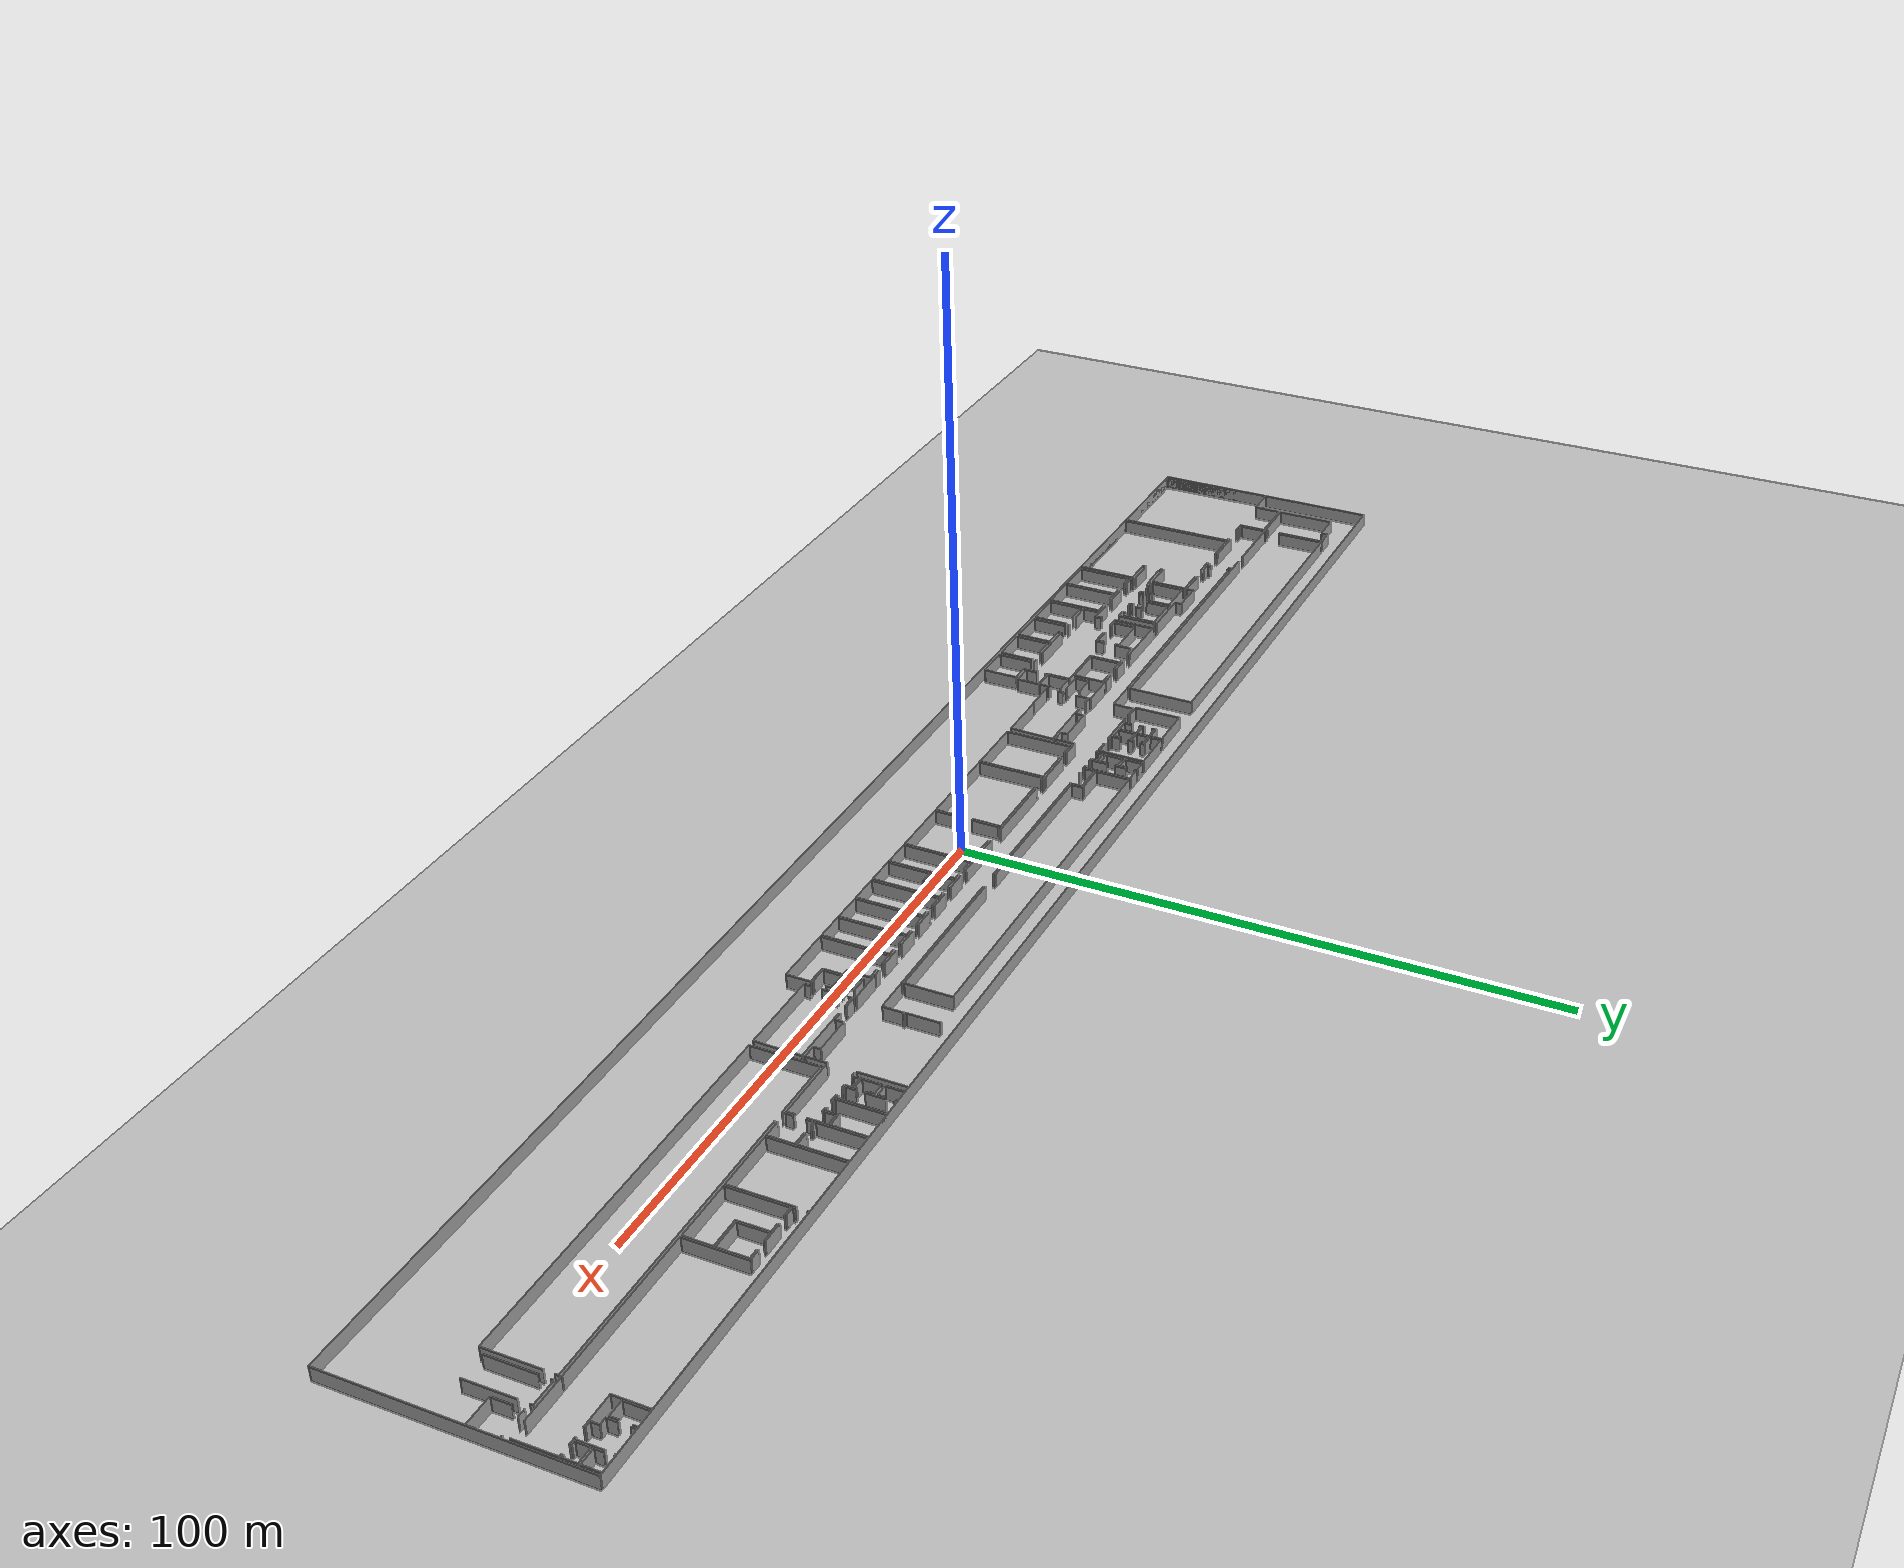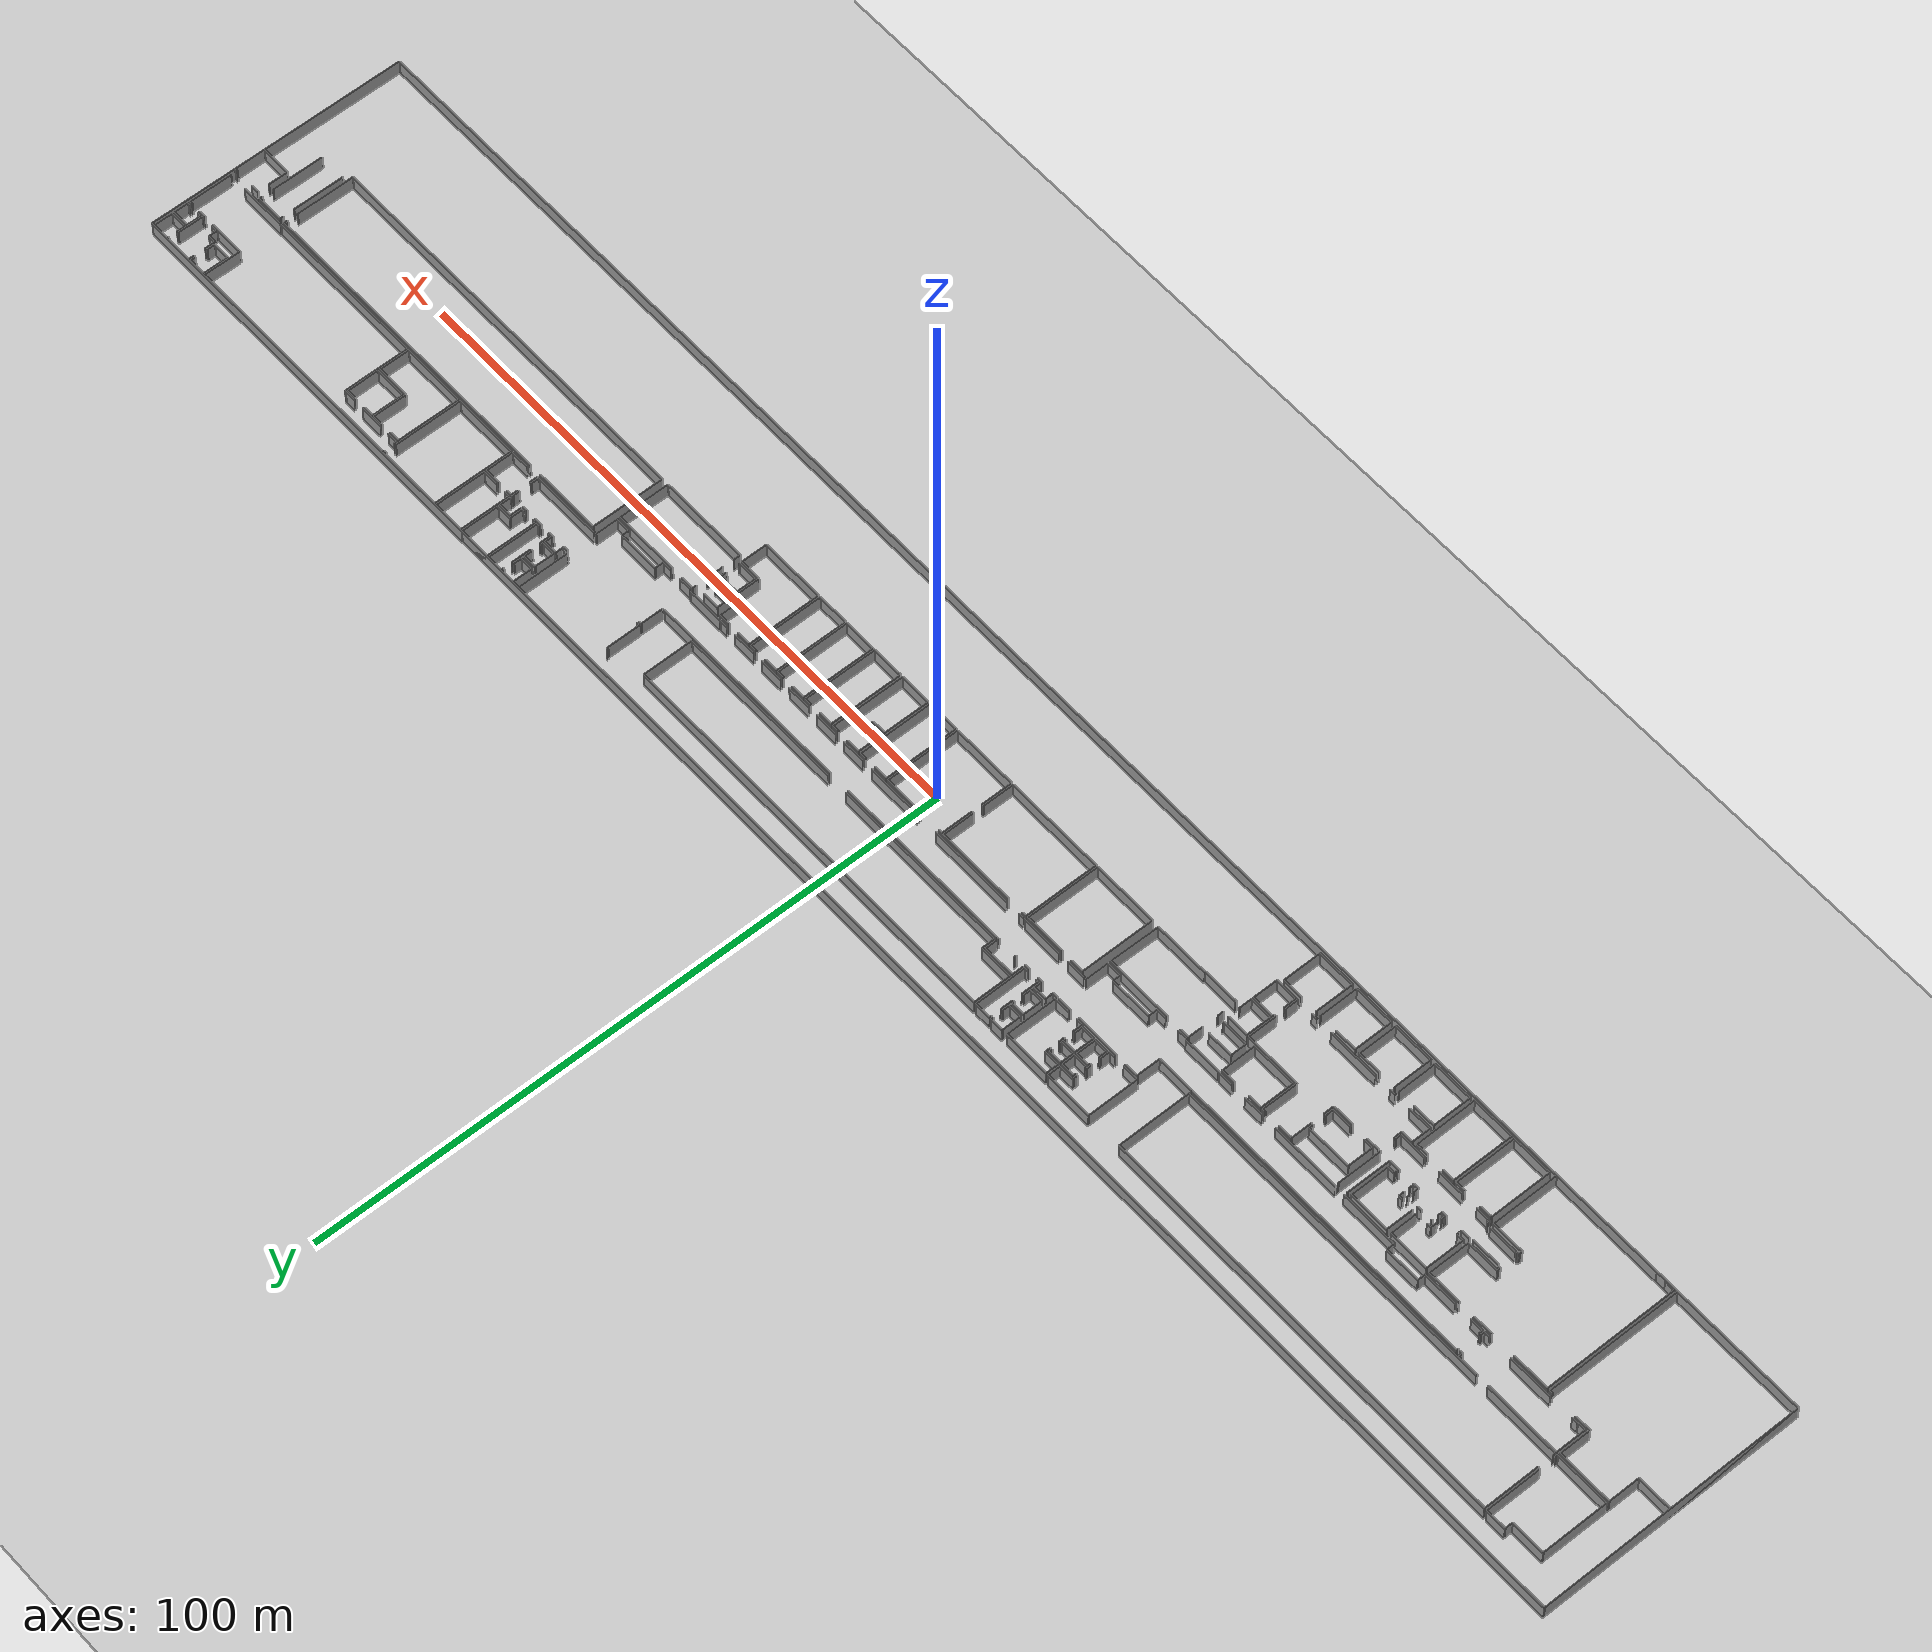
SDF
<sdf version="1.6">
  <world name="default">
    <light name="sun" type="directional">
      <cast_shadows>1</cast_shadows>
      <pose frame="">0 0 10 0 -0 0</pose>
      <diffuse>0.8 0.8 0.8 1</diffuse>
      <specular>0.1 0.1 0.1 1</specular>
      <attenuation>
        <range>1000</range>
        <constant>0.9</constant>
        <linear>0.01</linear>
        <quadratic>0.001</quadratic>
      </attenuation>
      <direction>-0.5 0.5 -1</direction>
    </light>
    <model name="ground_plane">
      <static>1</static>
      <link name="link">
        <collision name="collision">
          <geometry>
            <plane>
              <normal>0 0 1</normal>
              <size>100 100</size>
            </plane>
          </geometry>
          <surface>
            <friction>
              <ode>
                <mu>100</mu>
                <mu2>50</mu2>
              </ode>
              <torsional>
                <ode />
              </torsional>
            </friction>
            <contact>
              <ode />
            </contact>
            <bounce />
          </surface>
          <max_contacts>10</max_contacts>
        </collision>
        <visual name="visual">
          <cast_shadows>0</cast_shadows>
          <geometry>
            <plane>
              <normal>0 0 1</normal>
              <size>100 100</size>
            </plane>
          </geometry>
          <material>
            <script>
              <uri>file://media/materials/scripts/gazebo.material</uri>
              <name>Gazebo/Grey</name>
            </script>
          </material>
        </visual>
        <self_collide>0</self_collide>
        <kinematic>0</kinematic>
        <gravity>1</gravity>
      </link>
    </model>
    <gravity>0 0 -9.8</gravity>
    <magnetic_field>6e-06 2.3e-05 -4.2e-05</magnetic_field>
    <atmosphere type="adiabatic" />
    <physics default="0" name="default_physics" type="ode">
      <max_step_size>0.001</max_step_size>
      <real_time_factor>1</real_time_factor>
      <real_time_update_rate>1000</real_time_update_rate>
    </physics>
    <scene>
      <ambient>0.4 0.4 0.4 1</ambient>
      <background>0.7 0.7 0.7 1</background>
      <shadows>1</shadows>
    </scene>
    <spherical_coordinates>
      <surface_model>EARTH_WGS84</surface_model>
      <latitude_deg>0</latitude_deg>
      <longitude_deg>0</longitude_deg>
      <elevation>0</elevation>
      <heading_deg>0</heading_deg>
    </spherical_coordinates>
  <model name="50037764_PLAN1">
		<static>1</static>
		<link name="Wall_0">
			<collision name="Wall_0_Collision">
				<geometry>
					<box>
						<size>8.58180385378 0.1 2.5</size>
					</box>
				</geometry>
				<pose frame="">4.29090192689 0 1.25 0 0 0</pose>
			</collision>
			<visual name="Wall_0_Visual">
				<pose frame="">4.29090192689 0 1.25 0 0 0</pose>
				<geometry>
					<box>
						<size>8.58180385378 0.1 2.5</size>
					</box>
				</geometry>
				<material>
					<script>
						<uri>file://media/materials/scripts/gazebo.material</uri>
						<name>Gazebo/Grey</name>
					</script>
					<ambient>1 1 1 1</ambient>
				</material>
			</visual>
			<pose frame="">14.0925313946 -15.2658243937 0 0 0 3.14159265359</pose>
		</link>
		<link name="Wall_1">
			<collision name="Wall_1_Collision">
				<geometry>
					<box>
						<size>10.3601606589 0.1 2.5</size>
					</box>
				</geometry>
				<pose frame="">5.18008032945 0 1.25 0 0 0</pose>
			</collision>
			<visual name="Wall_1_Visual">
				<pose frame="">5.18008032945 0 1.25 0 0 0</pose>
				<geometry>
					<box>
						<size>10.3601606589 0.1 2.5</size>
					</box>
				</geometry>
				<material>
					<script>
						<uri>file://media/materials/scripts/gazebo.material</uri>
						<name>Gazebo/Grey</name>
					</script>
					<ambient>1 1 1 1</ambient>
				</material>
			</visual>
			<pose frame="">5.5107275408 -15.2658243937 0 0 0 1.57079632679</pose>
		</link>
		<link name="Wall_2">
			<collision name="Wall_2_Collision">
				<geometry>
					<box>
						<size>5.35624586913 0.1 2.5</size>
					</box>
				</geometry>
				<pose frame="">2.67812293457 0 1.25 0 0 0</pose>
			</collision>
			<visual name="Wall_2_Visual">
				<pose frame="">2.67812293457 0 1.25 0 0 0</pose>
				<geometry>
					<box>
						<size>5.35624586913 0.1 2.5</size>
					</box>
				</geometry>
				<material>
					<script>
						<uri>file://media/materials/scripts/gazebo.material</uri>
						<name>Gazebo/Grey</name>
					</script>
					<ambient>1 1 1 1</ambient>
				</material>
			</visual>
			<pose frame="">5.5107275408 -4.90566373481 0 0 0 0.0</pose>
		</link>
		<link name="Wall_3">
			<collision name="Wall_3_Collision">
				<geometry>
					<box>
						<size>1.2465300727 0.1 2.5</size>
					</box>
				</geometry>
				<pose frame="">0.623265036352 0 1.25 0 0 0</pose>
			</collision>
			<visual name="Wall_3_Visual">
				<pose frame="">0.623265036352 0 1.25 0 0 0</pose>
				<geometry>
					<box>
						<size>1.2465300727 0.1 2.5</size>
					</box>
				</geometry>
				<material>
					<script>
						<uri>file://media/materials/scripts/gazebo.material</uri>
						<name>Gazebo/Grey</name>
					</script>
					<ambient>1 1 1 1</ambient>
				</material>
			</visual>
			<pose frame="">10.8669734099 -4.90566373481 0 0 0 1.57079632679</pose>
		</link>
		<link name="Wall_4">
			<collision name="Wall_4_Collision">
				<geometry>
					<box>
						<size>3.22431236972 0.1 2.5</size>
					</box>
				</geometry>
				<pose frame="">1.61215618486 0 1.25 0 0 0</pose>
			</collision>
			<visual name="Wall_4_Visual">
				<pose frame="">1.61215618486 0 1.25 0 0 0</pose>
				<geometry>
					<box>
						<size>3.22431236972 0.1 2.5</size>
					</box>
				</geometry>
				<material>
					<script>
						<uri>file://media/materials/scripts/gazebo.material</uri>
						<name>Gazebo/Grey</name>
					</script>
					<ambient>1 1 1 1</ambient>
				</material>
			</visual>
			<pose frame="">10.8669734099 -3.65913366211 0 0 0 0.0</pose>
		</link>
		<link name="Wall_5">
			<collision name="Wall_5_Collision">
				<geometry>
					<box>
						<size>8.6092582236 0.1 2.5</size>
					</box>
				</geometry>
				<pose frame="">4.3046291118 0 1.25 0 0 0</pose>
			</collision>
			<visual name="Wall_5_Visual">
				<pose frame="">4.3046291118 0 1.25 0 0 0</pose>
				<geometry>
					<box>
						<size>8.6092582236 0.1 2.5</size>
					</box>
				</geometry>
				<material>
					<script>
						<uri>file://media/materials/scripts/gazebo.material</uri>
						<name>Gazebo/Grey</name>
					</script>
					<ambient>1 1 1 1</ambient>
				</material>
			</visual>
			<pose frame="">14.0912857797 -3.65913366211 0 0 0 -1.57079632679</pose>
		</link>
		<link name="Wall_6">
			<collision name="Wall_6_Collision">
				<geometry>
					<box>
						<size>0.382253287818 0.1 2.5</size>
					</box>
				</geometry>
				<pose frame="">0.191126643909 0 1.25 0 0 0</pose>
			</collision>
			<visual name="Wall_6_Visual">
				<pose frame="">0.191126643909 0 1.25 0 0 0</pose>
				<geometry>
					<box>
						<size>0.382253287818 0.1 2.5</size>
					</box>
				</geometry>
				<material>
					<script>
						<uri>file://media/materials/scripts/gazebo.material</uri>
						<name>Gazebo/Grey</name>
					</script>
					<ambient>1 1 1 1</ambient>
				</material>
			</visual>
			<pose frame="">14.0912857797 -14.8835731354 0 0 0 -1.56753770961</pose>
		</link>
		<link name="Wall_7">
			<collision name="Wall_7_Collision">
				<geometry>
					<box>
						<size>52.3181147999 0.1 2.5</size>
					</box>
				</geometry>
				<pose frame="">26.1590574 0 1.25 0 0 0</pose>
			</collision>
			<visual name="Wall_7_Visual">
				<pose frame="">26.1590574 0 1.25 0 0 0</pose>
				<geometry>
					<box>
						<size>52.3181147999 0.1 2.5</size>
					</box>
				</geometry>
				<material>
					<script>
						<uri>file://media/materials/scripts/gazebo.material</uri>
						<name>Gazebo/Grey</name>
					</script>
					<ambient>1 1 1 1</ambient>
				</material>
			</visual>
			<pose frame="">80.802531903 -15.2174996187 0 0 0 3.14159265359</pose>
		</link>
		<link name="Wall_8">
			<collision name="Wall_8_Collision">
				<geometry>
					<box>
						<size>12.0671106818 0.1 2.5</size>
					</box>
				</geometry>
				<pose frame="">6.03355534089 0 1.25 0 0 0</pose>
			</collision>
			<visual name="Wall_8_Visual">
				<pose frame="">6.03355534089 0 1.25 0 0 0</pose>
				<geometry>
					<box>
						<size>12.0671106818 0.1 2.5</size>
					</box>
				</geometry>
				<material>
					<script>
						<uri>file://media/materials/scripts/gazebo.material</uri>
						<name>Gazebo/Grey</name>
					</script>
					<ambient>1 1 1 1</ambient>
				</material>
			</visual>
			<pose frame="">26.5323605674 -15.2174996187 0 0 0 3.14159265359</pose>
		</link>
		<link name="Wall_9">
			<collision name="Wall_9_Collision">
				<geometry>
					<box>
						<size>0.431160709746 0.1 2.5</size>
					</box>
				</geometry>
				<pose frame="">0.215580354873 0 1.25 0 0 0</pose>
			</collision>
			<visual name="Wall_9_Visual">
				<pose frame="">0.215580354873 0 1.25 0 0 0</pose>
				<geometry>
					<box>
						<size>0.431160709746 0.1 2.5</size>
					</box>
				</geometry>
				<material>
					<script>
						<uri>file://media/materials/scripts/gazebo.material</uri>
						<name>Gazebo/Grey</name>
					</script>
					<ambient>1 1 1 1</ambient>
				</material>
			</visual>
			<pose frame="">14.4652498856 -15.2174996187 0 0 0 1.57079632679</pose>
		</link>
		<link name="Wall_10">
			<collision name="Wall_10_Collision">
				<geometry>
					<box>
						<size>8.69787482841 0.1 2.5</size>
					</box>
				</geometry>
				<pose frame="">4.34893741421 0 1.25 0 0 0</pose>
			</collision>
			<visual name="Wall_10_Visual">
				<pose frame="">4.34893741421 0 1.25 0 0 0</pose>
				<geometry>
					<box>
						<size>8.69787482841 0.1 2.5</size>
					</box>
				</geometry>
				<material>
					<script>
						<uri>file://media/materials/scripts/gazebo.material</uri>
						<name>Gazebo/Grey</name>
					</script>
					<ambient>1 1 1 1</ambient>
				</material>
			</visual>
			<pose frame="">14.4652498856 -12.3750826173 0 0 0 1.57079632679</pose>
		</link>
		<link name="Wall_11">
			<collision name="Wall_11_Collision">
				<geometry>
					<box>
						<size>66.322538004 0.1 2.5</size>
					</box>
				</geometry>
				<pose frame="">33.161269002 0 1.25 0 0 0</pose>
			</collision>
			<visual name="Wall_11_Visual">
				<pose frame="">33.161269002 0 1.25 0 0 0</pose>
				<geometry>
					<box>
						<size>66.322538004 0.1 2.5</size>
					</box>
				</geometry>
				<material>
					<script>
						<uri>file://media/materials/scripts/gazebo.material</uri>
						<name>Gazebo/Grey</name>
					</script>
					<ambient>1 1 1 1</ambient>
				</material>
			</visual>
			<pose frame="">14.4652498856 -3.67720778891 0 0 0 0.0</pose>
		</link>
		<link name="Wall_12">
			<collision name="Wall_12_Collision">
				<geometry>
					<box>
						<size>11.5403012483 0.1 2.5</size>
					</box>
				</geometry>
				<pose frame="">5.77015062417 0 1.25 0 0 0</pose>
			</collision>
			<visual name="Wall_12_Visual">
				<pose frame="">5.77015062417 0 1.25 0 0 0</pose>
				<geometry>
					<box>
						<size>11.5403012483 0.1 2.5</size>
					</box>
				</geometry>
				<material>
					<script>
						<uri>file://media/materials/scripts/gazebo.material</uri>
						<name>Gazebo/Grey</name>
					</script>
					<ambient>1 1 1 1</ambient>
				</material>
			</visual>
			<pose frame="">80.7877878896 -3.67720778891 0 0 0 -1.56951871565</pose>
		</link>
		<link name="Wall_13">
			<collision name="Wall_13_Collision">
				<geometry>
					<box>
						<size>0.864304235091 0.1 2.5</size>
					</box>
				</geometry>
				<pose frame="">0.432152117545 0 1.25 0 0 0</pose>
			</collision>
			<visual name="Wall_13_Visual">
				<pose frame="">0.432152117545 0 1.25 0 0 0</pose>
				<geometry>
					<box>
						<size>0.864304235091 0.1 2.5</size>
					</box>
				</geometry>
				<material>
					<script>
						<uri>file://media/materials/scripts/gazebo.material</uri>
						<name>Gazebo/Grey</name>
					</script>
					<ambient>1 1 1 1</ambient>
				</material>
			</visual>
			<pose frame="">32.2820173878 -20.0217347094 0 0 0 3.14159265359</pose>
		</link>
		<link name="Wall_14">
			<collision name="Wall_14_Collision">
				<geometry>
					<box>
						<size>7.04763841578 0.1 2.5</size>
					</box>
				</geometry>
				<pose frame="">3.52381920789 0 1.25 0 0 0</pose>
			</collision>
			<visual name="Wall_14_Visual">
				<pose frame="">3.52381920789 0 1.25 0 0 0</pose>
				<geometry>
					<box>
						<size>7.04763841578 0.1 2.5</size>
					</box>
				</geometry>
				<material>
					<script>
						<uri>file://media/materials/scripts/gazebo.material</uri>
						<name>Gazebo/Grey</name>
					</script>
					<ambient>1 1 1 1</ambient>
				</material>
			</visual>
			<pose frame="">27.6450251665 -20.0217347094 0 0 0 3.14159265359</pose>
		</link>
		<link name="Wall_15">
			<collision name="Wall_15_Collision">
				<geometry>
					<box>
						<size>0.929889674106 0.1 2.5</size>
					</box>
				</geometry>
				<pose frame="">0.464944837053 0 1.25 0 0 0</pose>
			</collision>
			<visual name="Wall_15_Visual">
				<pose frame="">0.464944837053 0 1.25 0 0 0</pose>
				<geometry>
					<box>
						<size>0.929889674106 0.1 2.5</size>
					</box>
				</geometry>
				<material>
					<script>
						<uri>file://media/materials/scripts/gazebo.material</uri>
						<name>Gazebo/Grey</name>
					</script>
					<ambient>1 1 1 1</ambient>
				</material>
			</visual>
			<pose frame="">16.7247953633 -20.0217347094 0 0 0 3.14159265359</pose>
		</link>
		<link name="Wall_16">
			<collision name="Wall_16_Collision">
				<geometry>
					<box>
						<size>0.0747368956226 0.1 2.5</size>
					</box>
				</geometry>
				<pose frame="">0.0373684478113 0 1.25 0 0 0</pose>
			</collision>
			<visual name="Wall_16_Visual">
				<pose frame="">0.0373684478113 0 1.25 0 0 0</pose>
				<geometry>
					<box>
						<size>0.0747368956226 0.1 2.5</size>
					</box>
				</geometry>
				<material>
					<script>
						<uri>file://media/materials/scripts/gazebo.material</uri>
						<name>Gazebo/Grey</name>
					</script>
					<ambient>1 1 1 1</ambient>
				</material>
			</visual>
			<pose frame="">15.7949056892 -20.0217347094 0 0 0 -1.57079632679</pose>
		</link>
		<link name="Wall_17">
			<collision name="Wall_17_Collision">
				<geometry>
					<box>
						<size>1.32965580355 0.1 2.5</size>
					</box>
				</geometry>
				<pose frame="">0.664827901774 0 1.25 0 0 0</pose>
			</collision>
			<visual name="Wall_17_Visual">
				<pose frame="">0.664827901774 0 1.25 0 0 0</pose>
				<geometry>
					<box>
						<size>1.32965580355 0.1 2.5</size>
					</box>
				</geometry>
				<material>
					<script>
						<uri>file://media/materials/scripts/gazebo.material</uri>
						<name>Gazebo/Grey</name>
					</script>
					<ambient>1 1 1 1</ambient>
				</material>
			</visual>
			<pose frame="">15.7949056892 -20.0964716051 0 0 0 3.14159265359</pose>
		</link>
		<link name="Wall_18">
			<collision name="Wall_18_Collision">
				<geometry>
					<box>
						<size>4.78430525192 0.1 2.5</size>
					</box>
				</geometry>
				<pose frame="">2.39215262596 0 1.25 0 0 0</pose>
			</collision>
			<visual name="Wall_18_Visual">
				<pose frame="">2.39215262596 0 1.25 0 0 0</pose>
				<geometry>
					<box>
						<size>4.78430525192 0.1 2.5</size>
					</box>
				</geometry>
				<material>
					<script>
						<uri>file://media/materials/scripts/gazebo.material</uri>
						<name>Gazebo/Grey</name>
					</script>
					<ambient>1 1 1 1</ambient>
				</material>
			</visual>
			<pose frame="">14.4652498856 -20.0964716051 0 0 0 1.57079632679</pose>
		</link>
		<link name="Wall_19">
			<collision name="Wall_19_Collision">
				<geometry>
					<box>
						<size>12.0663480604 0.1 2.5</size>
					</box>
				</geometry>
				<pose frame="">6.0331740302 0 1.25 0 0 0</pose>
			</collision>
			<visual name="Wall_19_Visual">
				<pose frame="">6.0331740302 0 1.25 0 0 0</pose>
				<geometry>
					<box>
						<size>12.0663480604 0.1 2.5</size>
					</box>
				</geometry>
				<material>
					<script>
						<uri>file://media/materials/scripts/gazebo.material</uri>
						<name>Gazebo/Grey</name>
					</script>
					<ambient>1 1 1 1</ambient>
				</material>
			</visual>
			<pose frame="">14.4652498856 -15.3121663531 0 0 0 0.0</pose>
		</link>
		<link name="Wall_20">
			<collision name="Wall_20_Collision">
				<geometry>
					<box>
						<size>3.28283085058 0.1 2.5</size>
					</box>
				</geometry>
				<pose frame="">1.64141542529 0 1.25 0 0 0</pose>
			</collision>
			<visual name="Wall_20_Visual">
				<pose frame="">1.64141542529 0 1.25 0 0 0</pose>
				<geometry>
					<box>
						<size>3.28283085058 0.1 2.5</size>
					</box>
				</geometry>
				<material>
					<script>
						<uri>file://media/materials/scripts/gazebo.material</uri>
						<name>Gazebo/Grey</name>
					</script>
					<ambient>1 1 1 1</ambient>
				</material>
			</visual>
			<pose frame="">28.492297524 -15.3121663531 0 0 0 0.0</pose>
		</link>
		<link name="Wall_21">
			<collision name="Wall_21_Collision">
				<geometry>
					<box>
						<size>0.654202043825 0.1 2.5</size>
					</box>
				</geometry>
				<pose frame="">0.327101021913 0 1.25 0 0 0</pose>
			</collision>
			<visual name="Wall_21_Visual">
				<pose frame="">0.327101021913 0 1.25 0 0 0</pose>
				<geometry>
					<box>
						<size>0.654202043825 0.1 2.5</size>
					</box>
				</geometry>
				<material>
					<script>
						<uri>file://media/materials/scripts/gazebo.material</uri>
						<name>Gazebo/Grey</name>
					</script>
					<ambient>1 1 1 1</ambient>
				</material>
			</visual>
			<pose frame="">31.7751283746 -15.3121663531 0 0 0 -1.57079632679</pose>
		</link>
		<link name="Wall_22">
			<collision name="Wall_22_Collision">
				<geometry>
					<box>
						<size>0.519853576694 0.1 2.5</size>
					</box>
				</geometry>
				<pose frame="">0.259926788347 0 1.25 0 0 0</pose>
			</collision>
			<visual name="Wall_22_Visual">
				<pose frame="">0.259926788347 0 1.25 0 0 0</pose>
				<geometry>
					<box>
						<size>0.519853576694 0.1 2.5</size>
					</box>
				</geometry>
				<material>
					<script>
						<uri>file://media/materials/scripts/gazebo.material</uri>
						<name>Gazebo/Grey</name>
					</script>
					<ambient>1 1 1 1</ambient>
				</material>
			</visual>
			<pose frame="">31.7751283746 -15.966368397 0 0 0 0.0</pose>
		</link>
		<link name="Wall_23">
			<collision name="Wall_23_Collision">
				<geometry>
					<box>
						<size>0.6468328719 0.1 2.5</size>
					</box>
				</geometry>
				<pose frame="">0.32341643595 0 1.25 0 0 0</pose>
			</collision>
			<visual name="Wall_23_Visual">
				<pose frame="">0.32341643595 0 1.25 0 0 0</pose>
				<geometry>
					<box>
						<size>0.6468328719 0.1 2.5</size>
					</box>
				</geometry>
				<material>
					<script>
						<uri>file://media/materials/scripts/gazebo.material</uri>
						<name>Gazebo/Grey</name>
					</script>
					<ambient>1 1 1 1</ambient>
				</material>
			</visual>
			<pose frame="">32.2949819513 -19.3750317759 0 0 0 -1.59084081167</pose>
		</link>
		<link name="Wall_24">
			<collision name="Wall_24_Collision">
				<geometry>
					<box>
						<size>21.2115511719 0.1 2.5</size>
					</box>
				</geometry>
				<pose frame="">10.6057755859 0 1.25 0 0 0</pose>
			</collision>
			<visual name="Wall_24_Visual">
				<pose frame="">10.6057755859 0 1.25 0 0 0</pose>
				<geometry>
					<box>
						<size>21.2115511719 0.1 2.5</size>
					</box>
				</geometry>
				<material>
					<script>
						<uri>file://media/materials/scripts/gazebo.material</uri>
						<name>Gazebo/Grey</name>
					</script>
					<ambient>1 1 1 1</ambient>
				</material>
			</visual>
			<pose frame="">21.2115511719 -41.6410341146 0 0 0 3.14159265359</pose>
		</link>
		<link name="Wall_25">
			<collision name="Wall_25_Collision">
				<geometry>
					<box>
						<size>21.1568966394 0.1 2.5</size>
					</box>
				</geometry>
				<pose frame="">10.5784483197 0 1.25 0 0 0</pose>
			</collision>
			<visual name="Wall_25_Visual">
				<pose frame="">10.5784483197 0 1.25 0 0 0</pose>
				<geometry>
					<box>
						<size>21.1568966394 0.1 2.5</size>
					</box>
				</geometry>
				<material>
					<script>
						<uri>file://media/materials/scripts/gazebo.material</uri>
						<name>Gazebo/Grey</name>
					</script>
					<ambient>1 1 1 1</ambient>
				</material>
			</visual>
			<pose frame="">0.0 -41.6410341146 0 0 0 1.57079632679</pose>
		</link>
		<link name="Wall_26">
			<collision name="Wall_26_Collision">
				<geometry>
					<box>
						<size>5.47643499924 0.1 2.5</size>
					</box>
				</geometry>
				<pose frame="">2.73821749962 0 1.25 0 0 0</pose>
			</collision>
			<visual name="Wall_26_Visual">
				<pose frame="">2.73821749962 0 1.25 0 0 0</pose>
				<geometry>
					<box>
						<size>5.47643499924 0.1 2.5</size>
					</box>
				</geometry>
				<material>
					<script>
						<uri>file://media/materials/scripts/gazebo.material</uri>
						<name>Gazebo/Grey</name>
					</script>
					<ambient>1 1 1 1</ambient>
				</material>
			</visual>
			<pose frame="">0.0 -20.4841374752 0 0 0 0.0</pose>
		</link>
		<link name="Wall_27">
			<collision name="Wall_27_Collision">
				<geometry>
					<box>
						<size>4.89338553053 0.1 2.5</size>
					</box>
				</geometry>
				<pose frame="">2.44669276527 0 1.25 0 0 0</pose>
			</collision>
			<visual name="Wall_27_Visual">
				<pose frame="">2.44669276527 0 1.25 0 0 0</pose>
				<geometry>
					<box>
						<size>4.89338553053 0.1 2.5</size>
					</box>
				</geometry>
				<material>
					<script>
						<uri>file://media/materials/scripts/gazebo.material</uri>
						<name>Gazebo/Grey</name>
					</script>
					<ambient>1 1 1 1</ambient>
				</material>
			</visual>
			<pose frame="">5.47643499924 -20.4841374752 0 0 0 1.57079632679</pose>
		</link>
		<link name="Wall_28">
			<collision name="Wall_28_Collision">
				<geometry>
					<box>
						<size>8.58742183131 0.1 2.5</size>
					</box>
				</geometry>
				<pose frame="">4.29371091565 0 1.25 0 0 0</pose>
			</collision>
			<visual name="Wall_28_Visual">
				<pose frame="">4.29371091565 0 1.25 0 0 0</pose>
				<geometry>
					<box>
						<size>8.58742183131 0.1 2.5</size>
					</box>
				</geometry>
				<material>
					<script>
						<uri>file://media/materials/scripts/gazebo.material</uri>
						<name>Gazebo/Grey</name>
					</script>
					<ambient>1 1 1 1</ambient>
				</material>
			</visual>
			<pose frame="">5.47643499924 -15.5907519447 0 0 0 0.0</pose>
		</link>
		<link name="Wall_29">
			<collision name="Wall_29_Collision">
				<geometry>
					<box>
						<size>4.86466012507 0.1 2.5</size>
					</box>
				</geometry>
				<pose frame="">2.43233006253 0 1.25 0 0 0</pose>
			</collision>
			<visual name="Wall_29_Visual">
				<pose frame="">2.43233006253 0 1.25 0 0 0</pose>
				<geometry>
					<box>
						<size>4.86466012507 0.1 2.5</size>
					</box>
				</geometry>
				<material>
					<script>
						<uri>file://media/materials/scripts/gazebo.material</uri>
						<name>Gazebo/Grey</name>
					</script>
					<ambient>1 1 1 1</ambient>
				</material>
			</visual>
			<pose frame="">14.0638568305 -15.5907519447 0 0 0 -1.57079632679</pose>
		</link>
		<link name="Wall_30">
			<collision name="Wall_30_Collision">
				<geometry>
					<box>
						<size>2.57018658803 0.1 2.5</size>
					</box>
				</geometry>
				<pose frame="">1.28509329402 0 1.25 0 0 0</pose>
			</collision>
			<visual name="Wall_30_Visual">
				<pose frame="">1.28509329402 0 1.25 0 0 0</pose>
				<geometry>
					<box>
						<size>2.57018658803 0.1 2.5</size>
					</box>
				</geometry>
				<material>
					<script>
						<uri>file://media/materials/scripts/gazebo.material</uri>
						<name>Gazebo/Grey</name>
					</script>
					<ambient>1 1 1 1</ambient>
				</material>
			</visual>
			<pose frame="">14.0638568305 -20.4554120698 0 0 0 0.0</pose>
		</link>
		<link name="Wall_31">
			<collision name="Wall_31_Collision">
				<geometry>
					<box>
						<size>0.527733997661 0.1 2.5</size>
					</box>
				</geometry>
				<pose frame="">0.263866998831 0 1.25 0 0 0</pose>
			</collision>
			<visual name="Wall_31_Visual">
				<pose frame="">0.263866998831 0 1.25 0 0 0</pose>
				<geometry>
					<box>
						<size>0.527733997661 0.1 2.5</size>
					</box>
				</geometry>
				<material>
					<script>
						<uri>file://media/materials/scripts/gazebo.material</uri>
						<name>Gazebo/Grey</name>
					</script>
					<ambient>1 1 1 1</ambient>
				</material>
			</visual>
			<pose frame="">20.6563628044 -20.4554120698 0 0 0 0.0</pose>
		</link>
		<link name="Wall_32">
			<collision name="Wall_32_Collision">
				<geometry>
					<box>
						<size>21.1856398338 0.1 2.5</size>
					</box>
				</geometry>
				<pose frame="">10.5928199169 0 1.25 0 0 0</pose>
			</collision>
			<visual name="Wall_32_Visual">
				<pose frame="">10.5928199169 0 1.25 0 0 0</pose>
				<geometry>
					<box>
						<size>21.1856398338 0.1 2.5</size>
					</box>
				</geometry>
				<material>
					<script>
						<uri>file://media/materials/scripts/gazebo.material</uri>
						<name>Gazebo/Grey</name>
					</script>
					<ambient>1 1 1 1</ambient>
				</material>
			</visual>
			<pose frame="">21.1840968021 -20.4554120698 0 0 0 -1.56950043119</pose>
		</link>
		<link name="Wall_33">
			<collision name="Wall_33_Collision">
				<geometry>
					<box>
						<size>17.8649143322 0.1 2.5</size>
					</box>
				</geometry>
				<pose frame="">8.9324571661 0 1.25 0 0 0</pose>
			</collision>
			<visual name="Wall_33_Visual">
				<pose frame="">8.9324571661 0 1.25 0 0 0</pose>
				<geometry>
					<box>
						<size>17.8649143322 0.1 2.5</size>
					</box>
				</geometry>
				<material>
					<script>
						<uri>file://media/materials/scripts/gazebo.material</uri>
						<name>Gazebo/Grey</name>
					</script>
					<ambient>1 1 1 1</ambient>
				</material>
			</visual>
			<pose frame="">42.7660277594 -41.6410341146 0 0 0 3.14159265359</pose>
		</link>
		<link name="Wall_34">
			<collision name="Wall_34_Collision">
				<geometry>
					<box>
						<size>1.73953937668 0.1 2.5</size>
					</box>
				</geometry>
				<pose frame="">0.869769688342 0 1.25 0 0 0</pose>
			</collision>
			<visual name="Wall_34_Visual">
				<pose frame="">0.869769688342 0 1.25 0 0 0</pose>
				<geometry>
					<box>
						<size>1.73953937668 0.1 2.5</size>
					</box>
				</geometry>
				<material>
					<script>
						<uri>file://media/materials/scripts/gazebo.material</uri>
						<name>Gazebo/Grey</name>
					</script>
					<ambient>1 1 1 1</ambient>
				</material>
			</visual>
			<pose frame="">23.3529920179 -41.6410341146 0 0 0 3.14159265359</pose>
		</link>
		<link name="Wall_35">
			<collision name="Wall_35_Collision">
				<geometry>
					<box>
						<size>21.1635060247 0.1 2.5</size>
					</box>
				</geometry>
				<pose frame="">10.5817530124 0 1.25 0 0 0</pose>
			</collision>
			<visual name="Wall_35_Visual">
				<pose frame="">10.5817530124 0 1.25 0 0 0</pose>
				<geometry>
					<box>
						<size>21.1635060247 0.1 2.5</size>
					</box>
				</geometry>
				<material>
					<script>
						<uri>file://media/materials/scripts/gazebo.material</uri>
						<name>Gazebo/Grey</name>
					</script>
					<ambient>1 1 1 1</ambient>
				</material>
			</visual>
			<pose frame="">21.6134526412 -41.6410341146 0 0 0 1.57079632679</pose>
		</link>
		<link name="Wall_36">
			<collision name="Wall_36_Collision">
				<geometry>
					<box>
						<size>5.89023336214 0.1 2.5</size>
					</box>
				</geometry>
				<pose frame="">2.94511668107 0 1.25 0 0 0</pose>
			</collision>
			<visual name="Wall_36_Visual">
				<pose frame="">2.94511668107 0 1.25 0 0 0</pose>
				<geometry>
					<box>
						<size>5.89023336214 0.1 2.5</size>
					</box>
				</geometry>
				<material>
					<script>
						<uri>file://media/materials/scripts/gazebo.material</uri>
						<name>Gazebo/Grey</name>
					</script>
					<ambient>1 1 1 1</ambient>
				</material>
			</visual>
			<pose frame="">21.6134526412 -20.4775280899 0 0 0 0.0</pose>
		</link>
		<link name="Wall_37">
			<collision name="Wall_37_Collision">
				<geometry>
					<box>
						<size>3.2894402359 0.1 2.5</size>
					</box>
				</geometry>
				<pose frame="">1.64472011795 0 1.25 0 0 0</pose>
			</collision>
			<visual name="Wall_37_Visual">
				<pose frame="">1.64472011795 0 1.25 0 0 0</pose>
				<geometry>
					<box>
						<size>3.2894402359 0.1 2.5</size>
					</box>
				</geometry>
				<material>
					<script>
						<uri>file://media/materials/scripts/gazebo.material</uri>
						<name>Gazebo/Grey</name>
					</script>
					<ambient>1 1 1 1</ambient>
				</material>
			</visual>
			<pose frame="">31.473892928 -20.4775280899 0 0 0 0.0</pose>
		</link>
		<link name="Wall_38">
			<collision name="Wall_38_Collision">
				<geometry>
					<box>
						<size>5.39681732676 0.1 2.5</size>
					</box>
				</geometry>
				<pose frame="">2.69840866338 0 1.25 0 0 0</pose>
			</collision>
			<visual name="Wall_38_Visual">
				<pose frame="">2.69840866338 0 1.25 0 0 0</pose>
				<geometry>
					<box>
						<size>5.39681732676 0.1 2.5</size>
					</box>
				</geometry>
				<material>
					<script>
						<uri>file://media/materials/scripts/gazebo.material</uri>
						<name>Gazebo/Grey</name>
					</script>
					<ambient>1 1 1 1</ambient>
				</material>
			</visual>
			<pose frame="">37.3509075194 -20.4775280899 0 0 0 0.0</pose>
		</link>
		<link name="Wall_39">
			<collision name="Wall_39_Collision">
				<geometry>
					<box>
						<size>6.53896995272 0.1 2.5</size>
					</box>
				</geometry>
				<pose frame="">3.26948497636 0 1.25 0 0 0</pose>
			</collision>
			<visual name="Wall_39_Visual">
				<pose frame="">3.26948497636 0 1.25 0 0 0</pose>
				<geometry>
					<box>
						<size>6.53896995272 0.1 2.5</size>
					</box>
				</geometry>
				<material>
					<script>
						<uri>file://media/materials/scripts/gazebo.material</uri>
						<name>Gazebo/Grey</name>
					</script>
					<ambient>1 1 1 1</ambient>
				</material>
			</visual>
			<pose frame="">42.7477248462 -20.4775280899 0 0 0 -1.57079632679</pose>
		</link>
		<link name="Wall_40">
			<collision name="Wall_40_Collision">
				<geometry>
					<box>
						<size>5.17209822563 0.1 2.5</size>
					</box>
				</geometry>
				<pose frame="">2.58604911282 0 1.25 0 0 0</pose>
			</collision>
			<visual name="Wall_40_Visual">
				<pose frame="">2.58604911282 0 1.25 0 0 0</pose>
				<geometry>
					<box>
						<size>5.17209822563 0.1 2.5</size>
					</box>
				</geometry>
				<material>
					<script>
						<uri>file://media/materials/scripts/gazebo.material</uri>
						<name>Gazebo/Grey</name>
					</script>
					<ambient>1 1 1 1</ambient>
				</material>
			</visual>
			<pose frame="">42.7477248462 -27.0164980426 0 0 0 3.14159265359</pose>
		</link>
		<link name="Wall_41">
			<collision name="Wall_41_Collision">
				<geometry>
					<box>
						<size>0.450963445015 0.1 2.5</size>
					</box>
				</geometry>
				<pose frame="">0.225481722507 0 1.25 0 0 0</pose>
			</collision>
			<visual name="Wall_41_Visual">
				<pose frame="">0.225481722507 0 1.25 0 0 0</pose>
				<geometry>
					<box>
						<size>0.450963445015 0.1 2.5</size>
					</box>
				</geometry>
				<material>
					<script>
						<uri>file://media/materials/scripts/gazebo.material</uri>
						<name>Gazebo/Grey</name>
					</script>
					<ambient>1 1 1 1</ambient>
				</material>
			</visual>
			<pose frame="">37.5756266206 -27.0164980426 0 0 0 -1.57079632679</pose>
		</link>
		<link name="Wall_42">
			<collision name="Wall_42_Collision">
				<geometry>
					<box>
						<size>0.265900655854 0.1 2.5</size>
					</box>
				</geometry>
				<pose frame="">0.132950327927 0 1.25 0 0 0</pose>
			</collision>
			<visual name="Wall_42_Visual">
				<pose frame="">0.132950327927 0 1.25 0 0 0</pose>
				<geometry>
					<box>
						<size>0.265900655854 0.1 2.5</size>
					</box>
				</geometry>
				<material>
					<script>
						<uri>file://media/materials/scripts/gazebo.material</uri>
						<name>Gazebo/Grey</name>
					</script>
					<ambient>1 1 1 1</ambient>
				</material>
			</visual>
			<pose frame="">37.5756266206 -27.4674614876 0 0 0 0.0</pose>
		</link>
		<link name="Wall_43">
			<collision name="Wall_43_Collision">
				<geometry>
					<box>
						<size>0.14133916315 0.1 2.5</size>
					</box>
				</geometry>
				<pose frame="">0.0706695815751 0 1.25 0 0 0</pose>
			</collision>
			<visual name="Wall_43_Visual">
				<pose frame="">0.0706695815751 0 1.25 0 0 0</pose>
				<geometry>
					<box>
						<size>0.14133916315 0.1 2.5</size>
					</box>
				</geometry>
				<material>
					<script>
						<uri>file://media/materials/scripts/gazebo.material</uri>
						<name>Gazebo/Grey</name>
					</script>
					<ambient>1 1 1 1</ambient>
				</material>
			</visual>
			<pose frame="">37.8415272764 -27.4674614876 0 0 0 -1.57079632679</pose>
		</link>
		<link name="Wall_44">
			<collision name="Wall_44_Collision">
				<geometry>
					<box>
						<size>0.200569423967 0.1 2.5</size>
					</box>
				</geometry>
				<pose frame="">0.100284711983 0 1.25 0 0 0</pose>
			</collision>
			<visual name="Wall_44_Visual">
				<pose frame="">0.100284711983 0 1.25 0 0 0</pose>
				<geometry>
					<box>
						<size>0.200569423967 0.1 2.5</size>
					</box>
				</geometry>
				<material>
					<script>
						<uri>file://media/materials/scripts/gazebo.material</uri>
						<name>Gazebo/Grey</name>
					</script>
					<ambient>1 1 1 1</ambient>
				</material>
			</visual>
			<pose frame="">37.8415272764 -30.4513447557 0 0 0 -1.57079632679</pose>
		</link>
		<link name="Wall_45">
			<collision name="Wall_45_Collision">
				<geometry>
					<box>
						<size>0.258782856271 0.1 2.5</size>
					</box>
				</geometry>
				<pose frame="">0.129391428136 0 1.25 0 0 0</pose>
			</collision>
			<visual name="Wall_45_Visual">
				<pose frame="">0.129391428136 0 1.25 0 0 0</pose>
				<geometry>
					<box>
						<size>0.258782856271 0.1 2.5</size>
					</box>
				</geometry>
				<material>
					<script>
						<uri>file://media/materials/scripts/gazebo.material</uri>
						<name>Gazebo/Grey</name>
					</script>
					<ambient>1 1 1 1</ambient>
				</material>
			</visual>
			<pose frame="">37.8415272764 -30.6519141797 0 0 0 3.14159265359</pose>
		</link>
		<link name="Wall_46">
			<collision name="Wall_46_Collision">
				<geometry>
					<box>
						<size>0.439524124256 0.1 2.5</size>
					</box>
				</geometry>
				<pose frame="">0.219762062128 0 1.25 0 0 0</pose>
			</collision>
			<visual name="Wall_46_Visual">
				<pose frame="">0.219762062128 0 1.25 0 0 0</pose>
				<geometry>
					<box>
						<size>0.439524124256 0.1 2.5</size>
					</box>
				</geometry>
				<material>
					<script>
						<uri>file://media/materials/scripts/gazebo.material</uri>
						<name>Gazebo/Grey</name>
					</script>
					<ambient>1 1 1 1</ambient>
				</material>
			</visual>
			<pose frame="">37.5827444202 -30.6519141797 0 0 0 -1.57079632679</pose>
		</link>
		<link name="Wall_47">
			<collision name="Wall_47_Collision">
				<geometry>
					<box>
						<size>5.17947023235 0.1 2.5</size>
					</box>
				</geometry>
				<pose frame="">2.58973511617 0 1.25 0 0 0</pose>
			</collision>
			<visual name="Wall_47_Visual">
				<pose frame="">2.58973511617 0 1.25 0 0 0</pose>
				<geometry>
					<box>
						<size>5.17947023235 0.1 2.5</size>
					</box>
				</geometry>
				<material>
					<script>
						<uri>file://media/materials/scripts/gazebo.material</uri>
						<name>Gazebo/Grey</name>
					</script>
					<ambient>1 1 1 1</ambient>
				</material>
			</visual>
			<pose frame="">37.5827444202 -31.0914383039 0 0 0 0.0</pose>
		</link>
		<link name="Wall_48">
			<collision name="Wall_48_Collision">
				<geometry>
					<box>
						<size>10.5495964998 0.1 2.5</size>
					</box>
				</geometry>
				<pose frame="">5.27479824989 0 1.25 0 0 0</pose>
			</collision>
			<visual name="Wall_48_Visual">
				<pose frame="">5.27479824989 0 1.25 0 0 0</pose>
				<geometry>
					<box>
						<size>10.5495964998 0.1 2.5</size>
					</box>
				</geometry>
				<material>
					<script>
						<uri>file://media/materials/scripts/gazebo.material</uri>
						<name>Gazebo/Grey</name>
					</script>
					<ambient>1 1 1 1</ambient>
				</material>
			</visual>
			<pose frame="">42.7622146525 -31.0914383039 0 0 0 -1.57043488103</pose>
		</link>
		<link name="Wall_49">
			<collision name="Wall_49_Collision">
				<geometry>
					<box>
						<size>4.62656972902 0.1 2.5</size>
					</box>
				</geometry>
				<pose frame="">2.31328486451 0 1.25 0 0 0</pose>
			</collision>
			<visual name="Wall_49_Visual">
				<pose frame="">2.31328486451 0 1.25 0 0 0</pose>
				<geometry>
					<box>
						<size>4.62656972902 0.1 2.5</size>
					</box>
				</geometry>
				<material>
					<script>
						<uri>file://media/materials/scripts/gazebo.material</uri>
						<name>Gazebo/Grey</name>
					</script>
					<ambient>1 1 1 1</ambient>
				</material>
			</visual>
			<pose frame="">42.6862067212 -27.6502364126 0 0 0 3.14159265359</pose>
		</link>
		<link name="Wall_50">
			<collision name="Wall_50_Collision">
				<geometry>
					<box>
						<size>4.62682449481 0.1 2.5</size>
					</box>
				</geometry>
				<pose frame="">2.3134122474 0 1.25 0 0 0</pose>
			</collision>
			<visual name="Wall_50_Visual">
				<pose frame="">2.3134122474 0 1.25 0 0 0</pose>
				<geometry>
					<box>
						<size>4.62682449481 0.1 2.5</size>
					</box>
				</geometry>
				<material>
					<script>
						<uri>file://media/materials/scripts/gazebo.material</uri>
						<name>Gazebo/Grey</name>
					</script>
					<ambient>1 1 1 1</ambient>
				</material>
			</visual>
			<pose frame="">38.0596369922 -30.4355839138 0 0 0 -0.0104941202504</pose>
		</link>
		<link name="Wall_51">
			<collision name="Wall_51_Collision">
				<geometry>
					<box>
						<size>4.26254512177 0.1 2.5</size>
					</box>
				</geometry>
				<pose frame="">2.13127256088 0 1.25 0 0 0</pose>
			</collision>
			<visual name="Wall_51_Visual">
				<pose frame="">2.13127256088 0 1.25 0 0 0</pose>
				<geometry>
					<box>
						<size>4.26254512177 0.1 2.5</size>
					</box>
				</geometry>
				<material>
					<script>
						<uri>file://media/materials/scripts/gazebo.material</uri>
						<name>Gazebo/Grey</name>
					</script>
					<ambient>1 1 1 1</ambient>
				</material>
			</visual>
			<pose frame="">59.4514210178 -31.0718643551 0 0 0 3.14159265359</pose>
		</link>
		<link name="Wall_52">
			<collision name="Wall_52_Collision">
				<geometry>
					<box>
						<size>4.22136356703 0.1 2.5</size>
					</box>
				</geometry>
				<pose frame="">2.11068178352 0 1.25 0 0 0</pose>
			</collision>
			<visual name="Wall_52_Visual">
				<pose frame="">2.11068178352 0 1.25 0 0 0</pose>
				<geometry>
					<box>
						<size>4.22136356703 0.1 2.5</size>
					</box>
				</geometry>
				<material>
					<script>
						<uri>file://media/materials/scripts/gazebo.material</uri>
						<name>Gazebo/Grey</name>
					</script>
					<ambient>1 1 1 1</ambient>
				</material>
			</visual>
			<pose frame="">52.5502059078 -31.0718643551 0 0 0 3.14159265359</pose>
		</link>
		<link name="Wall_53">
			<collision name="Wall_53_Collision">
				<geometry>
					<box>
						<size>2.10991916213 0.1 2.5</size>
					</box>
				</geometry>
				<pose frame="">1.05495958107 0 1.25 0 0 0</pose>
			</collision>
			<visual name="Wall_53_Visual">
				<pose frame="">1.05495958107 0 1.25 0 0 0</pose>
				<geometry>
					<box>
						<size>2.10991916213 0.1 2.5</size>
					</box>
				</geometry>
				<material>
					<script>
						<uri>file://media/materials/scripts/gazebo.material</uri>
						<name>Gazebo/Grey</name>
					</script>
					<ambient>1 1 1 1</ambient>
				</material>
			</visual>
			<pose frame="">45.7247445218 -31.0718643551 0 0 0 3.14159265359</pose>
		</link>
		<link name="Wall_54">
			<collision name="Wall_54_Collision">
				<geometry>
					<box>
						<size>0.219126544308 0.1 2.5</size>
					</box>
				</geometry>
				<pose frame="">0.109563272154 0 1.25 0 0 0</pose>
			</collision>
			<visual name="Wall_54_Visual">
				<pose frame="">0.109563272154 0 1.25 0 0 0</pose>
				<geometry>
					<box>
						<size>0.219126544308 0.1 2.5</size>
					</box>
				</geometry>
				<material>
					<script>
						<uri>file://media/materials/scripts/gazebo.material</uri>
						<name>Gazebo/Grey</name>
					</script>
					<ambient>1 1 1 1</ambient>
				</material>
			</visual>
			<pose frame="">43.6148253597 -31.0718643551 0 0 0 1.57079632679</pose>
		</link>
		<link name="Wall_55">
			<collision name="Wall_55_Collision">
				<geometry>
					<box>
						<size>0.403426712085 0.1 2.5</size>
					</box>
				</geometry>
				<pose frame="">0.201713356043 0 1.25 0 0 0</pose>
			</collision>
			<visual name="Wall_55_Visual">
				<pose frame="">0.201713356043 0 1.25 0 0 0</pose>
				<geometry>
					<box>
						<size>0.403426712085 0.1 2.5</size>
					</box>
				</geometry>
				<material>
					<script>
						<uri>file://media/materials/scripts/gazebo.material</uri>
						<name>Gazebo/Grey</name>
					</script>
					<ambient>1 1 1 1</ambient>
				</material>
			</visual>
			<pose frame="">43.6148253597 -30.8527378108 0 0 0 3.14159265359</pose>
		</link>
		<link name="Wall_56">
			<collision name="Wall_56_Collision">
				<geometry>
					<box>
						<size>0.286237226092 0.1 2.5</size>
					</box>
				</geometry>
				<pose frame="">0.143118613046 0 1.25 0 0 0</pose>
			</collision>
			<visual name="Wall_56_Visual">
				<pose frame="">0.143118613046 0 1.25 0 0 0</pose>
				<geometry>
					<box>
						<size>0.286237226092 0.1 2.5</size>
					</box>
				</geometry>
				<material>
					<script>
						<uri>file://media/materials/scripts/gazebo.material</uri>
						<name>Gazebo/Grey</name>
					</script>
					<ambient>1 1 1 1</ambient>
				</material>
			</visual>
			<pose frame="">43.2113986476 -30.8527378108 0 0 0 1.57079632679</pose>
		</link>
		<link name="Wall_57">
			<collision name="Wall_57_Collision">
				<geometry>
					<box>
						<size>0.124307285576 0.1 2.5</size>
					</box>
				</geometry>
				<pose frame="">0.0621536427881 0 1.25 0 0 0</pose>
			</collision>
			<visual name="Wall_57_Visual">
				<pose frame="">0.0621536427881 0 1.25 0 0 0</pose>
				<geometry>
					<box>
						<size>0.124307285576 0.1 2.5</size>
					</box>
				</geometry>
				<material>
					<script>
						<uri>file://media/materials/scripts/gazebo.material</uri>
						<name>Gazebo/Grey</name>
					</script>
					<ambient>1 1 1 1</ambient>
				</material>
			</visual>
			<pose frame="">43.2113986476 -27.5938024302 0 0 0 1.57079632679</pose>
		</link>
		<link name="Wall_58">
			<collision name="Wall_58_Collision">
				<geometry>
					<box>
						<size>1.42406833088 0.1 2.5</size>
					</box>
				</geometry>
				<pose frame="">0.712034165438 0 1.25 0 0 0</pose>
			</collision>
			<visual name="Wall_58_Visual">
				<pose frame="">0.712034165438 0 1.25 0 0 0</pose>
				<geometry>
					<box>
						<size>1.42406833088 0.1 2.5</size>
					</box>
				</geometry>
				<material>
					<script>
						<uri>file://media/materials/scripts/gazebo.material</uri>
						<name>Gazebo/Grey</name>
					</script>
					<ambient>1 1 1 1</ambient>
				</material>
			</visual>
			<pose frame="">43.2113986476 -27.4694951446 0 0 0 0.0</pose>
		</link>
		<link name="Wall_59">
			<collision name="Wall_59_Collision">
				<geometry>
					<box>
						<size>0.808887081194 0.1 2.5</size>
					</box>
				</geometry>
				<pose frame="">0.404443540597 0 1.25 0 0 0</pose>
			</collision>
			<visual name="Wall_59_Visual">
				<pose frame="">0.404443540597 0 1.25 0 0 0</pose>
				<geometry>
					<box>
						<size>0.808887081194 0.1 2.5</size>
					</box>
				</geometry>
				<material>
					<script>
						<uri>file://media/materials/scripts/gazebo.material</uri>
						<name>Gazebo/Grey</name>
					</script>
					<ambient>1 1 1 1</ambient>
				</material>
			</visual>
			<pose frame="">47.2217702984 -27.4694951446 0 0 0 0.0</pose>
		</link>
		<link name="Wall_60">
			<collision name="Wall_60_Collision">
				<geometry>
					<box>
						<size>0.733387564187 0.1 2.5</size>
					</box>
				</geometry>
				<pose frame="">0.366693782094 0 1.25 0 0 0</pose>
			</collision>
			<visual name="Wall_60_Visual">
				<pose frame="">0.366693782094 0 1.25 0 0 0</pose>
				<geometry>
					<box>
						<size>0.733387564187 0.1 2.5</size>
					</box>
				</geometry>
				<material>
					<script>
						<uri>file://media/materials/scripts/gazebo.material</uri>
						<name>Gazebo/Grey</name>
					</script>
					<ambient>1 1 1 1</ambient>
				</material>
			</visual>
			<pose frame="">48.0306573796 -27.4694951446 0 0 0 1.57079632679</pose>
		</link>
		<link name="Wall_61">
			<collision name="Wall_61_Collision">
				<geometry>
					<box>
						<size>0.232853729219 0.1 2.5</size>
					</box>
				</geometry>
				<pose frame="">0.116426864609 0 1.25 0 0 0</pose>
			</collision>
			<visual name="Wall_61_Visual">
				<pose frame="">0.116426864609 0 1.25 0 0 0</pose>
				<geometry>
					<box>
						<size>0.232853729219 0.1 2.5</size>
					</box>
				</geometry>
				<material>
					<script>
						<uri>file://media/materials/scripts/gazebo.material</uri>
						<name>Gazebo/Grey</name>
					</script>
					<ambient>1 1 1 1</ambient>
				</material>
			</visual>
			<pose frame="">48.0306573796 -25.896969851 0 0 0 1.57079632679</pose>
		</link>
		<link name="Wall_62">
			<collision name="Wall_62_Collision">
				<geometry>
					<box>
						<size>0.6980527734 0.1 2.5</size>
					</box>
				</geometry>
				<pose frame="">0.3490263867 0 1.25 0 0 0</pose>
			</collision>
			<visual name="Wall_62_Visual">
				<pose frame="">0.3490263867 0 1.25 0 0 0</pose>
				<geometry>
					<box>
						<size>0.6980527734 0.1 2.5</size>
					</box>
				</geometry>
				<material>
					<script>
						<uri>file://media/materials/scripts/gazebo.material</uri>
						<name>Gazebo/Grey</name>
					</script>
					<ambient>1 1 1 1</ambient>
				</material>
			</visual>
			<pose frame="">49.8744216788 -25.6641161218 0 0 0 0.0</pose>
		</link>
		<link name="Wall_63">
			<collision name="Wall_63_Collision">
				<geometry>
					<box>
						<size>0.216076058773 0.1 2.5</size>
					</box>
				</geometry>
				<pose frame="">0.108038029386 0 1.25 0 0 0</pose>
			</collision>
			<visual name="Wall_63_Visual">
				<pose frame="">0.108038029386 0 1.25 0 0 0</pose>
				<geometry>
					<box>
						<size>0.216076058773 0.1 2.5</size>
					</box>
				</geometry>
				<material>
					<script>
						<uri>file://media/materials/scripts/gazebo.material</uri>
						<name>Gazebo/Grey</name>
					</script>
					<ambient>1 1 1 1</ambient>
				</material>
			</visual>
			<pose frame="">52.4172555798 -25.6641161218 0 0 0 -1.57079632679</pose>
		</link>
		<link name="Wall_64">
			<collision name="Wall_64_Collision">
				<geometry>
					<box>
						<size>0.78931313234 0.1 2.5</size>
					</box>
				</geometry>
				<pose frame="">0.39465656617 0 1.25 0 0 0</pose>
			</collision>
			<visual name="Wall_64_Visual">
				<pose frame="">0.39465656617 0 1.25 0 0 0</pose>
				<geometry>
					<box>
						<size>0.78931313234 0.1 2.5</size>
					</box>
				</geometry>
				<material>
					<script>
						<uri>file://media/materials/scripts/gazebo.material</uri>
						<name>Gazebo/Grey</name>
					</script>
					<ambient>1 1 1 1</ambient>
				</material>
			</visual>
			<pose frame="">52.4172555798 -26.6697595201 0 0 0 -1.57079632679</pose>
		</link>
		<link name="Wall_65">
			<collision name="Wall_65_Collision">
				<geometry>
					<box>
						<size>0.864304235091 0.1 2.5</size>
					</box>
				</geometry>
				<pose frame="">0.432152117545 0 1.25 0 0 0</pose>
			</collision>
			<visual name="Wall_65_Visual">
				<pose frame="">0.432152117545 0 1.25 0 0 0</pose>
				<geometry>
					<box>
						<size>0.864304235091 0.1 2.5</size>
					</box>
				</geometry>
				<material>
					<script>
						<uri>file://media/materials/scripts/gazebo.material</uri>
						<name>Gazebo/Grey</name>
					</script>
					<ambient>1 1 1 1</ambient>
				</material>
			</visual>
			<pose frame="">52.4172555798 -27.4590726524 0 0 0 0.0</pose>
		</link>
		<link name="Wall_66">
			<collision name="Wall_66_Collision">
				<geometry>
					<box>
						<size>1.74411510499 0.1 2.5</size>
					</box>
				</geometry>
				<pose frame="">0.872057552494 0 1.25 0 0 0</pose>
			</collision>
			<visual name="Wall_66_Visual">
				<pose frame="">0.872057552494 0 1.25 0 0 0</pose>
				<geometry>
					<box>
						<size>1.74411510499 0.1 2.5</size>
					</box>
				</geometry>
				<material>
					<script>
						<uri>file://media/materials/scripts/gazebo.material</uri>
						<name>Gazebo/Grey</name>
					</script>
					<ambient>1 1 1 1</ambient>
				</material>
			</visual>
			<pose frame="">55.8470181504 -27.4590726524 0 0 0 0.0</pose>
		</link>
		<link name="Wall_67">
			<collision name="Wall_67_Collision">
				<geometry>
					<box>
						<size>6.98027352687 0.1 2.5</size>
					</box>
				</geometry>
				<pose frame="">3.49013676343 0 1.25 0 0 0</pose>
			</collision>
			<visual name="Wall_67_Visual">
				<pose frame="">3.49013676343 0 1.25 0 0 0</pose>
				<geometry>
					<box>
						<size>6.98027352687 0.1 2.5</size>
					</box>
				</geometry>
				<material>
					<script>
						<uri>file://media/materials/scripts/gazebo.material</uri>
						<name>Gazebo/Grey</name>
					</script>
					<ambient>1 1 1 1</ambient>
				</material>
			</visual>
			<pose frame="">57.5911332554 -27.4590726524 0 0 0 1.57079632679</pose>
		</link>
		<link name="Wall_68">
			<collision name="Wall_68_Collision">
				<geometry>
					<box>
						<size>0.094819258732 0.1 2.5</size>
					</box>
				</geometry>
				<pose frame="">0.047409629366 0 1.25 0 0 0</pose>
			</collision>
			<visual name="Wall_68_Visual">
				<pose frame="">0.047409629366 0 1.25 0 0 0</pose>
				<geometry>
					<box>
						<size>0.094819258732 0.1 2.5</size>
					</box>
				</geometry>
				<material>
					<script>
						<uri>file://media/materials/scripts/gazebo.material</uri>
						<name>Gazebo/Grey</name>
					</script>
					<ambient>1 1 1 1</ambient>
				</material>
			</visual>
			<pose frame="">57.5911332554 -20.4787991255 0 0 0 0.0</pose>
		</link>
		<link name="Wall_69">
			<collision name="Wall_69_Collision">
				<geometry>
					<box>
						<size>0.0660938532717 0.1 2.5</size>
					</box>
				</geometry>
				<pose frame="">0.0330469266358 0 1.25 0 0 0</pose>
			</collision>
			<visual name="Wall_69_Visual">
				<pose frame="">0.0330469266358 0 1.25 0 0 0</pose>
				<geometry>
					<box>
						<size>0.0660938532717 0.1 2.5</size>
					</box>
				</geometry>
				<material>
					<script>
						<uri>file://media/materials/scripts/gazebo.material</uri>
						<name>Gazebo/Grey</name>
					</script>
					<ambient>1 1 1 1</ambient>
				</material>
			</visual>
			<pose frame="">59.2645787788 -20.4787991255 0 0 0 0.0</pose>
		</link>
		<link name="Wall_70">
			<collision name="Wall_70_Collision">
				<geometry>
					<box>
						<size>6.98129035538 0.1 2.5</size>
					</box>
				</geometry>
				<pose frame="">3.49064517769 0 1.25 0 0 0</pose>
			</collision>
			<visual name="Wall_70_Visual">
				<pose frame="">3.49064517769 0 1.25 0 0 0</pose>
				<geometry>
					<box>
						<size>6.98129035538 0.1 2.5</size>
					</box>
				</geometry>
				<material>
					<script>
						<uri>file://media/materials/scripts/gazebo.material</uri>
						<name>Gazebo/Grey</name>
					</script>
					<ambient>1 1 1 1</ambient>
				</material>
			</visual>
			<pose frame="">59.3306726321 -20.4787991255 0 0 0 -1.57079632679</pose>
		</link>
		<link name="Wall_71">
			<collision name="Wall_71_Collision">
				<geometry>
					<box>
						<size>0.0999034012914 0.1 2.5</size>
					</box>
				</geometry>
				<pose frame="">0.0499517006457 0 1.25 0 0 0</pose>
			</collision>
			<visual name="Wall_71_Visual">
				<pose frame="">0.0499517006457 0 1.25 0 0 0</pose>
				<geometry>
					<box>
						<size>0.0999034012914 0.1 2.5</size>
					</box>
				</geometry>
				<material>
					<script>
						<uri>file://media/materials/scripts/gazebo.material</uri>
						<name>Gazebo/Grey</name>
					</script>
					<ambient>1 1 1 1</ambient>
				</material>
			</visual>
			<pose frame="">59.3306726321 -27.4600894809 0 0 0 0.0</pose>
		</link>
		<link name="Wall_72">
			<collision name="Wall_72_Collision">
				<geometry>
					<box>
						<size>0.939780751468 0.1 2.5</size>
					</box>
				</geometry>
				<pose frame="">0.469890375734 0 1.25 0 0 0</pose>
			</collision>
			<visual name="Wall_72_Visual">
				<pose frame="">0.469890375734 0 1.25 0 0 0</pose>
				<geometry>
					<box>
						<size>0.939780751468 0.1 2.5</size>
					</box>
				</geometry>
				<material>
					<script>
						<uri>file://media/materials/scripts/gazebo.material</uri>
						<name>Gazebo/Grey</name>
					</script>
					<ambient>1 1 1 1</ambient>
				</material>
			</visual>
			<pose frame="">59.4305760334 -30.1323148101 0 0 0 -1.54861381873</pose>
		</link>
		<link name="Wall_73">
			<collision name="Wall_73_Collision">
				<geometry>
					<box>
						<size>0.714576236718 0.1 2.5</size>
					</box>
				</geometry>
				<pose frame="">0.357288118359 0 1.25 0 0 0</pose>
			</collision>
			<visual name="Wall_73_Visual">
				<pose frame="">0.357288118359 0 1.25 0 0 0</pose>
				<geometry>
					<box>
						<size>0.714576236718 0.1 2.5</size>
					</box>
				</geometry>
				<material>
					<script>
						<uri>file://media/materials/scripts/gazebo.material</uri>
						<name>Gazebo/Grey</name>
					</script>
					<ambient>1 1 1 1</ambient>
				</material>
			</visual>
			<pose frame="">48.0545528497 -24.9505567136 0 0 0 3.14159265359</pose>
		</link>
		<link name="Wall_74">
			<collision name="Wall_74_Collision">
				<geometry>
					<box>
						<size>0.921500838884 0.1 2.5</size>
					</box>
				</geometry>
				<pose frame="">0.460750419442 0 1.25 0 0 0</pose>
			</collision>
			<visual name="Wall_74_Visual">
				<pose frame="">0.460750419442 0 1.25 0 0 0</pose>
				<geometry>
					<box>
						<size>0.921500838884 0.1 2.5</size>
					</box>
				</geometry>
				<material>
					<script>
						<uri>file://media/materials/scripts/gazebo.material</uri>
						<name>Gazebo/Grey</name>
					</script>
					<ambient>1 1 1 1</ambient>
				</material>
			</visual>
			<pose frame="">47.3399766129 -24.9505567136 0 0 0 -1.57079632679</pose>
		</link>
		<link name="Wall_75">
			<collision name="Wall_75_Collision">
				<geometry>
					<box>
						<size>0.506889013168 0.1 2.5</size>
					</box>
				</geometry>
				<pose frame="">0.253444506584 0 1.25 0 0 0</pose>
			</collision>
			<visual name="Wall_75_Visual">
				<pose frame="">0.253444506584 0 1.25 0 0 0</pose>
				<geometry>
					<box>
						<size>0.506889013168 0.1 2.5</size>
					</box>
				</geometry>
				<material>
					<script>
						<uri>file://media/materials/scripts/gazebo.material</uri>
						<name>Gazebo/Grey</name>
					</script>
					<ambient>1 1 1 1</ambient>
				</material>
			</visual>
			<pose frame="">47.3399766129 -26.6781483553 0 0 0 -1.57079632679</pose>
		</link>
		<link name="Wall_76">
			<collision name="Wall_76_Collision">
				<geometry>
					<box>
						<size>0.108038029386 0.1 2.5</size>
					</box>
				</geometry>
				<pose frame="">0.0540190146932 0 1.25 0 0 0</pose>
			</collision>
			<visual name="Wall_76_Visual">
				<pose frame="">0.0540190146932 0 1.25 0 0 0</pose>
				<geometry>
					<box>
						<size>0.108038029386 0.1 2.5</size>
					</box>
				</geometry>
				<material>
					<script>
						<uri>file://media/materials/scripts/gazebo.material</uri>
						<name>Gazebo/Grey</name>
					</script>
					<ambient>1 1 1 1</ambient>
				</material>
			</visual>
			<pose frame="">47.3399766129 -27.1850373684 0 0 0 3.14159265359</pose>
		</link>
		<link name="Wall_77">
			<collision name="Wall_77_Collision">
				<geometry>
					<box>
						<size>0.122782042808 0.1 2.5</size>
					</box>
				</geometry>
				<pose frame="">0.0613910214042 0 1.25 0 0 0</pose>
			</collision>
			<visual name="Wall_77_Visual">
				<pose frame="">0.0613910214042 0 1.25 0 0 0</pose>
				<geometry>
					<box>
						<size>0.122782042808 0.1 2.5</size>
					</box>
				</geometry>
				<material>
					<script>
						<uri>file://media/materials/scripts/gazebo.material</uri>
						<name>Gazebo/Grey</name>
					</script>
					<ambient>1 1 1 1</ambient>
				</material>
			</visual>
			<pose frame="">44.660379277 -27.1850373684 0 0 0 3.14159265359</pose>
		</link>
		<link name="Wall_78">
			<collision name="Wall_78_Collision">
				<geometry>
					<box>
						<size>0.452488687783 0.1 2.5</size>
					</box>
				</geometry>
				<pose frame="">0.226244343891 0 1.25 0 0 0</pose>
			</collision>
			<visual name="Wall_78_Visual">
				<pose frame="">0.226244343891 0 1.25 0 0 0</pose>
				<geometry>
					<box>
						<size>0.452488687783 0.1 2.5</size>
					</box>
				</geometry>
				<material>
					<script>
						<uri>file://media/materials/scripts/gazebo.material</uri>
						<name>Gazebo/Grey</name>
					</script>
					<ambient>1 1 1 1</ambient>
				</material>
			</visual>
			<pose frame="">44.5375972342 -27.1850373684 0 0 0 1.57079632679</pose>
		</link>
		<link name="Wall_79">
			<collision name="Wall_79_Collision">
				<geometry>
					<box>
						<size>1.09842899995 0.1 2.5</size>
					</box>
				</geometry>
				<pose frame="">0.549214499975 0 1.25 0 0 0</pose>
			</collision>
			<visual name="Wall_79_Visual">
				<pose frame="">0.549214499975 0 1.25 0 0 0</pose>
				<geometry>
					<box>
						<size>1.09842899995 0.1 2.5</size>
					</box>
				</geometry>
				<material>
					<script>
						<uri>file://media/materials/scripts/gazebo.material</uri>
						<name>Gazebo/Grey</name>
					</script>
					<ambient>1 1 1 1</ambient>
				</material>
			</visual>
			<pose frame="">44.5375972342 -26.7325486807 0 0 0 3.14159265359</pose>
		</link>
		<link name="Wall_80">
			<collision name="Wall_80_Collision">
				<geometry>
					<box>
						<size>6.06258579491 0.1 2.5</size>
					</box>
				</geometry>
				<pose frame="">3.03129289745 0 1.25 0 0 0</pose>
			</collision>
			<visual name="Wall_80_Visual">
				<pose frame="">3.03129289745 0 1.25 0 0 0</pose>
				<geometry>
					<box>
						<size>6.06258579491 0.1 2.5</size>
					</box>
				</geometry>
				<material>
					<script>
						<uri>file://media/materials/scripts/gazebo.material</uri>
						<name>Gazebo/Grey</name>
					</script>
					<ambient>1 1 1 1</ambient>
				</material>
			</visual>
			<pose frame="">43.4391682343 -26.7325486807 0 0 0 1.57079632679</pose>
		</link>
		<link name="Wall_81">
			<collision name="Wall_81_Collision">
				<geometry>
					<box>
						<size>6.43525344451 0.1 2.5</size>
					</box>
				</geometry>
				<pose frame="">3.21762672225 0 1.25 0 0 0</pose>
			</collision>
			<visual name="Wall_81_Visual">
				<pose frame="">3.21762672225 0 1.25 0 0 0</pose>
				<geometry>
					<box>
						<size>6.43525344451 0.1 2.5</size>
					</box>
				</geometry>
				<material>
					<script>
						<uri>file://media/materials/scripts/gazebo.material</uri>
						<name>Gazebo/Grey</name>
					</script>
					<ambient>1 1 1 1</ambient>
				</material>
			</visual>
			<pose frame="">43.4391682343 -20.6699628858 0 0 0 0.0</pose>
		</link>
		<link name="Wall_82">
			<collision name="Wall_82_Collision">
				<geometry>
					<box>
						<size>4.28075915968 0.1 2.5</size>
					</box>
				</geometry>
				<pose frame="">2.14037957984 0 1.25 0 0 0</pose>
			</collision>
			<visual name="Wall_82_Visual">
				<pose frame="">2.14037957984 0 1.25 0 0 0</pose>
				<geometry>
					<box>
						<size>4.28075915968 0.1 2.5</size>
					</box>
				</geometry>
				<material>
					<script>
						<uri>file://media/materials/scripts/gazebo.material</uri>
						<name>Gazebo/Grey</name>
					</script>
					<ambient>1 1 1 1</ambient>
				</material>
			</visual>
			<pose frame="">49.8744216788 -20.6699628858 0 0 0 -1.56200743261</pose>
		</link>
		<link name="Wall_83">
			<collision name="Wall_83_Collision">
				<geometry>
					<box>
						<size>1.12537495551 0.1 2.5</size>
					</box>
				</geometry>
				<pose frame="">0.562687477757 0 1.25 0 0 0</pose>
			</collision>
			<visual name="Wall_83_Visual">
				<pose frame="">0.562687477757 0 1.25 0 0 0</pose>
				<geometry>
					<box>
						<size>1.12537495551 0.1 2.5</size>
					</box>
				</geometry>
				<material>
					<script>
						<uri>file://media/materials/scripts/gazebo.material</uri>
						<name>Gazebo/Grey</name>
					</script>
					<ambient>1 1 1 1</ambient>
				</material>
			</visual>
			<pose frame="">57.0822105852 -26.7399206874 0 0 0 3.14159265359</pose>
		</link>
		<link name="Wall_84">
			<collision name="Wall_84_Collision">
				<geometry>
					<box>
						<size>0.431897910417 0.1 2.5</size>
					</box>
				</geometry>
				<pose frame="">0.215948955209 0 1.25 0 0 0</pose>
			</collision>
			<visual name="Wall_84_Visual">
				<pose frame="">0.215948955209 0 1.25 0 0 0</pose>
				<geometry>
					<box>
						<size>0.431897910417 0.1 2.5</size>
					</box>
				</geometry>
				<material>
					<script>
						<uri>file://media/materials/scripts/gazebo.material</uri>
						<name>Gazebo/Grey</name>
					</script>
					<ambient>1 1 1 1</ambient>
				</material>
			</visual>
			<pose frame="">55.9568356297 -26.7399206874 0 0 0 -1.57079632679</pose>
		</link>
		<link name="Wall_85">
			<collision name="Wall_85_Collision">
				<geometry>
					<box>
						<size>0.0983781585236 0.1 2.5</size>
					</box>
				</geometry>
				<pose frame="">0.0491890792618 0 1.25 0 0 0</pose>
			</collision>
			<visual name="Wall_85_Visual">
				<pose frame="">0.0491890792618 0 1.25 0 0 0</pose>
				<geometry>
					<box>
						<size>0.0983781585236 0.1 2.5</size>
					</box>
				</geometry>
				<material>
					<script>
						<uri>file://media/materials/scripts/gazebo.material</uri>
						<name>Gazebo/Grey</name>
					</script>
					<ambient>1 1 1 1</ambient>
				</material>
			</visual>
			<pose frame="">55.9568356297 -27.1718185978 0 0 0 3.14159265359</pose>
		</link>
		<link name="Wall_86">
			<collision name="Wall_86_Collision">
				<geometry>
					<box>
						<size>0.125578321216 0.1 2.5</size>
					</box>
				</geometry>
				<pose frame="">0.0627891606081 0 1.25 0 0 0</pose>
			</collision>
			<visual name="Wall_86_Visual">
				<pose frame="">0.0627891606081 0 1.25 0 0 0</pose>
				<geometry>
					<box>
						<size>0.125578321216 0.1 2.5</size>
					</box>
				</geometry>
				<material>
					<script>
						<uri>file://media/materials/scripts/gazebo.material</uri>
						<name>Gazebo/Grey</name>
					</script>
					<ambient>1 1 1 1</ambient>
				</material>
			</visual>
			<pose frame="">53.3067263206 -27.1718185978 0 0 0 3.14159265359</pose>
		</link>
		<link name="Wall_87">
			<collision name="Wall_87_Collision">
				<geometry>
					<box>
						<size>0.45909807311 0.1 2.5</size>
					</box>
				</geometry>
				<pose frame="">0.229549036555 0 1.25 0 0 0</pose>
			</collision>
			<visual name="Wall_87_Visual">
				<pose frame="">0.229549036555 0 1.25 0 0 0</pose>
				<geometry>
					<box>
						<size>0.45909807311 0.1 2.5</size>
					</box>
				</geometry>
				<material>
					<script>
						<uri>file://media/materials/scripts/gazebo.material</uri>
						<name>Gazebo/Grey</name>
					</script>
					<ambient>1 1 1 1</ambient>
				</material>
			</visual>
			<pose frame="">53.1811479994 -27.1718185978 0 0 0 1.57079632679</pose>
		</link>
		<link name="Wall_88">
			<collision name="Wall_88_Collision">
				<geometry>
					<box>
						<size>0.956073008287 0.1 2.5</size>
					</box>
				</geometry>
				<pose frame="">0.478036504144 0 1.25 0 0 0</pose>
			</collision>
			<visual name="Wall_88_Visual">
				<pose frame="">0.478036504144 0 1.25 0 0 0</pose>
				<geometry>
					<box>
						<size>0.956073008287 0.1 2.5</size>
					</box>
				</geometry>
				<material>
					<script>
						<uri>file://media/materials/scripts/gazebo.material</uri>
						<name>Gazebo/Grey</name>
					</script>
					<ambient>1 1 1 1</ambient>
				</material>
			</visual>
			<pose frame="">53.1811479994 -25.9094260003 0 0 0 1.57079632679</pose>
		</link>
		<link name="Wall_89">
			<collision name="Wall_89_Collision">
				<geometry>
					<box>
						<size>0.710254715542 0.1 2.5</size>
					</box>
				</geometry>
				<pose frame="">0.355127357771 0 1.25 0 0 0</pose>
			</collision>
			<visual name="Wall_89_Visual">
				<pose frame="">0.355127357771 0 1.25 0 0 0</pose>
				<geometry>
					<box>
						<size>0.710254715542 0.1 2.5</size>
					</box>
				</geometry>
				<material>
					<script>
						<uri>file://media/materials/scripts/gazebo.material</uri>
						<name>Gazebo/Grey</name>
					</script>
					<ambient>1 1 1 1</ambient>
				</material>
			</visual>
			<pose frame="">53.1811479994 -24.953352992 0 0 0 3.14159265359</pose>
		</link>
		<link name="Wall_90">
			<collision name="Wall_90_Collision">
				<geometry>
					<box>
						<size>4.29177894148 0.1 2.5</size>
					</box>
				</geometry>
				<pose frame="">2.14588947074 0 1.25 0 0 0</pose>
			</collision>
			<visual name="Wall_90_Visual">
				<pose frame="">2.14588947074 0 1.25 0 0 0</pose>
				<geometry>
					<box>
						<size>4.29177894148 0.1 2.5</size>
					</box>
				</geometry>
				<material>
					<script>
						<uri>file://media/materials/scripts/gazebo.material</uri>
						<name>Gazebo/Grey</name>
					</script>
					<ambient>1 1 1 1</ambient>
				</material>
			</visual>
			<pose frame="">50.6131475927 -24.953352992 0 0 0 1.57079632679</pose>
		</link>
		<link name="Wall_91">
			<collision name="Wall_91_Collision">
				<geometry>
					<box>
						<size>6.44948904367 0.1 2.5</size>
					</box>
				</geometry>
				<pose frame="">3.22474452184 0 1.25 0 0 0</pose>
			</collision>
			<visual name="Wall_91_Visual">
				<pose frame="">3.22474452184 0 1.25 0 0 0</pose>
				<geometry>
					<box>
						<size>6.44948904367 0.1 2.5</size>
					</box>
				</geometry>
				<material>
					<script>
						<uri>file://media/materials/scripts/gazebo.material</uri>
						<name>Gazebo/Grey</name>
					</script>
					<ambient>1 1 1 1</ambient>
				</material>
			</visual>
			<pose frame="">50.6131475927 -20.6615740505 0 0 0 0.0</pose>
		</link>
		<link name="Wall_92">
			<collision name="Wall_92_Collision">
				<geometry>
					<box>
						<size>6.07837815351 0.1 2.5</size>
					</box>
				</geometry>
				<pose frame="">3.03918907675 0 1.25 0 0 0</pose>
			</collision>
			<visual name="Wall_92_Visual">
				<pose frame="">3.03918907675 0 1.25 0 0 0</pose>
				<geometry>
					<box>
						<size>6.07837815351 0.1 2.5</size>
					</box>
				</geometry>
				<material>
					<script>
						<uri>file://media/materials/scripts/gazebo.material</uri>
						<name>Gazebo/Grey</name>
					</script>
					<ambient>1 1 1 1</ambient>
				</material>
			</visual>
			<pose frame="">57.0626366363 -20.6615740505 0 0 0 -1.56757606274</pose>
		</link>
		<link name="Wall_93">
			<collision name="Wall_93_Collision">
				<geometry>
					<box>
						<size>6.41237480299 0.1 2.5</size>
					</box>
				</geometry>
				<pose frame="">3.20618740149 0 1.25 0 0 0</pose>
			</collision>
			<visual name="Wall_93_Visual">
				<pose frame="">3.20618740149 0 1.25 0 0 0</pose>
				<geometry>
					<box>
						<size>6.41237480299 0.1 2.5</size>
					</box>
				</geometry>
				<material>
					<script>
						<uri>file://media/materials/scripts/gazebo.material</uri>
						<name>Gazebo/Grey</name>
					</script>
					<ambient>1 1 1 1</ambient>
				</material>
			</visual>
			<pose frame="">50.0157608419 -41.2787889572 0 0 0 3.14159265359</pose>
		</link>
		<link name="Wall_94">
			<collision name="Wall_94_Collision">
				<geometry>
					<box>
						<size>9.72266002339 0.1 2.5</size>
					</box>
				</geometry>
				<pose frame="">4.86133001169 0 1.25 0 0 0</pose>
			</collision>
			<visual name="Wall_94_Visual">
				<pose frame="">4.86133001169 0 1.25 0 0 0</pose>
				<geometry>
					<box>
						<size>9.72266002339 0.1 2.5</size>
					</box>
				</geometry>
				<material>
					<script>
						<uri>file://media/materials/scripts/gazebo.material</uri>
						<name>Gazebo/Grey</name>
					</script>
					<ambient>1 1 1 1</ambient>
				</material>
			</visual>
			<pose frame="">43.6033860389 -41.2787889572 0 0 0 1.57079632679</pose>
		</link>
		<link name="Wall_95">
			<collision name="Wall_95_Collision">
				<geometry>
					<box>
						<size>2.01001576084 0.1 2.5</size>
					</box>
				</geometry>
				<pose frame="">1.00500788042 0 1.25 0 0 0</pose>
			</collision>
			<visual name="Wall_95_Visual">
				<pose frame="">1.00500788042 0 1.25 0 0 0</pose>
				<geometry>
					<box>
						<size>2.01001576084 0.1 2.5</size>
					</box>
				</geometry>
				<material>
					<script>
						<uri>file://media/materials/scripts/gazebo.material</uri>
						<name>Gazebo/Grey</name>
					</script>
					<ambient>1 1 1 1</ambient>
				</material>
			</visual>
			<pose frame="">43.6033860389 -31.5561289339 0 0 0 0.0</pose>
		</link>
		<link name="Wall_96">
			<collision name="Wall_96_Collision">
				<geometry>
					<box>
						<size>1.60557222025 0.1 2.5</size>
					</box>
				</geometry>
				<pose frame="">0.802786110123 0 1.25 0 0 0</pose>
			</collision>
			<visual name="Wall_96_Visual">
				<pose frame="">0.802786110123 0 1.25 0 0 0</pose>
				<geometry>
					<box>
						<size>1.60557222025 0.1 2.5</size>
					</box>
				</geometry>
				<material>
					<script>
						<uri>file://media/materials/scripts/gazebo.material</uri>
						<name>Gazebo/Grey</name>
					</script>
					<ambient>1 1 1 1</ambient>
				</material>
			</visual>
			<pose frame="">48.4198484926 -31.5561289339 0 0 0 0.0</pose>
		</link>
		<link name="Wall_97">
			<collision name="Wall_97_Collision">
				<geometry>
					<box>
						<size>9.72266482213 0.1 2.5</size>
					</box>
				</geometry>
				<pose frame="">4.86133241106 0 1.25 0 0 0</pose>
			</collision>
			<visual name="Wall_97_Visual">
				<pose frame="">4.86133241106 0 1.25 0 0 0</pose>
				<geometry>
					<box>
						<size>9.72266482213 0.1 2.5</size>
					</box>
				</geometry>
				<material>
					<script>
						<uri>file://media/materials/scripts/gazebo.material</uri>
						<name>Gazebo/Grey</name>
					</script>
					<ambient>1 1 1 1</ambient>
				</material>
			</visual>
			<pose frame="">50.0254207128 -31.5561289339 0 0 0 -1.57178986845</pose>
		</link>
		<link name="Wall_98">
			<collision name="Wall_98_Collision">
				<geometry>
					<box>
						<size>6.78097513854 0.1 2.5</size>
					</box>
				</geometry>
				<pose frame="">3.39048756927 0 1.25 0 0 0</pose>
			</collision>
			<visual name="Wall_98_Visual">
				<pose frame="">3.39048756927 0 1.25 0 0 0</pose>
				<geometry>
					<box>
						<size>6.78097513854 0.1 2.5</size>
					</box>
				</geometry>
				<material>
					<script>
						<uri>file://media/materials/scripts/gazebo.material</uri>
						<name>Gazebo/Grey</name>
					</script>
					<ambient>1 1 1 1</ambient>
				</material>
			</visual>
			<pose frame="">57.2204992628 -41.2818394428 0 0 0 3.14159265359</pose>
		</link>
		<link name="Wall_99">
			<collision name="Wall_99_Collision">
				<geometry>
					<box>
						<size>9.71528801668 0.1 2.5</size>
					</box>
				</geometry>
				<pose frame="">4.85764400834 0 1.25 0 0 0</pose>
			</collision>
			<visual name="Wall_99_Visual">
				<pose frame="">4.85764400834 0 1.25 0 0 0</pose>
				<geometry>
					<box>
						<size>9.71528801668 0.1 2.5</size>
					</box>
				</geometry>
				<material>
					<script>
						<uri>file://media/materials/scripts/gazebo.material</uri>
						<name>Gazebo/Grey</name>
					</script>
					<ambient>1 1 1 1</ambient>
				</material>
			</visual>
			<pose frame="">50.4395241243 -41.2818394428 0 0 0 1.57079632679</pose>
		</link>
		<link name="Wall_100">
			<collision name="Wall_100_Collision">
				<geometry>
					<box>
						<size>1.97823986985 0.1 2.5</size>
					</box>
				</geometry>
				<pose frame="">0.989119934923 0 1.25 0 0 0</pose>
			</collision>
			<visual name="Wall_100_Visual">
				<pose frame="">0.989119934923 0 1.25 0 0 0</pose>
				<geometry>
					<box>
						<size>1.97823986985 0.1 2.5</size>
					</box>
				</geometry>
				<material>
					<script>
						<uri>file://media/materials/scripts/gazebo.material</uri>
						<name>Gazebo/Grey</name>
					</script>
					<ambient>1 1 1 1</ambient>
				</material>
			</visual>
			<pose frame="">50.4395241243 -31.5665514261 0 0 0 0.0</pose>
		</link>
		<link name="Wall_101">
			<collision name="Wall_101_Collision">
				<geometry>
					<box>
						<size>1.98917077635 0.1 2.5</size>
					</box>
				</geometry>
				<pose frame="">0.994585388174 0 1.25 0 0 0</pose>
			</collision>
			<visual name="Wall_101_Visual">
				<pose frame="">0.994585388174 0 1.25 0 0 0</pose>
				<geometry>
					<box>
						<size>1.98917077635 0.1 2.5</size>
					</box>
				</geometry>
				<material>
					<script>
						<uri>file://media/materials/scripts/gazebo.material</uri>
						<name>Gazebo/Grey</name>
					</script>
					<ambient>1 1 1 1</ambient>
				</material>
			</visual>
			<pose frame="">55.1873506533 -31.5665514261 0 0 0 0.0</pose>
		</link>
		<link name="Wall_102">
			<collision name="Wall_102_Collision">
				<geometry>
					<box>
						<size>9.71538755258 0.1 2.5</size>
					</box>
				</geometry>
				<pose frame="">4.85769377629 0 1.25 0 0 0</pose>
			</collision>
			<visual name="Wall_102_Visual">
				<pose frame="">4.85769377629 0 1.25 0 0 0</pose>
				<geometry>
					<box>
						<size>9.71538755258 0.1 2.5</size>
					</box>
				</geometry>
				<material>
					<script>
						<uri>file://media/materials/scripts/gazebo.material</uri>
						<name>Gazebo/Grey</name>
					</script>
					<ambient>1 1 1 1</ambient>
				</material>
			</visual>
			<pose frame="">57.1765214297 -31.5665514261 0 0 0 -1.56626969488</pose>
		</link>
		<link name="Wall_103">
			<collision name="Wall_103_Collision">
				<geometry>
					<box>
						<size>48.118867253 0.1 2.5</size>
					</box>
				</geometry>
				<pose frame="">24.0594336265 0 1.25 0 0 0</pose>
			</collision>
			<visual name="Wall_103_Visual">
				<pose frame="">24.0594336265 0 1.25 0 0 0</pose>
				<geometry>
					<box>
						<size>48.118867253 0.1 2.5</size>
					</box>
				</geometry>
				<material>
					<script>
						<uri>file://media/materials/scripts/gazebo.material</uri>
						<name>Gazebo/Grey</name>
					</script>
					<ambient>1 1 1 1</ambient>
				</material>
			</visual>
			<pose frame="">80.6886471097 -15.6869439219 0 0 0 3.14159265359</pose>
		</link>
		<link name="Wall_104">
			<collision name="Wall_104_Collision">
				<geometry>
					<box>
						<size>0.328588133611 0.1 2.5</size>
					</box>
				</geometry>
				<pose frame="">0.164294066806 0 1.25 0 0 0</pose>
			</collision>
			<visual name="Wall_104_Visual">
				<pose frame="">0.164294066806 0 1.25 0 0 0</pose>
				<geometry>
					<box>
						<size>0.328588133611 0.1 2.5</size>
					</box>
				</geometry>
				<material>
					<script>
						<uri>file://media/materials/scripts/gazebo.material</uri>
						<name>Gazebo/Grey</name>
					</script>
					<ambient>1 1 1 1</ambient>
				</material>
			</visual>
			<pose frame="">32.5697798566 -15.6869439219 0 0 0 -1.57079632679</pose>
		</link>
		<link name="Wall_105">
			<collision name="Wall_105_Collision">
				<geometry>
					<box>
						<size>0.594082058061 0.1 2.5</size>
					</box>
				</geometry>
				<pose frame="">0.29704102903 0 1.25 0 0 0</pose>
			</collision>
			<visual name="Wall_105_Visual">
				<pose frame="">0.29704102903 0 1.25 0 0 0</pose>
				<geometry>
					<box>
						<size>0.594082058061 0.1 2.5</size>
					</box>
				</geometry>
				<material>
					<script>
						<uri>file://media/materials/scripts/gazebo.material</uri>
						<name>Gazebo/Grey</name>
					</script>
					<ambient>1 1 1 1</ambient>
				</material>
			</visual>
			<pose frame="">32.5697798566 -19.4037571814 0 0 0 -1.57079632679</pose>
		</link>
		<link name="Wall_106">
			<collision name="Wall_106_Collision">
				<geometry>
					<box>
						<size>2.0895825919 0.1 2.5</size>
					</box>
				</geometry>
				<pose frame="">1.04479129595 0 1.25 0 0 0</pose>
			</collision>
			<visual name="Wall_106_Visual">
				<pose frame="">1.04479129595 0 1.25 0 0 0</pose>
				<geometry>
					<box>
						<size>2.0895825919 0.1 2.5</size>
					</box>
				</geometry>
				<material>
					<script>
						<uri>file://media/materials/scripts/gazebo.material</uri>
						<name>Gazebo/Grey</name>
					</script>
					<ambient>1 1 1 1</ambient>
				</material>
			</visual>
			<pose frame="">32.5697798566 -19.9978392394 0 0 0 0.0</pose>
		</link>
		<link name="Wall_107">
			<collision name="Wall_107_Collision">
				<geometry>
					<box>
						<size>5.4263053536 0.1 2.5</size>
					</box>
				</geometry>
				<pose frame="">2.7131526768 0 1.25 0 0 0</pose>
			</collision>
			<visual name="Wall_107_Visual">
				<pose frame="">2.7131526768 0 1.25 0 0 0</pose>
				<geometry>
					<box>
						<size>5.4263053536 0.1 2.5</size>
					</box>
				</geometry>
				<material>
					<script>
						<uri>file://media/materials/scripts/gazebo.material</uri>
						<name>Gazebo/Grey</name>
					</script>
					<ambient>1 1 1 1</ambient>
				</material>
			</visual>
			<pose frame="">37.4602165845 -19.9978392394 0 0 0 0.0</pose>
		</link>
		<link name="Wall_108">
			<collision name="Wall_108_Collision">
				<geometry>
					<box>
						<size>1.24383547715 0.1 2.5</size>
					</box>
				</geometry>
				<pose frame="">0.621917738573 0 1.25 0 0 0</pose>
			</collision>
			<visual name="Wall_108_Visual">
				<pose frame="">0.621917738573 0 1.25 0 0 0</pose>
				<geometry>
					<box>
						<size>1.24383547715 0.1 2.5</size>
					</box>
				</geometry>
				<material>
					<script>
						<uri>file://media/materials/scripts/gazebo.material</uri>
						<name>Gazebo/Grey</name>
					</script>
					<ambient>1 1 1 1</ambient>
				</material>
			</visual>
			<pose frame="">42.8865219381 -19.9978392394 0 0 0 1.57079632679</pose>
		</link>
		<link name="Wall_109">
			<collision name="Wall_109_Collision">
				<geometry>
					<box>
						<size>5.64797396919 0.1 2.5</size>
					</box>
				</geometry>
				<pose frame="">2.8239869846 0 1.25 0 0 0</pose>
			</collision>
			<visual name="Wall_109_Visual">
				<pose frame="">2.8239869846 0 1.25 0 0 0</pose>
				<geometry>
					<box>
						<size>5.64797396919 0.1 2.5</size>
					</box>
				</geometry>
				<material>
					<script>
						<uri>file://media/materials/scripts/gazebo.material</uri>
						<name>Gazebo/Grey</name>
					</script>
					<ambient>1 1 1 1</ambient>
				</material>
			</visual>
			<pose frame="">42.8865219381 -18.7540037623 0 0 0 0.0</pose>
		</link>
		<link name="Wall_110">
			<collision name="Wall_110_Collision">
				<geometry>
					<box>
						<size>1.24231023438 0.1 2.5</size>
					</box>
				</geometry>
				<pose frame="">0.621155117189 0 1.25 0 0 0</pose>
			</collision>
			<visual name="Wall_110_Visual">
				<pose frame="">0.621155117189 0 1.25 0 0 0</pose>
				<geometry>
					<box>
						<size>1.24231023438 0.1 2.5</size>
					</box>
				</geometry>
				<material>
					<script>
						<uri>file://media/materials/scripts/gazebo.material</uri>
						<name>Gazebo/Grey</name>
					</script>
					<ambient>1 1 1 1</ambient>
				</material>
			</visual>
			<pose frame="">48.5344959073 -18.7540037623 0 0 0 -1.57079632679</pose>
		</link>
		<link name="Wall_111">
			<collision name="Wall_111_Collision">
				<geometry>
					<box>
						<size>9.1519650211 0.1 2.5</size>
					</box>
				</geometry>
				<pose frame="">4.57598251055 0 1.25 0 0 0</pose>
			</collision>
			<visual name="Wall_111_Visual">
				<pose frame="">4.57598251055 0 1.25 0 0 0</pose>
				<geometry>
					<box>
						<size>9.1519650211 0.1 2.5</size>
					</box>
				</geometry>
				<material>
					<script>
						<uri>file://media/materials/scripts/gazebo.material</uri>
						<name>Gazebo/Grey</name>
					</script>
					<ambient>1 1 1 1</ambient>
				</material>
			</visual>
			<pose frame="">48.5344959073 -19.9963139966 0 0 0 0.0</pose>
		</link>
		<link name="Wall_112">
			<collision name="Wall_112_Collision">
				<geometry>
					<box>
						<size>11.0836849865 0.1 2.5</size>
					</box>
				</geometry>
				<pose frame="">5.54184249326 0 1.25 0 0 0</pose>
			</collision>
			<visual name="Wall_112_Visual">
				<pose frame="">5.54184249326 0 1.25 0 0 0</pose>
				<geometry>
					<box>
						<size>11.0836849865 0.1 2.5</size>
					</box>
				</geometry>
				<material>
					<script>
						<uri>file://media/materials/scripts/gazebo.material</uri>
						<name>Gazebo/Grey</name>
					</script>
					<ambient>1 1 1 1</ambient>
				</material>
			</visual>
			<pose frame="">59.1524734354 -19.9963139966 0 0 0 0.0</pose>
		</link>
		<link name="Wall_113">
			<collision name="Wall_113_Collision">
				<geometry>
					<box>
						<size>3.23554832478 0.1 2.5</size>
					</box>
				</geometry>
				<pose frame="">1.61777416239 0 1.25 0 0 0</pose>
			</collision>
			<visual name="Wall_113_Visual">
				<pose frame="">1.61777416239 0 1.25 0 0 0</pose>
				<geometry>
					<box>
						<size>3.23554832478 0.1 2.5</size>
					</box>
				</geometry>
				<material>
					<script>
						<uri>file://media/materials/scripts/gazebo.material</uri>
						<name>Gazebo/Grey</name>
					</script>
					<ambient>1 1 1 1</ambient>
				</material>
			</visual>
			<pose frame="">72.6379073669 -19.9963139966 0 0 0 0.0</pose>
		</link>
		<link name="Wall_114">
			<collision name="Wall_114_Collision">
				<geometry>
					<box>
						<size>2.43379115076 0.1 2.5</size>
					</box>
				</geometry>
				<pose frame="">1.21689557538 0 1.25 0 0 0</pose>
			</collision>
			<visual name="Wall_114_Visual">
				<pose frame="">1.21689557538 0 1.25 0 0 0</pose>
				<geometry>
					<box>
						<size>2.43379115076 0.1 2.5</size>
					</box>
				</geometry>
				<material>
					<script>
						<uri>file://media/materials/scripts/gazebo.material</uri>
						<name>Gazebo/Grey</name>
					</script>
					<ambient>1 1 1 1</ambient>
				</material>
			</visual>
			<pose frame="">78.2553764808 -19.9963139966 0 0 0 -0.0206823826757</pose>
		</link>
		<link name="Wall_115">
			<collision name="Wall_115_Collision">
				<geometry>
					<box>
						<size>0.989119934923 0.1 2.5</size>
					</box>
				</geometry>
				<pose frame="">0.494559967461 0 1.25 0 0 0</pose>
			</collision>
			<visual name="Wall_115_Visual">
				<pose frame="">0.494559967461 0 1.25 0 0 0</pose>
				<geometry>
					<box>
						<size>0.989119934923 0.1 2.5</size>
					</box>
				</geometry>
				<material>
					<script>
						<uri>file://media/materials/scripts/gazebo.material</uri>
						<name>Gazebo/Grey</name>
					</script>
					<ambient>1 1 1 1</ambient>
				</material>
			</visual>
			<pose frame="">79.5414103411 -34.3661345264 0 0 0 3.14159265359</pose>
		</link>
		<link name="Wall_116">
			<collision name="Wall_116_Collision">
				<geometry>
					<box>
						<size>8.24037826021 0.1 2.5</size>
					</box>
				</geometry>
				<pose frame="">4.1201891301 0 1.25 0 0 0</pose>
			</collision>
			<visual name="Wall_116_Visual">
				<pose frame="">4.1201891301 0 1.25 0 0 0</pose>
				<geometry>
					<box>
						<size>8.24037826021 0.1 2.5</size>
					</box>
				</geometry>
				<material>
					<script>
						<uri>file://media/materials/scripts/gazebo.material</uri>
						<name>Gazebo/Grey</name>
					</script>
					<ambient>1 1 1 1</ambient>
				</material>
			</visual>
			<pose frame="">75.9997966343 -34.3661345264 0 0 0 3.14159265359</pose>
		</link>
		<link name="Wall_117">
			<collision name="Wall_117_Collision">
				<geometry>
					<box>
						<size>0.990390970563 0.1 2.5</size>
					</box>
				</geometry>
				<pose frame="">0.495195485281 0 1.25 0 0 0</pose>
			</collision>
			<visual name="Wall_117_Visual">
				<pose frame="">0.495195485281 0 1.25 0 0 0</pose>
				<geometry>
					<box>
						<size>0.990390970563 0.1 2.5</size>
					</box>
				</geometry>
				<material>
					<script>
						<uri>file://media/materials/scripts/gazebo.material</uri>
						<name>Gazebo/Grey</name>
					</script>
					<ambient>1 1 1 1</ambient>
				</material>
			</visual>
			<pose frame="">65.1344755707 -34.3661345264 0 0 0 3.14159265359</pose>
		</link>
		<link name="Wall_118">
			<collision name="Wall_118_Collision">
				<geometry>
					<box>
						<size>3.82276679038 0.1 2.5</size>
					</box>
				</geometry>
				<pose frame="">1.91138339519 0 1.25 0 0 0</pose>
			</collision>
			<visual name="Wall_118_Visual">
				<pose frame="">1.91138339519 0 1.25 0 0 0</pose>
				<geometry>
					<box>
						<size>3.82276679038 0.1 2.5</size>
					</box>
				</geometry>
				<material>
					<script>
						<uri>file://media/materials/scripts/gazebo.material</uri>
						<name>Gazebo/Grey</name>
					</script>
					<ambient>1 1 1 1</ambient>
				</material>
			</visual>
			<pose frame="">61.5984544207 -34.3661345264 0 0 0 3.14159265359</pose>
		</link>
		<link name="Wall_119">
			<collision name="Wall_119_Collision">
				<geometry>
					<box>
						<size>3.00955818801 0.1 2.5</size>
					</box>
				</geometry>
				<pose frame="">1.50477909401 0 1.25 0 0 0</pose>
			</collision>
			<visual name="Wall_119_Visual">
				<pose frame="">1.50477909401 0 1.25 0 0 0</pose>
				<geometry>
					<box>
						<size>3.00955818801 0.1 2.5</size>
					</box>
				</geometry>
				<material>
					<script>
						<uri>file://media/materials/scripts/gazebo.material</uri>
						<name>Gazebo/Grey</name>
					</script>
					<ambient>1 1 1 1</ambient>
				</material>
			</visual>
			<pose frame="">57.7756876303 -34.3661345264 0 0 0 1.57079632679</pose>
		</link>
		<link name="Wall_120">
			<collision name="Wall_120_Collision">
				<geometry>
					<box>
						<size>1.91290863796 0.1 2.5</size>
					</box>
				</geometry>
				<pose frame="">0.956454318979 0 1.25 0 0 0</pose>
			</collision>
			<visual name="Wall_120_Visual">
				<pose frame="">0.956454318979 0 1.25 0 0 0</pose>
				<geometry>
					<box>
						<size>1.91290863796 0.1 2.5</size>
					</box>
				</geometry>
				<material>
					<script>
						<uri>file://media/materials/scripts/gazebo.material</uri>
						<name>Gazebo/Grey</name>
					</script>
					<ambient>1 1 1 1</ambient>
				</material>
			</visual>
			<pose frame="">57.7756876303 -31.3565763384 0 0 0 0.0</pose>
		</link>
		<link name="Wall_121">
			<collision name="Wall_121_Collision">
				<geometry>
					<box>
						<size>1.19655295134 0.1 2.5</size>
					</box>
				</geometry>
				<pose frame="">0.598276475672 0 1.25 0 0 0</pose>
			</collision>
			<visual name="Wall_121_Visual">
				<pose frame="">0.598276475672 0 1.25 0 0 0</pose>
				<geometry>
					<box>
						<size>1.19655295134 0.1 2.5</size>
					</box>
				</geometry>
				<material>
					<script>
						<uri>file://media/materials/scripts/gazebo.material</uri>
						<name>Gazebo/Grey</name>
					</script>
					<ambient>1 1 1 1</ambient>
				</material>
			</visual>
			<pose frame="">59.6885962682 -31.3565763384 0 0 0 1.57079632679</pose>
		</link>
		<link name="Wall_122">
			<collision name="Wall_122_Collision">
				<geometry>
					<box>
						<size>2.12568000407 0.1 2.5</size>
					</box>
				</geometry>
				<pose frame="">1.06284000203 0 1.25 0 0 0</pose>
			</collision>
			<visual name="Wall_122_Visual">
				<pose frame="">1.06284000203 0 1.25 0 0 0</pose>
				<geometry>
					<box>
						<size>2.12568000407 0.1 2.5</size>
					</box>
				</geometry>
				<material>
					<script>
						<uri>file://media/materials/scripts/gazebo.material</uri>
						<name>Gazebo/Grey</name>
					</script>
					<ambient>1 1 1 1</ambient>
				</material>
			</visual>
			<pose frame="">59.6885962682 -27.4672072805 0 0 0 0.0</pose>
		</link>
		<link name="Wall_123">
			<collision name="Wall_123_Collision">
				<geometry>
					<box>
						<size>3.47374040368 0.1 2.5</size>
					</box>
				</geometry>
				<pose frame="">1.73687020184 0 1.25 0 0 0</pose>
			</collision>
			<visual name="Wall_123_Visual">
				<pose frame="">1.73687020184 0 1.25 0 0 0</pose>
				<geometry>
					<box>
						<size>3.47374040368 0.1 2.5</size>
					</box>
				</geometry>
				<material>
					<script>
						<uri>file://media/materials/scripts/gazebo.material</uri>
						<name>Gazebo/Grey</name>
					</script>
					<ambient>1 1 1 1</ambient>
				</material>
			</visual>
			<pose frame="">64.3639737658 -27.4672072805 0 0 0 0.0</pose>
		</link>
		<link name="Wall_124">
			<collision name="Wall_124_Collision">
				<geometry>
					<box>
						<size>1.5715084651 0.1 2.5</size>
					</box>
				</geometry>
				<pose frame="">0.785754232549 0 1.25 0 0 0</pose>
			</collision>
			<visual name="Wall_124_Visual">
				<pose frame="">0.785754232549 0 1.25 0 0 0</pose>
				<geometry>
					<box>
						<size>1.5715084651 0.1 2.5</size>
					</box>
				</geometry>
				<material>
					<script>
						<uri>file://media/materials/scripts/gazebo.material</uri>
						<name>Gazebo/Grey</name>
					</script>
					<ambient>1 1 1 1</ambient>
				</material>
			</visual>
			<pose frame="">67.8377141695 -27.4672072805 0 0 0 1.57079632679</pose>
		</link>
		<link name="Wall_125">
			<collision name="Wall_125_Collision">
				<geometry>
					<box>
						<size>3.31816564136 0.1 2.5</size>
					</box>
				</geometry>
				<pose frame="">1.65908282068 0 1.25 0 0 0</pose>
			</collision>
			<visual name="Wall_125_Visual">
				<pose frame="">1.65908282068 0 1.25 0 0 0</pose>
				<geometry>
					<box>
						<size>3.31816564136 0.1 2.5</size>
					</box>
				</geometry>
				<material>
					<script>
						<uri>file://media/materials/scripts/gazebo.material</uri>
						<name>Gazebo/Grey</name>
					</script>
					<ambient>1 1 1 1</ambient>
				</material>
			</visual>
			<pose frame="">67.8377141695 -23.8073872591 0 0 0 1.57079632679</pose>
		</link>
		<link name="Wall_126">
			<collision name="Wall_126_Collision">
				<geometry>
					<box>
						<size>2.32014845696 0.1 2.5</size>
					</box>
				</geometry>
				<pose frame="">1.16007422848 0 1.25 0 0 0</pose>
			</collision>
			<visual name="Wall_126_Visual">
				<pose frame="">1.16007422848 0 1.25 0 0 0</pose>
				<geometry>
					<box>
						<size>2.32014845696 0.1 2.5</size>
					</box>
				</geometry>
				<material>
					<script>
						<uri>file://media/materials/scripts/gazebo.material</uri>
						<name>Gazebo/Grey</name>
					</script>
					<ambient>1 1 1 1</ambient>
				</material>
			</visual>
			<pose frame="">67.8377141695 -20.4892216178 0 0 0 0.0</pose>
		</link>
		<link name="Wall_127">
			<collision name="Wall_127_Collision">
				<geometry>
					<box>
						<size>0.506889013168 0.1 2.5</size>
					</box>
				</geometry>
				<pose frame="">0.253444506584 0 1.25 0 0 0</pose>
			</collision>
			<visual name="Wall_127_Visual">
				<pose frame="">0.253444506584 0 1.25 0 0 0</pose>
				<geometry>
					<box>
						<size>0.506889013168 0.1 2.5</size>
					</box>
				</geometry>
				<material>
					<script>
						<uri>file://media/materials/scripts/gazebo.material</uri>
						<name>Gazebo/Grey</name>
					</script>
					<ambient>1 1 1 1</ambient>
				</material>
			</visual>
			<pose frame="">72.7022217703 -20.4892216178 0 0 0 0.0</pose>
		</link>
		<link name="Wall_128">
			<collision name="Wall_128_Collision">
				<geometry>
					<box>
						<size>5.70313691596 0.1 2.5</size>
					</box>
				</geometry>
				<pose frame="">2.85156845798 0 1.25 0 0 0</pose>
			</collision>
			<visual name="Wall_128_Visual">
				<pose frame="">2.85156845798 0 1.25 0 0 0</pose>
				<geometry>
					<box>
						<size>5.70313691596 0.1 2.5</size>
					</box>
				</geometry>
				<material>
					<script>
						<uri>file://media/materials/scripts/gazebo.material</uri>
						<name>Gazebo/Grey</name>
					</script>
					<ambient>1 1 1 1</ambient>
				</material>
			</visual>
			<pose frame="">73.2091107835 -20.4892216178 0 0 0 -1.57079632679</pose>
		</link>
		<link name="Wall_129">
			<collision name="Wall_129_Collision">
				<geometry>
					<box>
						<size>8.95953022523 0.1 2.5</size>
					</box>
				</geometry>
				<pose frame="">4.47976511261 0 1.25 0 0 0</pose>
			</collision>
			<visual name="Wall_129_Visual">
				<pose frame="">4.47976511261 0 1.25 0 0 0</pose>
				<geometry>
					<box>
						<size>8.95953022523 0.1 2.5</size>
					</box>
				</geometry>
				<material>
					<script>
						<uri>file://media/materials/scripts/gazebo.material</uri>
						<name>Gazebo/Grey</name>
					</script>
					<ambient>1 1 1 1</ambient>
				</material>
			</visual>
			<pose frame="">73.2091107835 -26.1923585337 0 0 0 0.0</pose>
		</link>
		<link name="Wall_130">
			<collision name="Wall_130_Collision">
				<geometry>
					<box>
						<size>4.60445370888 0.1 2.5</size>
					</box>
				</geometry>
				<pose frame="">2.30222685444 0 1.25 0 0 0</pose>
			</collision>
			<visual name="Wall_130_Visual">
				<pose frame="">2.30222685444 0 1.25 0 0 0</pose>
				<geometry>
					<box>
						<size>4.60445370888 0.1 2.5</size>
					</box>
				</geometry>
				<material>
					<script>
						<uri>file://media/materials/scripts/gazebo.material</uri>
						<name>Gazebo/Grey</name>
					</script>
					<ambient>1 1 1 1</ambient>
				</material>
			</visual>
			<pose frame="">82.1686410087 -26.1923585337 0 0 0 -1.57079632679</pose>
		</link>
		<link name="Wall_131">
			<collision name="Wall_131_Collision">
				<geometry>
					<box>
						<size>1.99791415344 0.1 2.5</size>
					</box>
				</geometry>
				<pose frame="">0.998957076719 0 1.25 0 0 0</pose>
			</collision>
			<visual name="Wall_131_Visual">
				<pose frame="">0.998957076719 0 1.25 0 0 0</pose>
				<geometry>
					<box>
						<size>1.99791415344 0.1 2.5</size>
					</box>
				</geometry>
				<material>
					<script>
						<uri>file://media/materials/scripts/gazebo.material</uri>
						<name>Gazebo/Grey</name>
					</script>
					<ambient>1 1 1 1</ambient>
				</material>
			</visual>
			<pose frame="">82.1686410087 -32.368829122 0 0 0 -1.54610998474</pose>
		</link>
		<link name="Wall_132">
			<collision name="Wall_132_Collision">
				<geometry>
					<box>
						<size>3.12039249581 0.1 2.5</size>
					</box>
				</geometry>
				<pose frame="">1.5601962479 0 1.25 0 0 0</pose>
			</collision>
			<visual name="Wall_132_Visual">
				<pose frame="">1.5601962479 0 1.25 0 0 0</pose>
				<geometry>
					<box>
						<size>3.12039249581 0.1 2.5</size>
					</box>
				</geometry>
				<material>
					<script>
						<uri>file://media/materials/scripts/gazebo.material</uri>
						<name>Gazebo/Grey</name>
					</script>
					<ambient>1 1 1 1</ambient>
				</material>
			</visual>
			<pose frame="">67.5179216025 -27.1357211856 0 0 0 3.14159265359</pose>
		</link>
		<link name="Wall_133">
			<collision name="Wall_133_Collision">
				<geometry>
					<box>
						<size>1.52346331791 0.1 2.5</size>
					</box>
				</geometry>
				<pose frame="">0.761731658956 0 1.25 0 0 0</pose>
			</collision>
			<visual name="Wall_133_Visual">
				<pose frame="">0.761731658956 0 1.25 0 0 0</pose>
				<geometry>
					<box>
						<size>1.52346331791 0.1 2.5</size>
					</box>
				</geometry>
				<material>
					<script>
						<uri>file://media/materials/scripts/gazebo.material</uri>
						<name>Gazebo/Grey</name>
					</script>
					<ambient>1 1 1 1</ambient>
				</material>
			</visual>
			<pose frame="">61.8628298337 -27.1357211856 0 0 0 3.14159265359</pose>
		</link>
		<link name="Wall_134">
			<collision name="Wall_134_Collision">
				<geometry>
					<box>
						<size>4.04418119884 0.1 2.5</size>
					</box>
				</geometry>
				<pose frame="">2.02209059942 0 1.25 0 0 0</pose>
			</collision>
			<visual name="Wall_134_Visual">
				<pose frame="">2.02209059942 0 1.25 0 0 0</pose>
				<geometry>
					<box>
						<size>4.04418119884 0.1 2.5</size>
					</box>
				</geometry>
				<material>
					<script>
						<uri>file://media/materials/scripts/gazebo.material</uri>
						<name>Gazebo/Grey</name>
					</script>
					<ambient>1 1 1 1</ambient>
				</material>
			</visual>
			<pose frame="">60.3393665158 -27.1357211856 0 0 0 1.57079632679</pose>
		</link>
		<link name="Wall_135">
			<collision name="Wall_135_Collision">
				<geometry>
					<box>
						<size>7.17448777264 0.1 2.5</size>
					</box>
				</geometry>
				<pose frame="">3.58724388632 0 1.25 0 0 0</pose>
			</collision>
			<visual name="Wall_135_Visual">
				<pose frame="">3.58724388632 0 1.25 0 0 0</pose>
				<geometry>
					<box>
						<size>7.17448777264 0.1 2.5</size>
					</box>
				</geometry>
				<material>
					<script>
						<uri>file://media/materials/scripts/gazebo.material</uri>
						<name>Gazebo/Grey</name>
					</script>
					<ambient>1 1 1 1</ambient>
				</material>
			</visual>
			<pose frame="">60.3393665158 -23.0915399868 0 0 0 0.0</pose>
		</link>
		<link name="Wall_136">
			<collision name="Wall_136_Collision">
				<geometry>
					<box>
						<size>0.679749860186 0.1 2.5</size>
					</box>
				</geometry>
				<pose frame="">0.339874930093 0 1.25 0 0 0</pose>
			</collision>
			<visual name="Wall_136_Visual">
				<pose frame="">0.339874930093 0 1.25 0 0 0</pose>
				<geometry>
					<box>
						<size>0.679749860186 0.1 2.5</size>
					</box>
				</geometry>
				<material>
					<script>
						<uri>file://media/materials/scripts/gazebo.material</uri>
						<name>Gazebo/Grey</name>
					</script>
					<ambient>1 1 1 1</ambient>
				</material>
			</visual>
			<pose frame="">67.5138542885 -23.0915399868 0 0 0 -1.57079632679</pose>
		</link>
		<link name="Wall_137">
			<collision name="Wall_137_Collision">
				<geometry>
					<box>
						<size>1.2524851236 0.1 2.5</size>
					</box>
				</geometry>
				<pose frame="">0.626242561801 0 1.25 0 0 0</pose>
			</collision>
			<visual name="Wall_137_Visual">
				<pose frame="">0.626242561801 0 1.25 0 0 0</pose>
				<geometry>
					<box>
						<size>1.2524851236 0.1 2.5</size>
					</box>
				</geometry>
				<material>
					<script>
						<uri>file://media/materials/scripts/gazebo.material</uri>
						<name>Gazebo/Grey</name>
					</script>
					<ambient>1 1 1 1</ambient>
				</material>
			</visual>
			<pose frame="">67.5138542885 -25.8832426661 0 0 0 -1.56754892599</pose>
		</link>
		<link name="Wall_138">
			<collision name="Wall_138_Collision">
				<geometry>
					<box>
						<size>6.44847221516 0.1 2.5</size>
					</box>
				</geometry>
				<pose frame="">3.22423610758 0 1.25 0 0 0</pose>
			</collision>
			<visual name="Wall_138_Visual">
				<pose frame="">3.22423610758 0 1.25 0 0 0</pose>
				<geometry>
					<box>
						<size>6.44847221516 0.1 2.5</size>
					</box>
				</geometry>
				<material>
					<script>
						<uri>file://media/materials/scripts/gazebo.material</uri>
						<name>Gazebo/Grey</name>
					</script>
					<ambient>1 1 1 1</ambient>
				</material>
			</visual>
			<pose frame="">64.2622909146 -41.0886420255 0 0 0 3.14159265359</pose>
		</link>
		<link name="Wall_139">
			<collision name="Wall_139_Collision">
				<geometry>
					<box>
						<size>6.08215974376 0.1 2.5</size>
					</box>
				</geometry>
				<pose frame="">3.04107987188 0 1.25 0 0 0</pose>
			</collision>
			<visual name="Wall_139_Visual">
				<pose frame="">3.04107987188 0 1.25 0 0 0</pose>
				<geometry>
					<box>
						<size>6.08215974376 0.1 2.5</size>
					</box>
				</geometry>
				<material>
					<script>
						<uri>file://media/materials/scripts/gazebo.material</uri>
						<name>Gazebo/Grey</name>
					</script>
					<ambient>1 1 1 1</ambient>
				</material>
			</visual>
			<pose frame="">57.8138186995 -41.0886420255 0 0 0 1.57079632679</pose>
		</link>
		<link name="Wall_140">
			<collision name="Wall_140_Collision">
				<geometry>
					<box>
						<size>3.63770400122 0.1 2.5</size>
					</box>
				</geometry>
				<pose frame="">1.81885200061 0 1.25 0 0 0</pose>
			</collision>
			<visual name="Wall_140_Visual">
				<pose frame="">1.81885200061 0 1.25 0 0 0</pose>
				<geometry>
					<box>
						<size>3.63770400122 0.1 2.5</size>
					</box>
				</geometry>
				<material>
					<script>
						<uri>file://media/materials/scripts/gazebo.material</uri>
						<name>Gazebo/Grey</name>
					</script>
					<ambient>1 1 1 1</ambient>
				</material>
			</visual>
			<pose frame="">57.8138186995 -35.0064822818 0 0 0 0.0</pose>
		</link>
		<link name="Wall_141">
			<collision name="Wall_141_Collision">
				<geometry>
					<box>
						<size>6.08238299166 0.1 2.5</size>
					</box>
				</geometry>
				<pose frame="">3.04119149583 0 1.25 0 0 0</pose>
			</collision>
			<visual name="Wall_141_Visual">
				<pose frame="">3.04119149583 0 1.25 0 0 0</pose>
				<geometry>
					<box>
						<size>6.08238299166 0.1 2.5</size>
					</box>
				</geometry>
				<material>
					<script>
						<uri>file://media/materials/scripts/gazebo.material</uri>
						<name>Gazebo/Grey</name>
					</script>
					<ambient>1 1 1 1</ambient>
				</material>
			</visual>
			<pose frame="">64.2101784534 -35.0064822818 0 0 0 -1.56222845152</pose>
		</link>
		<link name="Wall_142">
			<collision name="Wall_142_Collision">
				<geometry>
					<box>
						<size>6.43296558035 0.1 2.5</size>
					</box>
				</geometry>
				<pose frame="">3.21648279018 0 1.25 0 0 0</pose>
			</collision>
			<visual name="Wall_142_Visual">
				<pose frame="">3.21648279018 0 1.25 0 0 0</pose>
				<geometry>
					<box>
						<size>6.43296558035 0.1 2.5</size>
					</box>
				</geometry>
				<material>
					<script>
						<uri>file://media/materials/scripts/gazebo.material</uri>
						<name>Gazebo/Grey</name>
					</script>
					<ambient>1 1 1 1</ambient>
				</material>
			</visual>
			<pose frame="">71.4624536072 -41.0772027048 0 0 0 3.14159265359</pose>
		</link>
		<link name="Wall_143">
			<collision name="Wall_143_Collision">
				<geometry>
					<box>
						<size>6.070720423 0.1 2.5</size>
					</box>
				</geometry>
				<pose frame="">3.0353602115 0 1.25 0 0 0</pose>
			</collision>
			<visual name="Wall_143_Visual">
				<pose frame="">3.0353602115 0 1.25 0 0 0</pose>
				<geometry>
					<box>
						<size>6.070720423 0.1 2.5</size>
					</box>
				</geometry>
				<material>
					<script>
						<uri>file://media/materials/scripts/gazebo.material</uri>
						<name>Gazebo/Grey</name>
					</script>
					<ambient>1 1 1 1</ambient>
				</material>
			</visual>
			<pose frame="">65.0294880268 -41.0772027048 0 0 0 1.57079632679</pose>
		</link>
		<link name="Wall_144">
			<collision name="Wall_144_Collision">
				<geometry>
					<box>
						<size>3.69185011948 0.1 2.5</size>
					</box>
				</geometry>
				<pose frame="">1.84592505974 0 1.25 0 0 0</pose>
			</collision>
			<visual name="Wall_144_Visual">
				<pose frame="">1.84592505974 0 1.25 0 0 0</pose>
				<geometry>
					<box>
						<size>3.69185011948 0.1 2.5</size>
					</box>
				</geometry>
				<material>
					<script>
						<uri>file://media/materials/scripts/gazebo.material</uri>
						<name>Gazebo/Grey</name>
					</script>
					<ambient>1 1 1 1</ambient>
				</material>
			</visual>
			<pose frame="">67.7795007372 -35.0064822818 0 0 0 0.0</pose>
		</link>
		<link name="Wall_145">
			<collision name="Wall_145_Collision">
				<geometry>
					<box>
						<size>6.0707269429 0.1 2.5</size>
					</box>
				</geometry>
				<pose frame="">3.03536347145 0 1.25 0 0 0</pose>
			</collision>
			<visual name="Wall_145_Visual">
				<pose frame="">3.03536347145 0 1.25 0 0 0</pose>
				<geometry>
					<box>
						<size>6.0707269429 0.1 2.5</size>
					</box>
				</geometry>
				<material>
					<script>
						<uri>file://media/materials/scripts/gazebo.material</uri>
						<name>Gazebo/Grey</name>
					</script>
					<ambient>1 1 1 1</ambient>
				</material>
			</visual>
			<pose frame="">71.4713508567 -35.0064822818 0 0 0 -1.57226192601</pose>
		</link>
		<link name="Wall_146">
			<collision name="Wall_146_Collision">
				<geometry>
					<box>
						<size>6.47109664955 0.1 2.5</size>
					</box>
				</geometry>
				<pose frame="">3.23554832478 0 1.25 0 0 0</pose>
			</collision>
			<visual name="Wall_146_Visual">
				<pose frame="">3.23554832478 0 1.25 0 0 0</pose>
				<geometry>
					<box>
						<size>6.47109664955 0.1 2.5</size>
					</box>
				</geometry>
				<material>
					<script>
						<uri>file://media/materials/scripts/gazebo.material</uri>
						<name>Gazebo/Grey</name>
					</script>
					<ambient>1 1 1 1</ambient>
				</material>
			</visual>
			<pose frame="">78.6918501195 -41.0899130612 0 0 0 3.14159265359</pose>
		</link>
		<link name="Wall_147">
			<collision name="Wall_147_Collision">
				<geometry>
					<box>
						<size>6.1088514922 0.1 2.5</size>
					</box>
				</geometry>
				<pose frame="">3.0544257461 0 1.25 0 0 0</pose>
			</collision>
			<visual name="Wall_147_Visual">
				<pose frame="">3.0544257461 0 1.25 0 0 0</pose>
				<geometry>
					<box>
						<size>6.1088514922 0.1 2.5</size>
					</box>
				</geometry>
				<material>
					<script>
						<uri>file://media/materials/scripts/gazebo.material</uri>
						<name>Gazebo/Grey</name>
					</script>
					<ambient>1 1 1 1</ambient>
				</material>
			</visual>
			<pose frame="">72.2207534699 -41.0899130612 0 0 0 1.57079632679</pose>
		</link>
		<link name="Wall_148">
			<collision name="Wall_148_Collision">
				<geometry>
					<box>
						<size>3.60745335299 0.1 2.5</size>
					</box>
				</geometry>
				<pose frame="">1.8037266765 0 1.25 0 0 0</pose>
			</collision>
			<visual name="Wall_148_Visual">
				<pose frame="">1.8037266765 0 1.25 0 0 0</pose>
				<geometry>
					<box>
						<size>3.60745335299 0.1 2.5</size>
					</box>
				</geometry>
				<material>
					<script>
						<uri>file://media/materials/scripts/gazebo.material</uri>
						<name>Gazebo/Grey</name>
					</script>
					<ambient>1 1 1 1</ambient>
				</material>
			</visual>
			<pose frame="">72.2207534699 -34.981061569 0 0 0 0.0</pose>
		</link>
		<link name="Wall_149">
			<collision name="Wall_149_Collision">
				<geometry>
					<box>
						<size>6.10890438347 0.1 2.5</size>
					</box>
				</geometry>
				<pose frame="">3.05445219173 0 1.25 0 0 0</pose>
			</collision>
			<visual name="Wall_149_Visual">
				<pose frame="">3.05445219173 0 1.25 0 0 0</pose>
				<geometry>
					<box>
						<size>6.10890438347 0.1 2.5</size>
					</box>
				</geometry>
				<material>
					<script>
						<uri>file://media/materials/scripts/gazebo.material</uri>
						<name>Gazebo/Grey</name>
					</script>
					<ambient>1 1 1 1</ambient>
				</material>
			</visual>
			<pose frame="">78.6664294067 -34.981061569 0 0 0 -1.56663505915</pose>
		</link>
		<link name="Wall_150">
			<collision name="Wall_150_Collision">
				<geometry>
					<box>
						<size>6.04352026031 0.1 2.5</size>
					</box>
				</geometry>
				<pose frame="">3.02176013015 0 1.25 0 0 0</pose>
			</collision>
			<visual name="Wall_150_Visual">
				<pose frame="">3.02176013015 0 1.25 0 0 0</pose>
				<geometry>
					<box>
						<size>6.04352026031 0.1 2.5</size>
					</box>
				</geometry>
				<material>
					<script>
						<uri>file://media/materials/scripts/gazebo.material</uri>
						<name>Gazebo/Grey</name>
					</script>
					<ambient>1 1 1 1</ambient>
				</material>
			</visual>
			<pose frame="">85.4969749352 -41.0596624129 0 0 0 3.14159265359</pose>
		</link>
		<link name="Wall_151">
			<collision name="Wall_151_Collision">
				<geometry>
					<box>
						<size>6.05953530937 0.1 2.5</size>
					</box>
				</geometry>
				<pose frame="">3.02976765469 0 1.25 0 0 0</pose>
			</collision>
			<visual name="Wall_151_Visual">
				<pose frame="">3.02976765469 0 1.25 0 0 0</pose>
				<geometry>
					<box>
						<size>6.05953530937 0.1 2.5</size>
					</box>
				</geometry>
				<material>
					<script>
						<uri>file://media/materials/scripts/gazebo.material</uri>
						<name>Gazebo/Grey</name>
					</script>
					<ambient>1 1 1 1</ambient>
				</material>
			</visual>
			<pose frame="">79.4534546749 -41.0596624129 0 0 0 1.57079632679</pose>
		</link>
		<link name="Wall_152">
			<collision name="Wall_152_Collision">
				<geometry>
					<box>
						<size>3.23427728914 0.1 2.5</size>
					</box>
				</geometry>
				<pose frame="">1.61713864457 0 1.25 0 0 0</pose>
			</collision>
			<visual name="Wall_152_Visual">
				<pose frame="">1.61713864457 0 1.25 0 0 0</pose>
				<geometry>
					<box>
						<size>3.23427728914 0.1 2.5</size>
					</box>
				</geometry>
				<material>
					<script>
						<uri>file://media/materials/scripts/gazebo.material</uri>
						<name>Gazebo/Grey</name>
					</script>
					<ambient>1 1 1 1</ambient>
				</material>
			</visual>
			<pose frame="">82.226854441 -35.0001271036 0 0 0 0.0</pose>
		</link>
		<link name="Wall_153">
			<collision name="Wall_153_Collision">
				<geometry>
					<box>
						<size>6.05964131784 0.1 2.5</size>
					</box>
				</geometry>
				<pose frame="">3.02982065892 0 1.25 0 0 0</pose>
			</collision>
			<visual name="Wall_153_Visual">
				<pose frame="">3.02982065892 0 1.25 0 0 0</pose>
				<geometry>
					<box>
						<size>6.05964131784 0.1 2.5</size>
					</box>
				</geometry>
				<material>
					<script>
						<uri>file://media/materials/scripts/gazebo.material</uri>
						<name>Gazebo/Grey</name>
					</script>
					<ambient>1 1 1 1</ambient>
				</material>
			</visual>
			<pose frame="">85.4611317301 -35.0001271036 0 0 0 -1.56488122189</pose>
		</link>
		<link name="Wall_154">
			<collision name="Wall_154_Collision">
				<geometry>
					<box>
						<size>3.55406985612 0.1 2.5</size>
					</box>
				</geometry>
				<pose frame="">1.77703492806 0 1.25 0 0 0</pose>
			</collision>
			<visual name="Wall_154_Visual">
				<pose frame="">1.77703492806 0 1.25 0 0 0</pose>
				<geometry>
					<box>
						<size>3.55406985612 0.1 2.5</size>
					</box>
				</geometry>
				<material>
					<script>
						<uri>file://media/materials/scripts/gazebo.material</uri>
						<name>Gazebo/Grey</name>
					</script>
					<ambient>1 1 1 1</ambient>
				</material>
			</visual>
			<pose frame="">86.0297930754 -34.3569830698 0 0 0 3.14159265359</pose>
		</link>
		<link name="Wall_155">
			<collision name="Wall_155_Collision">
				<geometry>
					<box>
						<size>1.96629213483 0.1 2.5</size>
					</box>
				</geometry>
				<pose frame="">0.983146067416 0 1.25 0 0 0</pose>
			</collision>
			<visual name="Wall_155_Visual">
				<pose frame="">0.983146067416 0 1.25 0 0 0</pose>
				<geometry>
					<box>
						<size>1.96629213483 0.1 2.5</size>
					</box>
				</geometry>
				<material>
					<script>
						<uri>file://media/materials/scripts/gazebo.material</uri>
						<name>Gazebo/Grey</name>
					</script>
					<ambient>1 1 1 1</ambient>
				</material>
			</visual>
			<pose frame="">82.4757232193 -34.3569830698 0 0 0 1.57079632679</pose>
		</link>
		<link name="Wall_156">
			<collision name="Wall_156_Collision">
				<geometry>
					<box>
						<size>0.406985611877 0.1 2.5</size>
					</box>
				</geometry>
				<pose frame="">0.203492805938 0 1.25 0 0 0</pose>
			</collision>
			<visual name="Wall_156_Visual">
				<pose frame="">0.203492805938 0 1.25 0 0 0</pose>
				<geometry>
					<box>
						<size>0.406985611877 0.1 2.5</size>
					</box>
				</geometry>
				<material>
					<script>
						<uri>file://media/materials/scripts/gazebo.material</uri>
						<name>Gazebo/Grey</name>
					</script>
					<ambient>1 1 1 1</ambient>
				</material>
			</visual>
			<pose frame="">82.4757232193 -30.827317098 0 0 0 1.57079632679</pose>
		</link>
		<link name="Wall_157">
			<collision name="Wall_157_Collision">
				<geometry>
					<box>
						<size>3.54974833494 0.1 2.5</size>
					</box>
				</geometry>
				<pose frame="">1.77487416747 0 1.25 0 0 0</pose>
			</collision>
			<visual name="Wall_157_Visual">
				<pose frame="">1.77487416747 0 1.25 0 0 0</pose>
				<geometry>
					<box>
						<size>3.54974833494 0.1 2.5</size>
					</box>
				</geometry>
				<material>
					<script>
						<uri>file://media/materials/scripts/gazebo.material</uri>
						<name>Gazebo/Grey</name>
					</script>
					<ambient>1 1 1 1</ambient>
				</material>
			</visual>
			<pose frame="">82.4757232193 -30.4203314861 0 0 0 0.0</pose>
		</link>
		<link name="Wall_158">
			<collision name="Wall_158_Collision">
				<geometry>
					<box>
						<size>3.93665395572 0.1 2.5</size>
					</box>
				</geometry>
				<pose frame="">1.96832697786 0 1.25 0 0 0</pose>
			</collision>
			<visual name="Wall_158_Visual">
				<pose frame="">1.96832697786 0 1.25 0 0 0</pose>
				<geometry>
					<box>
						<size>3.93665395572 0.1 2.5</size>
					</box>
				</geometry>
				<material>
					<script>
						<uri>file://media/materials/scripts/gazebo.material</uri>
						<name>Gazebo/Grey</name>
					</script>
					<ambient>1 1 1 1</ambient>
				</material>
			</visual>
			<pose frame="">86.0254715542 -30.4203314861 0 0 0 -1.56969856151</pose>
		</link>
		<link name="Wall_159">
			<collision name="Wall_159_Collision">
				<geometry>
					<box>
						<size>7.15338858102 0.1 2.5</size>
					</box>
				</geometry>
				<pose frame="">3.57669429051 0 1.25 0 0 0</pose>
			</collision>
			<visual name="Wall_159_Visual">
				<pose frame="">3.57669429051 0 1.25 0 0 0</pose>
				<geometry>
					<box>
						<size>7.15338858102 0.1 2.5</size>
					</box>
				</geometry>
				<material>
					<script>
						<uri>file://media/materials/scripts/gazebo.material</uri>
						<name>Gazebo/Grey</name>
					</script>
					<ambient>1 1 1 1</ambient>
				</material>
			</visual>
			<pose frame="">80.6759367533 -25.9109512431 0 0 0 3.14159265359</pose>
		</link>
		<link name="Wall_160">
			<collision name="Wall_160_Collision">
				<geometry>
					<box>
						<size>5.41766231125 0.1 2.5</size>
					</box>
				</geometry>
				<pose frame="">2.70883115563 0 1.25 0 0 0</pose>
			</collision>
			<visual name="Wall_160_Visual">
				<pose frame="">2.70883115563 0 1.25 0 0 0</pose>
				<geometry>
					<box>
						<size>5.41766231125 0.1 2.5</size>
					</box>
				</geometry>
				<material>
					<script>
						<uri>file://media/materials/scripts/gazebo.material</uri>
						<name>Gazebo/Grey</name>
					</script>
					<ambient>1 1 1 1</ambient>
				</material>
			</visual>
			<pose frame="">73.5225481723 -25.9109512431 0 0 0 1.57079632679</pose>
		</link>
		<link name="Wall_161">
			<collision name="Wall_161_Collision">
				<geometry>
					<box>
						<size>2.23854796889 0.1 2.5</size>
					</box>
				</geometry>
				<pose frame="">1.11927398444 0 1.25 0 0 0</pose>
			</collision>
			<visual name="Wall_161_Visual">
				<pose frame="">1.11927398444 0 1.25 0 0 0</pose>
				<geometry>
					<box>
						<size>2.23854796889 0.1 2.5</size>
					</box>
				</geometry>
				<material>
					<script>
						<uri>file://media/materials/scripts/gazebo.material</uri>
						<name>Gazebo/Grey</name>
					</script>
					<ambient>1 1 1 1</ambient>
				</material>
			</visual>
			<pose frame="">73.5225481723 -20.4932889318 0 0 0 0.0</pose>
		</link>
		<link name="Wall_162">
			<collision name="Wall_162_Collision">
				<geometry>
					<box>
						<size>2.26727337435 0.1 2.5</size>
					</box>
				</geometry>
				<pose frame="">1.13363668717 0 1.25 0 0 0</pose>
			</collision>
			<visual name="Wall_162_Visual">
				<pose frame="">1.13363668717 0 1.25 0 0 0</pose>
				<geometry>
					<box>
						<size>2.26727337435 0.1 2.5</size>
					</box>
				</geometry>
				<material>
					<script>
						<uri>file://media/materials/scripts/gazebo.material</uri>
						<name>Gazebo/Grey</name>
					</script>
					<ambient>1 1 1 1</ambient>
				</material>
			</visual>
			<pose frame="">78.3606182317 -20.4932889318 0 0 0 0.0</pose>
		</link>
		<link name="Wall_163">
			<collision name="Wall_163_Collision">
				<geometry>
					<box>
						<size>5.41787534509 0.1 2.5</size>
					</box>
				</geometry>
				<pose frame="">2.70893767254 0 1.25 0 0 0</pose>
			</collision>
			<visual name="Wall_163_Visual">
				<pose frame="">2.70893767254 0 1.25 0 0 0</pose>
				<geometry>
					<box>
						<size>5.41787534509 0.1 2.5</size>
					</box>
				</geometry>
				<material>
					<script>
						<uri>file://media/materials/scripts/gazebo.material</uri>
						<name>Gazebo/Grey</name>
					</script>
					<ambient>1 1 1 1</ambient>
				</material>
			</visual>
			<pose frame="">80.6278916061 -20.4932889318 0 0 0 -1.56192831602</pose>
		</link>
		<link name="Wall_164">
			<collision name="Wall_164_Collision">
				<geometry>
					<box>
						<size>2.33540088464 0.1 2.5</size>
					</box>
				</geometry>
				<pose frame="">1.16770044232 0 1.25 0 0 0</pose>
			</collision>
			<visual name="Wall_164_Visual">
				<pose frame="">1.16770044232 0 1.25 0 0 0</pose>
				<geometry>
					<box>
						<size>2.33540088464 0.1 2.5</size>
					</box>
				</geometry>
				<material>
					<script>
						<uri>file://media/materials/scripts/gazebo.material</uri>
						<name>Gazebo/Grey</name>
					</script>
					<ambient>1 1 1 1</ambient>
				</material>
			</visual>
			<pose frame="">101.567695358 -20.0214805023 0 0 0 3.14159265359</pose>
		</link>
		<link name="Wall_165">
			<collision name="Wall_165_Collision">
				<geometry>
					<box>
						<size>1.21968579999 0.1 2.5</size>
					</box>
				</geometry>
				<pose frame="">0.609842899995 0 1.25 0 0 0</pose>
			</collision>
			<visual name="Wall_165_Visual">
				<pose frame="">0.609842899995 0 1.25 0 0 0</pose>
				<geometry>
					<box>
						<size>1.21968579999 0.1 2.5</size>
					</box>
				</geometry>
				<material>
					<script>
						<uri>file://media/materials/scripts/gazebo.material</uri>
						<name>Gazebo/Grey</name>
					</script>
					<ambient>1 1 1 1</ambient>
				</material>
			</visual>
			<pose frame="">99.2322944735 -20.0214805023 0 0 0 1.57079632679</pose>
		</link>
		<link name="Wall_166">
			<collision name="Wall_166_Collision">
				<geometry>
					<box>
						<size>6.74716559052 0.1 2.5</size>
					</box>
				</geometry>
				<pose frame="">3.37358279526 0 1.25 0 0 0</pose>
			</collision>
			<visual name="Wall_166_Visual">
				<pose frame="">3.37358279526 0 1.25 0 0 0</pose>
				<geometry>
					<box>
						<size>6.74716559052 0.1 2.5</size>
					</box>
				</geometry>
				<material>
					<script>
						<uri>file://media/materials/scripts/gazebo.material</uri>
						<name>Gazebo/Grey</name>
					</script>
					<ambient>1 1 1 1</ambient>
				</material>
			</visual>
			<pose frame="">99.2322944735 -18.8017947023 0 0 0 3.14159265359</pose>
		</link>
		<link name="Wall_167">
			<collision name="Wall_167_Collision">
				<geometry>
					<box>
						<size>1.43347399461 0.1 2.5</size>
					</box>
				</geometry>
				<pose frame="">0.716736997305 0 1.25 0 0 0</pose>
			</collision>
			<visual name="Wall_167_Visual">
				<pose frame="">0.716736997305 0 1.25 0 0 0</pose>
				<geometry>
					<box>
						<size>1.43347399461 0.1 2.5</size>
					</box>
				</geometry>
				<material>
					<script>
						<uri>file://media/materials/scripts/gazebo.material</uri>
						<name>Gazebo/Grey</name>
					</script>
					<ambient>1 1 1 1</ambient>
				</material>
			</visual>
			<pose frame="">92.485128883 -18.8017947023 0 0 0 -1.57079632679</pose>
		</link>
		<link name="Wall_168">
			<collision name="Wall_168_Collision">
				<geometry>
					<box>
						<size>1.56718694392 0.1 2.5</size>
					</box>
				</geometry>
				<pose frame="">0.783593471961 0 1.25 0 0 0</pose>
			</collision>
			<visual name="Wall_168_Visual">
				<pose frame="">0.783593471961 0 1.25 0 0 0</pose>
				<geometry>
					<box>
						<size>1.56718694392 0.1 2.5</size>
					</box>
				</geometry>
				<material>
					<script>
						<uri>file://media/materials/scripts/gazebo.material</uri>
						<name>Gazebo/Grey</name>
					</script>
					<ambient>1 1 1 1</ambient>
				</material>
			</visual>
			<pose frame="">92.485128883 -20.2352686969 0 0 0 3.14159265359</pose>
		</link>
		<link name="Wall_169">
			<collision name="Wall_169_Collision">
				<geometry>
					<box>
						<size>1.61141898419 0.1 2.5</size>
					</box>
				</geometry>
				<pose frame="">0.805709492094 0 1.25 0 0 0</pose>
			</collision>
			<visual name="Wall_169_Visual">
				<pose frame="">0.805709492094 0 1.25 0 0 0</pose>
				<geometry>
					<box>
						<size>1.61141898419 0.1 2.5</size>
					</box>
				</geometry>
				<material>
					<script>
						<uri>file://media/materials/scripts/gazebo.material</uri>
						<name>Gazebo/Grey</name>
					</script>
					<ambient>1 1 1 1</ambient>
				</material>
			</visual>
			<pose frame="">88.5233107936 -20.2352686969 0 0 0 3.14159265359</pose>
		</link>
		<link name="Wall_170">
			<collision name="Wall_170_Collision">
				<geometry>
					<box>
						<size>0.215821851645 0.1 2.5</size>
					</box>
				</geometry>
				<pose frame="">0.107910925822 0 1.25 0 0 0</pose>
			</collision>
			<visual name="Wall_170_Visual">
				<pose frame="">0.107910925822 0 1.25 0 0 0</pose>
				<geometry>
					<box>
						<size>0.215821851645 0.1 2.5</size>
					</box>
				</geometry>
				<material>
					<script>
						<uri>file://media/materials/scripts/gazebo.material</uri>
						<name>Gazebo/Grey</name>
					</script>
					<ambient>1 1 1 1</ambient>
				</material>
			</visual>
			<pose frame="">86.9118918094 -20.2352686969 0 0 0 1.57079632679</pose>
		</link>
		<link name="Wall_171">
			<collision name="Wall_171_Collision">
				<geometry>
					<box>
						<size>6.10732624943 0.1 2.5</size>
					</box>
				</geometry>
				<pose frame="">3.05366312471 0 1.25 0 0 0</pose>
			</collision>
			<visual name="Wall_171_Visual">
				<pose frame="">3.05366312471 0 1.25 0 0 0</pose>
				<geometry>
					<box>
						<size>6.10732624943 0.1 2.5</size>
					</box>
				</geometry>
				<material>
					<script>
						<uri>file://media/materials/scripts/gazebo.material</uri>
						<name>Gazebo/Grey</name>
					</script>
					<ambient>1 1 1 1</ambient>
				</material>
			</visual>
			<pose frame="">86.9118918094 -20.0194468453 0 0 0 3.14159265359</pose>
		</link>
		<link name="Wall_172">
			<collision name="Wall_172_Collision">
				<geometry>
					<box>
						<size>6.09105699324 0.1 2.5</size>
					</box>
				</geometry>
				<pose frame="">3.04552849662 0 1.25 0 0 0</pose>
			</collision>
			<visual name="Wall_172_Visual">
				<pose frame="">3.04552849662 0 1.25 0 0 0</pose>
				<geometry>
					<box>
						<size>6.09105699324 0.1 2.5</size>
					</box>
				</geometry>
				<material>
					<script>
						<uri>file://media/materials/scripts/gazebo.material</uri>
						<name>Gazebo/Grey</name>
					</script>
					<ambient>1 1 1 1</ambient>
				</material>
			</visual>
			<pose frame="">80.80456556 -15.6702425136 0 0 0 0.0</pose>
		</link>
		<link name="Wall_173">
			<collision name="Wall_173_Collision">
				<geometry>
					<box>
						<size>3.69390919721 0.1 2.5</size>
					</box>
				</geometry>
				<pose frame="">1.84695459861 0 1.25 0 0 0</pose>
			</collision>
			<visual name="Wall_173_Visual">
				<pose frame="">1.84695459861 0 1.25 0 0 0</pose>
				<geometry>
					<box>
						<size>3.69390919721 0.1 2.5</size>
					</box>
				</geometry>
				<material>
					<script>
						<uri>file://media/materials/scripts/gazebo.material</uri>
						<name>Gazebo/Grey</name>
					</script>
					<ambient>1 1 1 1</ambient>
				</material>
			</visual>
			<pose frame="">86.8956225533 -15.6702425136 0 0 0 1.57079632679</pose>
		</link>
		<link name="Wall_174">
			<collision name="Wall_174_Collision">
				<geometry>
					<box>
						<size>2.19126544308 0.1 2.5</size>
					</box>
				</geometry>
				<pose frame="">1.09563272154 0 1.25 0 0 0</pose>
			</collision>
			<visual name="Wall_174_Visual">
				<pose frame="">1.09563272154 0 1.25 0 0 0</pose>
				<geometry>
					<box>
						<size>2.19126544308 0.1 2.5</size>
					</box>
				</geometry>
				<material>
					<script>
						<uri>file://media/materials/scripts/gazebo.material</uri>
						<name>Gazebo/Grey</name>
					</script>
					<ambient>1 1 1 1</ambient>
				</material>
			</visual>
			<pose frame="">86.8956225533 -11.9763333164 0 0 0 0.0</pose>
		</link>
		<link name="Wall_175">
			<collision name="Wall_175_Collision">
				<geometry>
					<box>
						<size>7.17652142966 0.1 2.5</size>
					</box>
				</geometry>
				<pose frame="">3.58826071483 0 1.25 0 0 0</pose>
			</collision>
			<visual name="Wall_175_Visual">
				<pose frame="">3.58826071483 0 1.25 0 0 0</pose>
				<geometry>
					<box>
						<size>7.17652142966 0.1 2.5</size>
					</box>
				</geometry>
				<material>
					<script>
						<uri>file://media/materials/scripts/gazebo.material</uri>
						<name>Gazebo/Grey</name>
					</script>
					<ambient>1 1 1 1</ambient>
				</material>
			</visual>
			<pose frame="">90.6741573034 -11.9763333164 0 0 0 0.0</pose>
		</link>
		<link name="Wall_176">
			<collision name="Wall_176_Collision">
				<geometry>
					<box>
						<size>2.16991204433 0.1 2.5</size>
					</box>
				</geometry>
				<pose frame="">1.08495602217 0 1.25 0 0 0</pose>
			</collision>
			<visual name="Wall_176_Visual">
				<pose frame="">1.08495602217 0 1.25 0 0 0</pose>
				<geometry>
					<box>
						<size>2.16991204433 0.1 2.5</size>
					</box>
				</geometry>
				<material>
					<script>
						<uri>file://media/materials/scripts/gazebo.material</uri>
						<name>Gazebo/Grey</name>
					</script>
					<ambient>1 1 1 1</ambient>
				</material>
			</visual>
			<pose frame="">99.4064263562 -11.9763333164 0 0 0 0.0</pose>
		</link>
		<link name="Wall_177">
			<collision name="Wall_177_Collision">
				<geometry>
					<box>
						<size>3.63229967245 0.1 2.5</size>
					</box>
				</geometry>
				<pose frame="">1.81614983623 0 1.25 0 0 0</pose>
			</collision>
			<visual name="Wall_177_Visual">
				<pose frame="">1.81614983623 0 1.25 0 0 0</pose>
				<geometry>
					<box>
						<size>3.63229967245 0.1 2.5</size>
					</box>
				</geometry>
				<material>
					<script>
						<uri>file://media/materials/scripts/gazebo.material</uri>
						<name>Gazebo/Grey</name>
					</script>
					<ambient>1 1 1 1</ambient>
				</material>
			</visual>
			<pose frame="">101.576338401 -16.3891911129 0 0 0 -1.57317582499</pose>
		</link>
		<link name="Wall_178">
			<collision name="Wall_178_Collision">
				<geometry>
					<box>
						<size>0.989119934923 0.1 2.5</size>
					</box>
				</geometry>
				<pose frame="">0.494559967461 0 1.25 0 0 0</pose>
			</collision>
			<visual name="Wall_178_Visual">
				<pose frame="">0.494559967461 0 1.25 0 0 0</pose>
				<geometry>
					<box>
						<size>0.989119934923 0.1 2.5</size>
					</box>
				</geometry>
				<material>
					<script>
						<uri>file://media/materials/scripts/gazebo.material</uri>
						<name>Gazebo/Grey</name>
					</script>
					<ambient>1 1 1 1</ambient>
				</material>
			</visual>
			<pose frame="">91.68259698 -11.7032894402 0 0 0 3.14159265359</pose>
		</link>
		<link name="Wall_179">
			<collision name="Wall_179_Collision">
				<geometry>
					<box>
						<size>2.6485840663 0.1 2.5</size>
					</box>
				</geometry>
				<pose frame="">1.32429203315 0 1.25 0 0 0</pose>
			</collision>
			<visual name="Wall_179_Visual">
				<pose frame="">1.32429203315 0 1.25 0 0 0</pose>
				<geometry>
					<box>
						<size>2.6485840663 0.1 2.5</size>
					</box>
				</geometry>
				<material>
					<script>
						<uri>file://media/materials/scripts/gazebo.material</uri>
						<name>Gazebo/Grey</name>
					</script>
					<ambient>1 1 1 1</ambient>
				</material>
			</visual>
			<pose frame="">89.0917179318 -11.7032894402 0 0 0 3.14159265359</pose>
		</link>
		<link name="Wall_180">
			<collision name="Wall_180_Collision">
				<geometry>
					<box>
						<size>8.05157862626 0.1 2.5</size>
					</box>
				</geometry>
				<pose frame="">4.02578931313 0 1.25 0 0 0</pose>
			</collision>
			<visual name="Wall_180_Visual">
				<pose frame="">4.02578931313 0 1.25 0 0 0</pose>
				<geometry>
					<box>
						<size>8.05157862626 0.1 2.5</size>
					</box>
				</geometry>
				<material>
					<script>
						<uri>file://media/materials/scripts/gazebo.material</uri>
						<name>Gazebo/Grey</name>
					</script>
					<ambient>1 1 1 1</ambient>
				</material>
			</visual>
			<pose frame="">86.4431338655 -11.7032894402 0 0 0 1.57079632679</pose>
		</link>
		<link name="Wall_181">
			<collision name="Wall_181_Collision">
				<geometry>
					<box>
						<size>7.64095785246 0.1 2.5</size>
					</box>
				</geometry>
				<pose frame="">3.82047892623 0 1.25 0 0 0</pose>
			</collision>
			<visual name="Wall_181_Visual">
				<pose frame="">3.82047892623 0 1.25 0 0 0</pose>
				<geometry>
					<box>
						<size>7.64095785246 0.1 2.5</size>
					</box>
				</geometry>
				<material>
					<script>
						<uri>file://media/materials/scripts/gazebo.material</uri>
						<name>Gazebo/Grey</name>
					</script>
					<ambient>1 1 1 1</ambient>
				</material>
			</visual>
			<pose frame="">86.4431338655 -3.65171081397 0 0 0 0.0</pose>
		</link>
		<link name="Wall_182">
			<collision name="Wall_182_Collision">
				<geometry>
					<box>
						<size>2.03508058366 0.1 2.5</size>
					</box>
				</geometry>
				<pose frame="">1.01754029183 0 1.25 0 0 0</pose>
			</collision>
			<visual name="Wall_182_Visual">
				<pose frame="">1.01754029183 0 1.25 0 0 0</pose>
				<geometry>
					<box>
						<size>2.03508058366 0.1 2.5</size>
					</box>
				</geometry>
				<material>
					<script>
						<uri>file://media/materials/scripts/gazebo.material</uri>
						<name>Gazebo/Grey</name>
					</script>
					<ambient>1 1 1 1</ambient>
				</material>
			</visual>
			<pose frame="">94.0840917179 -3.65171081397 0 0 0 -1.57079632679</pose>
		</link>
		<link name="Wall_183">
			<collision name="Wall_183_Collision">
				<geometry>
					<box>
						<size>2.40988357314 0.1 2.5</size>
					</box>
				</geometry>
				<pose frame="">1.20494178657 0 1.25 0 0 0</pose>
			</collision>
			<visual name="Wall_183_Visual">
				<pose frame="">1.20494178657 0 1.25 0 0 0</pose>
				<geometry>
					<box>
						<size>2.40988357314 0.1 2.5</size>
					</box>
				</geometry>
				<material>
					<script>
						<uri>file://media/materials/scripts/gazebo.material</uri>
						<name>Gazebo/Grey</name>
					</script>
					<ambient>1 1 1 1</ambient>
				</material>
			</visual>
			<pose frame="">94.0840917179 -5.68679139763 0 0 0 3.14159265359</pose>
		</link>
		<link name="Wall_184">
			<collision name="Wall_184_Collision">
				<geometry>
					<box>
						<size>0.772840510448 0.1 2.5</size>
					</box>
				</geometry>
				<pose frame="">0.386420255224 0 1.25 0 0 0</pose>
			</collision>
			<visual name="Wall_184_Visual">
				<pose frame="">0.386420255224 0 1.25 0 0 0</pose>
				<geometry>
					<box>
						<size>0.772840510448 0.1 2.5</size>
					</box>
				</geometry>
				<material>
					<script>
						<uri>file://media/materials/scripts/gazebo.material</uri>
						<name>Gazebo/Grey</name>
					</script>
					<ambient>1 1 1 1</ambient>
				</material>
			</visual>
			<pose frame="">91.6742081448 -5.68679139763 0 0 0 -1.57079632679</pose>
		</link>
		<link name="Wall_185">
			<collision name="Wall_185_Collision">
				<geometry>
					<box>
						<size>0.850526208755 0.1 2.5</size>
					</box>
				</geometry>
				<pose frame="">0.425263104377 0 1.25 0 0 0</pose>
			</collision>
			<visual name="Wall_185_Visual">
				<pose frame="">0.425263104377 0 1.25 0 0 0</pose>
				<geometry>
					<box>
						<size>0.850526208755 0.1 2.5</size>
					</box>
				</geometry>
				<material>
					<script>
						<uri>file://media/materials/scripts/gazebo.material</uri>
						<name>Gazebo/Grey</name>
					</script>
					<ambient>1 1 1 1</ambient>
				</material>
			</visual>
			<pose frame="">91.6742081448 -7.87859067568 0 0 0 -1.57079632679</pose>
		</link>
		<link name="Wall_186">
			<collision name="Wall_186_Collision">
				<geometry>
					<box>
						<size>1.59555309156 0.1 2.5</size>
					</box>
				</geometry>
				<pose frame="">0.797776545779 0 1.25 0 0 0</pose>
			</collision>
			<visual name="Wall_186_Visual">
				<pose frame="">0.797776545779 0 1.25 0 0 0</pose>
				<geometry>
					<box>
						<size>1.59555309156 0.1 2.5</size>
					</box>
				</geometry>
				<material>
					<script>
						<uri>file://media/materials/scripts/gazebo.material</uri>
						<name>Gazebo/Grey</name>
					</script>
					<ambient>1 1 1 1</ambient>
				</material>
			</visual>
			<pose frame="">91.6742081448 -10.1077584015 0 0 0 -1.56553866792</pose>
		</link>
		<link name="Wall_187">
			<collision name="Wall_187_Collision">
				<geometry>
					<box>
						<size>2.43606690732 0.1 2.5</size>
					</box>
				</geometry>
				<pose frame="">1.21803345366 0 1.25 0 0 0</pose>
			</collision>
			<visual name="Wall_187_Visual">
				<pose frame="">1.21803345366 0 1.25 0 0 0</pose>
				<geometry>
					<box>
						<size>2.43606690732 0.1 2.5</size>
					</box>
				</geometry>
				<material>
					<script>
						<uri>file://media/materials/scripts/gazebo.material</uri>
						<name>Gazebo/Grey</name>
					</script>
					<ambient>1 1 1 1</ambient>
				</material>
			</visual>
			<pose frame="">101.869947633 -11.7022217703 0 0 0 3.14159265359</pose>
		</link>
		<link name="Wall_188">
			<collision name="Wall_188_Collision">
				<geometry>
					<box>
						<size>1.01098174793 0.1 2.5</size>
					</box>
				</geometry>
				<pose frame="">0.505490873964 0 1.25 0 0 0</pose>
			</collision>
			<visual name="Wall_188_Visual">
				<pose frame="">0.505490873964 0 1.25 0 0 0</pose>
				<geometry>
					<box>
						<size>1.01098174793 0.1 2.5</size>
					</box>
				</geometry>
				<material>
					<script>
						<uri>file://media/materials/scripts/gazebo.material</uri>
						<name>Gazebo/Grey</name>
					</script>
					<ambient>1 1 1 1</ambient>
				</material>
			</visual>
			<pose frame="">97.8771162743 -11.7022217703 0 0 0 3.14159265359</pose>
		</link>
		<link name="Wall_189">
			<collision name="Wall_189_Collision">
				<geometry>
					<box>
						<size>1.57682139407 0.1 2.5</size>
					</box>
				</geometry>
				<pose frame="">0.788410697036 0 1.25 0 0 0</pose>
			</collision>
			<visual name="Wall_189_Visual">
				<pose frame="">0.788410697036 0 1.25 0 0 0</pose>
				<geometry>
					<box>
						<size>1.57682139407 0.1 2.5</size>
					</box>
				</geometry>
				<material>
					<script>
						<uri>file://media/materials/scripts/gazebo.material</uri>
						<name>Gazebo/Grey</name>
					</script>
					<ambient>1 1 1 1</ambient>
				</material>
			</visual>
			<pose frame="">96.8661345264 -11.7022217703 0 0 0 1.57079632679</pose>
		</link>
		<link name="Wall_190">
			<collision name="Wall_190_Collision">
				<geometry>
					<box>
						<size>0.901189689359 0.1 2.5</size>
					</box>
				</geometry>
				<pose frame="">0.450594844679 0 1.25 0 0 0</pose>
			</collision>
			<visual name="Wall_190_Visual">
				<pose frame="">0.450594844679 0 1.25 0 0 0</pose>
				<geometry>
					<box>
						<size>0.901189689359 0.1 2.5</size>
					</box>
				</geometry>
				<material>
					<script>
						<uri>file://media/materials/scripts/gazebo.material</uri>
						<name>Gazebo/Grey</name>
					</script>
					<ambient>1 1 1 1</ambient>
				</material>
			</visual>
			<pose frame="">96.8661345264 -8.77306929686 0 0 0 1.57079632679</pose>
		</link>
		<link name="Wall_191">
			<collision name="Wall_191_Collision">
				<geometry>
					<box>
						<size>0.812318877421 0.1 2.5</size>
					</box>
				</geometry>
				<pose frame="">0.406159438711 0 1.25 0 0 0</pose>
			</collision>
			<visual name="Wall_191_Visual">
				<pose frame="">0.406159438711 0 1.25 0 0 0</pose>
				<geometry>
					<box>
						<size>0.812318877421 0.1 2.5</size>
					</box>
				</geometry>
				<material>
					<script>
						<uri>file://media/materials/scripts/gazebo.material</uri>
						<name>Gazebo/Grey</name>
					</script>
					<ambient>1 1 1 1</ambient>
				</material>
			</visual>
			<pose frame="">96.8661345264 -6.48332401241 0 0 0 1.57079632679</pose>
		</link>
		<link name="Wall_192">
			<collision name="Wall_192_Collision">
				<geometry>
					<box>
						<size>2.41217143729 0.1 2.5</size>
					</box>
				</geometry>
				<pose frame="">1.20608571864 0 1.25 0 0 0</pose>
			</collision>
			<visual name="Wall_192_Visual">
				<pose frame="">1.20608571864 0 1.25 0 0 0</pose>
				<geometry>
					<box>
						<size>2.41217143729 0.1 2.5</size>
					</box>
				</geometry>
				<material>
					<script>
						<uri>file://media/materials/scripts/gazebo.material</uri>
						<name>Gazebo/Grey</name>
					</script>
					<ambient>1 1 1 1</ambient>
				</material>
			</visual>
			<pose frame="">96.8661345264 -5.67100513498 0 0 0 3.14159265359</pose>
		</link>
		<link name="Wall_193">
			<collision name="Wall_193_Collision">
				<geometry>
					<box>
						<size>1.99733082516 0.1 2.5</size>
					</box>
				</geometry>
				<pose frame="">0.998665412578 0 1.25 0 0 0</pose>
			</collision>
			<visual name="Wall_193_Visual">
				<pose frame="">0.998665412578 0 1.25 0 0 0</pose>
				<geometry>
					<box>
						<size>1.99733082516 0.1 2.5</size>
					</box>
				</geometry>
				<material>
					<script>
						<uri>file://media/materials/scripts/gazebo.material</uri>
						<name>Gazebo/Grey</name>
					</script>
					<ambient>1 1 1 1</ambient>
				</material>
			</visual>
			<pose frame="">94.4539630891 -5.67100513498 0 0 0 1.57079632679</pose>
		</link>
		<link name="Wall_194">
			<collision name="Wall_194_Collision">
				<geometry>
					<box>
						<size>7.42539020794 0.1 2.5</size>
					</box>
				</geometry>
				<pose frame="">3.71269510397 0 1.25 0 0 0</pose>
			</collision>
			<visual name="Wall_194_Visual">
				<pose frame="">3.71269510397 0 1.25 0 0 0</pose>
				<geometry>
					<box>
						<size>7.42539020794 0.1 2.5</size>
					</box>
				</geometry>
				<material>
					<script>
						<uri>file://media/materials/scripts/gazebo.material</uri>
						<name>Gazebo/Grey</name>
					</script>
					<ambient>1 1 1 1</ambient>
				</material>
			</visual>
			<pose frame="">94.4539630891 -3.67367430983 0 0 0 0.0</pose>
		</link>
		<link name="Wall_195">
			<collision name="Wall_195_Collision">
				<geometry>
					<box>
						<size>8.02855296997 0.1 2.5</size>
					</box>
				</geometry>
				<pose frame="">4.01427648498 0 1.25 0 0 0</pose>
			</collision>
			<visual name="Wall_195_Visual">
				<pose frame="">4.01427648498 0 1.25 0 0 0</pose>
				<geometry>
					<box>
						<size>8.02855296997 0.1 2.5</size>
					</box>
				</geometry>
				<material>
					<script>
						<uri>file://media/materials/scripts/gazebo.material</uri>
						<name>Gazebo/Grey</name>
					</script>
					<ambient>1 1 1 1</ambient>
				</material>
			</visual>
			<pose frame="">101.879353297 -3.67367430983 0 0 0 -1.57196785371</pose>
		</link>
		<link name="Wall_196">
			<collision name="Wall_196_Collision">
				<geometry>
					<box>
						<size>2.13635670344 0.1 2.5</size>
					</box>
				</geometry>
				<pose frame="">1.06817835172 0 1.25 0 0 0</pose>
			</collision>
			<visual name="Wall_196_Visual">
				<pose frame="">1.06817835172 0 1.25 0 0 0</pose>
				<geometry>
					<box>
						<size>2.13635670344 0.1 2.5</size>
					</box>
				</geometry>
				<material>
					<script>
						<uri>file://media/materials/scripts/gazebo.material</uri>
						<name>Gazebo/Grey</name>
					</script>
					<ambient>1 1 1 1</ambient>
				</material>
			</visual>
			<pose frame="">96.565407494 -8.09682749504 0 0 0 3.14159265359</pose>
		</link>
		<link name="Wall_197">
			<collision name="Wall_197_Collision">
				<geometry>
					<box>
						<size>2.06538207331 0.1 2.5</size>
					</box>
				</geometry>
				<pose frame="">1.03269103666 0 1.25 0 0 0</pose>
			</collision>
			<visual name="Wall_197_Visual">
				<pose frame="">1.03269103666 0 1.25 0 0 0</pose>
				<geometry>
					<box>
						<size>2.06538207331 0.1 2.5</size>
					</box>
				</geometry>
				<material>
					<script>
						<uri>file://media/materials/scripts/gazebo.material</uri>
						<name>Gazebo/Grey</name>
					</script>
					<ambient>1 1 1 1</ambient>
				</material>
			</visual>
			<pose frame="">94.4290507906 -8.09682749504 0 0 0 1.57079632679</pose>
		</link>
		<link name="Wall_198">
			<collision name="Wall_198_Collision">
				<geometry>
					<box>
						<size>2.10915654075 0.1 2.5</size>
					</box>
				</geometry>
				<pose frame="">1.05457827037 0 1.25 0 0 0</pose>
			</collision>
			<visual name="Wall_198_Visual">
				<pose frame="">1.05457827037 0 1.25 0 0 0</pose>
				<geometry>
					<box>
						<size>2.10915654075 0.1 2.5</size>
					</box>
				</geometry>
				<material>
					<script>
						<uri>file://media/materials/scripts/gazebo.material</uri>
						<name>Gazebo/Grey</name>
					</script>
					<ambient>1 1 1 1</ambient>
				</material>
			</visual>
			<pose frame="">94.4290507906 -6.03144542173 0 0 0 0.0</pose>
		</link>
		<link name="Wall_199">
			<collision name="Wall_199_Collision">
				<geometry>
					<box>
						<size>0.458970969546 0.1 2.5</size>
					</box>
				</geometry>
				<pose frame="">0.229485484773 0 1.25 0 0 0</pose>
			</collision>
			<visual name="Wall_199_Visual">
				<pose frame="">0.229485484773 0 1.25 0 0 0</pose>
				<geometry>
					<box>
						<size>0.458970969546 0.1 2.5</size>
					</box>
				</geometry>
				<material>
					<script>
						<uri>file://media/materials/scripts/gazebo.material</uri>
						<name>Gazebo/Grey</name>
					</script>
					<ambient>1 1 1 1</ambient>
				</material>
			</visual>
			<pose frame="">96.5382073313 -6.03144542173 0 0 0 -1.57079632679</pose>
		</link>
		<link name="Wall_200">
			<collision name="Wall_200_Collision">
				<geometry>
					<box>
						<size>0.226132152177 0.1 2.5</size>
					</box>
				</geometry>
				<pose frame="">0.113066076089 0 1.25 0 0 0</pose>
			</collision>
			<visual name="Wall_200_Visual">
				<pose frame="">0.113066076089 0 1.25 0 0 0</pose>
				<geometry>
					<box>
						<size>0.226132152177 0.1 2.5</size>
					</box>
				</geometry>
				<material>
					<script>
						<uri>file://media/materials/scripts/gazebo.material</uri>
						<name>Gazebo/Grey</name>
					</script>
					<ambient>1 1 1 1</ambient>
				</material>
			</visual>
			<pose frame="">96.5382073313 -7.87233718033 0 0 0 -1.45022000302</pose>
		</link>
		<link name="Wall_201">
			<collision name="Wall_201_Collision">
				<geometry>
					<box>
						<size>2.11068178352 0.1 2.5</size>
					</box>
				</geometry>
				<pose frame="">1.05534089176 0 1.25 0 0 0</pose>
			</collision>
			<visual name="Wall_201_Visual">
				<pose frame="">1.05534089176 0 1.25 0 0 0</pose>
				<geometry>
					<box>
						<size>2.11068178352 0.1 2.5</size>
					</box>
				</geometry>
				<material>
					<script>
						<uri>file://media/materials/scripts/gazebo.material</uri>
						<name>Gazebo/Grey</name>
					</script>
					<ambient>1 1 1 1</ambient>
				</material>
			</visual>
			<pose frame="">96.5437998881 -11.4373633637 0 0 0 3.14159265359</pose>
		</link>
		<link name="Wall_202">
			<collision name="Wall_202_Collision">
				<geometry>
					<box>
						<size>3.01654888403 0.1 2.5</size>
					</box>
				</geometry>
				<pose frame="">1.50827444202 0 1.25 0 0 0</pose>
			</collision>
			<visual name="Wall_202_Visual">
				<pose frame="">1.50827444202 0 1.25 0 0 0</pose>
				<geometry>
					<box>
						<size>3.01654888403 0.1 2.5</size>
					</box>
				</geometry>
				<material>
					<script>
						<uri>file://media/materials/scripts/gazebo.material</uri>
						<name>Gazebo/Grey</name>
					</script>
					<ambient>1 1 1 1</ambient>
				</material>
			</visual>
			<pose frame="">94.4331181046 -11.4373633637 0 0 0 1.57079632679</pose>
		</link>
		<link name="Wall_203">
			<collision name="Wall_203_Collision">
				<geometry>
					<box>
						<size>2.11068178352 0.1 2.5</size>
					</box>
				</geometry>
				<pose frame="">1.05534089176 0 1.25 0 0 0</pose>
			</collision>
			<visual name="Wall_203_Visual">
				<pose frame="">1.05534089176 0 1.25 0 0 0</pose>
				<geometry>
					<box>
						<size>2.11068178352 0.1 2.5</size>
					</box>
				</geometry>
				<material>
					<script>
						<uri>file://media/materials/scripts/gazebo.material</uri>
						<name>Gazebo/Grey</name>
					</script>
					<ambient>1 1 1 1</ambient>
				</material>
			</visual>
			<pose frame="">94.4331181046 -8.42081447964 0 0 0 0.0</pose>
		</link>
		<link name="Wall_204">
			<collision name="Wall_204_Collision">
				<geometry>
					<box>
						<size>0.332401240531 0.1 2.5</size>
					</box>
				</geometry>
				<pose frame="">0.166200620265 0 1.25 0 0 0</pose>
			</collision>
			<visual name="Wall_204_Visual">
				<pose frame="">0.166200620265 0 1.25 0 0 0</pose>
				<geometry>
					<box>
						<size>0.332401240531 0.1 2.5</size>
					</box>
				</geometry>
				<material>
					<script>
						<uri>file://media/materials/scripts/gazebo.material</uri>
						<name>Gazebo/Grey</name>
					</script>
					<ambient>1 1 1 1</ambient>
				</material>
			</visual>
			<pose frame="">96.5437998881 -8.42081447964 0 0 0 -1.57079632679</pose>
		</link>
		<link name="Wall_205">
			<collision name="Wall_205_Collision">
				<geometry>
					<box>
						<size>1.31297981595 0.1 2.5</size>
					</box>
				</geometry>
				<pose frame="">0.656489907977 0 1.25 0 0 0</pose>
			</collision>
			<visual name="Wall_205_Visual">
				<pose frame="">0.656489907977 0 1.25 0 0 0</pose>
				<geometry>
					<box>
						<size>1.31297981595 0.1 2.5</size>
					</box>
				</geometry>
				<material>
					<script>
						<uri>file://media/materials/scripts/gazebo.material</uri>
						<name>Gazebo/Grey</name>
					</script>
					<ambient>1 1 1 1</ambient>
				</material>
			</visual>
			<pose frame="">96.5437998881 -10.1243835477 0 0 0 -1.57079632679</pose>
		</link>
		<link name="Wall_206">
			<collision name="Wall_206_Collision">
				<geometry>
					<box>
						<size>2.11983324012 0.1 2.5</size>
					</box>
				</geometry>
				<pose frame="">1.05991662006 0 1.25 0 0 0</pose>
			</collision>
			<visual name="Wall_206_Visual">
				<pose frame="">1.05991662006 0 1.25 0 0 0</pose>
				<geometry>
					<box>
						<size>2.11983324012 0.1 2.5</size>
					</box>
				</geometry>
				<material>
					<script>
						<uri>file://media/materials/scripts/gazebo.material</uri>
						<name>Gazebo/Grey</name>
					</script>
					<ambient>1 1 1 1</ambient>
				</material>
			</visual>
			<pose frame="">94.1097666379 -11.4527428949 0 0 0 3.14159265359</pose>
		</link>
		<link name="Wall_207">
			<collision name="Wall_207_Collision">
				<geometry>
					<box>
						<size>1.31173420103 0.1 2.5</size>
					</box>
				</geometry>
				<pose frame="">0.655867100513 0 1.25 0 0 0</pose>
			</collision>
			<visual name="Wall_207_Visual">
				<pose frame="">0.655867100513 0 1.25 0 0 0</pose>
				<geometry>
					<box>
						<size>1.31173420103 0.1 2.5</size>
					</box>
				</geometry>
				<material>
					<script>
						<uri>file://media/materials/scripts/gazebo.material</uri>
						<name>Gazebo/Grey</name>
					</script>
					<ambient>1 1 1 1</ambient>
				</material>
			</visual>
			<pose frame="">91.9899333977 -11.4527428949 0 0 0 1.57079632679</pose>
		</link>
		<link name="Wall_208">
			<collision name="Wall_208_Collision">
				<geometry>
					<box>
						<size>0.365651532869 0.1 2.5</size>
					</box>
				</geometry>
				<pose frame="">0.182825766434 0 1.25 0 0 0</pose>
			</collision>
			<visual name="Wall_208_Visual">
				<pose frame="">0.182825766434 0 1.25 0 0 0</pose>
				<geometry>
					<box>
						<size>0.365651532869 0.1 2.5</size>
					</box>
				</geometry>
				<material>
					<script>
						<uri>file://media/materials/scripts/gazebo.material</uri>
						<name>Gazebo/Grey</name>
					</script>
					<ambient>1 1 1 1</ambient>
				</material>
			</visual>
			<pose frame="">91.9899333977 -8.76152829325 0 0 0 1.57079632679</pose>
		</link>
		<link name="Wall_209">
			<collision name="Wall_209_Collision">
				<geometry>
					<box>
						<size>2.11907061874 0.1 2.5</size>
					</box>
				</geometry>
				<pose frame="">1.05953530937 0 1.25 0 0 0</pose>
			</collision>
			<visual name="Wall_209_Visual">
				<pose frame="">1.05953530937 0 1.25 0 0 0</pose>
				<geometry>
					<box>
						<size>2.11907061874 0.1 2.5</size>
					</box>
				</geometry>
				<material>
					<script>
						<uri>file://media/materials/scripts/gazebo.material</uri>
						<name>Gazebo/Grey</name>
					</script>
					<ambient>1 1 1 1</ambient>
				</material>
			</visual>
			<pose frame="">91.9899333977 -8.39587676038 0 0 0 0.0</pose>
		</link>
		<link name="Wall_210">
			<collision name="Wall_210_Collision">
				<geometry>
					<box>
						<size>3.05686622966 0.1 2.5</size>
					</box>
				</geometry>
				<pose frame="">1.52843311483 0 1.25 0 0 0</pose>
			</collision>
			<visual name="Wall_210_Visual">
				<pose frame="">1.52843311483 0 1.25 0 0 0</pose>
				<geometry>
					<box>
						<size>3.05686622966 0.1 2.5</size>
					</box>
				</geometry>
				<material>
					<script>
						<uri>file://media/materials/scripts/gazebo.material</uri>
						<name>Gazebo/Grey</name>
					</script>
					<ambient>1 1 1 1</ambient>
				</material>
			</visual>
			<pose frame="">94.1090040165 -8.39587676038 0 0 0 -1.57054684863</pose>
		</link>
		<link name="Wall_211">
			<collision name="Wall_211_Collision">
				<geometry>
					<box>
						<size>2.12110427576 0.1 2.5</size>
					</box>
				</geometry>
				<pose frame="">1.06055213788 0 1.25 0 0 0</pose>
			</collision>
			<visual name="Wall_211_Visual">
				<pose frame="">1.06055213788 0 1.25 0 0 0</pose>
				<geometry>
					<box>
						<size>2.12110427576 0.1 2.5</size>
					</box>
				</geometry>
				<material>
					<script>
						<uri>file://media/materials/scripts/gazebo.material</uri>
						<name>Gazebo/Grey</name>
					</script>
					<ambient>1 1 1 1</ambient>
				</material>
			</visual>
			<pose frame="">94.1194265087 -8.10793634654 0 0 0 3.14159265359</pose>
		</link>
		<link name="Wall_212">
			<collision name="Wall_212_Collision">
				<geometry>
					<box>
						<size>0.227286593116 0.1 2.5</size>
					</box>
				</geometry>
				<pose frame="">0.113643296558 0 1.25 0 0 0</pose>
			</collision>
			<visual name="Wall_212_Visual">
				<pose frame="">0.113643296558 0 1.25 0 0 0</pose>
				<geometry>
					<box>
						<size>0.227286593116 0.1 2.5</size>
					</box>
				</geometry>
				<material>
					<script>
						<uri>file://media/materials/scripts/gazebo.material</uri>
						<name>Gazebo/Grey</name>
					</script>
					<ambient>1 1 1 1</ambient>
				</material>
			</visual>
			<pose frame="">91.998322233 -8.10793634654 0 0 0 1.57079632679</pose>
		</link>
		<link name="Wall_213">
			<collision name="Wall_213_Collision">
				<geometry>
					<box>
						<size>0.473689562255 0.1 2.5</size>
					</box>
				</geometry>
				<pose frame="">0.236844781128 0 1.25 0 0 0</pose>
			</collision>
			<visual name="Wall_213_Visual">
				<pose frame="">0.236844781128 0 1.25 0 0 0</pose>
				<geometry>
					<box>
						<size>0.473689562255 0.1 2.5</size>
					</box>
				</geometry>
				<material>
					<script>
						<uri>file://media/materials/scripts/gazebo.material</uri>
						<name>Gazebo/Grey</name>
					</script>
					<ambient>1 1 1 1</ambient>
				</material>
			</visual>
			<pose frame="">91.998322233 -6.48456962733 0 0 0 1.57079632679</pose>
		</link>
		<link name="Wall_214">
			<collision name="Wall_214_Collision">
				<geometry>
					<box>
						<size>2.08576948498 0.1 2.5</size>
					</box>
				</geometry>
				<pose frame="">1.04288474249 0 1.25 0 0 0</pose>
			</collision>
			<visual name="Wall_214_Visual">
				<pose frame="">1.04288474249 0 1.25 0 0 0</pose>
				<geometry>
					<box>
						<size>2.08576948498 0.1 2.5</size>
					</box>
				</geometry>
				<material>
					<script>
						<uri>file://media/materials/scripts/gazebo.material</uri>
						<name>Gazebo/Grey</name>
					</script>
					<ambient>1 1 1 1</ambient>
				</material>
			</visual>
			<pose frame="">91.998322233 -6.01088006508 0 0 0 0.0</pose>
		</link>
		<link name="Wall_215">
			<collision name="Wall_215_Collision">
				<geometry>
					<box>
						<size>2.09735395083 0.1 2.5</size>
					</box>
				</geometry>
				<pose frame="">1.04867697541 0 1.25 0 0 0</pose>
			</collision>
			<visual name="Wall_215_Visual">
				<pose frame="">1.04867697541 0 1.25 0 0 0</pose>
				<geometry>
					<box>
						<size>2.09735395083 0.1 2.5</size>
					</box>
				</geometry>
				<material>
					<script>
						<uri>file://media/materials/scripts/gazebo.material</uri>
						<name>Gazebo/Grey</name>
					</script>
					<ambient>1 1 1 1</ambient>
				</material>
			</visual>
			<pose frame="">94.0840917179 -6.01088006508 0 0 0 -1.55394821086</pose>
		</link>
		<link name="Wall_216">
			<collision name="Wall_216_Collision">
				<geometry>
					<box>
						<size>8.74853830901 0.1 2.5</size>
					</box>
				</geometry>
				<pose frame="">4.37426915451 0 1.25 0 0 0</pose>
			</collision>
			<visual name="Wall_216_Visual">
				<pose frame="">4.37426915451 0 1.25 0 0 0</pose>
				<geometry>
					<box>
						<size>8.74853830901 0.1 2.5</size>
					</box>
				</geometry>
				<material>
					<script>
						<uri>file://media/materials/scripts/gazebo.material</uri>
						<name>Gazebo/Grey</name>
					</script>
					<ambient>1 1 1 1</ambient>
				</material>
			</visual>
			<pose frame="">101.491687427 -28.312445981 0 0 0 3.14159265359</pose>
		</link>
		<link name="Wall_217">
			<collision name="Wall_217_Collision">
				<geometry>
					<box>
						<size>0.103208093955 0.1 2.5</size>
					</box>
				</geometry>
				<pose frame="">0.0516040469775 0 1.25 0 0 0</pose>
			</collision>
			<visual name="Wall_217_Visual">
				<pose frame="">0.0516040469775 0 1.25 0 0 0</pose>
				<geometry>
					<box>
						<size>0.103208093955 0.1 2.5</size>
					</box>
				</geometry>
				<material>
					<script>
						<uri>file://media/materials/scripts/gazebo.material</uri>
						<name>Gazebo/Grey</name>
					</script>
					<ambient>1 1 1 1</ambient>
				</material>
			</visual>
			<pose frame="">92.7431491179 -28.312445981 0 0 0 -1.57079632679</pose>
		</link>
		<link name="Wall_218">
			<collision name="Wall_218_Collision">
				<geometry>
					<box>
						<size>5.81041232396 0.1 2.5</size>
					</box>
				</geometry>
				<pose frame="">2.90520616198 0 1.25 0 0 0</pose>
			</collision>
			<visual name="Wall_218_Visual">
				<pose frame="">2.90520616198 0 1.25 0 0 0</pose>
				<geometry>
					<box>
						<size>5.81041232396 0.1 2.5</size>
					</box>
				</geometry>
				<material>
					<script>
						<uri>file://media/materials/scripts/gazebo.material</uri>
						<name>Gazebo/Grey</name>
					</script>
					<ambient>1 1 1 1</ambient>
				</material>
			</visual>
			<pose frame="">92.7431491179 -28.4156540749 0 0 0 3.14159265359</pose>
		</link>
		<link name="Wall_219">
			<collision name="Wall_219_Collision">
				<geometry>
					<box>
						<size>0.20895825919 0.1 2.5</size>
					</box>
				</geometry>
				<pose frame="">0.104479129595 0 1.25 0 0 0</pose>
			</collision>
			<visual name="Wall_219_Visual">
				<pose frame="">0.104479129595 0 1.25 0 0 0</pose>
				<geometry>
					<box>
						<size>0.20895825919 0.1 2.5</size>
					</box>
				</geometry>
				<material>
					<script>
						<uri>file://media/materials/scripts/gazebo.material</uri>
						<name>Gazebo/Grey</name>
					</script>
					<ambient>1 1 1 1</ambient>
				</material>
			</visual>
			<pose frame="">86.9327367939 -28.4156540749 0 0 0 1.57079632679</pose>
		</link>
		<link name="Wall_220">
			<collision name="Wall_220_Collision">
				<geometry>
					<box>
						<size>0.96827495043 0.1 2.5</size>
					</box>
				</geometry>
				<pose frame="">0.484137475215 0 1.25 0 0 0</pose>
			</collision>
			<visual name="Wall_220_Visual">
				<pose frame="">0.484137475215 0 1.25 0 0 0</pose>
				<geometry>
					<box>
						<size>0.96827495043 0.1 2.5</size>
					</box>
				</geometry>
				<material>
					<script>
						<uri>file://media/materials/scripts/gazebo.material</uri>
						<name>Gazebo/Grey</name>
					</script>
					<ambient>1 1 1 1</ambient>
				</material>
			</visual>
			<pose frame="">86.9327367939 -26.248538309 0 0 0 1.57079632679</pose>
		</link>
		<link name="Wall_221">
			<collision name="Wall_221_Collision">
				<geometry>
					<box>
						<size>2.29345670853 0.1 2.5</size>
					</box>
				</geometry>
				<pose frame="">1.14672835426 0 1.25 0 0 0</pose>
			</collision>
			<visual name="Wall_221_Visual">
				<pose frame="">1.14672835426 0 1.25 0 0 0</pose>
				<geometry>
					<box>
						<size>2.29345670853 0.1 2.5</size>
					</box>
				</geometry>
				<material>
					<script>
						<uri>file://media/materials/scripts/gazebo.material</uri>
						<name>Gazebo/Grey</name>
					</script>
					<ambient>1 1 1 1</ambient>
				</material>
			</visual>
			<pose frame="">86.9327367939 -22.7722558341 0 0 0 1.57079632679</pose>
		</link>
		<link name="Wall_222">
			<collision name="Wall_222_Collision">
				<geometry>
					<box>
						<size>1.52549697494 0.1 2.5</size>
					</box>
				</geometry>
				<pose frame="">0.762748487468 0 1.25 0 0 0</pose>
			</collision>
			<visual name="Wall_222_Visual">
				<pose frame="">0.762748487468 0 1.25 0 0 0</pose>
				<geometry>
					<box>
						<size>1.52549697494 0.1 2.5</size>
					</box>
				</geometry>
				<material>
					<script>
						<uri>file://media/materials/scripts/gazebo.material</uri>
						<name>Gazebo/Grey</name>
					</script>
					<ambient>1 1 1 1</ambient>
				</material>
			</visual>
			<pose frame="">86.9327367939 -20.4787991255 0 0 0 0.0</pose>
		</link>
		<link name="Wall_223">
			<collision name="Wall_223_Collision">
				<geometry>
					<box>
						<size>10.6693273679 0.1 2.5</size>
					</box>
				</geometry>
				<pose frame="">5.33466368397 0 1.25 0 0 0</pose>
			</collision>
			<visual name="Wall_223_Visual">
				<pose frame="">5.33466368397 0 1.25 0 0 0</pose>
				<geometry>
					<box>
						<size>10.6693273679 0.1 2.5</size>
					</box>
				</geometry>
				<material>
					<script>
						<uri>file://media/materials/scripts/gazebo.material</uri>
						<name>Gazebo/Grey</name>
					</script>
					<ambient>1 1 1 1</ambient>
				</material>
			</visual>
			<pose frame="">90.9270933957 -20.4787991255 0 0 0 0.0</pose>
		</link>
		<link name="Wall_224">
			<collision name="Wall_224_Collision">
				<geometry>
					<box>
						<size>7.83434694967 0.1 2.5</size>
					</box>
				</geometry>
				<pose frame="">3.91717347484 0 1.25 0 0 0</pose>
			</collision>
			<visual name="Wall_224_Visual">
				<pose frame="">3.91717347484 0 1.25 0 0 0</pose>
				<geometry>
					<box>
						<size>7.83434694967 0.1 2.5</size>
					</box>
				</geometry>
				<material>
					<script>
						<uri>file://media/materials/scripts/gazebo.material</uri>
						<name>Gazebo/Grey</name>
					</script>
					<ambient>1 1 1 1</ambient>
				</material>
			</visual>
			<pose frame="">101.596420764 -20.4787991255 0 0 0 -1.58416520837</pose>
		</link>
		<link name="Wall_225">
			<collision name="Wall_225_Collision">
				<geometry>
					<box>
						<size>4.15501550663 0.1 2.5</size>
					</box>
				</geometry>
				<pose frame="">2.07750775332 0 1.25 0 0 0</pose>
			</collision>
			<visual name="Wall_225_Visual">
				<pose frame="">2.07750775332 0 1.25 0 0 0</pose>
				<geometry>
					<box>
						<size>4.15501550663 0.1 2.5</size>
					</box>
				</geometry>
				<material>
					<script>
						<uri>file://media/materials/scripts/gazebo.material</uri>
						<name>Gazebo/Grey</name>
					</script>
					<ambient>1 1 1 1</ambient>
				</material>
			</visual>
			<pose frame="">85.7242361076 -25.2901774366 0 0 0 3.14159265359</pose>
		</link>
		<link name="Wall_226">
			<collision name="Wall_226_Collision">
				<geometry>
					<box>
						<size>2.53444506584 0.1 2.5</size>
					</box>
				</geometry>
				<pose frame="">1.26722253292 0 1.25 0 0 0</pose>
			</collision>
			<visual name="Wall_226_Visual">
				<pose frame="">1.26722253292 0 1.25 0 0 0</pose>
				<geometry>
					<box>
						<size>2.53444506584 0.1 2.5</size>
					</box>
				</geometry>
				<material>
					<script>
						<uri>file://media/materials/scripts/gazebo.material</uri>
						<name>Gazebo/Grey</name>
					</script>
					<ambient>1 1 1 1</ambient>
				</material>
			</visual>
			<pose frame="">81.5692206009 -25.2901774366 0 0 0 1.57079632679</pose>
		</link>
		<link name="Wall_227">
			<collision name="Wall_227_Collision">
				<geometry>
					<box>
						<size>4.13823783619 0.1 2.5</size>
					</box>
				</geometry>
				<pose frame="">2.06911891809 0 1.25 0 0 0</pose>
			</collision>
			<visual name="Wall_227_Visual">
				<pose frame="">2.06911891809 0 1.25 0 0 0</pose>
				<geometry>
					<box>
						<size>4.13823783619 0.1 2.5</size>
					</box>
				</geometry>
				<material>
					<script>
						<uri>file://media/materials/scripts/gazebo.material</uri>
						<name>Gazebo/Grey</name>
					</script>
					<ambient>1 1 1 1</ambient>
				</material>
			</visual>
			<pose frame="">81.5692206009 -22.7557323707 0 0 0 0.0</pose>
		</link>
		<link name="Wall_228">
			<collision name="Wall_228_Collision">
				<geometry>
					<box>
						<size>0.14006812751 0.1 2.5</size>
					</box>
				</geometry>
				<pose frame="">0.0700340637551 0 1.25 0 0 0</pose>
			</collision>
			<visual name="Wall_228_Visual">
				<pose frame="">0.0700340637551 0 1.25 0 0 0</pose>
				<geometry>
					<box>
						<size>0.14006812751 0.1 2.5</size>
					</box>
				</geometry>
				<material>
					<script>
						<uri>file://media/materials/scripts/gazebo.material</uri>
						<name>Gazebo/Grey</name>
					</script>
					<ambient>1 1 1 1</ambient>
				</material>
			</visual>
			<pose frame="">85.7074584371 -22.7557323707 0 0 0 -1.57079632679</pose>
		</link>
		<link name="Wall_229">
			<collision name="Wall_229_Collision">
				<geometry>
					<box>
						<size>0.217233340403 0.1 2.5</size>
					</box>
				</geometry>
				<pose frame="">0.108616670202 0 1.25 0 0 0</pose>
			</collision>
			<visual name="Wall_229_Visual">
				<pose frame="">0.108616670202 0 1.25 0 0 0</pose>
				<geometry>
					<box>
						<size>0.217233340403 0.1 2.5</size>
					</box>
				</geometry>
				<material>
					<script>
						<uri>file://media/materials/scripts/gazebo.material</uri>
						<name>Gazebo/Grey</name>
					</script>
					<ambient>1 1 1 1</ambient>
				</material>
			</visual>
			<pose frame="">85.7074584371 -25.0735929635 0 0 0 -1.49348593262</pose>
		</link>
		<link name="Wall_230">
			<collision name="Wall_230_Collision">
				<geometry>
					<box>
						<size>3.55508668463 0.1 2.5</size>
					</box>
				</geometry>
				<pose frame="">1.77754334232 0 1.25 0 0 0</pose>
			</collision>
			<visual name="Wall_230_Visual">
				<pose frame="">1.77754334232 0 1.25 0 0 0</pose>
				<geometry>
					<box>
						<size>3.55508668463 0.1 2.5</size>
					</box>
				</geometry>
				<material>
					<script>
						<uri>file://media/materials/scripts/gazebo.material</uri>
						<name>Gazebo/Grey</name>
					</script>
					<ambient>1 1 1 1</ambient>
				</material>
			</visual>
			<pose frame="">86.0440286746 -30.1455335808 0 0 0 3.14159265359</pose>
		</link>
		<link name="Wall_231">
			<collision name="Wall_231_Collision">
				<geometry>
					<box>
						<size>3.92597488434 0.1 2.5</size>
					</box>
				</geometry>
				<pose frame="">1.96298744217 0 1.25 0 0 0</pose>
			</collision>
			<visual name="Wall_231_Visual">
				<pose frame="">1.96298744217 0 1.25 0 0 0</pose>
				<geometry>
					<box>
						<size>3.92597488434 0.1 2.5</size>
					</box>
				</geometry>
				<material>
					<script>
						<uri>file://media/materials/scripts/gazebo.material</uri>
						<name>Gazebo/Grey</name>
					</script>
					<ambient>1 1 1 1</ambient>
				</material>
			</visual>
			<pose frame="">82.4889419899 -30.1455335808 0 0 0 1.57079632679</pose>
		</link>
		<link name="Wall_232">
			<collision name="Wall_232_Collision">
				<geometry>
					<box>
						<size>3.54135949972 0.1 2.5</size>
					</box>
				</geometry>
				<pose frame="">1.77067974986 0 1.25 0 0 0</pose>
			</collision>
			<visual name="Wall_232_Visual">
				<pose frame="">1.77067974986 0 1.25 0 0 0</pose>
				<geometry>
					<box>
						<size>3.54135949972 0.1 2.5</size>
					</box>
				</geometry>
				<material>
					<script>
						<uri>file://media/materials/scripts/gazebo.material</uri>
						<name>Gazebo/Grey</name>
					</script>
					<ambient>1 1 1 1</ambient>
				</material>
			</visual>
			<pose frame="">82.4889419899 -26.2195586964 0 0 0 0.0</pose>
		</link>
		<link name="Wall_233">
			<collision name="Wall_233_Collision">
				<geometry>
					<box>
						<size>2.07132516591 0.1 2.5</size>
					</box>
				</geometry>
				<pose frame="">1.03566258295 0 1.25 0 0 0</pose>
			</collision>
			<visual name="Wall_233_Visual">
				<pose frame="">1.03566258295 0 1.25 0 0 0</pose>
				<geometry>
					<box>
						<size>2.07132516591 0.1 2.5</size>
					</box>
				</geometry>
				<material>
					<script>
						<uri>file://media/materials/scripts/gazebo.material</uri>
						<name>Gazebo/Grey</name>
					</script>
					<ambient>1 1 1 1</ambient>
				</material>
			</visual>
			<pose frame="">86.0303014897 -28.0742539021 0 0 0 -1.5641690306</pose>
		</link>
		<link name="Wall_234">
			<collision name="Wall_234_Collision">
				<geometry>
					<box>
						<size>6.60989374142 0.1 2.5</size>
					</box>
				</geometry>
				<pose frame="">3.30494687071 0 1.25 0 0 0</pose>
			</collision>
			<visual name="Wall_234_Visual">
				<pose frame="">3.30494687071 0 1.25 0 0 0</pose>
				<geometry>
					<box>
						<size>6.60989374142 0.1 2.5</size>
					</box>
				</geometry>
				<material>
					<script>
						<uri>file://media/materials/scripts/gazebo.material</uri>
						<name>Gazebo/Grey</name>
					</script>
					<ambient>1 1 1 1</ambient>
				</material>
			</visual>
			<pose frame="">113.207585541 -16.4190604505 0 0 0 3.14159265359</pose>
		</link>
		<link name="Wall_235">
			<collision name="Wall_235_Collision">
				<geometry>
					<box>
						<size>3.09573440439 0.1 2.5</size>
					</box>
				</geometry>
				<pose frame="">1.5478672022 0 1.25 0 0 0</pose>
			</collision>
			<visual name="Wall_235_Visual">
				<pose frame="">1.5478672022 0 1.25 0 0 0</pose>
				<geometry>
					<box>
						<size>3.09573440439 0.1 2.5</size>
					</box>
				</geometry>
				<material>
					<script>
						<uri>file://media/materials/scripts/gazebo.material</uri>
						<name>Gazebo/Grey</name>
					</script>
					<ambient>1 1 1 1</ambient>
				</material>
			</visual>
			<pose frame="">104.973054044 -16.4190604505 0 0 0 3.14159265359</pose>
		</link>
		<link name="Wall_236">
			<collision name="Wall_236_Collision">
				<geometry>
					<box>
						<size>0.897096954599 0.1 2.5</size>
					</box>
				</geometry>
				<pose frame="">0.448548477299 0 1.25 0 0 0</pose>
			</collision>
			<visual name="Wall_236_Visual">
				<pose frame="">0.448548477299 0 1.25 0 0 0</pose>
				<geometry>
					<box>
						<size>0.897096954599 0.1 2.5</size>
					</box>
				</geometry>
				<material>
					<script>
						<uri>file://media/materials/scripts/gazebo.material</uri>
						<name>Gazebo/Grey</name>
					</script>
					<ambient>1 1 1 1</ambient>
				</material>
			</visual>
			<pose frame="">101.87731964 -11.9930347247 0 0 0 0.0</pose>
		</link>
		<link name="Wall_237">
			<collision name="Wall_237_Collision">
				<geometry>
					<box>
						<size>0.794905689156 0.1 2.5</size>
					</box>
				</geometry>
				<pose frame="">0.397452844578 0 1.25 0 0 0</pose>
			</collision>
			<visual name="Wall_237_Visual">
				<pose frame="">0.397452844578 0 1.25 0 0 0</pose>
				<geometry>
					<box>
						<size>0.794905689156 0.1 2.5</size>
					</box>
				</geometry>
				<material>
					<script>
						<uri>file://media/materials/scripts/gazebo.material</uri>
						<name>Gazebo/Grey</name>
					</script>
					<ambient>1 1 1 1</ambient>
				</material>
			</visual>
			<pose frame="">104.753164879 -11.9930347247 0 0 0 0.0</pose>
		</link>
		<link name="Wall_238">
			<collision name="Wall_238_Collision">
				<geometry>
					<box>
						<size>0.884640805328 0.1 2.5</size>
					</box>
				</geometry>
				<pose frame="">0.442320402664 0 1.25 0 0 0</pose>
			</collision>
			<visual name="Wall_238_Visual">
				<pose frame="">0.442320402664 0 1.25 0 0 0</pose>
				<geometry>
					<box>
						<size>0.884640805328 0.1 2.5</size>
					</box>
				</geometry>
				<material>
					<script>
						<uri>file://media/materials/scripts/gazebo.material</uri>
						<name>Gazebo/Grey</name>
					</script>
					<ambient>1 1 1 1</ambient>
				</material>
			</visual>
			<pose frame="">107.204484214 -11.9930347247 0 0 0 0.0</pose>
		</link>
		<link name="Wall_239">
			<collision name="Wall_239_Collision">
				<geometry>
					<box>
						<size>0.224464893996 0.1 2.5</size>
					</box>
				</geometry>
				<pose frame="">0.112232446998 0 1.25 0 0 0</pose>
			</collision>
			<visual name="Wall_239_Visual">
				<pose frame="">0.112232446998 0 1.25 0 0 0</pose>
				<geometry>
					<box>
						<size>0.224464893996 0.1 2.5</size>
					</box>
				</geometry>
				<material>
					<script>
						<uri>file://media/materials/scripts/gazebo.material</uri>
						<name>Gazebo/Grey</name>
					</script>
					<ambient>1 1 1 1</ambient>
				</material>
			</visual>
			<pose frame="">109.640551121 -11.9930347247 0 0 0 0.0</pose>
		</link>
		<link name="Wall_240">
			<collision name="Wall_240_Collision">
				<geometry>
					<box>
						<size>0.194976867151 0.1 2.5</size>
					</box>
				</geometry>
				<pose frame="">0.0974884335757 0 1.25 0 0 0</pose>
			</collision>
			<visual name="Wall_240_Visual">
				<pose frame="">0.0974884335757 0 1.25 0 0 0</pose>
				<geometry>
					<box>
						<size>0.194976867151 0.1 2.5</size>
					</box>
				</geometry>
				<material>
					<script>
						<uri>file://media/materials/scripts/gazebo.material</uri>
						<name>Gazebo/Grey</name>
					</script>
					<ambient>1 1 1 1</ambient>
				</material>
			</visual>
			<pose frame="">113.012608674 -11.9930347247 0 0 0 0.0</pose>
		</link>
		<link name="Wall_241">
			<collision name="Wall_241_Collision">
				<geometry>
					<box>
						<size>0.121765214297 0.1 2.5</size>
					</box>
				</geometry>
				<pose frame="">0.0608826071483 0 1.25 0 0 0</pose>
			</collision>
			<visual name="Wall_241_Visual">
				<pose frame="">0.0608826071483 0 1.25 0 0 0</pose>
				<geometry>
					<box>
						<size>0.121765214297 0.1 2.5</size>
					</box>
				</geometry>
				<material>
					<script>
						<uri>file://media/materials/scripts/gazebo.material</uri>
						<name>Gazebo/Grey</name>
					</script>
					<ambient>1 1 1 1</ambient>
				</material>
			</visual>
			<pose frame="">102.763739895 -11.7585540699 0 0 0 3.14159265359</pose>
		</link>
		<link name="Wall_242">
			<collision name="Wall_242_Collision">
				<geometry>
					<box>
						<size>1.06441608623 0.1 2.5</size>
					</box>
				</geometry>
				<pose frame="">0.532208043114 0 1.25 0 0 0</pose>
			</collision>
			<visual name="Wall_242_Visual">
				<pose frame="">0.532208043114 0 1.25 0 0 0</pose>
				<geometry>
					<box>
						<size>1.06441608623 0.1 2.5</size>
					</box>
				</geometry>
				<material>
					<script>
						<uri>file://media/materials/scripts/gazebo.material</uri>
						<name>Gazebo/Grey</name>
					</script>
					<ambient>1 1 1 1</ambient>
				</material>
			</visual>
			<pose frame="">102.641974681 -11.7585540699 0 0 0 1.57079632679</pose>
		</link>
		<link name="Wall_243">
			<collision name="Wall_243_Collision">
				<geometry>
					<box>
						<size>2.18084295084 0.1 2.5</size>
					</box>
				</geometry>
				<pose frame="">1.09042147542 0 1.25 0 0 0</pose>
			</collision>
			<visual name="Wall_243_Visual">
				<pose frame="">1.09042147542 0 1.25 0 0 0</pose>
				<geometry>
					<box>
						<size>2.18084295084 0.1 2.5</size>
					</box>
				</geometry>
				<material>
					<script>
						<uri>file://media/materials/scripts/gazebo.material</uri>
						<name>Gazebo/Grey</name>
					</script>
					<ambient>1 1 1 1</ambient>
				</material>
			</visual>
			<pose frame="">102.641974681 -10.6941379836 0 0 0 0.0</pose>
		</link>
		<link name="Wall_244">
			<collision name="Wall_244_Collision">
				<geometry>
					<box>
						<size>1.06480362205 0.1 2.5</size>
					</box>
				</geometry>
				<pose frame="">0.532401811027 0 1.25 0 0 0</pose>
			</collision>
			<visual name="Wall_244_Visual">
				<pose frame="">0.532401811027 0 1.25 0 0 0</pose>
				<geometry>
					<box>
						<size>1.06480362205 0.1 2.5</size>
					</box>
				</geometry>
				<material>
					<script>
						<uri>file://media/materials/scripts/gazebo.material</uri>
						<name>Gazebo/Grey</name>
					</script>
					<ambient>1 1 1 1</ambient>
				</material>
			</visual>
			<pose frame="">104.822817632 -10.6941379836 0 0 0 -1.59777678615</pose>
		</link>
		<link name="Wall_245">
			<collision name="Wall_245_Collision">
				<geometry>
					<box>
						<size>0.517057298287 0.1 2.5</size>
					</box>
				</geometry>
				<pose frame="">0.258528649143 0 1.25 0 0 0</pose>
			</collision>
			<visual name="Wall_245_Visual">
				<pose frame="">0.258528649143 0 1.25 0 0 0</pose>
				<geometry>
					<box>
						<size>0.517057298287 0.1 2.5</size>
					</box>
				</geometry>
				<material>
					<script>
						<uri>file://media/materials/scripts/gazebo.material</uri>
						<name>Gazebo/Grey</name>
					</script>
					<ambient>1 1 1 1</ambient>
				</material>
			</visual>
			<pose frame="">107.730947176 -11.7184147643 0 0 0 3.14159265359</pose>
		</link>
		<link name="Wall_246">
			<collision name="Wall_246_Collision">
				<geometry>
					<box>
						<size>0.421475418171 0.1 2.5</size>
					</box>
				</geometry>
				<pose frame="">0.210737709085 0 1.25 0 0 0</pose>
			</collision>
			<visual name="Wall_246_Visual">
				<pose frame="">0.210737709085 0 1.25 0 0 0</pose>
				<geometry>
					<box>
						<size>0.421475418171 0.1 2.5</size>
					</box>
				</geometry>
				<material>
					<script>
						<uri>file://media/materials/scripts/gazebo.material</uri>
						<name>Gazebo/Grey</name>
					</script>
					<ambient>1 1 1 1</ambient>
				</material>
			</visual>
			<pose frame="">105.554425746 -11.7184147643 0 0 0 3.14159265359</pose>
		</link>
		<link name="Wall_247">
			<collision name="Wall_247_Collision">
				<geometry>
					<box>
						<size>2.80883623977 0.1 2.5</size>
					</box>
				</geometry>
				<pose frame="">1.40441811988 0 1.25 0 0 0</pose>
			</collision>
			<visual name="Wall_247_Visual">
				<pose frame="">1.40441811988 0 1.25 0 0 0</pose>
				<geometry>
					<box>
						<size>2.80883623977 0.1 2.5</size>
					</box>
				</geometry>
				<material>
					<script>
						<uri>file://media/materials/scripts/gazebo.material</uri>
						<name>Gazebo/Grey</name>
					</script>
					<ambient>1 1 1 1</ambient>
				</material>
			</visual>
			<pose frame="">105.132950328 -11.7184147643 0 0 0 1.57079632679</pose>
		</link>
		<link name="Wall_248">
			<collision name="Wall_248_Collision">
				<geometry>
					<box>
						<size>2.05251919264 0.1 2.5</size>
					</box>
				</geometry>
				<pose frame="">1.02625959632 0 1.25 0 0 0</pose>
			</collision>
			<visual name="Wall_248_Visual">
				<pose frame="">1.02625959632 0 1.25 0 0 0</pose>
				<geometry>
					<box>
						<size>2.05251919264 0.1 2.5</size>
					</box>
				</geometry>
				<material>
					<script>
						<uri>file://media/materials/scripts/gazebo.material</uri>
						<name>Gazebo/Grey</name>
					</script>
					<ambient>1 1 1 1</ambient>
				</material>
			</visual>
			<pose frame="">105.132950328 -7.51428644059 0 0 0 1.57079632679</pose>
		</link>
		<link name="Wall_249">
			<collision name="Wall_249_Collision">
				<geometry>
					<box>
						<size>0.353881742844 0.1 2.5</size>
					</box>
				</geometry>
				<pose frame="">0.176940871422 0 1.25 0 0 0</pose>
			</collision>
			<visual name="Wall_249_Visual">
				<pose frame="">0.176940871422 0 1.25 0 0 0</pose>
				<geometry>
					<box>
						<size>0.353881742844 0.1 2.5</size>
					</box>
				</geometry>
				<material>
					<script>
						<uri>file://media/materials/scripts/gazebo.material</uri>
						<name>Gazebo/Grey</name>
					</script>
					<ambient>1 1 1 1</ambient>
				</material>
			</visual>
			<pose frame="">105.132950328 -4.02097208806 0 0 0 1.57079632679</pose>
		</link>
		<link name="Wall_250">
			<collision name="Wall_250_Collision">
				<geometry>
					<box>
						<size>2.56444150694 0.1 2.5</size>
					</box>
				</geometry>
				<pose frame="">1.28222075347 0 1.25 0 0 0</pose>
			</collision>
			<visual name="Wall_250_Visual">
				<pose frame="">1.28222075347 0 1.25 0 0 0</pose>
				<geometry>
					<box>
						<size>2.56444150694 0.1 2.5</size>
					</box>
				</geometry>
				<material>
					<script>
						<uri>file://media/materials/scripts/gazebo.material</uri>
						<name>Gazebo/Grey</name>
					</script>
					<ambient>1 1 1 1</ambient>
				</material>
			</visual>
			<pose frame="">105.132950328 -3.66709034521 0 0 0 0.0</pose>
		</link>
		<link name="Wall_251">
			<collision name="Wall_251_Collision">
				<geometry>
					<box>
						<size>8.05139434279 0.1 2.5</size>
					</box>
				</geometry>
				<pose frame="">4.02569717139 0 1.25 0 0 0</pose>
			</collision>
			<visual name="Wall_251_Visual">
				<pose frame="">4.02569717139 0 1.25 0 0 0</pose>
				<geometry>
					<box>
						<size>8.05139434279 0.1 2.5</size>
					</box>
				</geometry>
				<material>
					<script>
						<uri>file://media/materials/scripts/gazebo.material</uri>
						<name>Gazebo/Grey</name>
					</script>
					<ambient>1 1 1 1</ambient>
				</material>
			</visual>
			<pose frame="">107.697391835 -3.66709034521 0 0 0 -1.56662867128</pose>
		</link>
		<link name="Wall_252">
			<collision name="Wall_252_Collision">
				<geometry>
					<box>
						<size>2.12161269002 0.1 2.5</size>
					</box>
				</geometry>
				<pose frame="">1.06080634501 0 1.25 0 0 0</pose>
			</collision>
			<visual name="Wall_252_Visual">
				<pose frame="">1.06080634501 0 1.25 0 0 0</pose>
				<geometry>
					<box>
						<size>2.12161269002 0.1 2.5</size>
					</box>
				</geometry>
				<material>
					<script>
						<uri>file://media/materials/scripts/gazebo.material</uri>
						<name>Gazebo/Grey</name>
					</script>
					<ambient>1 1 1 1</ambient>
				</material>
			</visual>
			<pose frame="">104.822817632 -6.66490416391 0 0 0 3.14159265359</pose>
		</link>
		<link name="Wall_253">
			<collision name="Wall_253_Collision">
				<geometry>
					<box>
						<size>3.01987899741 0.1 2.5</size>
					</box>
				</geometry>
				<pose frame="">1.5099394987 0 1.25 0 0 0</pose>
			</collision>
			<visual name="Wall_253_Visual">
				<pose frame="">1.5099394987 0 1.25 0 0 0</pose>
				<geometry>
					<box>
						<size>3.01987899741 0.1 2.5</size>
					</box>
				</geometry>
				<material>
					<script>
						<uri>file://media/materials/scripts/gazebo.material</uri>
						<name>Gazebo/Grey</name>
					</script>
					<ambient>1 1 1 1</ambient>
				</material>
			</visual>
			<pose frame="">102.701204942 -6.66490416391 0 0 0 1.57079632679</pose>
		</link>
		<link name="Wall_254">
			<collision name="Wall_254_Collision">
				<geometry>
					<box>
						<size>2.13101835375 0.1 2.5</size>
					</box>
				</geometry>
				<pose frame="">1.06550917688 0 1.25 0 0 0</pose>
			</collision>
			<visual name="Wall_254_Visual">
				<pose frame="">1.06550917688 0 1.25 0 0 0</pose>
				<geometry>
					<box>
						<size>2.13101835375 0.1 2.5</size>
					</box>
				</geometry>
				<material>
					<script>
						<uri>file://media/materials/scripts/gazebo.material</uri>
						<name>Gazebo/Grey</name>
					</script>
					<ambient>1 1 1 1</ambient>
				</material>
			</visual>
			<pose frame="">102.701204942 -3.64502516651 0 0 0 0.0</pose>
		</link>
		<link name="Wall_255">
			<collision name="Wall_255_Collision">
				<geometry>
					<box>
						<size>0.353576694291 0.1 2.5</size>
					</box>
				</geometry>
				<pose frame="">0.176788347145 0 1.25 0 0 0</pose>
			</collision>
			<visual name="Wall_255_Visual">
				<pose frame="">0.176788347145 0 1.25 0 0 0</pose>
				<geometry>
					<box>
						<size>0.353576694291 0.1 2.5</size>
					</box>
				</geometry>
				<material>
					<script>
						<uri>file://media/materials/scripts/gazebo.material</uri>
						<name>Gazebo/Grey</name>
					</script>
					<ambient>1 1 1 1</ambient>
				</material>
			</visual>
			<pose frame="">104.832223296 -3.64502516651 0 0 0 -1.57079632679</pose>
		</link>
		<link name="Wall_256">
			<collision name="Wall_256_Collision">
				<geometry>
					<box>
						<size>1.13997982639 0.1 2.5</size>
					</box>
				</geometry>
				<pose frame="">0.569989913197 0 1.25 0 0 0</pose>
			</collision>
			<visual name="Wall_256_Visual">
				<pose frame="">0.569989913197 0 1.25 0 0 0</pose>
				<geometry>
					<box>
						<size>1.13997982639 0.1 2.5</size>
					</box>
				</geometry>
				<material>
					<script>
						<uri>file://media/materials/scripts/gazebo.material</uri>
						<name>Gazebo/Grey</name>
					</script>
					<ambient>1 1 1 1</ambient>
				</material>
			</visual>
			<pose frame="">104.832223296 -5.52496313997 0 0 0 -1.57904714864</pose>
		</link>
		<link name="Wall_257">
			<collision name="Wall_257_Collision">
				<geometry>
					<box>
						<size>2.12720524684 0.1 2.5</size>
					</box>
				</geometry>
				<pose frame="">1.06360262342 0 1.25 0 0 0</pose>
			</collision>
			<visual name="Wall_257_Visual">
				<pose frame="">1.06360262342 0 1.25 0 0 0</pose>
				<geometry>
					<box>
						<size>2.12720524684 0.1 2.5</size>
					</box>
				</geometry>
				<material>
					<script>
						<uri>file://media/materials/scripts/gazebo.material</uri>
						<name>Gazebo/Grey</name>
					</script>
					<ambient>1 1 1 1</ambient>
				</material>
			</visual>
			<pose frame="">104.828410189 -10.1254003762 0 0 0 3.14159265359</pose>
		</link>
		<link name="Wall_258">
			<collision name="Wall_258_Collision">
				<geometry>
					<box>
						<size>2.96357211856 0.1 2.5</size>
					</box>
				</geometry>
				<pose frame="">1.48178605928 0 1.25 0 0 0</pose>
			</collision>
			<visual name="Wall_258_Visual">
				<pose frame="">1.48178605928 0 1.25 0 0 0</pose>
				<geometry>
					<box>
						<size>2.96357211856 0.1 2.5</size>
					</box>
				</geometry>
				<material>
					<script>
						<uri>file://media/materials/scripts/gazebo.material</uri>
						<name>Gazebo/Grey</name>
					</script>
					<ambient>1 1 1 1</ambient>
				</material>
			</visual>
			<pose frame="">102.701204942 -10.1254003762 0 0 0 1.57079632679</pose>
		</link>
		<link name="Wall_259">
			<collision name="Wall_259_Collision">
				<geometry>
					<box>
						<size>2.10254715542 0.1 2.5</size>
					</box>
				</geometry>
				<pose frame="">1.05127357771 0 1.25 0 0 0</pose>
			</collision>
			<visual name="Wall_259_Visual">
				<pose frame="">1.05127357771 0 1.25 0 0 0</pose>
				<geometry>
					<box>
						<size>2.10254715542 0.1 2.5</size>
					</box>
				</geometry>
				<material>
					<script>
						<uri>file://media/materials/scripts/gazebo.material</uri>
						<name>Gazebo/Grey</name>
					</script>
					<ambient>1 1 1 1</ambient>
				</material>
			</visual>
			<pose frame="">102.701204942 -7.16182825766 0 0 0 0.0</pose>
		</link>
		<link name="Wall_260">
			<collision name="Wall_260_Collision">
				<geometry>
					<box>
						<size>0.305811174945 0.1 2.5</size>
					</box>
				</geometry>
				<pose frame="">0.152905587473 0 1.25 0 0 0</pose>
			</collision>
			<visual name="Wall_260_Visual">
				<pose frame="">0.152905587473 0 1.25 0 0 0</pose>
				<geometry>
					<box>
						<size>0.305811174945 0.1 2.5</size>
					</box>
				</geometry>
				<material>
					<script>
						<uri>file://media/materials/scripts/gazebo.material</uri>
						<name>Gazebo/Grey</name>
					</script>
					<ambient>1 1 1 1</ambient>
				</material>
			</visual>
			<pose frame="">104.803752097 -7.16182825766 0 0 0 -1.57079632679</pose>
		</link>
		<link name="Wall_261">
			<collision name="Wall_261_Collision">
				<geometry>
					<box>
						<size>1.11484387948 0.1 2.5</size>
					</box>
				</geometry>
				<pose frame="">0.557421939742 0 1.25 0 0 0</pose>
			</collision>
			<visual name="Wall_261_Visual">
				<pose frame="">0.557421939742 0 1.25 0 0 0</pose>
				<geometry>
					<box>
						<size>1.11484387948 0.1 2.5</size>
					</box>
				</geometry>
				<material>
					<script>
						<uri>file://media/materials/scripts/gazebo.material</uri>
						<name>Gazebo/Grey</name>
					</script>
					<ambient>1 1 1 1</ambient>
				</material>
			</visual>
			<pose frame="">104.803752097 -9.01082922365 0 0 0 -1.54867654591</pose>
		</link>
		<link name="Wall_262">
			<collision name="Wall_262_Collision">
				<geometry>
					<box>
						<size>0.259545477655 0.1 2.5</size>
					</box>
				</geometry>
				<pose frame="">0.129772738828 0 1.25 0 0 0</pose>
			</collision>
			<visual name="Wall_262_Visual">
				<pose frame="">0.129772738828 0 1.25 0 0 0</pose>
				<geometry>
					<box>
						<size>0.259545477655 0.1 2.5</size>
					</box>
				</geometry>
				<material>
					<script>
						<uri>file://media/materials/scripts/gazebo.material</uri>
						<name>Gazebo/Grey</name>
					</script>
					<ambient>1 1 1 1</ambient>
				</material>
			</visual>
			<pose frame="">109.917891098 -11.7513854288 0 0 0 3.14159265359</pose>
		</link>
		<link name="Wall_263">
			<collision name="Wall_263_Collision">
				<geometry>
					<box>
						<size>1.87548934872 0.1 2.5</size>
					</box>
				</geometry>
				<pose frame="">0.937744674361 0 1.25 0 0 0</pose>
			</collision>
			<visual name="Wall_263_Visual">
				<pose frame="">0.937744674361 0 1.25 0 0 0</pose>
				<geometry>
					<box>
						<size>1.87548934872 0.1 2.5</size>
					</box>
				</geometry>
				<material>
					<script>
						<uri>file://media/materials/scripts/gazebo.material</uri>
						<name>Gazebo/Grey</name>
					</script>
					<ambient>1 1 1 1</ambient>
				</material>
			</visual>
			<pose frame="">108.024302201 -11.7513854288 0 0 0 1.57079632679</pose>
		</link>
		<link name="Wall_264">
			<collision name="Wall_264_Collision">
				<geometry>
					<box>
						<size>5.06482281763 0.1 2.5</size>
					</box>
				</geometry>
				<pose frame="">2.53241140882 0 1.25 0 0 0</pose>
			</collision>
			<visual name="Wall_264_Visual">
				<pose frame="">2.53241140882 0 1.25 0 0 0</pose>
				<geometry>
					<box>
						<size>5.06482281763 0.1 2.5</size>
					</box>
				</geometry>
				<material>
					<script>
						<uri>file://media/materials/scripts/gazebo.material</uri>
						<name>Gazebo/Grey</name>
					</script>
					<ambient>1 1 1 1</ambient>
				</material>
			</visual>
			<pose frame="">108.024302201 -9.87589608013 0 0 0 0.0</pose>
		</link>
		<link name="Wall_265">
			<collision name="Wall_265_Collision">
				<geometry>
					<box>
						<size>1.87555557137 0.1 2.5</size>
					</box>
				</geometry>
				<pose frame="">0.937777785686 0 1.25 0 0 0</pose>
			</collision>
			<visual name="Wall_265_Visual">
				<pose frame="">0.937777785686 0 1.25 0 0 0</pose>
				<geometry>
					<box>
						<size>1.87555557137 0.1 2.5</size>
					</box>
				</geometry>
				<material>
					<script>
						<uri>file://media/materials/scripts/gazebo.material</uri>
						<name>Gazebo/Grey</name>
					</script>
					<ambient>1 1 1 1</ambient>
				</material>
			</visual>
			<pose frame="">113.089125019 -9.87589608013 0 0 0 -1.56239293546</pose>
		</link>
		<link name="Wall_266">
			<collision name="Wall_266_Collision">
				<geometry>
					<box>
						<size>10.4209670039 0.1 2.5</size>
					</box>
				</geometry>
				<pose frame="">5.21048350196 0 1.25 0 0 0</pose>
			</collision>
			<visual name="Wall_266_Visual">
				<pose frame="">5.21048350196 0 1.25 0 0 0</pose>
				<geometry>
					<box>
						<size>10.4209670039 0.1 2.5</size>
					</box>
				</geometry>
				<material>
					<script>
						<uri>file://media/materials/scripts/gazebo.material</uri>
						<name>Gazebo/Grey</name>
					</script>
					<ambient>1 1 1 1</ambient>
				</material>
			</visual>
			<pose frame="">113.112257868 -28.4291270527 0 0 0 3.14159265359</pose>
		</link>
		<link name="Wall_267">
			<collision name="Wall_267_Collision">
				<geometry>
					<box>
						<size>11.5673648889 0.1 2.5</size>
					</box>
				</geometry>
				<pose frame="">5.78368244446 0 1.25 0 0 0</pose>
			</collision>
			<visual name="Wall_267_Visual">
				<pose frame="">5.78368244446 0 1.25 0 0 0</pose>
				<geometry>
					<box>
						<size>11.5673648889 0.1 2.5</size>
					</box>
				</geometry>
				<material>
					<script>
						<uri>file://media/materials/scripts/gazebo.material</uri>
						<name>Gazebo/Grey</name>
					</script>
					<ambient>1 1 1 1</ambient>
				</material>
			</visual>
			<pose frame="">102.691290864 -28.4291270527 0 0 0 1.57079632679</pose>
		</link>
		<link name="Wall_268">
			<collision name="Wall_268_Collision">
				<geometry>
					<box>
						<size>2.14906705984 0.1 2.5</size>
					</box>
				</geometry>
				<pose frame="">1.07453352992 0 1.25 0 0 0</pose>
			</collision>
			<visual name="Wall_268_Visual">
				<pose frame="">1.07453352992 0 1.25 0 0 0</pose>
				<geometry>
					<box>
						<size>2.14906705984 0.1 2.5</size>
					</box>
				</geometry>
				<material>
					<script>
						<uri>file://media/materials/scripts/gazebo.material</uri>
						<name>Gazebo/Grey</name>
					</script>
					<ambient>1 1 1 1</ambient>
				</material>
			</visual>
			<pose frame="">102.691290864 -16.8617621638 0 0 0 0.0</pose>
		</link>
		<link name="Wall_269">
			<collision name="Wall_269_Collision">
				<geometry>
					<box>
						<size>6.50617723321 0.1 2.5</size>
					</box>
				</geometry>
				<pose frame="">3.2530886166 0 1.25 0 0 0</pose>
			</collision>
			<visual name="Wall_269_Visual">
				<pose frame="">3.2530886166 0 1.25 0 0 0</pose>
				<geometry>
					<box>
						<size>6.50617723321 0.1 2.5</size>
					</box>
				</geometry>
				<material>
					<script>
						<uri>file://media/materials/scripts/gazebo.material</uri>
						<name>Gazebo/Grey</name>
					</script>
					<ambient>1 1 1 1</ambient>
				</material>
			</visual>
			<pose frame="">106.609893741 -16.8617621638 0 0 0 0.0</pose>
		</link>
		<link name="Wall_270">
			<collision name="Wall_270_Collision">
				<geometry>
					<box>
						<size>11.5673655174 0.1 2.5</size>
					</box>
				</geometry>
				<pose frame="">5.7836827587 0 1.25 0 0 0</pose>
			</collision>
			<visual name="Wall_270_Visual">
				<pose frame="">5.7836827587 0 1.25 0 0 0</pose>
				<geometry>
					<box>
						<size>11.5673655174 0.1 2.5</size>
					</box>
				</geometry>
				<material>
					<script>
						<uri>file://media/materials/scripts/gazebo.material</uri>
						<name>Gazebo/Grey</name>
					</script>
					<ambient>1 1 1 1</ambient>
				</material>
			</visual>
			<pose frame="">113.116070975 -16.8617621638 0 0 0 -1.57112597031</pose>
		</link>
		<link name="Wall_271">
			<collision name="Wall_271_Collision">
				<geometry>
					<box>
						<size>26.9762062128 0.1 2.5</size>
					</box>
				</geometry>
				<pose frame="">13.4881031064 0 1.25 0 0 0</pose>
			</collision>
			<visual name="Wall_271_Visual">
				<pose frame="">13.4881031064 0 1.25 0 0 0</pose>
				<geometry>
					<box>
						<size>26.9762062128 0.1 2.5</size>
					</box>
				</geometry>
				<material>
					<script>
						<uri>file://media/materials/scripts/gazebo.material</uri>
						<name>Gazebo/Grey</name>
					</script>
					<ambient>1 1 1 1</ambient>
				</material>
			</visual>
			<pose frame="">172.627230668 -11.983273171 0 0 0 3.14159265359</pose>
		</link>
		<link name="Wall_272">
			<collision name="Wall_272_Collision">
				<geometry>
					<box>
						<size>28.8553053028 0.1 2.5</size>
					</box>
				</geometry>
				<pose frame="">14.4276526514 0 1.25 0 0 0</pose>
			</collision>
			<visual name="Wall_272_Visual">
				<pose frame="">14.4276526514 0 1.25 0 0 0</pose>
				<geometry>
					<box>
						<size>28.8553053028 0.1 2.5</size>
					</box>
				</geometry>
				<material>
					<script>
						<uri>file://media/materials/scripts/gazebo.material</uri>
						<name>Gazebo/Grey</name>
					</script>
					<ambient>1 1 1 1</ambient>
				</material>
			</visual>
			<pose frame="">142.20219635 -11.983273171 0 0 0 3.14159265359</pose>
		</link>
		<link name="Wall_273">
			<collision name="Wall_273_Collision">
				<geometry>
					<box>
						<size>0.908282068229 0.1 2.5</size>
					</box>
				</geometry>
				<pose frame="">0.454141034115 0 1.25 0 0 0</pose>
			</collision>
			<visual name="Wall_273_Visual">
				<pose frame="">0.454141034115 0 1.25 0 0 0</pose>
				<geometry>
					<box>
						<size>0.908282068229 0.1 2.5</size>
					</box>
				</geometry>
				<material>
					<script>
						<uri>file://media/materials/scripts/gazebo.material</uri>
						<name>Gazebo/Grey</name>
					</script>
					<ambient>1 1 1 1</ambient>
				</material>
			</visual>
			<pose frame="">113.346891047 -16.4093243175 0 0 0 0.0</pose>
		</link>
		<link name="Wall_274">
			<collision name="Wall_274_Collision">
				<geometry>
					<box>
						<size>13.6478722863 0.1 2.5</size>
					</box>
				</geometry>
				<pose frame="">6.82393614317 0 1.25 0 0 0</pose>
			</collision>
			<visual name="Wall_274_Visual">
				<pose frame="">6.82393614317 0 1.25 0 0 0</pose>
				<geometry>
					<box>
						<size>13.6478722863 0.1 2.5</size>
					</box>
				</geometry>
				<material>
					<script>
						<uri>file://media/materials/scripts/gazebo.material</uri>
						<name>Gazebo/Grey</name>
					</script>
					<ambient>1 1 1 1</ambient>
				</material>
			</visual>
			<pose frame="">116.673191316 -16.4093243175 0 0 0 0.0</pose>
		</link>
		<link name="Wall_275">
			<collision name="Wall_275_Collision">
				<geometry>
					<box>
						<size>9.0111342722 0.1 2.5</size>
					</box>
				</geometry>
				<pose frame="">4.5055671361 0 1.25 0 0 0</pose>
			</collision>
			<visual name="Wall_275_Visual">
				<pose frame="">4.5055671361 0 1.25 0 0 0</pose>
				<geometry>
					<box>
						<size>9.0111342722 0.1 2.5</size>
					</box>
				</geometry>
				<material>
					<script>
						<uri>file://media/materials/scripts/gazebo.material</uri>
						<name>Gazebo/Grey</name>
					</script>
					<ambient>1 1 1 1</ambient>
				</material>
			</visual>
			<pose frame="">133.75819818 -16.4093243175 0 0 0 0.0</pose>
		</link>
		<link name="Wall_276">
			<collision name="Wall_276_Collision">
				<geometry>
					<box>
						<size>3.78107682139 0.1 2.5</size>
					</box>
				</geometry>
				<pose frame="">1.8905384107 0 1.25 0 0 0</pose>
			</collision>
			<visual name="Wall_276_Visual">
				<pose frame="">1.8905384107 0 1.25 0 0 0</pose>
				<geometry>
					<box>
						<size>3.78107682139 0.1 2.5</size>
					</box>
				</geometry>
				<material>
					<script>
						<uri>file://media/materials/scripts/gazebo.material</uri>
						<name>Gazebo/Grey</name>
					</script>
					<ambient>1 1 1 1</ambient>
				</material>
			</visual>
			<pose frame="">144.399816971 -16.4093243175 0 0 0 0.0</pose>
		</link>
		<link name="Wall_277">
			<collision name="Wall_277_Collision">
				<geometry>
					<box>
						<size>3.78463572119 0.1 2.5</size>
					</box>
				</geometry>
				<pose frame="">1.89231786059 0 1.25 0 0 0</pose>
			</collision>
			<visual name="Wall_277_Visual">
				<pose frame="">1.89231786059 0 1.25 0 0 0</pose>
				<geometry>
					<box>
						<size>3.78463572119 0.1 2.5</size>
					</box>
				</geometry>
				<material>
					<script>
						<uri>file://media/materials/scripts/gazebo.material</uri>
						<name>Gazebo/Grey</name>
					</script>
					<ambient>1 1 1 1</ambient>
				</material>
			</visual>
			<pose frame="">149.805531547 -16.4093243175 0 0 0 0.0</pose>
		</link>
		<link name="Wall_278">
			<collision name="Wall_278_Collision">
				<geometry>
					<box>
						<size>3.79404138492 0.1 2.5</size>
					</box>
				</geometry>
				<pose frame="">1.89702069246 0 1.25 0 0 0</pose>
			</collision>
			<visual name="Wall_278_Visual">
				<pose frame="">1.89702069246 0 1.25 0 0 0</pose>
				<geometry>
					<box>
						<size>3.79404138492 0.1 2.5</size>
					</box>
				</geometry>
				<material>
					<script>
						<uri>file://media/materials/scripts/gazebo.material</uri>
						<name>Gazebo/Grey</name>
					</script>
					<ambient>1 1 1 1</ambient>
				</material>
			</visual>
			<pose frame="">155.166759876 -16.4093243175 0 0 0 0.0</pose>
		</link>
		<link name="Wall_279">
			<collision name="Wall_279_Collision">
				<geometry>
					<box>
						<size>3.78438151406 0.1 2.5</size>
					</box>
				</geometry>
				<pose frame="">1.89219075703 0 1.25 0 0 0</pose>
			</collision>
			<visual name="Wall_279_Visual">
				<pose frame="">1.89219075703 0 1.25 0 0 0</pose>
				<geometry>
					<box>
						<size>3.78438151406 0.1 2.5</size>
					</box>
				</geometry>
				<material>
					<script>
						<uri>file://media/materials/scripts/gazebo.material</uri>
						<name>Gazebo/Grey</name>
					</script>
					<ambient>1 1 1 1</ambient>
				</material>
			</visual>
			<pose frame="">160.60450455 -16.4093243175 0 0 0 0.0</pose>
		</link>
		<link name="Wall_280">
			<collision name="Wall_280_Collision">
				<geometry>
					<box>
						<size>3.76963750064 0.1 2.5</size>
					</box>
				</geometry>
				<pose frame="">1.88481875032 0 1.25 0 0 0</pose>
			</collision>
			<visual name="Wall_280_Visual">
				<pose frame="">1.88481875032 0 1.25 0 0 0</pose>
				<geometry>
					<box>
						<size>3.76963750064 0.1 2.5</size>
					</box>
				</geometry>
				<material>
					<script>
						<uri>file://media/materials/scripts/gazebo.material</uri>
						<name>Gazebo/Grey</name>
					</script>
					<ambient>1 1 1 1</ambient>
				</material>
			</visual>
			<pose frame="">166.000305049 -16.4093243175 0 0 0 0.0</pose>
		</link>
		<link name="Wall_281">
			<collision name="Wall_281_Collision">
				<geometry>
					<box>
						<size>1.20924421507 0.1 2.5</size>
					</box>
				</geometry>
				<pose frame="">0.604622107536 0 1.25 0 0 0</pose>
			</collision>
			<visual name="Wall_281_Visual">
				<pose frame="">0.604622107536 0 1.25 0 0 0</pose>
				<geometry>
					<box>
						<size>1.20924421507 0.1 2.5</size>
					</box>
				</geometry>
				<material>
					<script>
						<uri>file://media/materials/scripts/gazebo.material</uri>
						<name>Gazebo/Grey</name>
					</script>
					<ambient>1 1 1 1</ambient>
				</material>
			</visual>
			<pose frame="">171.418221567 -16.4093243175 0 0 0 -0.0197198992594</pose>
		</link>
		<link name="Wall_282">
			<collision name="Wall_282_Collision">
				<geometry>
					<box>
						<size>27.0125578321 0.1 2.5</size>
					</box>
				</geometry>
				<pose frame="">13.5062789161 0 1.25 0 0 0</pose>
			</collision>
			<visual name="Wall_282_Visual">
				<pose frame="">13.5062789161 0 1.25 0 0 0</pose>
				<geometry>
					<box>
						<size>27.0125578321 0.1 2.5</size>
					</box>
				</geometry>
				<material>
					<script>
						<uri>file://media/materials/scripts/gazebo.material</uri>
						<name>Gazebo/Grey</name>
					</script>
					<ambient>1 1 1 1</ambient>
				</material>
			</visual>
			<pose frame="">172.609181961 -11.6420255224 0 0 0 3.14159265359</pose>
		</link>
		<link name="Wall_283">
			<collision name="Wall_283_Collision">
				<geometry>
					<box>
						<size>28.7053230973 0.1 2.5</size>
					</box>
				</geometry>
				<pose frame="">14.3526615486 0 1.25 0 0 0</pose>
			</collision>
			<visual name="Wall_283_Visual">
				<pose frame="">14.3526615486 0 1.25 0 0 0</pose>
				<geometry>
					<box>
						<size>28.7053230973 0.1 2.5</size>
					</box>
				</geometry>
				<material>
					<script>
						<uri>file://media/materials/scripts/gazebo.material</uri>
						<name>Gazebo/Grey</name>
					</script>
					<ambient>1 1 1 1</ambient>
				</material>
			</visual>
			<pose frame="">142.137373532 -11.6420255224 0 0 0 3.14159265359</pose>
		</link>
		<link name="Wall_284">
			<collision name="Wall_284_Collision">
				<geometry>
					<box>
						<size>2.09293812599 0.1 2.5</size>
					</box>
				</geometry>
				<pose frame="">1.04646906299 0 1.25 0 0 0</pose>
			</collision>
			<visual name="Wall_284_Visual">
				<pose frame="">1.04646906299 0 1.25 0 0 0</pose>
				<geometry>
					<box>
						<size>2.09293812599 0.1 2.5</size>
					</box>
				</geometry>
				<material>
					<script>
						<uri>file://media/materials/scripts/gazebo.material</uri>
						<name>Gazebo/Grey</name>
					</script>
					<ambient>1 1 1 1</ambient>
				</material>
			</visual>
			<pose frame="">113.432050435 -11.6420255224 0 0 0 1.57079632679</pose>
		</link>
		<link name="Wall_285">
			<collision name="Wall_285_Collision">
				<geometry>
					<box>
						<size>5.38690324877 0.1 2.5</size>
					</box>
				</geometry>
				<pose frame="">2.69345162438 0 1.25 0 0 0</pose>
			</collision>
			<visual name="Wall_285_Visual">
				<pose frame="">2.69345162438 0 1.25 0 0 0</pose>
				<geometry>
					<box>
						<size>5.38690324877 0.1 2.5</size>
					</box>
				</geometry>
				<material>
					<script>
						<uri>file://media/materials/scripts/gazebo.material</uri>
						<name>Gazebo/Grey</name>
					</script>
					<ambient>1 1 1 1</ambient>
				</material>
			</visual>
			<pose frame="">113.432050435 -9.54908739641 0 0 0 3.14159265359</pose>
		</link>
		<link name="Wall_286">
			<collision name="Wall_286_Collision">
				<geometry>
					<box>
						<size>5.91992475469 0.1 2.5</size>
					</box>
				</geometry>
				<pose frame="">2.95996237735 0 1.25 0 0 0</pose>
			</collision>
			<visual name="Wall_286_Visual">
				<pose frame="">2.95996237735 0 1.25 0 0 0</pose>
				<geometry>
					<box>
						<size>5.91992475469 0.1 2.5</size>
					</box>
				</geometry>
				<material>
					<script>
						<uri>file://media/materials/scripts/gazebo.material</uri>
						<name>Gazebo/Grey</name>
					</script>
					<ambient>1 1 1 1</ambient>
				</material>
			</visual>
			<pose frame="">108.045147186 -9.54908739641 0 0 0 1.57079632679</pose>
		</link>
		<link name="Wall_287">
			<collision name="Wall_287_Collision">
				<geometry>
					<box>
						<size>64.5274289491 0.1 2.5</size>
					</box>
				</geometry>
				<pose frame="">32.2637144746 0 1.25 0 0 0</pose>
			</collision>
			<visual name="Wall_287_Visual">
				<pose frame="">32.2637144746 0 1.25 0 0 0</pose>
				<geometry>
					<box>
						<size>64.5274289491 0.1 2.5</size>
					</box>
				</geometry>
				<material>
					<script>
						<uri>file://media/materials/scripts/gazebo.material</uri>
						<name>Gazebo/Grey</name>
					</script>
					<ambient>1 1 1 1</ambient>
				</material>
			</visual>
			<pose frame="">108.045147186 -3.62916264172 0 0 0 0.0</pose>
		</link>
		<link name="Wall_288">
			<collision name="Wall_288_Collision">
				<geometry>
					<box>
						<size>8.01294649496 0.1 2.5</size>
					</box>
				</geometry>
				<pose frame="">4.00647324748 0 1.25 0 0 0</pose>
			</collision>
			<visual name="Wall_288_Visual">
				<pose frame="">4.00647324748 0 1.25 0 0 0</pose>
				<geometry>
					<box>
						<size>8.01294649496 0.1 2.5</size>
					</box>
				</geometry>
				<material>
					<script>
						<uri>file://media/materials/scripts/gazebo.material</uri>
						<name>Gazebo/Grey</name>
					</script>
					<ambient>1 1 1 1</ambient>
				</material>
			</visual>
			<pose frame="">172.572576135 -3.62916264172 0 0 0 -1.56622797559</pose>
		</link>
		<link name="Wall_289">
			<collision name="Wall_289_Collision">
				<geometry>
					<box>
						<size>15.9151456607 0.1 2.5</size>
					</box>
				</geometry>
				<pose frame="">7.95757283034 0 1.25 0 0 0</pose>
			</collision>
			<visual name="Wall_289_Visual">
				<pose frame="">7.95757283034 0 1.25 0 0 0</pose>
				<geometry>
					<box>
						<size>15.9151456607 0.1 2.5</size>
					</box>
				</geometry>
				<material>
					<script>
						<uri>file://media/materials/scripts/gazebo.material</uri>
						<name>Gazebo/Grey</name>
					</script>
					<ambient>1 1 1 1</ambient>
				</material>
			</visual>
			<pose frame="">129.347196095 -28.4291270527 0 0 0 3.14159265359</pose>
		</link>
		<link name="Wall_290">
			<collision name="Wall_290_Collision">
				<geometry>
					<box>
						<size>11.6052671717 0.1 2.5</size>
					</box>
				</geometry>
				<pose frame="">5.80263358585 0 1.25 0 0 0</pose>
			</collision>
			<visual name="Wall_290_Visual">
				<pose frame="">5.80263358585 0 1.25 0 0 0</pose>
				<geometry>
					<box>
						<size>11.6052671717 0.1 2.5</size>
					</box>
				</geometry>
				<material>
					<script>
						<uri>file://media/materials/scripts/gazebo.material</uri>
						<name>Gazebo/Grey</name>
					</script>
					<ambient>1 1 1 1</ambient>
				</material>
			</visual>
			<pose frame="">113.432050435 -28.4291270527 0 0 0 1.57079632679</pose>
		</link>
		<link name="Wall_291">
			<collision name="Wall_291_Collision">
				<geometry>
					<box>
						<size>0.711017336926 0.1 2.5</size>
					</box>
				</geometry>
				<pose frame="">0.355508668463 0 1.25 0 0 0</pose>
			</collision>
			<visual name="Wall_291_Visual">
				<pose frame="">0.355508668463 0 1.25 0 0 0</pose>
				<geometry>
					<box>
						<size>0.711017336926 0.1 2.5</size>
					</box>
				</geometry>
				<material>
					<script>
						<uri>file://media/materials/scripts/gazebo.material</uri>
						<name>Gazebo/Grey</name>
					</script>
					<ambient>1 1 1 1</ambient>
				</material>
			</visual>
			<pose frame="">113.432050435 -16.823859881 0 0 0 0.0</pose>
		</link>
		<link name="Wall_292">
			<collision name="Wall_292_Collision">
				<geometry>
					<box>
						<size>12.6005389191 0.1 2.5</size>
					</box>
				</geometry>
				<pose frame="">6.30026945956 0 1.25 0 0 0</pose>
			</collision>
			<visual name="Wall_292_Visual">
				<pose frame="">6.30026945956 0 1.25 0 0 0</pose>
				<geometry>
					<box>
						<size>12.6005389191 0.1 2.5</size>
					</box>
				</geometry>
				<material>
					<script>
						<uri>file://media/materials/scripts/gazebo.material</uri>
						<name>Gazebo/Grey</name>
					</script>
					<ambient>1 1 1 1</ambient>
				</material>
			</visual>
			<pose frame="">116.746657176 -16.823859881 0 0 0 0.0</pose>
		</link>
		<link name="Wall_293">
			<collision name="Wall_293_Collision">
				<geometry>
					<box>
						<size>5.0174894504 0.1 2.5</size>
					</box>
				</geometry>
				<pose frame="">2.5087447252 0 1.25 0 0 0</pose>
			</collision>
			<visual name="Wall_293_Visual">
				<pose frame="">2.5087447252 0 1.25 0 0 0</pose>
				<geometry>
					<box>
						<size>5.0174894504 0.1 2.5</size>
					</box>
				</geometry>
				<material>
					<script>
						<uri>file://media/materials/scripts/gazebo.material</uri>
						<name>Gazebo/Grey</name>
					</script>
					<ambient>1 1 1 1</ambient>
				</material>
			</visual>
			<pose frame="">129.347196095 -16.823859881 0 0 0 -1.57079632679</pose>
		</link>
		<link name="Wall_294">
			<collision name="Wall_294_Collision">
				<geometry>
					<box>
						<size>4.99517006457 0.1 2.5</size>
					</box>
				</geometry>
				<pose frame="">2.49758503228 0 1.25 0 0 0</pose>
			</collision>
			<visual name="Wall_294_Visual">
				<pose frame="">2.49758503228 0 1.25 0 0 0</pose>
				<geometry>
					<box>
						<size>4.99517006457 0.1 2.5</size>
					</box>
				</geometry>
				<material>
					<script>
						<uri>file://media/materials/scripts/gazebo.material</uri>
						<name>Gazebo/Grey</name>
					</script>
					<ambient>1 1 1 1</ambient>
				</material>
			</visual>
			<pose frame="">129.347196095 -23.4339569882 0 0 0 -1.57079632679</pose>
		</link>
		<link name="Wall_295">
			<collision name="Wall_295_Collision">
				<geometry>
					<box>
						<size>10.5002796278 0.1 2.5</size>
					</box>
				</geometry>
				<pose frame="">5.25013981392 0 1.25 0 0 0</pose>
			</collision>
			<visual name="Wall_295_Visual">
				<pose frame="">5.25013981392 0 1.25 0 0 0</pose>
				<geometry>
					<box>
						<size>10.5002796278 0.1 2.5</size>
					</box>
				</geometry>
				<material>
					<script>
						<uri>file://media/materials/scripts/gazebo.material</uri>
						<name>Gazebo/Grey</name>
					</script>
					<ambient>1 1 1 1</ambient>
				</material>
			</visual>
			<pose frame="">140.145406477 -28.4517514871 0 0 0 3.14159265359</pose>
		</link>
		<link name="Wall_296">
			<collision name="Wall_296_Collision">
				<geometry>
					<box>
						<size>4.97407087295 0.1 2.5</size>
					</box>
				</geometry>
				<pose frame="">2.48703543647 0 1.25 0 0 0</pose>
			</collision>
			<visual name="Wall_296_Visual">
				<pose frame="">2.48703543647 0 1.25 0 0 0</pose>
				<geometry>
					<box>
						<size>4.97407087295 0.1 2.5</size>
					</box>
				</geometry>
				<material>
					<script>
						<uri>file://media/materials/scripts/gazebo.material</uri>
						<name>Gazebo/Grey</name>
					</script>
					<ambient>1 1 1 1</ambient>
				</material>
			</visual>
			<pose frame="">129.645126849 -28.4517514871 0 0 0 1.57079632679</pose>
		</link>
		<link name="Wall_297">
			<collision name="Wall_297_Collision">
				<geometry>
					<box>
						<size>4.97602826783 0.1 2.5</size>
					</box>
				</geometry>
				<pose frame="">2.48801413392 0 1.25 0 0 0</pose>
			</collision>
			<visual name="Wall_297_Visual">
				<pose frame="">2.48801413392 0 1.25 0 0 0</pose>
				<geometry>
					<box>
						<size>4.97602826783 0.1 2.5</size>
					</box>
				</geometry>
				<material>
					<script>
						<uri>file://media/materials/scripts/gazebo.material</uri>
						<name>Gazebo/Grey</name>
					</script>
					<ambient>1 1 1 1</ambient>
				</material>
			</visual>
			<pose frame="">129.645126849 -21.8377904316 0 0 0 1.57079632679</pose>
		</link>
		<link name="Wall_298">
			<collision name="Wall_298_Collision">
				<geometry>
					<box>
						<size>0.560018302913 0.1 2.5</size>
					</box>
				</geometry>
				<pose frame="">0.280009151457 0 1.25 0 0 0</pose>
			</collision>
			<visual name="Wall_298_Visual">
				<pose frame="">0.280009151457 0 1.25 0 0 0</pose>
				<geometry>
					<box>
						<size>0.560018302913 0.1 2.5</size>
					</box>
				</geometry>
				<material>
					<script>
						<uri>file://media/materials/scripts/gazebo.material</uri>
						<name>Gazebo/Grey</name>
					</script>
					<ambient>1 1 1 1</ambient>
				</material>
			</visual>
			<pose frame="">129.645126849 -16.8617621638 0 0 0 0.0</pose>
		</link>
		<link name="Wall_299">
			<collision name="Wall_299_Collision">
				<geometry>
					<box>
						<size>6.2934058671 0.1 2.5</size>
					</box>
				</geometry>
				<pose frame="">3.14670293355 0 1.25 0 0 0</pose>
			</collision>
			<visual name="Wall_299_Visual">
				<pose frame="">3.14670293355 0 1.25 0 0 0</pose>
				<geometry>
					<box>
						<size>6.2934058671 0.1 2.5</size>
					</box>
				</geometry>
				<material>
					<script>
						<uri>file://media/materials/scripts/gazebo.material</uri>
						<name>Gazebo/Grey</name>
					</script>
					<ambient>1 1 1 1</ambient>
				</material>
			</visual>
			<pose frame="">133.838273425 -16.8617621638 0 0 0 0.0</pose>
		</link>
		<link name="Wall_300">
			<collision name="Wall_300_Collision">
				<geometry>
					<box>
						<size>11.5899974525 0.1 2.5</size>
					</box>
				</geometry>
				<pose frame="">5.79499872627 0 1.25 0 0 0</pose>
			</collision>
			<visual name="Wall_300_Visual">
				<pose frame="">5.79499872627 0 1.25 0 0 0</pose>
				<geometry>
					<box>
						<size>11.5899974525 0.1 2.5</size>
					</box>
				</geometry>
				<material>
					<script>
						<uri>file://media/materials/scripts/gazebo.material</uri>
						<name>Gazebo/Grey</name>
					</script>
					<ambient>1 1 1 1</ambient>
				</material>
			</visual>
			<pose frame="">140.131679292 -16.8617621638 0 0 0 -1.56961192721</pose>
		</link>
		<link name="Wall_301">
			<collision name="Wall_301_Collision">
				<geometry>
					<box>
						<size>5.02567491992 0.1 2.5</size>
					</box>
				</geometry>
				<pose frame="">2.51283745996 0 1.25 0 0 0</pose>
			</collision>
			<visual name="Wall_301_Visual">
				<pose frame="">2.51283745996 0 1.25 0 0 0</pose>
				<geometry>
					<box>
						<size>5.02567491992 0.1 2.5</size>
					</box>
				</geometry>
				<material>
					<script>
						<uri>file://media/materials/scripts/gazebo.material</uri>
						<name>Gazebo/Grey</name>
					</script>
					<ambient>1 1 1 1</ambient>
				</material>
			</visual>
			<pose frame="">145.48324775 -28.4400579592 0 0 0 3.14159265359</pose>
		</link>
		<link name="Wall_302">
			<collision name="Wall_302_Collision">
				<geometry>
					<box>
						<size>11.576211297 0.1 2.5</size>
					</box>
				</geometry>
				<pose frame="">5.78810564848 0 1.25 0 0 0</pose>
			</collision>
			<visual name="Wall_302_Visual">
				<pose frame="">5.78810564848 0 1.25 0 0 0</pose>
				<geometry>
					<box>
						<size>11.576211297 0.1 2.5</size>
					</box>
				</geometry>
				<material>
					<script>
						<uri>file://media/materials/scripts/gazebo.material</uri>
						<name>Gazebo/Grey</name>
					</script>
					<ambient>1 1 1 1</ambient>
				</material>
			</visual>
			<pose frame="">140.45757283 -28.4400579592 0 0 0 1.57079632679</pose>
		</link>
		<link name="Wall_303">
			<collision name="Wall_303_Collision">
				<geometry>
					<box>
						<size>2.22380395546 0.1 2.5</size>
					</box>
				</geometry>
				<pose frame="">1.11190197773 0 1.25 0 0 0</pose>
			</collision>
			<visual name="Wall_303_Visual">
				<pose frame="">1.11190197773 0 1.25 0 0 0</pose>
				<geometry>
					<box>
						<size>2.22380395546 0.1 2.5</size>
					</box>
				</geometry>
				<material>
					<script>
						<uri>file://media/materials/scripts/gazebo.material</uri>
						<name>Gazebo/Grey</name>
					</script>
					<ambient>1 1 1 1</ambient>
				</material>
			</visual>
			<pose frame="">140.45757283 -16.8638466623 0 0 0 0.0</pose>
		</link>
		<link name="Wall_304">
			<collision name="Wall_304_Collision">
				<geometry>
					<box>
						<size>0.977934821292 0.1 2.5</size>
					</box>
				</geometry>
				<pose frame="">0.488967410646 0 1.25 0 0 0</pose>
			</collision>
			<visual name="Wall_304_Visual">
				<pose frame="">0.488967410646 0 1.25 0 0 0</pose>
				<geometry>
					<box>
						<size>0.977934821292 0.1 2.5</size>
					</box>
				</geometry>
				<material>
					<script>
						<uri>file://media/materials/scripts/gazebo.material</uri>
						<name>Gazebo/Grey</name>
					</script>
					<ambient>1 1 1 1</ambient>
				</material>
			</visual>
			<pose frame="">144.47074076 -16.8638466623 0 0 0 0.0</pose>
		</link>
		<link name="Wall_305">
			<collision name="Wall_305_Collision">
				<geometry>
					<box>
						<size>11.5762629215 0.1 2.5</size>
					</box>
				</geometry>
				<pose frame="">5.78813146073 0 1.25 0 0 0</pose>
			</collision>
			<visual name="Wall_305_Visual">
				<pose frame="">5.78813146073 0 1.25 0 0 0</pose>
				<geometry>
					<box>
						<size>11.5762629215 0.1 2.5</size>
					</box>
				</geometry>
				<material>
					<script>
						<uri>file://media/materials/scripts/gazebo.material</uri>
						<name>Gazebo/Grey</name>
					</script>
					<ambient>1 1 1 1</ambient>
				</material>
			</visual>
			<pose frame="">145.448675581 -16.8638466623 0 0 0 -1.56780985171</pose>
		</link>
		<link name="Wall_306">
			<collision name="Wall_306_Collision">
				<geometry>
					<box>
						<size>5.05440032539 0.1 2.5</size>
					</box>
				</geometry>
				<pose frame="">2.52720016269 0 1.25 0 0 0</pose>
			</collision>
			<visual name="Wall_306_Visual">
				<pose frame="">2.52720016269 0 1.25 0 0 0</pose>
				<geometry>
					<box>
						<size>5.05440032539 0.1 2.5</size>
					</box>
				</geometry>
				<material>
					<script>
						<uri>file://media/materials/scripts/gazebo.material</uri>
						<name>Gazebo/Grey</name>
					</script>
					<ambient>1 1 1 1</ambient>
				</material>
			</visual>
			<pose frame="">150.898876404 -28.4568356297 0 0 0 3.14159265359</pose>
		</link>
		<link name="Wall_307">
			<collision name="Wall_307_Collision">
				<geometry>
					<box>
						<size>7.2868473232 0.1 2.5</size>
					</box>
				</geometry>
				<pose frame="">3.6434236616 0 1.25 0 0 0</pose>
			</collision>
			<visual name="Wall_307_Visual">
				<pose frame="">3.6434236616 0 1.25 0 0 0</pose>
				<geometry>
					<box>
						<size>7.2868473232 0.1 2.5</size>
					</box>
				</geometry>
				<material>
					<script>
						<uri>file://media/materials/scripts/gazebo.material</uri>
						<name>Gazebo/Grey</name>
					</script>
					<ambient>1 1 1 1</ambient>
				</material>
			</visual>
			<pose frame="">145.844476079 -28.4568356297 0 0 0 1.57079632679</pose>
		</link>
		<link name="Wall_308">
			<collision name="Wall_308_Collision">
				<geometry>
					<box>
						<size>2.23854796889 0.1 2.5</size>
					</box>
				</geometry>
				<pose frame="">1.11927398444 0 1.25 0 0 0</pose>
			</collision>
			<visual name="Wall_308_Visual">
				<pose frame="">1.11927398444 0 1.25 0 0 0</pose>
				<geometry>
					<box>
						<size>2.23854796889 0.1 2.5</size>
					</box>
				</geometry>
				<material>
					<script>
						<uri>file://media/materials/scripts/gazebo.material</uri>
						<name>Gazebo/Grey</name>
					</script>
					<ambient>1 1 1 1</ambient>
				</material>
			</visual>
			<pose frame="">145.844476079 -21.1699883065 0 0 0 0.0</pose>
		</link>
		<link name="Wall_309">
			<collision name="Wall_309_Collision">
				<geometry>
					<box>
						<size>0.33402816615 0.1 2.5</size>
					</box>
				</geometry>
				<pose frame="">0.167014083075 0 1.25 0 0 0</pose>
			</collision>
			<visual name="Wall_309_Visual">
				<pose frame="">0.167014083075 0 1.25 0 0 0</pose>
				<geometry>
					<box>
						<size>0.33402816615 0.1 2.5</size>
					</box>
				</geometry>
				<material>
					<script>
						<uri>file://media/materials/scripts/gazebo.material</uri>
						<name>Gazebo/Grey</name>
					</script>
					<ambient>1 1 1 1</ambient>
				</material>
			</visual>
			<pose frame="">148.083024048 -21.1699883065 0 0 0 1.57079632679</pose>
		</link>
		<link name="Wall_310">
			<collision name="Wall_310_Collision">
				<geometry>
					<box>
						<size>2.21897402003 0.1 2.5</size>
					</box>
				</geometry>
				<pose frame="">1.10948701002 0 1.25 0 0 0</pose>
			</collision>
			<visual name="Wall_310_Visual">
				<pose frame="">1.10948701002 0 1.25 0 0 0</pose>
				<geometry>
					<box>
						<size>2.21897402003 0.1 2.5</size>
					</box>
				</geometry>
				<material>
					<script>
						<uri>file://media/materials/scripts/gazebo.material</uri>
						<name>Gazebo/Grey</name>
					</script>
					<ambient>1 1 1 1</ambient>
				</material>
			</visual>
			<pose frame="">148.083024048 -20.8359601403 0 0 0 3.14159265359</pose>
		</link>
		<link name="Wall_311">
			<collision name="Wall_311_Collision">
				<geometry>
					<box>
						<size>3.95983527378 0.1 2.5</size>
					</box>
				</geometry>
				<pose frame="">1.97991763689 0 1.25 0 0 0</pose>
			</collision>
			<visual name="Wall_311_Visual">
				<pose frame="">1.97991763689 0 1.25 0 0 0</pose>
				<geometry>
					<box>
						<size>3.95983527378 0.1 2.5</size>
					</box>
				</geometry>
				<material>
					<script>
						<uri>file://media/materials/scripts/gazebo.material</uri>
						<name>Gazebo/Grey</name>
					</script>
					<ambient>1 1 1 1</ambient>
				</material>
			</visual>
			<pose frame="">145.864050028 -20.8359601403 0 0 0 1.57079632679</pose>
		</link>
		<link name="Wall_312">
			<collision name="Wall_312_Collision">
				<geometry>
					<box>
						<size>2.20982256342 0.1 2.5</size>
					</box>
				</geometry>
				<pose frame="">1.10491128171 0 1.25 0 0 0</pose>
			</collision>
			<visual name="Wall_312_Visual">
				<pose frame="">1.10491128171 0 1.25 0 0 0</pose>
				<geometry>
					<box>
						<size>2.20982256342 0.1 2.5</size>
					</box>
				</geometry>
				<material>
					<script>
						<uri>file://media/materials/scripts/gazebo.material</uri>
						<name>Gazebo/Grey</name>
					</script>
					<ambient>1 1 1 1</ambient>
				</material>
			</visual>
			<pose frame="">145.864050028 -16.8761248665 0 0 0 0.0</pose>
		</link>
		<link name="Wall_313">
			<collision name="Wall_313_Collision">
				<geometry>
					<box>
						<size>1.02216686156 0.1 2.5</size>
					</box>
				</geometry>
				<pose frame="">0.511083430779 0 1.25 0 0 0</pose>
			</collision>
			<visual name="Wall_313_Visual">
				<pose frame="">0.511083430779 0 1.25 0 0 0</pose>
				<geometry>
					<box>
						<size>1.02216686156 0.1 2.5</size>
					</box>
				</geometry>
				<material>
					<script>
						<uri>file://media/materials/scripts/gazebo.material</uri>
						<name>Gazebo/Grey</name>
					</script>
					<ambient>1 1 1 1</ambient>
				</material>
			</visual>
			<pose frame="">149.888657278 -16.8761248665 0 0 0 0.0</pose>
		</link>
		<link name="Wall_314">
			<collision name="Wall_314_Collision">
				<geometry>
					<box>
						<size>11.5807169263 0.1 2.5</size>
					</box>
				</geometry>
				<pose frame="">5.79035846316 0 1.25 0 0 0</pose>
			</collision>
			<visual name="Wall_314_Visual">
				<pose frame="">5.79035846316 0 1.25 0 0 0</pose>
				<geometry>
					<box>
						<size>11.5807169263 0.1 2.5</size>
					</box>
				</geometry>
				<material>
					<script>
						<uri>file://media/materials/scripts/gazebo.material</uri>
						<name>Gazebo/Grey</name>
					</script>
					<ambient>1 1 1 1</ambient>
				</material>
			</visual>
			<pose frame="">150.91082414 -16.8761248665 0 0 0 -1.57182801915</pose>
		</link>
		<link name="Wall_315">
			<collision name="Wall_315_Collision">
				<geometry>
					<box>
						<size>5.07244903147 0.1 2.5</size>
					</box>
				</geometry>
				<pose frame="">2.53622451574 0 1.25 0 0 0</pose>
			</collision>
			<visual name="Wall_315_Visual">
				<pose frame="">2.53622451574 0 1.25 0 0 0</pose>
				<geometry>
					<box>
						<size>5.07244903147 0.1 2.5</size>
					</box>
				</geometry>
				<material>
					<script>
						<uri>file://media/materials/scripts/gazebo.material</uri>
						<name>Gazebo/Grey</name>
					</script>
					<ambient>1 1 1 1</ambient>
				</material>
			</visual>
			<pose frame="">156.36661752 -28.4438710661 0 0 0 3.14159265359</pose>
		</link>
		<link name="Wall_316">
			<collision name="Wall_316_Collision">
				<geometry>
					<box>
						<size>11.5821089023 0.1 2.5</size>
					</box>
				</geometry>
				<pose frame="">5.79105445117 0 1.25 0 0 0</pose>
			</collision>
			<visual name="Wall_316_Visual">
				<pose frame="">5.79105445117 0 1.25 0 0 0</pose>
				<geometry>
					<box>
						<size>11.5821089023 0.1 2.5</size>
					</box>
				</geometry>
				<material>
					<script>
						<uri>file://media/materials/scripts/gazebo.material</uri>
						<name>Gazebo/Grey</name>
					</script>
					<ambient>1 1 1 1</ambient>
				</material>
			</visual>
			<pose frame="">151.294168488 -28.4438710661 0 0 0 1.57079632679</pose>
		</link>
		<link name="Wall_317">
			<collision name="Wall_317_Collision">
				<geometry>
					<box>
						<size>2.19279068585 0.1 2.5</size>
					</box>
				</geometry>
				<pose frame="">1.09639534293 0 1.25 0 0 0</pose>
			</collision>
			<visual name="Wall_317_Visual">
				<pose frame="">1.09639534293 0 1.25 0 0 0</pose>
				<geometry>
					<box>
						<size>2.19279068585 0.1 2.5</size>
					</box>
				</geometry>
				<material>
					<script>
						<uri>file://media/materials/scripts/gazebo.material</uri>
						<name>Gazebo/Grey</name>
					</script>
					<ambient>1 1 1 1</ambient>
				</material>
			</visual>
			<pose frame="">151.294168488 -16.8617621638 0 0 0 0.0</pose>
		</link>
		<link name="Wall_318">
			<collision name="Wall_318_Collision">
				<geometry>
					<box>
						<size>1.04657074584 0.1 2.5</size>
					</box>
				</geometry>
				<pose frame="">0.523285372922 0 1.25 0 0 0</pose>
			</collision>
			<visual name="Wall_318_Visual">
				<pose frame="">0.523285372922 0 1.25 0 0 0</pose>
				<geometry>
					<box>
						<size>1.04657074584 0.1 2.5</size>
					</box>
				</geometry>
				<material>
					<script>
						<uri>file://media/materials/scripts/gazebo.material</uri>
						<name>Gazebo/Grey</name>
					</script>
					<ambient>1 1 1 1</ambient>
				</material>
			</visual>
			<pose frame="">155.291067162 -16.8617621638 0 0 0 0.0</pose>
		</link>
		<link name="Wall_319">
			<collision name="Wall_319_Collision">
				<geometry>
					<box>
						<size>11.5821451572 0.1 2.5</size>
					</box>
				</geometry>
				<pose frame="">5.79107257862 0 1.25 0 0 0</pose>
			</collision>
			<visual name="Wall_319_Visual">
				<pose frame="">5.79107257862 0 1.25 0 0 0</pose>
				<geometry>
					<box>
						<size>11.5821451572 0.1 2.5</size>
					</box>
				</geometry>
				<material>
					<script>
						<uri>file://media/materials/scripts/gazebo.material</uri>
						<name>Gazebo/Grey</name>
					</script>
					<ambient>1 1 1 1</ambient>
				</material>
			</visual>
			<pose frame="">156.337637907 -16.8617621638 0 0 0 -1.56829423047</pose>
		</link>
		<link name="Wall_320">
			<collision name="Wall_320_Collision">
				<geometry>
					<box>
						<size>5.16192994052 0.1 2.5</size>
					</box>
				</geometry>
				<pose frame="">2.58096497026 0 1.25 0 0 0</pose>
			</collision>
			<visual name="Wall_320_Visual">
				<pose frame="">2.58096497026 0 1.25 0 0 0</pose>
				<geometry>
					<box>
						<size>5.16192994052 0.1 2.5</size>
					</box>
				</geometry>
				<material>
					<script>
						<uri>file://media/materials/scripts/gazebo.material</uri>
						<name>Gazebo/Grey</name>
					</script>
					<ambient>1 1 1 1</ambient>
				</material>
			</visual>
			<pose frame="">161.831562357 -28.4146372464 0 0 0 3.14159265359</pose>
		</link>
		<link name="Wall_321">
			<collision name="Wall_321_Collision">
				<geometry>
					<box>
						<size>11.5781432711 0.1 2.5</size>
					</box>
				</geometry>
				<pose frame="">5.78907163557 0 1.25 0 0 0</pose>
			</collision>
			<visual name="Wall_321_Visual">
				<pose frame="">5.78907163557 0 1.25 0 0 0</pose>
				<geometry>
					<box>
						<size>11.5781432711 0.1 2.5</size>
					</box>
				</geometry>
				<material>
					<script>
						<uri>file://media/materials/scripts/gazebo.material</uri>
						<name>Gazebo/Grey</name>
					</script>
					<ambient>1 1 1 1</ambient>
				</material>
			</visual>
			<pose frame="">156.669632416 -28.4146372464 0 0 0 1.57079632679</pose>
		</link>
		<link name="Wall_322">
			<collision name="Wall_322_Collision">
				<geometry>
					<box>
						<size>2.2014337282 0.1 2.5</size>
					</box>
				</geometry>
				<pose frame="">1.1007168641 0 1.25 0 0 0</pose>
			</collision>
			<visual name="Wall_322_Visual">
				<pose frame="">1.1007168641 0 1.25 0 0 0</pose>
				<geometry>
					<box>
						<size>2.2014337282 0.1 2.5</size>
					</box>
				</geometry>
				<material>
					<script>
						<uri>file://media/materials/scripts/gazebo.material</uri>
						<name>Gazebo/Grey</name>
					</script>
					<ambient>1 1 1 1</ambient>
				</material>
			</visual>
			<pose frame="">156.669632416 -16.8364939753 0 0 0 0.0</pose>
		</link>
		<link name="Wall_323">
			<collision name="Wall_323_Collision">
				<geometry>
					<box>
						<size>1.06156896639 0.1 2.5</size>
					</box>
				</geometry>
				<pose frame="">0.530784483197 0 1.25 0 0 0</pose>
			</collision>
			<visual name="Wall_323_Visual">
				<pose frame="">0.530784483197 0 1.25 0 0 0</pose>
				<geometry>
					<box>
						<size>1.06156896639 0.1 2.5</size>
					</box>
				</geometry>
				<material>
					<script>
						<uri>file://media/materials/scripts/gazebo.material</uri>
						<name>Gazebo/Grey</name>
					</script>
					<ambient>1 1 1 1</ambient>
				</material>
			</visual>
			<pose frame="">160.70364533 -16.8364939753 0 0 0 0.0</pose>
		</link>
		<link name="Wall_324">
			<collision name="Wall_324_Collision">
				<geometry>
					<box>
						<size>11.578333372 0.1 2.5</size>
					</box>
				</geometry>
				<pose frame="">5.78916668598 0 1.25 0 0 0</pose>
			</collision>
			<visual name="Wall_324_Visual">
				<pose frame="">5.78916668598 0 1.25 0 0 0</pose>
				<geometry>
					<box>
						<size>11.578333372 0.1 2.5</size>
					</box>
				</geometry>
				<material>
					<script>
						<uri>file://media/materials/scripts/gazebo.material</uri>
						<name>Gazebo/Grey</name>
					</script>
					<ambient>1 1 1 1</ambient>
				</material>
			</visual>
			<pose frame="">161.765214297 -16.8364939753 0 0 0 -1.56506593181</pose>
		</link>
		<link name="Wall_325">
			<collision name="Wall_325_Collision">
				<geometry>
					<box>
						<size>5.08414255936 0.1 2.5</size>
					</box>
				</geometry>
				<pose frame="">2.54207127968 0 1.25 0 0 0</pose>
			</collision>
			<visual name="Wall_325_Visual">
				<pose frame="">2.54207127968 0 1.25 0 0 0</pose>
				<geometry>
					<box>
						<size>5.08414255936 0.1 2.5</size>
					</box>
				</geometry>
				<material>
					<script>
						<uri>file://media/materials/scripts/gazebo.material</uri>
						<name>Gazebo/Grey</name>
					</script>
					<ambient>1 1 1 1</ambient>
				</material>
			</visual>
			<pose frame="">167.15084651 -28.4253139458 0 0 0 3.14159265359</pose>
		</link>
		<link name="Wall_326">
			<collision name="Wall_326_Collision">
				<geometry>
					<box>
						<size>11.5525446134 0.1 2.5</size>
					</box>
				</geometry>
				<pose frame="">5.77627230668 0 1.25 0 0 0</pose>
			</collision>
			<visual name="Wall_326_Visual">
				<pose frame="">5.77627230668 0 1.25 0 0 0</pose>
				<geometry>
					<box>
						<size>11.5525446134 0.1 2.5</size>
					</box>
				</geometry>
				<material>
					<script>
						<uri>file://media/materials/scripts/gazebo.material</uri>
						<name>Gazebo/Grey</name>
					</script>
					<ambient>1 1 1 1</ambient>
				</material>
			</visual>
			<pose frame="">162.06670395 -28.4253139458 0 0 0 1.57079632679</pose>
		</link>
		<link name="Wall_327">
			<collision name="Wall_327_Collision">
				<geometry>
					<box>
						<size>2.21897402003 0.1 2.5</size>
					</box>
				</geometry>
				<pose frame="">1.10948701002 0 1.25 0 0 0</pose>
			</collision>
			<visual name="Wall_327_Visual">
				<pose frame="">1.10948701002 0 1.25 0 0 0</pose>
				<geometry>
					<box>
						<size>2.21897402003 0.1 2.5</size>
					</box>
				</geometry>
				<material>
					<script>
						<uri>file://media/materials/scripts/gazebo.material</uri>
						<name>Gazebo/Grey</name>
					</script>
					<ambient>1 1 1 1</ambient>
				</material>
			</visual>
			<pose frame="">162.06670395 -16.8727693325 0 0 0 0.0</pose>
		</link>
		<link name="Wall_328">
			<collision name="Wall_328_Collision">
				<geometry>
					<box>
						<size>1.03640246072 0.1 2.5</size>
					</box>
				</geometry>
				<pose frame="">0.518201230362 0 1.25 0 0 0</pose>
			</collision>
			<visual name="Wall_328_Visual">
				<pose frame="">0.518201230362 0 1.25 0 0 0</pose>
				<geometry>
					<box>
						<size>1.03640246072 0.1 2.5</size>
					</box>
				</geometry>
				<material>
					<script>
						<uri>file://media/materials/scripts/gazebo.material</uri>
						<name>Gazebo/Grey</name>
					</script>
					<ambient>1 1 1 1</ambient>
				</material>
			</visual>
			<pose frame="">166.075041944 -16.8727693325 0 0 0 0.0</pose>
		</link>
		<link name="Wall_329">
			<collision name="Wall_329_Collision">
				<geometry>
					<box>
						<size>11.5526118073 0.1 2.5</size>
					</box>
				</geometry>
				<pose frame="">5.77630590363 0 1.25 0 0 0</pose>
			</collision>
			<visual name="Wall_329_Visual">
				<pose frame="">5.77630590363 0 1.25 0 0 0</pose>
				<geometry>
					<box>
						<size>11.5526118073 0.1 2.5</size>
					</box>
				</geometry>
				<material>
					<script>
						<uri>file://media/materials/scripts/gazebo.material</uri>
						<name>Gazebo/Grey</name>
					</script>
					<ambient>1 1 1 1</ambient>
				</material>
			</visual>
			<pose frame="">167.111444405 -16.8727693325 0 0 0 -1.56738565379</pose>
		</link>
		<link name="Wall_330">
			<collision name="Wall_330_Collision">
				<geometry>
					<box>
						<size>10.4519802735 0.1 2.5</size>
					</box>
				</geometry>
				<pose frame="">5.22599013676 0 1.25 0 0 0</pose>
			</collision>
			<visual name="Wall_330_Visual">
				<pose frame="">5.22599013676 0 1.25 0 0 0</pose>
				<geometry>
					<box>
						<size>10.4519802735 0.1 2.5</size>
					</box>
				</geometry>
				<material>
					<script>
						<uri>file://media/materials/scripts/gazebo.material</uri>
						<name>Gazebo/Grey</name>
					</script>
					<ambient>1 1 1 1</ambient>
				</material>
			</visual>
			<pose frame="">177.904570644 -28.4260765672 0 0 0 3.14159265359</pose>
		</link>
		<link name="Wall_331">
			<collision name="Wall_331_Collision">
				<geometry>
					<box>
						<size>11.5807361838 0.1 2.5</size>
					</box>
				</geometry>
				<pose frame="">5.79036809192 0 1.25 0 0 0</pose>
			</collision>
			<visual name="Wall_331_Visual">
				<pose frame="">5.79036809192 0 1.25 0 0 0</pose>
				<geometry>
					<box>
						<size>11.5807361838 0.1 2.5</size>
					</box>
				</geometry>
				<material>
					<script>
						<uri>file://media/materials/scripts/gazebo.material</uri>
						<name>Gazebo/Grey</name>
					</script>
					<ambient>1 1 1 1</ambient>
				</material>
			</visual>
			<pose frame="">167.452590371 -28.4260765672 0 0 0 1.57079632679</pose>
		</link>
		<link name="Wall_332">
			<collision name="Wall_332_Collision">
				<geometry>
					<box>
						<size>2.21821139865 0.1 2.5</size>
					</box>
				</geometry>
				<pose frame="">1.10910569932 0 1.25 0 0 0</pose>
			</collision>
			<visual name="Wall_332_Visual">
				<pose frame="">1.10910569932 0 1.25 0 0 0</pose>
				<geometry>
					<box>
						<size>2.21821139865 0.1 2.5</size>
					</box>
				</geometry>
				<material>
					<script>
						<uri>file://media/materials/scripts/gazebo.material</uri>
						<name>Gazebo/Grey</name>
					</script>
					<ambient>1 1 1 1</ambient>
				</material>
			</visual>
			<pose frame="">167.452590371 -16.8453403833 0 0 0 0.0</pose>
		</link>
		<link name="Wall_333">
			<collision name="Wall_333_Collision">
				<geometry>
					<box>
						<size>1.83130814988 0.1 2.5</size>
					</box>
				</geometry>
				<pose frame="">0.91565407494 0 1.25 0 0 0</pose>
			</collision>
			<visual name="Wall_333_Visual">
				<pose frame="">0.91565407494 0 1.25 0 0 0</pose>
				<geometry>
					<box>
						<size>1.83130814988 0.1 2.5</size>
					</box>
				</geometry>
				<material>
					<script>
						<uri>file://media/materials/scripts/gazebo.material</uri>
						<name>Gazebo/Grey</name>
					</script>
					<ambient>1 1 1 1</ambient>
				</material>
			</visual>
			<pose frame="">171.497025777 -16.8453403833 0 0 0 0.0</pose>
		</link>
		<link name="Wall_334">
			<collision name="Wall_334_Collision">
				<geometry>
					<box>
						<size>3.92427169658 0.1 2.5</size>
					</box>
				</geometry>
				<pose frame="">1.96213584829 0 1.25 0 0 0</pose>
			</collision>
			<visual name="Wall_334_Visual">
				<pose frame="">1.96213584829 0 1.25 0 0 0</pose>
				<geometry>
					<box>
						<size>3.92427169658 0.1 2.5</size>
					</box>
				</geometry>
				<material>
					<script>
						<uri>file://media/materials/scripts/gazebo.material</uri>
						<name>Gazebo/Grey</name>
					</script>
					<ambient>1 1 1 1</ambient>
				</material>
			</visual>
			<pose frame="">173.328333926 -16.8453403833 0 0 0 -1.57079632679</pose>
		</link>
		<link name="Wall_335">
			<collision name="Wall_335_Collision">
				<geometry>
					<box>
						<size>1.1007168641 0.1 2.5</size>
					</box>
				</geometry>
				<pose frame="">0.55035843205 0 1.25 0 0 0</pose>
			</collision>
			<visual name="Wall_335_Visual">
				<pose frame="">0.55035843205 0 1.25 0 0 0</pose>
				<geometry>
					<box>
						<size>1.1007168641 0.1 2.5</size>
					</box>
				</geometry>
				<material>
					<script>
						<uri>file://media/materials/scripts/gazebo.material</uri>
						<name>Gazebo/Grey</name>
					</script>
					<ambient>1 1 1 1</ambient>
				</material>
			</visual>
			<pose frame="">173.328333926 -20.7696120799 0 0 0 0.0</pose>
		</link>
		<link name="Wall_336">
			<collision name="Wall_336_Collision">
				<geometry>
					<box>
						<size>3.49839849509 0.1 2.5</size>
					</box>
				</geometry>
				<pose frame="">1.74919924755 0 1.25 0 0 0</pose>
			</collision>
			<visual name="Wall_336_Visual">
				<pose frame="">1.74919924755 0 1.25 0 0 0</pose>
				<geometry>
					<box>
						<size>3.49839849509 0.1 2.5</size>
					</box>
				</geometry>
				<material>
					<script>
						<uri>file://media/materials/scripts/gazebo.material</uri>
						<name>Gazebo/Grey</name>
					</script>
					<ambient>1 1 1 1</ambient>
				</material>
			</visual>
			<pose frame="">174.429050791 -20.7696120799 0 0 0 -1.57079632679</pose>
		</link>
		<link name="Wall_337">
			<collision name="Wall_337_Collision">
				<geometry>
					<box>
						<size>3.46306370431 0.1 2.5</size>
					</box>
				</geometry>
				<pose frame="">1.73153185215 0 1.25 0 0 0</pose>
			</collision>
			<visual name="Wall_337_Visual">
				<pose frame="">1.73153185215 0 1.25 0 0 0</pose>
				<geometry>
					<box>
						<size>3.46306370431 0.1 2.5</size>
					</box>
				</geometry>
				<material>
					<script>
						<uri>file://media/materials/scripts/gazebo.material</uri>
						<name>Gazebo/Grey</name>
					</script>
					<ambient>1 1 1 1</ambient>
				</material>
			</visual>
			<pose frame="">174.429050791 -24.268010575 0 0 0 0.0</pose>
		</link>
		<link name="Wall_338">
			<collision name="Wall_338_Collision">
				<geometry>
					<box>
						<size>4.15808464932 0.1 2.5</size>
					</box>
				</geometry>
				<pose frame="">2.07904232466 0 1.25 0 0 0</pose>
			</collision>
			<visual name="Wall_338_Visual">
				<pose frame="">2.07904232466 0 1.25 0 0 0</pose>
				<geometry>
					<box>
						<size>4.15808464932 0.1 2.5</size>
					</box>
				</geometry>
				<material>
					<script>
						<uri>file://media/materials/scripts/gazebo.material</uri>
						<name>Gazebo/Grey</name>
					</script>
					<ambient>1 1 1 1</ambient>
				</material>
			</visual>
			<pose frame="">177.892114495 -24.268010575 0 0 0 -1.56780067641</pose>
		</link>
		<link name="Wall_339">
			<collision name="Wall_339_Collision">
				<geometry>
					<box>
						<size>5.77914484722 0.1 2.5</size>
					</box>
				</geometry>
				<pose frame="">2.88957242361 0 1.25 0 0 0</pose>
			</collision>
			<visual name="Wall_339_Visual">
				<pose frame="">2.88957242361 0 1.25 0 0 0</pose>
				<geometry>
					<box>
						<size>5.77914484722 0.1 2.5</size>
					</box>
				</geometry>
				<material>
					<script>
						<uri>file://media/materials/scripts/gazebo.material</uri>
						<name>Gazebo/Grey</name>
					</script>
					<ambient>1 1 1 1</ambient>
				</material>
			</visual>
			<pose frame="">178.577965326 -16.3947836697 0 0 0 3.14159265359</pose>
		</link>
		<link name="Wall_340">
			<collision name="Wall_340_Collision">
				<geometry>
					<box>
						<size>5.77914901406 0.1 2.5</size>
					</box>
				</geometry>
				<pose frame="">2.88957450703 0 1.25 0 0 0</pose>
			</collision>
			<visual name="Wall_340_Visual">
				<pose frame="">2.88957450703 0 1.25 0 0 0</pose>
				<geometry>
					<box>
						<size>5.77914901406 0.1 2.5</size>
					</box>
				</geometry>
				<material>
					<script>
						<uri>file://media/materials/scripts/gazebo.material</uri>
						<name>Gazebo/Grey</name>
					</script>
					<ambient>1 1 1 1</ambient>
				</material>
			</visual>
			<pose frame="">172.798820479 -11.983273171 0 0 0 0.0012008439728</pose>
		</link>
		<link name="Wall_341">
			<collision name="Wall_341_Collision">
				<geometry>
					<box>
						<size>2.36641415425 0.1 2.5</size>
					</box>
				</geometry>
				<pose frame="">1.18320707713 0 1.25 0 0 0</pose>
			</collision>
			<visual name="Wall_341_Visual">
				<pose frame="">1.18320707713 0 1.25 0 0 0</pose>
				<geometry>
					<box>
						<size>2.36641415425 0.1 2.5</size>
					</box>
				</geometry>
				<material>
					<script>
						<uri>file://media/materials/scripts/gazebo.material</uri>
						<name>Gazebo/Grey</name>
					</script>
					<ambient>1 1 1 1</ambient>
				</material>
			</visual>
			<pose frame="">193.475519854 -16.4067822462 0 0 0 3.14159265359</pose>
		</link>
		<link name="Wall_342">
			<collision name="Wall_342_Collision">
				<geometry>
					<box>
						<size>1.1791906045 0.1 2.5</size>
					</box>
				</geometry>
				<pose frame="">0.589595302252 0 1.25 0 0 0</pose>
			</collision>
			<visual name="Wall_342_Visual">
				<pose frame="">0.589595302252 0 1.25 0 0 0</pose>
				<geometry>
					<box>
						<size>1.1791906045 0.1 2.5</size>
					</box>
				</geometry>
				<material>
					<script>
						<uri>file://media/materials/scripts/gazebo.material</uri>
						<name>Gazebo/Grey</name>
					</script>
					<ambient>1 1 1 1</ambient>
				</material>
			</visual>
			<pose frame="">191.109105699 -16.4067822462 0 0 0 1.57079632679</pose>
		</link>
		<link name="Wall_343">
			<collision name="Wall_343_Collision">
				<geometry>
					<box>
						<size>6.7469113834 0.1 2.5</size>
					</box>
				</geometry>
				<pose frame="">3.3734556917 0 1.25 0 0 0</pose>
			</collision>
			<visual name="Wall_343_Visual">
				<pose frame="">3.3734556917 0 1.25 0 0 0</pose>
				<geometry>
					<box>
						<size>6.7469113834 0.1 2.5</size>
					</box>
				</geometry>
				<material>
					<script>
						<uri>file://media/materials/scripts/gazebo.material</uri>
						<name>Gazebo/Grey</name>
					</script>
					<ambient>1 1 1 1</ambient>
				</material>
			</visual>
			<pose frame="">191.109105699 -15.2275916417 0 0 0 3.14159265359</pose>
		</link>
		<link name="Wall_344">
			<collision name="Wall_344_Collision">
				<geometry>
					<box>
						<size>1.38570847527 0.1 2.5</size>
					</box>
				</geometry>
				<pose frame="">0.692854237633 0 1.25 0 0 0</pose>
			</collision>
			<visual name="Wall_344_Visual">
				<pose frame="">0.692854237633 0 1.25 0 0 0</pose>
				<geometry>
					<box>
						<size>1.38570847527 0.1 2.5</size>
					</box>
				</geometry>
				<material>
					<script>
						<uri>file://media/materials/scripts/gazebo.material</uri>
						<name>Gazebo/Grey</name>
					</script>
					<ambient>1 1 1 1</ambient>
				</material>
			</visual>
			<pose frame="">184.362194316 -15.2275916417 0 0 0 -1.57079632679</pose>
		</link>
		<link name="Wall_345">
			<collision name="Wall_345_Collision">
				<geometry>
					<box>
						<size>1.52905587473 0.1 2.5</size>
					</box>
				</geometry>
				<pose frame="">0.764527937363 0 1.25 0 0 0</pose>
			</collision>
			<visual name="Wall_345_Visual">
				<pose frame="">0.764527937363 0 1.25 0 0 0</pose>
				<geometry>
					<box>
						<size>1.52905587473 0.1 2.5</size>
					</box>
				</geometry>
				<material>
					<script>
						<uri>file://media/materials/scripts/gazebo.material</uri>
						<name>Gazebo/Grey</name>
					</script>
					<ambient>1 1 1 1</ambient>
				</material>
			</visual>
			<pose frame="">184.362194316 -16.6133001169 0 0 0 3.14159265359</pose>
		</link>
		<link name="Wall_346">
			<collision name="Wall_346_Collision">
				<geometry>
					<box>
						<size>2.23092175505 0.1 2.5</size>
					</box>
				</geometry>
				<pose frame="">1.11546087752 0 1.25 0 0 0</pose>
			</collision>
			<visual name="Wall_346_Visual">
				<pose frame="">1.11546087752 0 1.25 0 0 0</pose>
				<geometry>
					<box>
						<size>2.23092175505 0.1 2.5</size>
					</box>
				</geometry>
				<material>
					<script>
						<uri>file://media/materials/scripts/gazebo.material</uri>
						<name>Gazebo/Grey</name>
					</script>
					<ambient>1 1 1 1</ambient>
				</material>
			</visual>
			<pose frame="">181.078600844 -16.6133001169 0 0 0 3.14159265359</pose>
		</link>
		<link name="Wall_347">
			<collision name="Wall_347_Collision">
				<geometry>
					<box>
						<size>0.191138339519 0.1 2.5</size>
					</box>
				</geometry>
				<pose frame="">0.0955691697595 0 1.25 0 0 0</pose>
			</collision>
			<visual name="Wall_347_Visual">
				<pose frame="">0.0955691697595 0 1.25 0 0 0</pose>
				<geometry>
					<box>
						<size>0.191138339519 0.1 2.5</size>
					</box>
				</geometry>
				<material>
					<script>
						<uri>file://media/materials/scripts/gazebo.material</uri>
						<name>Gazebo/Grey</name>
					</script>
					<ambient>1 1 1 1</ambient>
				</material>
			</visual>
			<pose frame="">178.847679089 -16.6133001169 0 0 0 1.57079632679</pose>
		</link>
		<link name="Wall_348">
			<collision name="Wall_348_Collision">
				<geometry>
					<box>
						<size>3.60318267324 0.1 2.5</size>
					</box>
				</geometry>
				<pose frame="">1.80159133662 0 1.25 0 0 0</pose>
			</collision>
			<visual name="Wall_348_Visual">
				<pose frame="">1.80159133662 0 1.25 0 0 0</pose>
				<geometry>
					<box>
						<size>3.60318267324 0.1 2.5</size>
					</box>
				</geometry>
				<material>
					<script>
						<uri>file://media/materials/scripts/gazebo.material</uri>
						<name>Gazebo/Grey</name>
					</script>
					<ambient>1 1 1 1</ambient>
				</material>
			</visual>
			<pose frame="">178.847679089 -11.9596064874 0 0 0 1.57079632679</pose>
		</link>
		<link name="Wall_349">
			<collision name="Wall_349_Collision">
				<geometry>
					<box>
						<size>0.440032538512 0.1 2.5</size>
					</box>
				</geometry>
				<pose frame="">0.220016269256 0 1.25 0 0 0</pose>
			</collision>
			<visual name="Wall_349_Visual">
				<pose frame="">0.220016269256 0 1.25 0 0 0</pose>
				<geometry>
					<box>
						<size>0.440032538512 0.1 2.5</size>
					</box>
				</geometry>
				<material>
					<script>
						<uri>file://media/materials/scripts/gazebo.material</uri>
						<name>Gazebo/Grey</name>
					</script>
					<ambient>1 1 1 1</ambient>
				</material>
			</visual>
			<pose frame="">178.847679089 -8.35642381412 0 0 0 0.0</pose>
		</link>
		<link name="Wall_350">
			<collision name="Wall_350_Collision">
				<geometry>
					<box>
						<size>3.58962321013 0.1 2.5</size>
					</box>
				</geometry>
				<pose frame="">1.79481160507 0 1.25 0 0 0</pose>
			</collision>
			<visual name="Wall_350_Visual">
				<pose frame="">1.79481160507 0 1.25 0 0 0</pose>
				<geometry>
					<box>
						<size>3.58962321013 0.1 2.5</size>
					</box>
				</geometry>
				<material>
					<script>
						<uri>file://media/materials/scripts/gazebo.material</uri>
						<name>Gazebo/Grey</name>
					</script>
					<ambient>1 1 1 1</ambient>
				</material>
			</visual>
			<pose frame="">193.43154202 -12.8174284407 0 0 0 -1.55854464165</pose>
		</link>
		<link name="Wall_351">
			<collision name="Wall_351_Collision">
				<geometry>
					<box>
						<size>0.534851797244 0.1 2.5</size>
					</box>
				</geometry>
				<pose frame="">0.267425898622 0 1.25 0 0 0</pose>
			</collision>
			<visual name="Wall_351_Visual">
				<pose frame="">0.267425898622 0 1.25 0 0 0</pose>
				<geometry>
					<box>
						<size>0.534851797244 0.1 2.5</size>
					</box>
				</geometry>
				<material>
					<script>
						<uri>file://media/materials/scripts/gazebo.material</uri>
						<name>Gazebo/Grey</name>
					</script>
					<ambient>1 1 1 1</ambient>
				</material>
			</visual>
			<pose frame="">179.330164218 -8.12471401698 0 0 0 3.14159265359</pose>
		</link>
		<link name="Wall_352">
			<collision name="Wall_352_Collision">
				<geometry>
					<box>
						<size>5.49509380243 0.1 2.5</size>
					</box>
				</geometry>
				<pose frame="">2.74754690122 0 1.25 0 0 0</pose>
			</collision>
			<visual name="Wall_352_Visual">
				<pose frame="">2.74754690122 0 1.25 0 0 0</pose>
				<geometry>
					<box>
						<size>5.49509380243 0.1 2.5</size>
					</box>
				</geometry>
				<material>
					<script>
						<uri>file://media/materials/scripts/gazebo.material</uri>
						<name>Gazebo/Grey</name>
					</script>
					<ambient>1 1 1 1</ambient>
				</material>
			</visual>
			<pose frame="">178.795312421 -8.12471401698 0 0 0 1.57079632679</pose>
		</link>
		<link name="Wall_353">
			<collision name="Wall_353_Collision">
				<geometry>
					<box>
						<size>0.247597742641 0.1 2.5</size>
					</box>
				</geometry>
				<pose frame="">0.12379887132 0 1.25 0 0 0</pose>
			</collision>
			<visual name="Wall_353_Visual">
				<pose frame="">0.12379887132 0 1.25 0 0 0</pose>
				<geometry>
					<box>
						<size>0.247597742641 0.1 2.5</size>
					</box>
				</geometry>
				<material>
					<script>
						<uri>file://media/materials/scripts/gazebo.material</uri>
						<name>Gazebo/Grey</name>
					</script>
					<ambient>1 1 1 1</ambient>
				</material>
			</visual>
			<pose frame="">178.795312421 -2.62962021455 0 0 0 3.14159265359</pose>
		</link>
		<link name="Wall_354">
			<collision name="Wall_354_Collision">
				<geometry>
					<box>
						<size>8.08050943751 0.1 2.5</size>
					</box>
				</geometry>
				<pose frame="">4.04025471875 0 1.25 0 0 0</pose>
			</collision>
			<visual name="Wall_354_Visual">
				<pose frame="">4.04025471875 0 1.25 0 0 0</pose>
				<geometry>
					<box>
						<size>8.08050943751 0.1 2.5</size>
					</box>
				</geometry>
				<material>
					<script>
						<uri>file://media/materials/scripts/gazebo.material</uri>
						<name>Gazebo/Grey</name>
					</script>
					<ambient>1 1 1 1</ambient>
				</material>
			</visual>
			<pose frame="">193.443743963 -0.0442574609792 0 0 0 -1.56717850001</pose>
		</link>
		<link name="Wall_355">
			<collision name="Wall_355_Collision">
				<geometry>
					<box>
						<size>14.6057247445 0.1 2.5</size>
					</box>
				</geometry>
				<pose frame="">7.30286237226 0 1.25 0 0 0</pose>
			</collision>
			<visual name="Wall_355_Visual">
				<pose frame="">7.30286237226 0 1.25 0 0 0</pose>
				<geometry>
					<box>
						<size>14.6057247445 0.1 2.5</size>
					</box>
				</geometry>
				<material>
					<script>
						<uri>file://media/materials/scripts/gazebo.material</uri>
						<name>Gazebo/Grey</name>
					</script>
					<ambient>1 1 1 1</ambient>
				</material>
			</visual>
			<pose frame="">193.442472927 -24.8404850272 0 0 0 3.14159265359</pose>
		</link>
		<link name="Wall_356">
			<collision name="Wall_356_Collision">
				<geometry>
					<box>
						<size>1.10986832071 0.1 2.5</size>
					</box>
				</geometry>
				<pose frame="">0.554934160354 0 1.25 0 0 0</pose>
			</collision>
			<visual name="Wall_356_Visual">
				<pose frame="">0.554934160354 0 1.25 0 0 0</pose>
				<geometry>
					<box>
						<size>1.10986832071 0.1 2.5</size>
					</box>
				</geometry>
				<material>
					<script>
						<uri>file://media/materials/scripts/gazebo.material</uri>
						<name>Gazebo/Grey</name>
					</script>
					<ambient>1 1 1 1</ambient>
				</material>
			</visual>
			<pose frame="">178.836748182 -24.8404850272 0 0 0 1.57079632679</pose>
		</link>
		<link name="Wall_357">
			<collision name="Wall_357_Collision">
				<geometry>
					<box>
						<size>2.6185876252 0.1 2.5</size>
					</box>
				</geometry>
				<pose frame="">1.3092938126 0 1.25 0 0 0</pose>
			</collision>
			<visual name="Wall_357_Visual">
				<pose frame="">1.3092938126 0 1.25 0 0 0</pose>
				<geometry>
					<box>
						<size>2.6185876252 0.1 2.5</size>
					</box>
				</geometry>
				<material>
					<script>
						<uri>file://media/materials/scripts/gazebo.material</uri>
						<name>Gazebo/Grey</name>
					</script>
					<ambient>1 1 1 1</ambient>
				</material>
			</visual>
			<pose frame="">178.836748182 -21.9076973918 0 0 0 1.57079632679</pose>
		</link>
		<link name="Wall_358">
			<collision name="Wall_358_Collision">
				<geometry>
					<box>
						<size>0.638009049774 0.1 2.5</size>
					</box>
				</geometry>
				<pose frame="">0.319004524887 0 1.25 0 0 0</pose>
			</collision>
			<visual name="Wall_358_Visual">
				<pose frame="">0.319004524887 0 1.25 0 0 0</pose>
				<geometry>
					<box>
						<size>0.638009049774 0.1 2.5</size>
					</box>
				</geometry>
				<material>
					<script>
						<uri>file://media/materials/scripts/gazebo.material</uri>
						<name>Gazebo/Grey</name>
					</script>
					<ambient>1 1 1 1</ambient>
				</material>
			</visual>
			<pose frame="">178.836748182 -17.5101682851 0 0 0 1.57079632679</pose>
		</link>
		<link name="Wall_359">
			<collision name="Wall_359_Collision">
				<geometry>
					<box>
						<size>2.18745233616 0.1 2.5</size>
					</box>
				</geometry>
				<pose frame="">1.09372616808 0 1.25 0 0 0</pose>
			</collision>
			<visual name="Wall_359_Visual">
				<pose frame="">1.09372616808 0 1.25 0 0 0</pose>
				<geometry>
					<box>
						<size>2.18745233616 0.1 2.5</size>
					</box>
				</geometry>
				<material>
					<script>
						<uri>file://media/materials/scripts/gazebo.material</uri>
						<name>Gazebo/Grey</name>
					</script>
					<ambient>1 1 1 1</ambient>
				</material>
			</visual>
			<pose frame="">178.836748182 -16.8721592353 0 0 0 0.0</pose>
		</link>
		<link name="Wall_360">
			<collision name="Wall_360_Collision">
				<geometry>
					<box>
						<size>10.6604301185 0.1 2.5</size>
					</box>
				</geometry>
				<pose frame="">5.33021505923 0 1.25 0 0 0</pose>
			</collision>
			<visual name="Wall_360_Visual">
				<pose frame="">5.33021505923 0 1.25 0 0 0</pose>
				<geometry>
					<box>
						<size>10.6604301185 0.1 2.5</size>
					</box>
				</geometry>
				<material>
					<script>
						<uri>file://media/materials/scripts/gazebo.material</uri>
						<name>Gazebo/Grey</name>
					</script>
					<ambient>1 1 1 1</ambient>
				</material>
			</visual>
			<pose frame="">182.836951548 -16.8721592353 0 0 0 0.0</pose>
		</link>
		<link name="Wall_361">
			<collision name="Wall_361_Collision">
				<geometry>
					<box>
						<size>7.96851497425 0.1 2.5</size>
					</box>
				</geometry>
				<pose frame="">3.98425748712 0 1.25 0 0 0</pose>
			</collision>
			<visual name="Wall_361_Visual">
				<pose frame="">3.98425748712 0 1.25 0 0 0</pose>
				<geometry>
					<box>
						<size>7.96851497425 0.1 2.5</size>
					</box>
				</geometry>
				<material>
					<script>
						<uri>file://media/materials/scripts/gazebo.material</uri>
						<name>Gazebo/Grey</name>
					</script>
					<ambient>1 1 1 1</ambient>
				</material>
			</visual>
			<pose frame="">193.497381667 -16.8721592353 0 0 0 -1.57768709306</pose>
		</link>
		<link name="Wall_362">
			<collision name="Wall_362_Collision">
				<geometry>
					<box>
						<size>0.267425898622 0.1 2.5</size>
					</box>
				</geometry>
				<pose frame="">0.133712949311 0 1.25 0 0 0</pose>
			</collision>
			<visual name="Wall_362_Visual">
				<pose frame="">0.133712949311 0 1.25 0 0 0</pose>
				<geometry>
					<box>
						<size>0.267425898622 0.1 2.5</size>
					</box>
				</geometry>
				<material>
					<script>
						<uri>file://media/materials/scripts/gazebo.material</uri>
						<name>Gazebo/Grey</name>
					</script>
					<ambient>1 1 1 1</ambient>
				</material>
			</visual>
			<pose frame="">177.232955412 -19.5661955361 0 0 0 1.57079632679</pose>
		</link>
		<link name="Wall_363">
			<collision name="Wall_363_Collision">
				<geometry>
					<box>
						<size>0.107021200874 0.1 2.5</size>
					</box>
				</geometry>
				<pose frame="">0.0535106004372 0 1.25 0 0 0</pose>
			</collision>
			<visual name="Wall_363_Visual">
				<pose frame="">0.0535106004372 0 1.25 0 0 0</pose>
				<geometry>
					<box>
						<size>0.107021200874 0.1 2.5</size>
					</box>
				</geometry>
				<material>
					<script>
						<uri>file://media/materials/scripts/gazebo.material</uri>
						<name>Gazebo/Grey</name>
					</script>
					<ambient>1 1 1 1</ambient>
				</material>
			</visual>
			<pose frame="">177.232955412 -17.5045757283 0 0 0 1.57079632679</pose>
		</link>
		<link name="Wall_364">
			<collision name="Wall_364_Collision">
				<geometry>
					<box>
						<size>2.76882403783 0.1 2.5</size>
					</box>
				</geometry>
				<pose frame="">1.38441201891 0 1.25 0 0 0</pose>
			</collision>
			<visual name="Wall_364_Visual">
				<pose frame="">1.38441201891 0 1.25 0 0 0</pose>
				<geometry>
					<box>
						<size>2.76882403783 0.1 2.5</size>
					</box>
				</geometry>
				<material>
					<script>
						<uri>file://media/materials/scripts/gazebo.material</uri>
						<name>Gazebo/Grey</name>
					</script>
					<ambient>1 1 1 1</ambient>
				</material>
			</visual>
			<pose frame="">177.232955412 -17.3975545274 0 0 0 3.14159265359</pose>
		</link>
		<link name="Wall_365">
			<collision name="Wall_365_Collision">
				<geometry>
					<box>
						<size>2.16177741624 0.1 2.5</size>
					</box>
				</geometry>
				<pose frame="">1.08088870812 0 1.25 0 0 0</pose>
			</collision>
			<visual name="Wall_365_Visual">
				<pose frame="">1.08088870812 0 1.25 0 0 0</pose>
				<geometry>
					<box>
						<size>2.16177741624 0.1 2.5</size>
					</box>
				</geometry>
				<material>
					<script>
						<uri>file://media/materials/scripts/gazebo.material</uri>
						<name>Gazebo/Grey</name>
					</script>
					<ambient>1 1 1 1</ambient>
				</material>
			</visual>
			<pose frame="">174.464131374 -17.3975545274 0 0 0 -1.57079632679</pose>
		</link>
		<link name="Wall_366">
			<collision name="Wall_366_Collision">
				<geometry>
					<box>
						<size>2.76883254484 0.1 2.5</size>
					</box>
				</geometry>
				<pose frame="">1.38441627242 0 1.25 0 0 0</pose>
			</collision>
			<visual name="Wall_366_Visual">
				<pose frame="">1.38441627242 0 1.25 0 0 0</pose>
				<geometry>
					<box>
						<size>2.76883254484 0.1 2.5</size>
					</box>
				</geometry>
				<material>
					<script>
						<uri>file://media/materials/scripts/gazebo.material</uri>
						<name>Gazebo/Grey</name>
					</script>
					<ambient>1 1 1 1</ambient>
				</material>
			</visual>
			<pose frame="">174.464131374 -19.5593319437 0 0 0 -0.00247887850683</pose>
		</link>
		<link name="Wall_367">
			<collision name="Wall_367_Collision">
				<geometry>
					<box>
						<size>3.15776094362 0.1 2.5</size>
					</box>
				</geometry>
				<pose frame="">1.57888047181 0 1.25 0 0 0</pose>
			</collision>
			<visual name="Wall_367_Visual">
				<pose frame="">1.57888047181 0 1.25 0 0 0</pose>
				<geometry>
					<box>
						<size>3.15776094362 0.1 2.5</size>
					</box>
				</geometry>
				<material>
					<script>
						<uri>file://media/materials/scripts/gazebo.material</uri>
						<name>Gazebo/Grey</name>
					</script>
					<ambient>1 1 1 1</ambient>
				</material>
			</visual>
			<pose frame="">177.877624689 -23.9731303066 0 0 0 3.14159265359</pose>
		</link>
		<link name="Wall_368">
			<collision name="Wall_368_Collision">
				<geometry>
					<box>
						<size>3.18241903503 0.1 2.5</size>
					</box>
				</geometry>
				<pose frame="">1.59120951751 0 1.25 0 0 0</pose>
			</collision>
			<visual name="Wall_368_Visual">
				<pose frame="">1.59120951751 0 1.25 0 0 0</pose>
				<geometry>
					<box>
						<size>3.18241903503 0.1 2.5</size>
					</box>
				</geometry>
				<material>
					<script>
						<uri>file://media/materials/scripts/gazebo.material</uri>
						<name>Gazebo/Grey</name>
					</script>
					<ambient>1 1 1 1</ambient>
				</material>
			</visual>
			<pose frame="">174.719863745 -23.9731303066 0 0 0 1.57079632679</pose>
		</link>
		<link name="Wall_369">
			<collision name="Wall_369_Collision">
				<geometry>
					<box>
						<size>3.16259087905 0.1 2.5</size>
					</box>
				</geometry>
				<pose frame="">1.58129543952 0 1.25 0 0 0</pose>
			</collision>
			<visual name="Wall_369_Visual">
				<pose frame="">1.58129543952 0 1.25 0 0 0</pose>
				<geometry>
					<box>
						<size>3.16259087905 0.1 2.5</size>
					</box>
				</geometry>
				<material>
					<script>
						<uri>file://media/materials/scripts/gazebo.material</uri>
						<name>Gazebo/Grey</name>
					</script>
					<ambient>1 1 1 1</ambient>
				</material>
			</visual>
			<pose frame="">174.719863745 -20.7907112715 0 0 0 0.0</pose>
		</link>
		<link name="Wall_370">
			<collision name="Wall_370_Collision">
				<geometry>
					<box>
						<size>1.00538919111 0.1 2.5</size>
					</box>
				</geometry>
				<pose frame="">0.502694595556 0 1.25 0 0 0</pose>
			</collision>
			<visual name="Wall_370_Visual">
				<pose frame="">0.502694595556 0 1.25 0 0 0</pose>
				<geometry>
					<box>
						<size>1.00538919111 0.1 2.5</size>
					</box>
				</geometry>
				<material>
					<script>
						<uri>file://media/materials/scripts/gazebo.material</uri>
						<name>Gazebo/Grey</name>
					</script>
					<ambient>1 1 1 1</ambient>
				</material>
			</visual>
			<pose frame="">177.882454624 -20.7907112715 0 0 0 -1.57079632679</pose>
		</link>
		<link name="Wall_371">
			<collision name="Wall_371_Collision">
				<geometry>
					<box>
						<size>0.163780623961 0.1 2.5</size>
					</box>
				</geometry>
				<pose frame="">0.0818903119806 0 1.25 0 0 0</pose>
			</collision>
			<visual name="Wall_371_Visual">
				<pose frame="">0.0818903119806 0 1.25 0 0 0</pose>
				<geometry>
					<box>
						<size>0.163780623961 0.1 2.5</size>
					</box>
				</geometry>
				<material>
					<script>
						<uri>file://media/materials/scripts/gazebo.material</uri>
						<name>Gazebo/Grey</name>
					</script>
					<ambient>1 1 1 1</ambient>
				</material>
			</visual>
			<pose frame="">177.882454624 -23.8094209162 0 0 0 -1.60029087669</pose>
		</link>
		<link name="Wall_372">
			<collision name="Wall_372_Collision">
				<geometry>
					<box>
						<size>11.2664599115 0.1 2.5</size>
					</box>
				</geometry>
				<pose frame="">5.63322995577 0 1.25 0 0 0</pose>
			</collision>
			<visual name="Wall_372_Visual">
				<pose frame="">5.63322995577 0 1.25 0 0 0</pose>
				<geometry>
					<box>
						<size>11.2664599115 0.1 2.5</size>
					</box>
				</geometry>
				<material>
					<script>
						<uri>file://media/materials/scripts/gazebo.material</uri>
						<name>Gazebo/Grey</name>
					</script>
					<ambient>1 1 1 1</ambient>
				</material>
			</visual>
			<pose frame="">205.027708577 -12.8047943464 0 0 0 3.14159265359</pose>
		</link>
		<link name="Wall_373">
			<collision name="Wall_373_Collision">
				<geometry>
					<box>
						<size>0.874472520209 0.1 2.5</size>
					</box>
				</geometry>
				<pose frame="">0.437236260105 0 1.25 0 0 0</pose>
			</collision>
			<visual name="Wall_373_Visual">
				<pose frame="">0.437236260105 0 1.25 0 0 0</pose>
				<geometry>
					<box>
						<size>0.874472520209 0.1 2.5</size>
					</box>
				</geometry>
				<material>
					<script>
						<uri>file://media/materials/scripts/gazebo.material</uri>
						<name>Gazebo/Grey</name>
					</script>
					<ambient>1 1 1 1</ambient>
				</material>
			</visual>
			<pose frame="">193.761248665 -8.37180334537 0 0 0 0.0</pose>
		</link>
		<link name="Wall_374">
			<collision name="Wall_374_Collision">
				<geometry>
					<box>
						<size>0.831003101327 0.1 2.5</size>
					</box>
				</geometry>
				<pose frame="">0.415501550663 0 1.25 0 0 0</pose>
			</collision>
			<visual name="Wall_374_Visual">
				<pose frame="">0.415501550663 0 1.25 0 0 0</pose>
				<geometry>
					<box>
						<size>0.831003101327 0.1 2.5</size>
					</box>
				</geometry>
				<material>
					<script>
						<uri>file://media/materials/scripts/gazebo.material</uri>
						<name>Gazebo/Grey</name>
					</script>
					<ambient>1 1 1 1</ambient>
				</material>
			</visual>
			<pose frame="">196.619299405 -8.37180334537 0 0 0 0.0</pose>
		</link>
		<link name="Wall_375">
			<collision name="Wall_375_Collision">
				<geometry>
					<box>
						<size>1.3661091057 0.1 2.5</size>
					</box>
				</geometry>
				<pose frame="">0.68305455285 0 1.25 0 0 0</pose>
			</collision>
			<visual name="Wall_375_Visual">
				<pose frame="">0.68305455285 0 1.25 0 0 0</pose>
				<geometry>
					<box>
						<size>1.3661091057 0.1 2.5</size>
					</box>
				</geometry>
				<material>
					<script>
						<uri>file://media/materials/scripts/gazebo.material</uri>
						<name>Gazebo/Grey</name>
					</script>
					<ambient>1 1 1 1</ambient>
				</material>
			</visual>
			<pose frame="">199.039605471 -8.37180334537 0 0 0 0.0</pose>
		</link>
		<link name="Wall_376">
			<collision name="Wall_376_Collision">
				<geometry>
					<box>
						<size>0.902689511414 0.1 2.5</size>
					</box>
				</geometry>
				<pose frame="">0.451344755707 0 1.25 0 0 0</pose>
			</collision>
			<visual name="Wall_376_Visual">
				<pose frame="">0.451344755707 0 1.25 0 0 0</pose>
				<geometry>
					<box>
						<size>0.902689511414 0.1 2.5</size>
					</box>
				</geometry>
				<material>
					<script>
						<uri>file://media/materials/scripts/gazebo.material</uri>
						<name>Gazebo/Grey</name>
					</script>
					<ambient>1 1 1 1</ambient>
				</material>
			</visual>
			<pose frame="">202.028572881 -8.37180334537 0 0 0 0.0</pose>
		</link>
		<link name="Wall_377">
			<collision name="Wall_377_Collision">
				<geometry>
					<box>
						<size>0.151507448269 0.1 2.5</size>
					</box>
				</geometry>
				<pose frame="">0.0757537241344 0 1.25 0 0 0</pose>
			</collision>
			<visual name="Wall_377_Visual">
				<pose frame="">0.0757537241344 0 1.25 0 0 0</pose>
				<geometry>
					<box>
						<size>0.151507448269 0.1 2.5</size>
					</box>
				</geometry>
				<material>
					<script>
						<uri>file://media/materials/scripts/gazebo.material</uri>
						<name>Gazebo/Grey</name>
					</script>
					<ambient>1 1 1 1</ambient>
				</material>
			</visual>
			<pose frame="">204.888148864 -8.37180334537 0 0 0 0.0</pose>
		</link>
		<link name="Wall_378">
			<collision name="Wall_378_Collision">
				<geometry>
					<box>
						<size>1.1722253292 0.1 2.5</size>
					</box>
				</geometry>
				<pose frame="">0.586112664599 0 1.25 0 0 0</pose>
			</collision>
			<visual name="Wall_378_Visual">
				<pose frame="">0.586112664599 0 1.25 0 0 0</pose>
				<geometry>
					<box>
						<size>1.1722253292 0.1 2.5</size>
					</box>
				</geometry>
				<material>
					<script>
						<uri>file://media/materials/scripts/gazebo.material</uri>
						<name>Gazebo/Grey</name>
					</script>
					<ambient>1 1 1 1</ambient>
				</material>
			</visual>
			<pose frame="">205.039656312 -8.37180334537 0 0 0 -1.57079632679</pose>
		</link>
		<link name="Wall_379">
			<collision name="Wall_379_Collision">
				<geometry>
					<box>
						<size>1.26311004399 0.1 2.5</size>
					</box>
				</geometry>
				<pose frame="">0.631555021995 0 1.25 0 0 0</pose>
			</collision>
			<visual name="Wall_379_Visual">
				<pose frame="">0.631555021995 0 1.25 0 0 0</pose>
				<geometry>
					<box>
						<size>1.26311004399 0.1 2.5</size>
					</box>
				</geometry>
				<material>
					<script>
						<uri>file://media/materials/scripts/gazebo.material</uri>
						<name>Gazebo/Grey</name>
					</script>
					<ambient>1 1 1 1</ambient>
				</material>
			</visual>
			<pose frame="">205.039656312 -11.5417408104 0 0 0 -1.58025544973</pose>
		</link>
		<link name="Wall_380">
			<collision name="Wall_380_Collision">
				<geometry>
					<box>
						<size>0.116172657481 0.1 2.5</size>
					</box>
				</geometry>
				<pose frame="">0.0580863287407 0 1.25 0 0 0</pose>
			</collision>
			<visual name="Wall_380_Visual">
				<pose frame="">0.0580863287407 0 1.25 0 0 0</pose>
				<geometry>
					<box>
						<size>0.116172657481 0.1 2.5</size>
					</box>
				</geometry>
				<material>
					<script>
						<uri>file://media/materials/scripts/gazebo.material</uri>
						<name>Gazebo/Grey</name>
					</script>
					<ambient>1 1 1 1</ambient>
				</material>
			</visual>
			<pose frame="">196.746657176 -8.14657582999 0 0 0 3.14159265359</pose>
		</link>
		<link name="Wall_381">
			<collision name="Wall_381_Collision">
				<geometry>
					<box>
						<size>0.159896283492 0.1 2.5</size>
					</box>
				</geometry>
				<pose frame="">0.0799481417459 0 1.25 0 0 0</pose>
			</collision>
			<visual name="Wall_381_Visual">
				<pose frame="">0.0799481417459 0 1.25 0 0 0</pose>
				<geometry>
					<box>
						<size>0.159896283492 0.1 2.5</size>
					</box>
				</geometry>
				<material>
					<script>
						<uri>file://media/materials/scripts/gazebo.material</uri>
						<name>Gazebo/Grey</name>
					</script>
					<ambient>1 1 1 1</ambient>
				</material>
			</visual>
			<pose frame="">194.693680411 -8.14657582999 0 0 0 3.14159265359</pose>
		</link>
		<link name="Wall_382">
			<collision name="Wall_382_Collision">
				<geometry>
					<box>
						<size>1.08287152372 0.1 2.5</size>
					</box>
				</geometry>
				<pose frame="">0.541435761859 0 1.25 0 0 0</pose>
			</collision>
			<visual name="Wall_382_Visual">
				<pose frame="">0.541435761859 0 1.25 0 0 0</pose>
				<geometry>
					<box>
						<size>1.08287152372 0.1 2.5</size>
					</box>
				</geometry>
				<material>
					<script>
						<uri>file://media/materials/scripts/gazebo.material</uri>
						<name>Gazebo/Grey</name>
					</script>
					<ambient>1 1 1 1</ambient>
				</material>
			</visual>
			<pose frame="">194.533784127 -8.14657582999 0 0 0 1.57079632679</pose>
		</link>
		<link name="Wall_383">
			<collision name="Wall_383_Collision">
				<geometry>
					<box>
						<size>2.19482434287 0.1 2.5</size>
					</box>
				</geometry>
				<pose frame="">1.09741217144 0 1.25 0 0 0</pose>
			</collision>
			<visual name="Wall_383_Visual">
				<pose frame="">1.09741217144 0 1.25 0 0 0</pose>
				<geometry>
					<box>
						<size>2.19482434287 0.1 2.5</size>
					</box>
				</geometry>
				<material>
					<script>
						<uri>file://media/materials/scripts/gazebo.material</uri>
						<name>Gazebo/Grey</name>
					</script>
					<ambient>1 1 1 1</ambient>
				</material>
			</visual>
			<pose frame="">194.533784127 -7.06370430627 0 0 0 0.0</pose>
		</link>
		<link name="Wall_384">
			<collision name="Wall_384_Collision">
				<geometry>
					<box>
						<size>1.08302192622 0.1 2.5</size>
					</box>
				</geometry>
				<pose frame="">0.541510963109 0 1.25 0 0 0</pose>
			</collision>
			<visual name="Wall_384_Visual">
				<pose frame="">0.541510963109 0 1.25 0 0 0</pose>
				<geometry>
					<box>
						<size>1.08302192622 0.1 2.5</size>
					</box>
				</geometry>
				<material>
					<script>
						<uri>file://media/materials/scripts/gazebo.material</uri>
						<name>Gazebo/Grey</name>
					</script>
					<ambient>1 1 1 1</ambient>
				</material>
			</visual>
			<pose frame="">196.72860847 -7.06370430627 0 0 0 -1.55413042079</pose>
		</link>
		<link name="Wall_385">
			<collision name="Wall_385_Collision">
				<geometry>
					<box>
						<size>0.520616198078 0.1 2.5</size>
					</box>
				</geometry>
				<pose frame="">0.260308099039 0 1.25 0 0 0</pose>
			</collision>
			<visual name="Wall_385_Visual">
				<pose frame="">0.260308099039 0 1.25 0 0 0</pose>
				<geometry>
					<box>
						<size>0.520616198078 0.1 2.5</size>
					</box>
				</geometry>
				<material>
					<script>
						<uri>file://media/materials/scripts/gazebo.material</uri>
						<name>Gazebo/Grey</name>
					</script>
					<ambient>1 1 1 1</ambient>
				</material>
			</visual>
			<pose frame="">199.585896589 -8.10267425899 0 0 0 3.14159265359</pose>
		</link>
		<link name="Wall_386">
			<collision name="Wall_386_Collision">
				<geometry>
					<box>
						<size>0.421729625299 0.1 2.5</size>
					</box>
				</geometry>
				<pose frame="">0.210864812649 0 1.25 0 0 0</pose>
			</collision>
			<visual name="Wall_386_Visual">
				<pose frame="">0.210864812649 0 1.25 0 0 0</pose>
				<geometry>
					<box>
						<size>0.421729625299 0.1 2.5</size>
					</box>
				</geometry>
				<material>
					<script>
						<uri>file://media/materials/scripts/gazebo.material</uri>
						<name>Gazebo/Grey</name>
					</script>
					<ambient>1 1 1 1</ambient>
				</material>
			</visual>
			<pose frame="">197.440896843 -8.10267425899 0 0 0 3.14159265359</pose>
		</link>
		<link name="Wall_387">
			<collision name="Wall_387_Collision">
				<geometry>
					<box>
						<size>1.72207534699 0.1 2.5</size>
					</box>
				</geometry>
				<pose frame="">0.861037673496 0 1.25 0 0 0</pose>
			</collision>
			<visual name="Wall_387_Visual">
				<pose frame="">0.861037673496 0 1.25 0 0 0</pose>
				<geometry>
					<box>
						<size>1.72207534699 0.1 2.5</size>
					</box>
				</geometry>
				<material>
					<script>
						<uri>file://media/materials/scripts/gazebo.material</uri>
						<name>Gazebo/Grey</name>
					</script>
					<ambient>1 1 1 1</ambient>
				</material>
			</visual>
			<pose frame="">197.019167217 -8.10267425899 0 0 0 1.57079632679</pose>
		</link>
		<link name="Wall_388">
			<collision name="Wall_388_Collision">
				<geometry>
					<box>
						<size>3.21208500686 0.1 2.5</size>
					</box>
				</geometry>
				<pose frame="">1.60604250343 0 1.25 0 0 0</pose>
			</collision>
			<visual name="Wall_388_Visual">
				<pose frame="">1.60604250343 0 1.25 0 0 0</pose>
				<geometry>
					<box>
						<size>3.21208500686 0.1 2.5</size>
					</box>
				</geometry>
				<material>
					<script>
						<uri>file://media/materials/scripts/gazebo.material</uri>
						<name>Gazebo/Grey</name>
					</script>
					<ambient>1 1 1 1</ambient>
				</material>
			</visual>
			<pose frame="">197.019167217 -4.98528140729 0 0 0 1.57079632679</pose>
		</link>
		<link name="Wall_389">
			<collision name="Wall_389_Collision">
				<geometry>
					<box>
						<size>0.442091616249 0.1 2.5</size>
					</box>
				</geometry>
				<pose frame="">0.221045808124 0 1.25 0 0 0</pose>
			</collision>
			<visual name="Wall_389_Visual">
				<pose frame="">0.221045808124 0 1.25 0 0 0</pose>
				<geometry>
					<box>
						<size>0.442091616249 0.1 2.5</size>
					</box>
				</geometry>
				<material>
					<script>
						<uri>file://media/materials/scripts/gazebo.material</uri>
						<name>Gazebo/Grey</name>
					</script>
					<ambient>1 1 1 1</ambient>
				</material>
			</visual>
			<pose frame="">197.019167217 -0.445803040317 0 0 0 1.57079632679</pose>
		</link>
		<link name="Wall_390">
			<collision name="Wall_390_Collision">
				<geometry>
					<box>
						<size>2.57257613503 0.1 2.5</size>
					</box>
				</geometry>
				<pose frame="">1.28628806752 0 1.25 0 0 0</pose>
			</collision>
			<visual name="Wall_390_Visual">
				<pose frame="">1.28628806752 0 1.25 0 0 0</pose>
				<geometry>
					<box>
						<size>2.57257613503 0.1 2.5</size>
					</box>
				</geometry>
				<material>
					<script>
						<uri>file://media/materials/scripts/gazebo.material</uri>
						<name>Gazebo/Grey</name>
					</script>
					<ambient>1 1 1 1</ambient>
				</material>
			</visual>
			<pose frame="">197.019167217 -0.00371142406833 0 0 0 0.0</pose>
		</link>
		<link name="Wall_391">
			<collision name="Wall_391_Collision">
				<geometry>
					<box>
						<size>8.09896494535 0.1 2.5</size>
					</box>
				</geometry>
				<pose frame="">4.04948247268 0 1.25 0 0 0</pose>
			</collision>
			<visual name="Wall_391_Visual">
				<pose frame="">4.04948247268 0 1.25 0 0 0</pose>
				<geometry>
					<box>
						<size>8.09896494535 0.1 2.5</size>
					</box>
				</geometry>
				<material>
					<script>
						<uri>file://media/materials/scripts/gazebo.material</uri>
						<name>Gazebo/Grey</name>
					</script>
					<ambient>1 1 1 1</ambient>
				</material>
			</visual>
			<pose frame="">199.591743352 -0.00371142406833 0 0 0 -1.57151824182</pose>
		</link>
		<link name="Wall_392">
			<collision name="Wall_392_Collision">
				<geometry>
					<box>
						<size>2.13559408206 0.1 2.5</size>
					</box>
				</geometry>
				<pose frame="">1.06779704103 0 1.25 0 0 0</pose>
			</collision>
			<visual name="Wall_392_Visual">
				<pose frame="">1.06779704103 0 1.25 0 0 0</pose>
				<geometry>
					<box>
						<size>2.13559408206 0.1 2.5</size>
					</box>
				</geometry>
				<material>
					<script>
						<uri>file://media/materials/scripts/gazebo.material</uri>
						<name>Gazebo/Grey</name>
					</script>
					<ambient>1 1 1 1</ambient>
				</material>
			</visual>
			<pose frame="">196.705221414 -3.11068178352 0 0 0 3.14159265359</pose>
		</link>
		<link name="Wall_393">
			<collision name="Wall_393_Collision">
				<geometry>
					<box>
						<size>3.068330876 0.1 2.5</size>
					</box>
				</geometry>
				<pose frame="">1.534165438 0 1.25 0 0 0</pose>
			</collision>
			<visual name="Wall_393_Visual">
				<pose frame="">1.534165438 0 1.25 0 0 0</pose>
				<geometry>
					<box>
						<size>3.068330876 0.1 2.5</size>
					</box>
				</geometry>
				<material>
					<script>
						<uri>file://media/materials/scripts/gazebo.material</uri>
						<name>Gazebo/Grey</name>
					</script>
					<ambient>1 1 1 1</ambient>
				</material>
			</visual>
			<pose frame="">194.569627332 -3.11068178352 0 0 0 1.57079632679</pose>
		</link>
		<link name="Wall_394">
			<collision name="Wall_394_Collision">
				<geometry>
					<box>
						<size>2.13839036047 0.1 2.5</size>
					</box>
				</geometry>
				<pose frame="">1.06919518023 0 1.25 0 0 0</pose>
			</collision>
			<visual name="Wall_394_Visual">
				<pose frame="">1.06919518023 0 1.25 0 0 0</pose>
				<geometry>
					<box>
						<size>2.13839036047 0.1 2.5</size>
					</box>
				</geometry>
				<material>
					<script>
						<uri>file://media/materials/scripts/gazebo.material</uri>
						<name>Gazebo/Grey</name>
					</script>
					<ambient>1 1 1 1</ambient>
				</material>
			</visual>
			<pose frame="">194.569627332 -0.0423509075194 0 0 0 0.0</pose>
		</link>
		<link name="Wall_395">
			<collision name="Wall_395_Collision">
				<geometry>
					<box>
						<size>0.333011337638 0.1 2.5</size>
					</box>
				</geometry>
				<pose frame="">0.166505668819 0 1.25 0 0 0</pose>
			</collision>
			<visual name="Wall_395_Visual">
				<pose frame="">0.166505668819 0 1.25 0 0 0</pose>
				<geometry>
					<box>
						<size>0.333011337638 0.1 2.5</size>
					</box>
				</geometry>
				<material>
					<script>
						<uri>file://media/materials/scripts/gazebo.material</uri>
						<name>Gazebo/Grey</name>
					</script>
					<ambient>1 1 1 1</ambient>
				</material>
			</visual>
			<pose frame="">196.708017693 -0.0423509075194 0 0 0 -1.57079632679</pose>
		</link>
		<link name="Wall_396">
			<collision name="Wall_396_Collision">
				<geometry>
					<box>
						<size>1.21300337559 0.1 2.5</size>
					</box>
				</geometry>
				<pose frame="">0.606501687796 0 1.25 0 0 0</pose>
			</collision>
			<visual name="Wall_396_Visual">
				<pose frame="">0.606501687796 0 1.25 0 0 0</pose>
				<geometry>
					<box>
						<size>1.21300337559 0.1 2.5</size>
					</box>
				</geometry>
				<material>
					<script>
						<uri>file://media/materials/scripts/gazebo.material</uri>
						<name>Gazebo/Grey</name>
					</script>
					<ambient>1 1 1 1</ambient>
				</material>
			</visual>
			<pose frame="">196.708017693 -1.89768163099 0 0 0 -1.5731015808</pose>
		</link>
		<link name="Wall_397">
			<collision name="Wall_397_Collision">
				<geometry>
					<box>
						<size>2.16940363008 0.1 2.5</size>
					</box>
				</geometry>
				<pose frame="">1.08470181504 0 1.25 0 0 0</pose>
			</collision>
			<visual name="Wall_397_Visual">
				<pose frame="">1.08470181504 0 1.25 0 0 0</pose>
				<geometry>
					<box>
						<size>2.16940363008 0.1 2.5</size>
					</box>
				</geometry>
				<material>
					<script>
						<uri>file://media/materials/scripts/gazebo.material</uri>
						<name>Gazebo/Grey</name>
					</script>
					<ambient>1 1 1 1</ambient>
				</material>
			</visual>
			<pose frame="">196.72860847 -6.78913518735 0 0 0 3.14159265359</pose>
		</link>
		<link name="Wall_398">
			<collision name="Wall_398_Collision">
				<geometry>
					<box>
						<size>3.12240073212 0.1 2.5</size>
					</box>
				</geometry>
				<pose frame="">1.56120036606 0 1.25 0 0 0</pose>
			</collision>
			<visual name="Wall_398_Visual">
				<pose frame="">1.56120036606 0 1.25 0 0 0</pose>
				<geometry>
					<box>
						<size>3.12240073212 0.1 2.5</size>
					</box>
				</geometry>
				<material>
					<script>
						<uri>file://media/materials/scripts/gazebo.material</uri>
						<name>Gazebo/Grey</name>
					</script>
					<ambient>1 1 1 1</ambient>
				</material>
			</visual>
			<pose frame="">194.55920484 -6.78913518735 0 0 0 1.57079632679</pose>
		</link>
		<link name="Wall_399">
			<collision name="Wall_399_Collision">
				<geometry>
					<box>
						<size>2.13228938939 0.1 2.5</size>
					</box>
				</geometry>
				<pose frame="">1.0661446947 0 1.25 0 0 0</pose>
			</collision>
			<visual name="Wall_399_Visual">
				<pose frame="">1.0661446947 0 1.25 0 0 0</pose>
				<geometry>
					<box>
						<size>2.13228938939 0.1 2.5</size>
					</box>
				</geometry>
				<material>
					<script>
						<uri>file://media/materials/scripts/gazebo.material</uri>
						<name>Gazebo/Grey</name>
					</script>
					<ambient>1 1 1 1</ambient>
				</material>
			</visual>
			<pose frame="">194.55920484 -3.66673445523 0 0 0 0.0</pose>
		</link>
		<link name="Wall_400">
			<collision name="Wall_400_Collision">
				<geometry>
					<box>
						<size>1.27901774366 0.1 2.5</size>
					</box>
				</geometry>
				<pose frame="">0.639508871829 0 1.25 0 0 0</pose>
			</collision>
			<visual name="Wall_400_Visual">
				<pose frame="">0.639508871829 0 1.25 0 0 0</pose>
				<geometry>
					<box>
						<size>1.27901774366 0.1 2.5</size>
					</box>
				</geometry>
				<material>
					<script>
						<uri>file://media/materials/scripts/gazebo.material</uri>
						<name>Gazebo/Grey</name>
					</script>
					<ambient>1 1 1 1</ambient>
				</material>
			</visual>
			<pose frame="">196.691494229 -3.66673445523 0 0 0 -1.57079632679</pose>
		</link>
		<link name="Wall_401">
			<collision name="Wall_401_Collision">
				<geometry>
					<box>
						<size>0.366822150525 0.1 2.5</size>
					</box>
				</geometry>
				<pose frame="">0.183411075263 0 1.25 0 0 0</pose>
			</collision>
			<visual name="Wall_401_Visual">
				<pose frame="">0.183411075263 0 1.25 0 0 0</pose>
				<geometry>
					<box>
						<size>0.366822150525 0.1 2.5</size>
					</box>
				</geometry>
				<material>
					<script>
						<uri>file://media/materials/scripts/gazebo.material</uri>
						<name>Gazebo/Grey</name>
					</script>
					<ambient>1 1 1 1</ambient>
				</material>
			</visual>
			<pose frame="">196.691494229 -6.42419543444 0 0 0 -1.46944514934</pose>
		</link>
		<link name="Wall_402">
			<collision name="Wall_402_Collision">
				<geometry>
					<box>
						<size>0.538919111292 0.1 2.5</size>
					</box>
				</geometry>
				<pose frame="">0.269459555646 0 1.25 0 0 0</pose>
			</collision>
			<visual name="Wall_402_Visual">
				<pose frame="">0.269459555646 0 1.25 0 0 0</pose>
				<geometry>
					<box>
						<size>0.538919111292 0.1 2.5</size>
					</box>
				</geometry>
				<material>
					<script>
						<uri>file://media/materials/scripts/gazebo.material</uri>
						<name>Gazebo/Grey</name>
					</script>
					<ambient>1 1 1 1</ambient>
				</material>
			</visual>
			<pose frame="">202.562662057 -8.11586760893 0 0 0 3.14159265359</pose>
		</link>
		<link name="Wall_403">
			<collision name="Wall_403_Collision">
				<geometry>
					<box>
						<size>0.581371701662 0.1 2.5</size>
					</box>
				</geometry>
				<pose frame="">0.290685850831 0 1.25 0 0 0</pose>
			</collision>
			<visual name="Wall_403_Visual">
				<pose frame="">0.290685850831 0 1.25 0 0 0</pose>
				<geometry>
					<box>
						<size>0.581371701662 0.1 2.5</size>
					</box>
				</geometry>
				<material>
					<script>
						<uri>file://media/materials/scripts/gazebo.material</uri>
						<name>Gazebo/Grey</name>
					</script>
					<ambient>1 1 1 1</ambient>
				</material>
			</visual>
			<pose frame="">200.464436423 -8.11586760893 0 0 0 3.14159265359</pose>
		</link>
		<link name="Wall_404">
			<collision name="Wall_404_Collision">
				<geometry>
					<box>
						<size>8.11586760893 0.1 2.5</size>
					</box>
				</geometry>
				<pose frame="">4.05793380446 0 1.25 0 0 0</pose>
			</collision>
			<visual name="Wall_404_Visual">
				<pose frame="">4.05793380446 0 1.25 0 0 0</pose>
				<geometry>
					<box>
						<size>8.11586760893 0.1 2.5</size>
					</box>
				</geometry>
				<material>
					<script>
						<uri>file://media/materials/scripts/gazebo.material</uri>
						<name>Gazebo/Grey</name>
					</script>
					<ambient>1 1 1 1</ambient>
				</material>
			</visual>
			<pose frame="">199.883064721 -8.11586760893 0 0 0 1.57079632679</pose>
		</link>
		<link name="Wall_405">
			<collision name="Wall_405_Collision">
				<geometry>
					<box>
						<size>5.11566424323 0.1 2.5</size>
					</box>
				</geometry>
				<pose frame="">2.55783212161 0 1.25 0 0 0</pose>
			</collision>
			<visual name="Wall_405_Visual">
				<pose frame="">2.55783212161 0 1.25 0 0 0</pose>
				<geometry>
					<box>
						<size>5.11566424323 0.1 2.5</size>
					</box>
				</geometry>
				<material>
					<script>
						<uri>file://media/materials/scripts/gazebo.material</uri>
						<name>Gazebo/Grey</name>
					</script>
					<ambient>1 1 1 1</ambient>
				</material>
			</visual>
			<pose frame="">199.883064721 -0.0 0 0 0 0.0</pose>
		</link>
		<link name="Wall_406">
			<collision name="Wall_406_Collision">
				<geometry>
					<box>
						<size>5.98815394784 0.1 2.5</size>
					</box>
				</geometry>
				<pose frame="">2.99407697392 0 1.25 0 0 0</pose>
			</collision>
			<visual name="Wall_406_Visual">
				<pose frame="">2.99407697392 0 1.25 0 0 0</pose>
				<geometry>
					<box>
						<size>5.98815394784 0.1 2.5</size>
					</box>
				</geometry>
				<material>
					<script>
						<uri>file://media/materials/scripts/gazebo.material</uri>
						<name>Gazebo/Grey</name>
					</script>
					<ambient>1 1 1 1</ambient>
				</material>
			</visual>
			<pose frame="">204.998728964 -0.0 0 0 0 -1.57079632679</pose>
		</link>
		<link name="Wall_407">
			<collision name="Wall_407_Collision">
				<geometry>
					<box>
						<size>2.43454166455 0.1 2.5</size>
					</box>
				</geometry>
				<pose frame="">1.21727083227 0 1.25 0 0 0</pose>
			</collision>
			<visual name="Wall_407_Visual">
				<pose frame="">1.21727083227 0 1.25 0 0 0</pose>
				<geometry>
					<box>
						<size>2.43454166455 0.1 2.5</size>
					</box>
				</geometry>
				<material>
					<script>
						<uri>file://media/materials/scripts/gazebo.material</uri>
						<name>Gazebo/Grey</name>
					</script>
					<ambient>1 1 1 1</ambient>
				</material>
			</visual>
			<pose frame="">204.998728964 -5.98815394784 0 0 0 3.14159265359</pose>
		</link>
		<link name="Wall_408">
			<collision name="Wall_408_Collision">
				<geometry>
					<box>
						<size>2.12771420777 0.1 2.5</size>
					</box>
				</geometry>
				<pose frame="">1.06385710389 0 1.25 0 0 0</pose>
			</collision>
			<visual name="Wall_408_Visual">
				<pose frame="">1.06385710389 0 1.25 0 0 0</pose>
				<geometry>
					<box>
						<size>2.12771420777 0.1 2.5</size>
					</box>
				</geometry>
				<material>
					<script>
						<uri>file://media/materials/scripts/gazebo.material</uri>
						<name>Gazebo/Grey</name>
					</script>
					<ambient>1 1 1 1</ambient>
				</material>
			</visual>
			<pose frame="">202.5641873 -5.98815394784 0 0 0 -1.57151317255</pose>
		</link>
		<link name="Wall_409">
			<collision name="Wall_409_Collision">
				<geometry>
					<box>
						<size>0.132950327927 0.1 2.5</size>
					</box>
				</geometry>
				<pose frame="">0.0664751639636 0 1.25 0 0 0</pose>
			</collision>
			<visual name="Wall_409_Visual">
				<pose frame="">0.0664751639636 0 1.25 0 0 0</pose>
				<geometry>
					<box>
						<size>0.132950327927 0.1 2.5</size>
					</box>
				</geometry>
				<material>
					<script>
						<uri>file://media/materials/scripts/gazebo.material</uri>
						<name>Gazebo/Grey</name>
					</script>
					<ambient>1 1 1 1</ambient>
				</material>
			</visual>
			<pose frame="">205.040164726 -8.12995068382 0 0 0 3.14159265359</pose>
		</link>
		<link name="Wall_410">
			<collision name="Wall_410_Collision">
				<geometry>
					<box>
						<size>0.0884640805328 0.1 2.5</size>
					</box>
				</geometry>
				<pose frame="">0.0442320402664 0 1.25 0 0 0</pose>
			</collision>
			<visual name="Wall_410_Visual">
				<pose frame="">0.0442320402664 0 1.25 0 0 0</pose>
				<geometry>
					<box>
						<size>0.0884640805328 0.1 2.5</size>
					</box>
				</geometry>
				<material>
					<script>
						<uri>file://media/materials/scripts/gazebo.material</uri>
						<name>Gazebo/Grey</name>
					</script>
					<ambient>1 1 1 1</ambient>
				</material>
			</visual>
			<pose frame="">202.954395241 -8.12995068382 0 0 0 3.14159265359</pose>
		</link>
		<link name="Wall_411">
			<collision name="Wall_411_Collision">
				<geometry>
					<box>
						<size>1.80875997763 0.1 2.5</size>
					</box>
				</geometry>
				<pose frame="">0.904379988815 0 1.25 0 0 0</pose>
			</collision>
			<visual name="Wall_411_Visual">
				<pose frame="">0.904379988815 0 1.25 0 0 0</pose>
				<geometry>
					<box>
						<size>1.80875997763 0.1 2.5</size>
					</box>
				</geometry>
				<material>
					<script>
						<uri>file://media/materials/scripts/gazebo.material</uri>
						<name>Gazebo/Grey</name>
					</script>
					<ambient>1 1 1 1</ambient>
				</material>
			</visual>
			<pose frame="">202.865931161 -8.12995068382 0 0 0 1.57079632679</pose>
		</link>
		<link name="Wall_412">
			<collision name="Wall_412_Collision">
				<geometry>
					<box>
						<size>2.17372515125 0.1 2.5</size>
					</box>
				</geometry>
				<pose frame="">1.08686257563 0 1.25 0 0 0</pose>
			</collision>
			<visual name="Wall_412_Visual">
				<pose frame="">1.08686257563 0 1.25 0 0 0</pose>
				<geometry>
					<box>
						<size>2.17372515125 0.1 2.5</size>
					</box>
				</geometry>
				<material>
					<script>
						<uri>file://media/materials/scripts/gazebo.material</uri>
						<name>Gazebo/Grey</name>
					</script>
					<ambient>1 1 1 1</ambient>
				</material>
			</visual>
			<pose frame="">202.865931161 -6.32119070619 0 0 0 0.0</pose>
		</link>
		<link name="Wall_413">
			<collision name="Wall_413_Collision">
				<geometry>
					<box>
						<size>1.80876004908 0.1 2.5</size>
					</box>
				</geometry>
				<pose frame="">0.904380024542 0 1.25 0 0 0</pose>
			</collision>
			<visual name="Wall_413_Visual">
				<pose frame="">0.904380024542 0 1.25 0 0 0</pose>
				<geometry>
					<box>
						<size>1.80876004908 0.1 2.5</size>
					</box>
				</geometry>
				<material>
					<script>
						<uri>file://media/materials/scripts/gazebo.material</uri>
						<name>Gazebo/Grey</name>
					</script>
					<ambient>1 1 1 1</ambient>
				</material>
			</visual>
			<pose frame="">205.039656312 -6.32119070619 0 0 0 -1.57051524238</pose>
		</link>
		<link name="Wall_414">
			<collision name="Wall_414_Collision">
				<geometry>
					<box>
						<size>2.99811886725 0.1 2.5</size>
					</box>
				</geometry>
				<pose frame="">1.49905943363 0 1.25 0 0 0</pose>
			</collision>
			<visual name="Wall_414_Visual">
				<pose frame="">1.49905943363 0 1.25 0 0 0</pose>
				<geometry>
					<box>
						<size>2.99811886725 0.1 2.5</size>
					</box>
				</geometry>
				<material>
					<script>
						<uri>file://media/materials/scripts/gazebo.material</uri>
						<name>Gazebo/Grey</name>
					</script>
					<ambient>1 1 1 1</ambient>
				</material>
			</visual>
			<pose frame="">210.439269917 -12.8053790228 0 0 0 3.14159265359</pose>
		</link>
		<link name="Wall_415">
			<collision name="Wall_415_Collision">
				<geometry>
					<box>
						<size>1.22652397173 0.1 2.5</size>
					</box>
				</geometry>
				<pose frame="">0.613261985866 0 1.25 0 0 0</pose>
			</collision>
			<visual name="Wall_415_Visual">
				<pose frame="">0.613261985866 0 1.25 0 0 0</pose>
				<geometry>
					<box>
						<size>1.22652397173 0.1 2.5</size>
					</box>
				</geometry>
				<material>
					<script>
						<uri>file://media/materials/scripts/gazebo.material</uri>
						<name>Gazebo/Grey</name>
					</script>
					<ambient>1 1 1 1</ambient>
				</material>
			</visual>
			<pose frame="">205.31775891 -12.8053790228 0 0 0 1.57079632679</pose>
		</link>
		<link name="Wall_416">
			<collision name="Wall_416_Collision">
				<geometry>
					<box>
						<size>1.16274340333 0.1 2.5</size>
					</box>
				</geometry>
				<pose frame="">0.581371701663 0 1.25 0 0 0</pose>
			</collision>
			<visual name="Wall_416_Visual">
				<pose frame="">0.581371701663 0 1.25 0 0 0</pose>
				<geometry>
					<box>
						<size>1.16274340333 0.1 2.5</size>
					</box>
				</geometry>
				<material>
					<script>
						<uri>file://media/materials/scripts/gazebo.material</uri>
						<name>Gazebo/Grey</name>
					</script>
					<ambient>1 1 1 1</ambient>
				</material>
			</visual>
			<pose frame="">205.31775891 -9.55666276882 0 0 0 1.57079632679</pose>
		</link>
		<link name="Wall_417">
			<collision name="Wall_417_Collision">
				<geometry>
					<box>
						<size>0.859474299659 0.1 2.5</size>
					</box>
				</geometry>
				<pose frame="">0.42973714983 0 1.25 0 0 0</pose>
			</collision>
			<visual name="Wall_417_Visual">
				<pose frame="">0.42973714983 0 1.25 0 0 0</pose>
				<geometry>
					<box>
						<size>0.859474299659 0.1 2.5</size>
					</box>
				</geometry>
				<material>
					<script>
						<uri>file://media/materials/scripts/gazebo.material</uri>
						<name>Gazebo/Grey</name>
					</script>
					<ambient>1 1 1 1</ambient>
				</material>
			</visual>
			<pose frame="">205.31775891 -8.3939193655 0 0 0 0.0</pose>
		</link>
		<link name="Wall_418">
			<collision name="Wall_418_Collision">
				<geometry>
					<box>
						<size>2.61629976105 0.1 2.5</size>
					</box>
				</geometry>
				<pose frame="">1.30814988052 0 1.25 0 0 0</pose>
			</collision>
			<visual name="Wall_418_Visual">
				<pose frame="">1.30814988052 0 1.25 0 0 0</pose>
				<geometry>
					<box>
						<size>2.61629976105 0.1 2.5</size>
					</box>
				</geometry>
				<material>
					<script>
						<uri>file://media/materials/scripts/gazebo.material</uri>
						<name>Gazebo/Grey</name>
					</script>
					<ambient>1 1 1 1</ambient>
				</material>
			</visual>
			<pose frame="">207.774670802 -8.3939193655 0 0 0 0.0</pose>
		</link>
		<link name="Wall_419">
			<collision name="Wall_419_Collision">
				<geometry>
					<box>
						<size>4.41172405482 0.1 2.5</size>
					</box>
				</geometry>
				<pose frame="">2.20586202741 0 1.25 0 0 0</pose>
			</collision>
			<visual name="Wall_419_Visual">
				<pose frame="">2.20586202741 0 1.25 0 0 0</pose>
				<geometry>
					<box>
						<size>4.41172405482 0.1 2.5</size>
					</box>
				</geometry>
				<material>
					<script>
						<uri>file://media/materials/scripts/gazebo.material</uri>
						<name>Gazebo/Grey</name>
					</script>
					<ambient>1 1 1 1</ambient>
				</material>
			</visual>
			<pose frame="">210.390970563 -8.3939193655 0 0 0 -1.55984815356</pose>
		</link>
		<link name="Wall_420">
			<collision name="Wall_420_Collision">
				<geometry>
					<box>
						<size>2.56850882099 0.1 2.5</size>
					</box>
				</geometry>
				<pose frame="">1.28425441049 0 1.25 0 0 0</pose>
			</collision>
			<visual name="Wall_420_Visual">
				<pose frame="">1.28425441049 0 1.25 0 0 0</pose>
				<geometry>
					<box>
						<size>2.56850882099 0.1 2.5</size>
					</box>
				</geometry>
				<material>
					<script>
						<uri>file://media/materials/scripts/gazebo.material</uri>
						<name>Gazebo/Grey</name>
					</script>
					<ambient>1 1 1 1</ambient>
				</material>
			</visual>
			<pose frame="">210.392241598 -8.08912501907 0 0 0 3.14159265359</pose>
		</link>
		<link name="Wall_421">
			<collision name="Wall_421_Collision">
				<geometry>
					<box>
						<size>0.872184656058 0.1 2.5</size>
					</box>
				</geometry>
				<pose frame="">0.436092328029 0 1.25 0 0 0</pose>
			</collision>
			<visual name="Wall_421_Visual">
				<pose frame="">0.436092328029 0 1.25 0 0 0</pose>
				<geometry>
					<box>
						<size>0.872184656058 0.1 2.5</size>
					</box>
				</geometry>
				<material>
					<script>
						<uri>file://media/materials/scripts/gazebo.material</uri>
						<name>Gazebo/Grey</name>
					</script>
					<ambient>1 1 1 1</ambient>
				</material>
			</visual>
			<pose frame="">206.175962174 -8.08912501907 0 0 0 3.14159265359</pose>
		</link>
		<link name="Wall_422">
			<collision name="Wall_422_Collision">
				<geometry>
					<box>
						<size>8.08721846561 0.1 2.5</size>
					</box>
				</geometry>
				<pose frame="">4.0436092328 0 1.25 0 0 0</pose>
			</collision>
			<visual name="Wall_422_Visual">
				<pose frame="">4.0436092328 0 1.25 0 0 0</pose>
				<geometry>
					<box>
						<size>8.08721846561 0.1 2.5</size>
					</box>
				</geometry>
				<material>
					<script>
						<uri>file://media/materials/scripts/gazebo.material</uri>
						<name>Gazebo/Grey</name>
					</script>
					<ambient>1 1 1 1</ambient>
				</material>
			</visual>
			<pose frame="">205.303777518 -8.08912501907 0 0 0 1.57079632679</pose>
		</link>
		<link name="Wall_423">
			<collision name="Wall_423_Collision">
				<geometry>
					<box>
						<size>5.06939854594 0.1 2.5</size>
					</box>
				</geometry>
				<pose frame="">2.53469927297 0 1.25 0 0 0</pose>
			</collision>
			<visual name="Wall_423_Visual">
				<pose frame="">2.53469927297 0 1.25 0 0 0</pose>
				<geometry>
					<box>
						<size>5.06939854594 0.1 2.5</size>
					</box>
				</geometry>
				<material>
					<script>
						<uri>file://media/materials/scripts/gazebo.material</uri>
						<name>Gazebo/Grey</name>
					</script>
					<ambient>1 1 1 1</ambient>
				</material>
			</visual>
			<pose frame="">205.303777518 -0.00190655345976 0 0 0 0.0</pose>
		</link>
		<link name="Wall_424">
			<collision name="Wall_424_Collision">
				<geometry>
					<box>
						<size>8.08724093898 0.1 2.5</size>
					</box>
				</geometry>
				<pose frame="">4.04362046949 0 1.25 0 0 0</pose>
			</collision>
			<visual name="Wall_424_Visual">
				<pose frame="">4.04362046949 0 1.25 0 0 0</pose>
				<geometry>
					<box>
						<size>8.08724093898 0.1 2.5</size>
					</box>
				</geometry>
				<material>
					<script>
						<uri>file://media/materials/scripts/gazebo.material</uri>
						<name>Gazebo/Grey</name>
					</script>
					<ambient>1 1 1 1</ambient>
				</material>
			</visual>
			<pose frame="">210.373176064 -0.00190655345976 0 0 0 -1.56843884142</pose>
		</link>
		<link name="Wall_425">
			<collision name="Wall_425_Collision">
				<geometry>
					<box>
						<size>64.4687071025 0.1 2.5</size>
					</box>
				</geometry>
				<pose frame="">32.2343535513 0 1.25 0 0 0</pose>
			</collision>
			<visual name="Wall_425_Visual">
				<pose frame="">32.2343535513 0 1.25 0 0 0</pose>
				<geometry>
					<box>
						<size>64.4687071025 0.1 2.5</size>
					</box>
				</geometry>
				<material>
					<script>
						<uri>file://media/materials/scripts/gazebo.material</uri>
						<name>Gazebo/Grey</name>
					</script>
					<ambient>1 1 1 1</ambient>
				</material>
			</visual>
			<pose frame="">259.030962428 -24.838197163 0 0 0 3.14159265359</pose>
		</link>
		<link name="Wall_426">
			<collision name="Wall_426_Collision">
				<geometry>
					<box>
						<size>11.5686359246 0.1 2.5</size>
					</box>
				</geometry>
				<pose frame="">5.78431796228 0 1.25 0 0 0</pose>
			</collision>
			<visual name="Wall_426_Visual">
				<pose frame="">5.78431796228 0 1.25 0 0 0</pose>
				<geometry>
					<box>
						<size>11.5686359246 0.1 2.5</size>
					</box>
				</geometry>
				<material>
					<script>
						<uri>file://media/materials/scripts/gazebo.material</uri>
						<name>Gazebo/Grey</name>
					</script>
					<ambient>1 1 1 1</ambient>
				</material>
			</visual>
			<pose frame="">194.562255326 -24.838197163 0 0 0 1.57079632679</pose>
		</link>
		<link name="Wall_427">
			<collision name="Wall_427_Collision">
				<geometry>
					<box>
						<size>10.8426966292 0.1 2.5</size>
					</box>
				</geometry>
				<pose frame="">5.42134831461 0 1.25 0 0 0</pose>
			</collision>
			<visual name="Wall_427_Visual">
				<pose frame="">5.42134831461 0 1.25 0 0 0</pose>
				<geometry>
					<box>
						<size>10.8426966292 0.1 2.5</size>
					</box>
				</geometry>
				<material>
					<script>
						<uri>file://media/materials/scripts/gazebo.material</uri>
						<name>Gazebo/Grey</name>
					</script>
					<ambient>1 1 1 1</ambient>
				</material>
			</visual>
			<pose frame="">194.562255326 -13.2695612385 0 0 0 0.0</pose>
		</link>
		<link name="Wall_428">
			<collision name="Wall_428_Collision">
				<geometry>
					<box>
						<size>51.614977884 0.1 2.5</size>
					</box>
				</geometry>
				<pose frame="">25.807488942 0 1.25 0 0 0</pose>
			</collision>
			<visual name="Wall_428_Visual">
				<pose frame="">25.807488942 0 1.25 0 0 0</pose>
				<geometry>
					<box>
						<size>51.614977884 0.1 2.5</size>
					</box>
				</geometry>
				<material>
					<script>
						<uri>file://media/materials/scripts/gazebo.material</uri>
						<name>Gazebo/Grey</name>
					</script>
					<ambient>1 1 1 1</ambient>
				</material>
			</visual>
			<pose frame="">207.377853475 -13.2695612385 0 0 0 0.0</pose>
		</link>
		<link name="Wall_429">
			<collision name="Wall_429_Collision">
				<geometry>
					<box>
						<size>0.610758045656 0.1 2.5</size>
					</box>
				</geometry>
				<pose frame="">0.305379022828 0 1.25 0 0 0</pose>
			</collision>
			<visual name="Wall_429_Visual">
				<pose frame="">0.305379022828 0 1.25 0 0 0</pose>
				<geometry>
					<box>
						<size>0.610758045656 0.1 2.5</size>
					</box>
				</geometry>
				<material>
					<script>
						<uri>file://media/materials/scripts/gazebo.material</uri>
						<name>Gazebo/Grey</name>
					</script>
					<ambient>1 1 1 1</ambient>
				</material>
			</visual>
			<pose frame="">258.992831359 -13.2695612385 0 0 0 -1.57079632679</pose>
		</link>
		<link name="Wall_430">
			<collision name="Wall_430_Collision">
				<geometry>
					<box>
						<size>9.34463013911 0.1 2.5</size>
					</box>
				</geometry>
				<pose frame="">4.67231506955 0 1.25 0 0 0</pose>
			</collision>
			<visual name="Wall_430_Visual">
				<pose frame="">4.67231506955 0 1.25 0 0 0</pose>
				<geometry>
					<box>
						<size>9.34463013911 0.1 2.5</size>
					</box>
				</geometry>
				<material>
					<script>
						<uri>file://media/materials/scripts/gazebo.material</uri>
						<name>Gazebo/Grey</name>
					</script>
					<ambient>1 1 1 1</ambient>
				</material>
			</visual>
			<pose frame="">258.992831359 -15.4936448218 0 0 0 -1.56671578273</pose>
		</link>
		<link name="Wall_431">
			<collision name="Wall_431_Collision">
				<geometry>
					<box>
						<size>8.22776958666 0.1 2.5</size>
					</box>
				</geometry>
				<pose frame="">4.11388479333 0 1.25 0 0 0</pose>
			</collision>
			<visual name="Wall_431_Visual">
				<pose frame="">4.11388479333 0 1.25 0 0 0</pose>
				<geometry>
					<box>
						<size>8.22776958666 0.1 2.5</size>
					</box>
				</geometry>
				<material>
					<script>
						<uri>file://media/materials/scripts/gazebo.material</uri>
						<name>Gazebo/Grey</name>
					</script>
					<ambient>1 1 1 1</ambient>
				</material>
			</visual>
			<pose frame="">259.890182521 -23.8256901724 0 0 0 1.57079632679</pose>
		</link>
		<link name="Wall_432">
			<collision name="Wall_432_Collision">
				<geometry>
					<box>
						<size>0.534877217957 0.1 2.5</size>
					</box>
				</geometry>
				<pose frame="">0.267438608979 0 1.25 0 0 0</pose>
			</collision>
			<visual name="Wall_432_Visual">
				<pose frame="">0.267438608979 0 1.25 0 0 0</pose>
				<geometry>
					<box>
						<size>0.534877217957 0.1 2.5</size>
					</box>
				</geometry>
				<material>
					<script>
						<uri>file://media/materials/scripts/gazebo.material</uri>
						<name>Gazebo/Grey</name>
					</script>
					<ambient>1 1 1 1</ambient>
				</material>
			</visual>
			<pose frame="">259.890182521 -13.8149372108 0 0 0 1.57079632679</pose>
		</link>
		<link name="Wall_433">
			<collision name="Wall_433_Collision">
				<geometry>
					<box>
						<size>4.38253088617 0.1 2.5</size>
					</box>
				</geometry>
				<pose frame="">2.19126544308 0 1.25 0 0 0</pose>
			</collision>
			<visual name="Wall_433_Visual">
				<pose frame="">2.19126544308 0 1.25 0 0 0</pose>
				<geometry>
					<box>
						<size>4.38253088617 0.1 2.5</size>
					</box>
				</geometry>
				<material>
					<script>
						<uri>file://media/materials/scripts/gazebo.material</uri>
						<name>Gazebo/Grey</name>
					</script>
					<ambient>1 1 1 1</ambient>
				</material>
			</visual>
			<pose frame="">259.890182521 -13.2800599929 0 0 0 0.0</pose>
		</link>
		<link name="Wall_434">
			<collision name="Wall_434_Collision">
				<geometry>
					<box>
						<size>0.518150388937 0.1 2.5</size>
					</box>
				</geometry>
				<pose frame="">0.259075194468 0 1.25 0 0 0</pose>
			</collision>
			<visual name="Wall_434_Visual">
				<pose frame="">0.259075194468 0 1.25 0 0 0</pose>
				<geometry>
					<box>
						<size>0.518150388937 0.1 2.5</size>
					</box>
				</geometry>
				<material>
					<script>
						<uri>file://media/materials/scripts/gazebo.material</uri>
						<name>Gazebo/Grey</name>
					</script>
					<ambient>1 1 1 1</ambient>
				</material>
			</visual>
			<pose frame="">264.272713407 -13.2800599929 0 0 0 -1.57079632679</pose>
		</link>
		<link name="Wall_435">
			<collision name="Wall_435_Collision">
				<geometry>
					<box>
						<size>8.27396441397 0.1 2.5</size>
					</box>
				</geometry>
				<pose frame="">4.13698220699 0 1.25 0 0 0</pose>
			</collision>
			<visual name="Wall_435_Visual">
				<pose frame="">4.13698220699 0 1.25 0 0 0</pose>
				<geometry>
					<box>
						<size>8.27396441397 0.1 2.5</size>
					</box>
				</geometry>
				<material>
					<script>
						<uri>file://media/materials/scripts/gazebo.material</uri>
						<name>Gazebo/Grey</name>
					</script>
					<ambient>1 1 1 1</ambient>
				</material>
			</visual>
			<pose frame="">264.272713407 -15.551781992 0 0 0 -1.56710946969</pose>
		</link>
		<link name="Wall_436">
			<collision name="Wall_436_Collision">
				<geometry>
					<box>
						<size>4.94432863898 0.1 2.5</size>
					</box>
				</geometry>
				<pose frame="">2.47216431949 0 1.25 0 0 0</pose>
			</collision>
			<visual name="Wall_436_Visual">
				<pose frame="">2.47216431949 0 1.25 0 0 0</pose>
				<geometry>
					<box>
						<size>4.94432863898 0.1 2.5</size>
					</box>
				</geometry>
				<material>
					<script>
						<uri>file://media/materials/scripts/gazebo.material</uri>
						<name>Gazebo/Grey</name>
					</script>
					<ambient>1 1 1 1</ambient>
				</material>
			</visual>
			<pose frame="">270.251665057 -18.7740861254 0 0 0 3.14159265359</pose>
		</link>
		<link name="Wall_437">
			<collision name="Wall_437_Collision">
				<geometry>
					<box>
						<size>3.15420204383 0.1 2.5</size>
					</box>
				</geometry>
				<pose frame="">1.57710102191 0 1.25 0 0 0</pose>
			</collision>
			<visual name="Wall_437_Visual">
				<pose frame="">1.57710102191 0 1.25 0 0 0</pose>
				<geometry>
					<box>
						<size>3.15420204383 0.1 2.5</size>
					</box>
				</geometry>
				<material>
					<script>
						<uri>file://media/materials/scripts/gazebo.material</uri>
						<name>Gazebo/Grey</name>
					</script>
					<ambient>1 1 1 1</ambient>
				</material>
			</visual>
			<pose frame="">265.307336418 -18.7740861254 0 0 0 1.57079632679</pose>
		</link>
		<link name="Wall_438">
			<collision name="Wall_438_Collision">
				<geometry>
					<box>
						<size>1.3879709187 0.1 2.5</size>
					</box>
				</geometry>
				<pose frame="">0.693985459352 0 1.25 0 0 0</pose>
			</collision>
			<visual name="Wall_438_Visual">
				<pose frame="">0.693985459352 0 1.25 0 0 0</pose>
				<geometry>
					<box>
						<size>1.3879709187 0.1 2.5</size>
					</box>
				</geometry>
				<material>
					<script>
						<uri>file://media/materials/scripts/gazebo.material</uri>
						<name>Gazebo/Grey</name>
					</script>
					<ambient>1 1 1 1</ambient>
				</material>
			</visual>
			<pose frame="">265.307336418 -13.8348670497 0 0 0 0.0</pose>
		</link>
		<link name="Wall_439">
			<collision name="Wall_439_Collision">
				<geometry>
					<box>
						<size>0.439778331384 0.1 2.5</size>
					</box>
				</geometry>
				<pose frame="">0.219889165692 0 1.25 0 0 0</pose>
			</collision>
			<visual name="Wall_439_Visual">
				<pose frame="">0.219889165692 0 1.25 0 0 0</pose>
				<geometry>
					<box>
						<size>0.439778331384 0.1 2.5</size>
					</box>
				</geometry>
				<material>
					<script>
						<uri>file://media/materials/scripts/gazebo.material</uri>
						<name>Gazebo/Grey</name>
					</script>
					<ambient>1 1 1 1</ambient>
				</material>
			</visual>
			<pose frame="">269.789008084 -13.8348670497 0 0 0 0.0</pose>
		</link>
		<link name="Wall_440">
			<collision name="Wall_440_Collision">
				<geometry>
					<box>
						<size>4.93927206277 0.1 2.5</size>
					</box>
				</geometry>
				<pose frame="">2.46963603138 0 1.25 0 0 0</pose>
			</collision>
			<visual name="Wall_440_Visual">
				<pose frame="">2.46963603138 0 1.25 0 0 0</pose>
				<geometry>
					<box>
						<size>4.93927206277 0.1 2.5</size>
					</box>
				</geometry>
				<material>
					<script>
						<uri>file://media/materials/scripts/gazebo.material</uri>
						<name>Gazebo/Grey</name>
					</script>
					<ambient>1 1 1 1</ambient>
				</material>
			</visual>
			<pose frame="">270.228786415 -13.8348670497 0 0 0 -1.56616432373</pose>
		</link>
		<link name="Wall_441">
			<collision name="Wall_441_Collision">
				<geometry>
					<box>
						<size>7.69739183487 0.1 2.5</size>
					</box>
				</geometry>
				<pose frame="">3.84869591743 0 1.25 0 0 0</pose>
			</collision>
			<visual name="Wall_441_Visual">
				<pose frame="">3.84869591743 0 1.25 0 0 0</pose>
				<geometry>
					<box>
						<size>7.69739183487 0.1 2.5</size>
					</box>
				</geometry>
				<material>
					<script>
						<uri>file://media/materials/scripts/gazebo.material</uri>
						<name>Gazebo/Grey</name>
					</script>
					<ambient>1 1 1 1</ambient>
				</material>
			</visual>
			<pose frame="">266.868168183 -12.8005745081 0 0 0 3.14159265359</pose>
		</link>
		<link name="Wall_442">
			<collision name="Wall_442_Collision">
				<geometry>
					<box>
						<size>5.62306167065 0.1 2.5</size>
					</box>
				</geometry>
				<pose frame="">2.81153083532 0 1.25 0 0 0</pose>
			</collision>
			<visual name="Wall_442_Visual">
				<pose frame="">2.81153083532 0 1.25 0 0 0</pose>
				<geometry>
					<box>
						<size>5.62306167065 0.1 2.5</size>
					</box>
				</geometry>
				<material>
					<script>
						<uri>file://media/materials/scripts/gazebo.material</uri>
						<name>Gazebo/Grey</name>
					</script>
					<ambient>1 1 1 1</ambient>
				</material>
			</visual>
			<pose frame="">259.170776349 -5.90096090294 0 0 0 0.0</pose>
		</link>
		<link name="Wall_443">
			<collision name="Wall_443_Collision">
				<geometry>
					<box>
						<size>1.2379887132 0.1 2.5</size>
					</box>
				</geometry>
				<pose frame="">0.618994356602 0 1.25 0 0 0</pose>
			</collision>
			<visual name="Wall_443_Visual">
				<pose frame="">0.618994356602 0 1.25 0 0 0</pose>
				<geometry>
					<box>
						<size>1.2379887132 0.1 2.5</size>
					</box>
				</geometry>
				<material>
					<script>
						<uri>file://media/materials/scripts/gazebo.material</uri>
						<name>Gazebo/Grey</name>
					</script>
					<ambient>1 1 1 1</ambient>
				</material>
			</visual>
			<pose frame="">266.512278204 -5.90096090294 0 0 0 0.0</pose>
		</link>
		<link name="Wall_444">
			<collision name="Wall_444_Collision">
				<geometry>
					<box>
						<size>0.498245970817 0.1 2.5</size>
					</box>
				</geometry>
				<pose frame="">0.249122985408 0 1.25 0 0 0</pose>
			</collision>
			<visual name="Wall_444_Visual">
				<pose frame="">0.249122985408 0 1.25 0 0 0</pose>
				<geometry>
					<box>
						<size>0.498245970817 0.1 2.5</size>
					</box>
				</geometry>
				<material>
					<script>
						<uri>file://media/materials/scripts/gazebo.material</uri>
						<name>Gazebo/Grey</name>
					</script>
					<ambient>1 1 1 1</ambient>
				</material>
			</visual>
			<pose frame="">269.300930398 -5.90096090294 0 0 0 0.0</pose>
		</link>
		<link name="Wall_445">
			<collision name="Wall_445_Collision">
				<geometry>
					<box>
						<size>6.89967026878 0.1 2.5</size>
					</box>
				</geometry>
				<pose frame="">3.44983513439 0 1.25 0 0 0</pose>
			</collision>
			<visual name="Wall_445_Visual">
				<pose frame="">3.44983513439 0 1.25 0 0 0</pose>
				<geometry>
					<box>
						<size>6.89967026878 0.1 2.5</size>
					</box>
				</geometry>
				<material>
					<script>
						<uri>file://media/materials/scripts/gazebo.material</uri>
						<name>Gazebo/Grey</name>
					</script>
					<ambient>1 1 1 1</ambient>
				</material>
			</visual>
			<pose frame="">269.799176369 -5.90096090294 0 0 0 -1.56674354463</pose>
		</link>
		<link name="Wall_446">
			<collision name="Wall_446_Collision">
				<geometry>
					<box>
						<size>0.465199044181 0.1 2.5</size>
					</box>
				</geometry>
				<pose frame="">0.232599522091 0 1.25 0 0 0</pose>
			</collision>
			<visual name="Wall_446_Visual">
				<pose frame="">0.232599522091 0 1.25 0 0 0</pose>
				<geometry>
					<box>
						<size>0.465199044181 0.1 2.5</size>
					</box>
				</geometry>
				<material>
					<script>
						<uri>file://media/materials/scripts/gazebo.material</uri>
						<name>Gazebo/Grey</name>
					</script>
					<ambient>1 1 1 1</ambient>
				</material>
			</visual>
			<pose frame="">269.786466013 -5.63872082973 0 0 0 3.14159265359</pose>
		</link>
		<link name="Wall_447">
			<collision name="Wall_447_Collision">
				<geometry>
					<box>
						<size>0.683817174234 0.1 2.5</size>
					</box>
				</geometry>
				<pose frame="">0.341908587117 0 1.25 0 0 0</pose>
			</collision>
			<visual name="Wall_447_Visual">
				<pose frame="">0.341908587117 0 1.25 0 0 0</pose>
				<geometry>
					<box>
						<size>0.683817174234 0.1 2.5</size>
					</box>
				</geometry>
				<material>
					<script>
						<uri>file://media/materials/scripts/gazebo.material</uri>
						<name>Gazebo/Grey</name>
					</script>
					<ambient>1 1 1 1</ambient>
				</material>
			</visual>
			<pose frame="">267.699425492 -5.63872082973 0 0 0 3.14159265359</pose>
		</link>
		<link name="Wall_448">
			<collision name="Wall_448_Collision">
				<geometry>
					<box>
						<size>2.28710153033 0.1 2.5</size>
					</box>
				</geometry>
				<pose frame="">1.14355076516 0 1.25 0 0 0</pose>
			</collision>
			<visual name="Wall_448_Visual">
				<pose frame="">1.14355076516 0 1.25 0 0 0</pose>
				<geometry>
					<box>
						<size>2.28710153033 0.1 2.5</size>
					</box>
				</geometry>
				<material>
					<script>
						<uri>file://media/materials/scripts/gazebo.material</uri>
						<name>Gazebo/Grey</name>
					</script>
					<ambient>1 1 1 1</ambient>
				</material>
			</visual>
			<pose frame="">267.015608318 -5.63872082973 0 0 0 1.57079632679</pose>
		</link>
		<link name="Wall_449">
			<collision name="Wall_449_Collision">
				<geometry>
					<box>
						<size>2.74035283949 0.1 2.5</size>
					</box>
				</geometry>
				<pose frame="">1.37017641975 0 1.25 0 0 0</pose>
			</collision>
			<visual name="Wall_449_Visual">
				<pose frame="">1.37017641975 0 1.25 0 0 0</pose>
				<geometry>
					<box>
						<size>2.74035283949 0.1 2.5</size>
					</box>
				</geometry>
				<material>
					<script>
						<uri>file://media/materials/scripts/gazebo.material</uri>
						<name>Gazebo/Grey</name>
					</script>
					<ambient>1 1 1 1</ambient>
				</material>
			</visual>
			<pose frame="">267.015608318 -3.35161929941 0 0 0 0.0</pose>
		</link>
		<link name="Wall_450">
			<collision name="Wall_450_Collision">
				<geometry>
					<box>
						<size>2.28730495479 0.1 2.5</size>
					</box>
				</geometry>
				<pose frame="">1.1436524774 0 1.25 0 0 0</pose>
			</collision>
			<visual name="Wall_450_Visual">
				<pose frame="">1.1436524774 0 1.25 0 0 0</pose>
				<geometry>
					<box>
						<size>2.28730495479 0.1 2.5</size>
					</box>
				</geometry>
				<material>
					<script>
						<uri>file://media/materials/scripts/gazebo.material</uri>
						<name>Gazebo/Grey</name>
					</script>
					<ambient>1 1 1 1</ambient>
				</material>
			</visual>
			<pose frame="">269.755961157 -3.35161929941 0 0 0 -1.55745933836</pose>
		</link>
		<link name="Wall_451">
			<collision name="Wall_451_Collision">
				<geometry>
					<box>
						<size>0.198281559815 0.1 2.5</size>
					</box>
				</geometry>
				<pose frame="">0.0991407799075 0 1.25 0 0 0</pose>
			</collision>
			<visual name="Wall_451_Visual">
				<pose frame="">0.0991407799075 0 1.25 0 0 0</pose>
				<geometry>
					<box>
						<size>0.198281559815 0.1 2.5</size>
					</box>
				</geometry>
				<material>
					<script>
						<uri>file://media/materials/scripts/gazebo.material</uri>
						<name>Gazebo/Grey</name>
					</script>
					<ambient>1 1 1 1</ambient>
				</material>
			</visual>
			<pose frame="">266.766485332 -5.69510397072 0 0 0 3.14159265359</pose>
		</link>
		<link name="Wall_452">
			<collision name="Wall_452_Collision">
				<geometry>
					<box>
						<size>1.08546443642 0.1 2.5</size>
					</box>
				</geometry>
				<pose frame="">0.542732218211 0 1.25 0 0 0</pose>
			</collision>
			<visual name="Wall_452_Visual">
				<pose frame="">0.542732218211 0 1.25 0 0 0</pose>
				<geometry>
					<box>
						<size>1.08546443642 0.1 2.5</size>
					</box>
				</geometry>
				<material>
					<script>
						<uri>file://media/materials/scripts/gazebo.material</uri>
						<name>Gazebo/Grey</name>
					</script>
					<ambient>1 1 1 1</ambient>
				</material>
			</visual>
			<pose frame="">264.758249021 -5.69510397072 0 0 0 3.14159265359</pose>
		</link>
		<link name="Wall_453">
			<collision name="Wall_453_Collision">
				<geometry>
					<box>
						<size>1.32388530174 0.1 2.5</size>
					</box>
				</geometry>
				<pose frame="">0.661942650872 0 1.25 0 0 0</pose>
			</collision>
			<visual name="Wall_453_Visual">
				<pose frame="">0.661942650872 0 1.25 0 0 0</pose>
				<geometry>
					<box>
						<size>1.32388530174 0.1 2.5</size>
					</box>
				</geometry>
				<material>
					<script>
						<uri>file://media/materials/scripts/gazebo.material</uri>
						<name>Gazebo/Grey</name>
					</script>
					<ambient>1 1 1 1</ambient>
				</material>
			</visual>
			<pose frame="">263.672784585 -5.69510397072 0 0 0 1.57079632679</pose>
		</link>
		<link name="Wall_454">
			<collision name="Wall_454_Collision">
				<geometry>
					<box>
						<size>1.25578321216 0.1 2.5</size>
					</box>
				</geometry>
				<pose frame="">0.627891606081 0 1.25 0 0 0</pose>
			</collision>
			<visual name="Wall_454_Visual">
				<pose frame="">0.627891606081 0 1.25 0 0 0</pose>
				<geometry>
					<box>
						<size>1.25578321216 0.1 2.5</size>
					</box>
				</geometry>
				<material>
					<script>
						<uri>file://media/materials/scripts/gazebo.material</uri>
						<name>Gazebo/Grey</name>
					</script>
					<ambient>1 1 1 1</ambient>
				</material>
			</visual>
			<pose frame="">263.672784585 -4.37121866897 0 0 0 3.14159265359</pose>
		</link>
		<link name="Wall_455">
			<collision name="Wall_455_Collision">
				<geometry>
					<box>
						<size>1.63803447049 0.1 2.5</size>
					</box>
				</geometry>
				<pose frame="">0.819017235243 0 1.25 0 0 0</pose>
			</collision>
			<visual name="Wall_455_Visual">
				<pose frame="">0.819017235243 0 1.25 0 0 0</pose>
				<geometry>
					<box>
						<size>1.63803447049 0.1 2.5</size>
					</box>
				</geometry>
				<material>
					<script>
						<uri>file://media/materials/scripts/gazebo.material</uri>
						<name>Gazebo/Grey</name>
					</script>
					<ambient>1 1 1 1</ambient>
				</material>
			</visual>
			<pose frame="">262.417001373 -4.37121866897 0 0 0 1.57079632679</pose>
		</link>
		<link name="Wall_456">
			<collision name="Wall_456_Collision">
				<geometry>
					<box>
						<size>0.93601606589 0.1 2.5</size>
					</box>
				</geometry>
				<pose frame="">0.468008032945 0 1.25 0 0 0</pose>
			</collision>
			<visual name="Wall_456_Visual">
				<pose frame="">0.468008032945 0 1.25 0 0 0</pose>
				<geometry>
					<box>
						<size>0.93601606589 0.1 2.5</size>
					</box>
				</geometry>
				<material>
					<script>
						<uri>file://media/materials/scripts/gazebo.material</uri>
						<name>Gazebo/Grey</name>
					</script>
					<ambient>1 1 1 1</ambient>
				</material>
			</visual>
			<pose frame="">262.417001373 -0.94473537038 0 0 0 1.57079632679</pose>
		</link>
		<link name="Wall_457">
			<collision name="Wall_457_Collision">
				<geometry>
					<box>
						<size>4.34694188825 0.1 2.5</size>
					</box>
				</geometry>
				<pose frame="">2.17347094413 0 1.25 0 0 0</pose>
			</collision>
			<visual name="Wall_457_Visual">
				<pose frame="">2.17347094413 0 1.25 0 0 0</pose>
				<geometry>
					<box>
						<size>4.34694188825 0.1 2.5</size>
					</box>
				</geometry>
				<material>
					<script>
						<uri>file://media/materials/scripts/gazebo.material</uri>
						<name>Gazebo/Grey</name>
					</script>
					<ambient>1 1 1 1</ambient>
				</material>
			</visual>
			<pose frame="">262.417001373 -0.0087193044893 0 0 0 0.0</pose>
		</link>
		<link name="Wall_458">
			<collision name="Wall_458_Collision">
				<geometry>
					<box>
						<size>0.200569423967 0.1 2.5</size>
					</box>
				</geometry>
				<pose frame="">0.100284711983 0 1.25 0 0 0</pose>
			</collision>
			<visual name="Wall_458_Visual">
				<pose frame="">0.100284711983 0 1.25 0 0 0</pose>
				<geometry>
					<box>
						<size>0.200569423967 0.1 2.5</size>
					</box>
				</geometry>
				<material>
					<script>
						<uri>file://media/materials/scripts/gazebo.material</uri>
						<name>Gazebo/Grey</name>
					</script>
					<ambient>1 1 1 1</ambient>
				</material>
			</visual>
			<pose frame="">266.763943261 -0.0087193044893 0 0 0 -1.57079632679</pose>
		</link>
		<link name="Wall_459">
			<collision name="Wall_459_Collision">
				<geometry>
					<box>
						<size>4.09631986956 0.1 2.5</size>
					</box>
				</geometry>
				<pose frame="">2.04815993478 0 1.25 0 0 0</pose>
			</collision>
			<visual name="Wall_459_Visual">
				<pose frame="">2.04815993478 0 1.25 0 0 0</pose>
				<geometry>
					<box>
						<size>4.09631986956 0.1 2.5</size>
					</box>
				</geometry>
				<material>
					<script>
						<uri>file://media/materials/scripts/gazebo.material</uri>
						<name>Gazebo/Grey</name>
					</script>
					<ambient>1 1 1 1</ambient>
				</material>
			</visual>
			<pose frame="">266.763943261 -1.59878488993 0 0 0 -1.57017575235</pose>
		</link>
		<link name="Wall_460">
			<collision name="Wall_460_Collision">
				<geometry>
					<box>
						<size>2.80390462149 0.1 2.5</size>
					</box>
				</geometry>
				<pose frame="">1.40195231074 0 1.25 0 0 0</pose>
			</collision>
			<visual name="Wall_460_Visual">
				<pose frame="">1.40195231074 0 1.25 0 0 0</pose>
				<geometry>
					<box>
						<size>2.80390462149 0.1 2.5</size>
					</box>
				</geometry>
				<material>
					<script>
						<uri>file://media/materials/scripts/gazebo.material</uri>
						<name>Gazebo/Grey</name>
					</script>
					<ambient>1 1 1 1</ambient>
				</material>
			</visual>
			<pose frame="">262.101784534 -4.12207026285 0 0 0 3.14159265359</pose>
		</link>
		<link name="Wall_461">
			<collision name="Wall_461_Collision">
				<geometry>
					<box>
						<size>4.09489552087 0.1 2.5</size>
					</box>
				</geometry>
				<pose frame="">2.04744776044 0 1.25 0 0 0</pose>
			</collision>
			<visual name="Wall_461_Visual">
				<pose frame="">2.04744776044 0 1.25 0 0 0</pose>
				<geometry>
					<box>
						<size>4.09489552087 0.1 2.5</size>
					</box>
				</geometry>
				<material>
					<script>
						<uri>file://media/materials/scripts/gazebo.material</uri>
						<name>Gazebo/Grey</name>
					</script>
					<ambient>1 1 1 1</ambient>
				</material>
			</visual>
			<pose frame="">259.297879913 -4.12207026285 0 0 0 1.57079632679</pose>
		</link>
		<link name="Wall_462">
			<collision name="Wall_462_Collision">
				<geometry>
					<box>
						<size>2.79119426509 0.1 2.5</size>
					</box>
				</geometry>
				<pose frame="">1.39559713254 0 1.25 0 0 0</pose>
			</collision>
			<visual name="Wall_462_Visual">
				<pose frame="">1.39559713254 0 1.25 0 0 0</pose>
				<geometry>
					<box>
						<size>2.79119426509 0.1 2.5</size>
					</box>
				</geometry>
				<material>
					<script>
						<uri>file://media/materials/scripts/gazebo.material</uri>
						<name>Gazebo/Grey</name>
					</script>
					<ambient>1 1 1 1</ambient>
				</material>
			</visual>
			<pose frame="">259.297879913 -0.0271747419798 0 0 0 0.0</pose>
		</link>
		<link name="Wall_463">
			<collision name="Wall_463_Collision">
				<geometry>
					<box>
						<size>0.834155269714 0.1 2.5</size>
					</box>
				</geometry>
				<pose frame="">0.417077634857 0 1.25 0 0 0</pose>
			</collision>
			<visual name="Wall_463_Visual">
				<pose frame="">0.417077634857 0 1.25 0 0 0</pose>
				<geometry>
					<box>
						<size>0.834155269714 0.1 2.5</size>
					</box>
				</geometry>
				<material>
					<script>
						<uri>file://media/materials/scripts/gazebo.material</uri>
						<name>Gazebo/Grey</name>
					</script>
					<ambient>1 1 1 1</ambient>
				</material>
			</visual>
			<pose frame="">262.089074178 -0.0271747419798 0 0 0 -1.57079632679</pose>
		</link>
		<link name="Wall_464">
			<collision name="Wall_464_Collision">
				<geometry>
					<box>
						<size>1.32765756863 0.1 2.5</size>
					</box>
				</geometry>
				<pose frame="">0.663828784316 0 1.25 0 0 0</pose>
			</collision>
			<visual name="Wall_464_Visual">
				<pose frame="">0.663828784316 0 1.25 0 0 0</pose>
				<geometry>
					<box>
						<size>1.32765756863 0.1 2.5</size>
					</box>
				</geometry>
				<material>
					<script>
						<uri>file://media/materials/scripts/gazebo.material</uri>
						<name>Gazebo/Grey</name>
					</script>
					<ambient>1 1 1 1</ambient>
				</material>
			</visual>
			<pose frame="">262.089074178 -2.79447353704 0 0 0 -1.56122266047</pose>
		</link>
		<link name="Wall_465">
			<collision name="Wall_465_Collision">
				<geometry>
					<box>
						<size>2.75052112461 0.1 2.5</size>
					</box>
				</geometry>
				<pose frame="">1.37526056231 0 1.25 0 0 0</pose>
			</collision>
			<visual name="Wall_465_Visual">
				<pose frame="">1.37526056231 0 1.25 0 0 0</pose>
				<geometry>
					<box>
						<size>2.75052112461 0.1 2.5</size>
					</box>
				</geometry>
				<material>
					<script>
						<uri>file://media/materials/scripts/gazebo.material</uri>
						<name>Gazebo/Grey</name>
					</script>
					<ambient>1 1 1 1</ambient>
				</material>
			</visual>
			<pose frame="">269.791550155 -2.97770603488 0 0 0 3.14159265359</pose>
		</link>
		<link name="Wall_466">
			<collision name="Wall_466_Collision">
				<geometry>
					<box>
						<size>1.37114240683 0.1 2.5</size>
					</box>
				</geometry>
				<pose frame="">0.685571203417 0 1.25 0 0 0</pose>
			</collision>
			<visual name="Wall_466_Visual">
				<pose frame="">0.685571203417 0 1.25 0 0 0</pose>
				<geometry>
					<box>
						<size>1.37114240683 0.1 2.5</size>
					</box>
				</geometry>
				<material>
					<script>
						<uri>file://media/materials/scripts/gazebo.material</uri>
						<name>Gazebo/Grey</name>
					</script>
					<ambient>1 1 1 1</ambient>
				</material>
			</visual>
			<pose frame="">267.04102903 -2.97770603488 0 0 0 1.57079632679</pose>
		</link>
		<link name="Wall_467">
			<collision name="Wall_467_Collision">
				<geometry>
					<box>
						<size>0.210254715542 0.1 2.5</size>
					</box>
				</geometry>
				<pose frame="">0.105127357771 0 1.25 0 0 0</pose>
			</collision>
			<visual name="Wall_467_Visual">
				<pose frame="">0.105127357771 0 1.25 0 0 0</pose>
				<geometry>
					<box>
						<size>0.210254715542 0.1 2.5</size>
					</box>
				</geometry>
				<material>
					<script>
						<uri>file://media/materials/scripts/gazebo.material</uri>
						<name>Gazebo/Grey</name>
					</script>
					<ambient>1 1 1 1</ambient>
				</material>
			</visual>
			<pose frame="">267.04102903 -0.233311302049 0 0 0 1.57079632679</pose>
		</link>
		<link name="Wall_468">
			<collision name="Wall_468_Collision">
				<geometry>
					<box>
						<size>2.74797905333 0.1 2.5</size>
					</box>
				</geometry>
				<pose frame="">1.37398952667 0 1.25 0 0 0</pose>
			</collision>
			<visual name="Wall_468_Visual">
				<pose frame="">1.37398952667 0 1.25 0 0 0</pose>
				<geometry>
					<box>
						<size>2.74797905333 0.1 2.5</size>
					</box>
				</geometry>
				<material>
					<script>
						<uri>file://media/materials/scripts/gazebo.material</uri>
						<name>Gazebo/Grey</name>
					</script>
					<ambient>1 1 1 1</ambient>
				</material>
			</visual>
			<pose frame="">267.04102903 -0.0230565865067 0 0 0 0.0</pose>
		</link>
		<link name="Wall_469">
			<collision name="Wall_469_Collision">
				<geometry>
					<box>
						<size>2.95465054192 0.1 2.5</size>
					</box>
				</geometry>
				<pose frame="">1.47732527096 0 1.25 0 0 0</pose>
			</collision>
			<visual name="Wall_469_Visual">
				<pose frame="">1.47732527096 0 1.25 0 0 0</pose>
				<geometry>
					<box>
						<size>2.95465054192 0.1 2.5</size>
					</box>
				</geometry>
				<material>
					<script>
						<uri>file://media/materials/scripts/gazebo.material</uri>
						<name>Gazebo/Grey</name>
					</script>
					<ambient>1 1 1 1</ambient>
				</material>
			</visual>
			<pose frame="">269.789008084 -0.0230565865067 0 0 0 -1.56993596393</pose>
		</link>
		<link name="Wall_470">
			<collision name="Wall_470_Collision">
				<geometry>
					<box>
						<size>5.93001677767 0.1 2.5</size>
					</box>
				</geometry>
				<pose frame="">2.96500838884 0 1.25 0 0 0</pose>
			</collision>
			<visual name="Wall_470_Visual">
				<pose frame="">2.96500838884 0 1.25 0 0 0</pose>
				<geometry>
					<box>
						<size>5.93001677767 0.1 2.5</size>
					</box>
				</geometry>
				<material>
					<script>
						<uri>file://media/materials/scripts/gazebo.material</uri>
						<name>Gazebo/Grey</name>
					</script>
					<ambient>1 1 1 1</ambient>
				</material>
			</visual>
			<pose frame="">259.038588642 -5.94455742539 0 0 0 1.57079632679</pose>
		</link>
		<link name="Wall_471">
			<collision name="Wall_471_Collision">
				<geometry>
					<box>
						<size>26.7568254614 0.1 2.5</size>
					</box>
				</geometry>
				<pose frame="">13.3784127307 0 1.25 0 0 0</pose>
			</collision>
			<visual name="Wall_471_Visual">
				<pose frame="">13.3784127307 0 1.25 0 0 0</pose>
				<geometry>
					<box>
						<size>26.7568254614 0.1 2.5</size>
					</box>
				</geometry>
				<material>
					<script>
						<uri>file://media/materials/scripts/gazebo.material</uri>
						<name>Gazebo/Grey</name>
					</script>
					<ambient>1 1 1 1</ambient>
				</material>
			</visual>
			<pose frame="">259.038588642 -0.0145406477198 0 0 0 3.14159265359</pose>
		</link>
		<link name="Wall_472">
			<collision name="Wall_472_Collision">
				<geometry>
					<box>
						<size>10.4373887844 0.1 2.5</size>
					</box>
				</geometry>
				<pose frame="">5.21869439219 0 1.25 0 0 0</pose>
			</collision>
			<visual name="Wall_472_Visual">
				<pose frame="">5.21869439219 0 1.25 0 0 0</pose>
				<geometry>
					<box>
						<size>10.4373887844 0.1 2.5</size>
					</box>
				</geometry>
				<material>
					<script>
						<uri>file://media/materials/scripts/gazebo.material</uri>
						<name>Gazebo/Grey</name>
					</script>
					<ambient>1 1 1 1</ambient>
				</material>
			</visual>
			<pose frame="">232.281763181 -2.38720829732 0 0 0 -1.57079632679</pose>
		</link>
		<link name="Wall_473">
			<collision name="Wall_473_Collision">
				<geometry>
					<box>
						<size>26.7568259838 0.1 2.5</size>
					</box>
				</geometry>
				<pose frame="">13.3784129919 0 1.25 0 0 0</pose>
			</collision>
			<visual name="Wall_473_Visual">
				<pose frame="">13.3784129919 0 1.25 0 0 0</pose>
				<geometry>
					<box>
						<size>26.7568259838 0.1 2.5</size>
					</box>
				</geometry>
				<material>
					<script>
						<uri>file://media/materials/scripts/gazebo.material</uri>
						<name>Gazebo/Grey</name>
					</script>
					<ambient>1 1 1 1</ambient>
				</material>
			</visual>
			<pose frame="">232.281763181 -12.8245970817 0 0 0 0.000197613435141</pose>
		</link>
		<link name="Wall_474">
			<collision name="Wall_474_Collision">
				<geometry>
					<box>
						<size>5.20895825919 0.1 2.5</size>
					</box>
				</geometry>
				<pose frame="">2.60447912959 0 1.25 0 0 0</pose>
			</collision>
			<visual name="Wall_474_Visual">
				<pose frame="">2.60447912959 0 1.25 0 0 0</pose>
				<geometry>
					<box>
						<size>5.20895825919 0.1 2.5</size>
					</box>
				</geometry>
				<material>
					<script>
						<uri>file://media/materials/scripts/gazebo.material</uri>
						<name>Gazebo/Grey</name>
					</script>
					<ambient>1 1 1 1</ambient>
				</material>
			</visual>
			<pose frame="">232.063653465 -7.71162743403 0 0 0 3.14159265359</pose>
		</link>
		<link name="Wall_475">
			<collision name="Wall_475_Collision">
				<geometry>
					<box>
						<size>5.05531547105 0.1 2.5</size>
					</box>
				</geometry>
				<pose frame="">2.52765773552 0 1.25 0 0 0</pose>
			</collision>
			<visual name="Wall_475_Visual">
				<pose frame="">2.52765773552 0 1.25 0 0 0</pose>
				<geometry>
					<box>
						<size>5.05531547105 0.1 2.5</size>
					</box>
				</geometry>
				<material>
					<script>
						<uri>file://media/materials/scripts/gazebo.material</uri>
						<name>Gazebo/Grey</name>
					</script>
					<ambient>1 1 1 1</ambient>
				</material>
			</visual>
			<pose frame="">226.854695206 -7.71162743403 0 0 0 1.57079632679</pose>
		</link>
		<link name="Wall_476">
			<collision name="Wall_476_Collision">
				<geometry>
					<box>
						<size>1.7105597641 0.1 2.5</size>
					</box>
				</geometry>
				<pose frame="">0.855279882048 0 1.25 0 0 0</pose>
			</collision>
			<visual name="Wall_476_Visual">
				<pose frame="">0.855279882048 0 1.25 0 0 0</pose>
				<geometry>
					<box>
						<size>1.7105597641 0.1 2.5</size>
					</box>
				</geometry>
				<material>
					<script>
						<uri>file://media/materials/scripts/gazebo.material</uri>
						<name>Gazebo/Grey</name>
					</script>
					<ambient>1 1 1 1</ambient>
				</material>
			</visual>
			<pose frame="">226.854695206 -2.65631196299 0 0 0 0.0</pose>
		</link>
		<link name="Wall_477">
			<collision name="Wall_477_Collision">
				<geometry>
					<box>
						<size>1.65692206009 0.1 2.5</size>
					</box>
				</geometry>
				<pose frame="">0.828461030047 0 1.25 0 0 0</pose>
			</collision>
			<visual name="Wall_477_Visual">
				<pose frame="">0.828461030047 0 1.25 0 0 0</pose>
				<geometry>
					<box>
						<size>1.65692206009 0.1 2.5</size>
					</box>
				</geometry>
				<material>
					<script>
						<uri>file://media/materials/scripts/gazebo.material</uri>
						<name>Gazebo/Grey</name>
					</script>
					<ambient>1 1 1 1</ambient>
				</material>
			</visual>
			<pose frame="">230.346484315 -2.65631196299 0 0 0 0.0</pose>
		</link>
		<link name="Wall_478">
			<collision name="Wall_478_Collision">
				<geometry>
					<box>
						<size>5.05567445783 0.1 2.5</size>
					</box>
				</geometry>
				<pose frame="">2.52783722892 0 1.25 0 0 0</pose>
			</collision>
			<visual name="Wall_478_Visual">
				<pose frame="">2.52783722892 0 1.25 0 0 0</pose>
				<geometry>
					<box>
						<size>5.05567445783 0.1 2.5</size>
					</box>
				</geometry>
				<material>
					<script>
						<uri>file://media/materials/scripts/gazebo.material</uri>
						<name>Gazebo/Grey</name>
					</script>
					<ambient>1 1 1 1</ambient>
				</material>
			</visual>
			<pose frame="">232.003406376 -2.65631196299 0 0 0 -1.55887931832</pose>
		</link>
		<link name="Wall_479">
			<collision name="Wall_479_Collision">
				<geometry>
					<box>
						<size>10.4845187859 0.1 2.5</size>
					</box>
				</geometry>
				<pose frame="">5.24225939295 0 1.25 0 0 0</pose>
			</collision>
			<visual name="Wall_479_Visual">
				<pose frame="">5.24225939295 0 1.25 0 0 0</pose>
				<geometry>
					<box>
						<size>10.4845187859 0.1 2.5</size>
					</box>
				</geometry>
				<material>
					<script>
						<uri>file://media/materials/scripts/gazebo.material</uri>
						<name>Gazebo/Grey</name>
					</script>
					<ambient>1 1 1 1</ambient>
				</material>
			</visual>
			<pose frame="">232.017641975 -12.7844577762 0 0 0 3.14159265359</pose>
		</link>
		<link name="Wall_480">
			<collision name="Wall_480_Collision">
				<geometry>
					<box>
						<size>10.0888962327 0.1 2.5</size>
					</box>
				</geometry>
				<pose frame="">5.04444811633 0 1.25 0 0 0</pose>
			</collision>
			<visual name="Wall_480_Visual">
				<pose frame="">5.04444811633 0 1.25 0 0 0</pose>
				<geometry>
					<box>
						<size>10.0888962327 0.1 2.5</size>
					</box>
				</geometry>
				<material>
					<script>
						<uri>file://media/materials/scripts/gazebo.material</uri>
						<name>Gazebo/Grey</name>
					</script>
					<ambient>1 1 1 1</ambient>
				</material>
			</visual>
			<pose frame="">221.533123189 -12.7844577762 0 0 0 1.57079632679</pose>
		</link>
		<link name="Wall_481">
			<collision name="Wall_481_Collision">
				<geometry>
					<box>
						<size>1.71437287102 0.1 2.5</size>
					</box>
				</geometry>
				<pose frame="">0.857186435508 0 1.25 0 0 0</pose>
			</collision>
			<visual name="Wall_481_Visual">
				<pose frame="">0.857186435508 0 1.25 0 0 0</pose>
				<geometry>
					<box>
						<size>1.71437287102 0.1 2.5</size>
					</box>
				</geometry>
				<material>
					<script>
						<uri>file://media/materials/scripts/gazebo.material</uri>
						<name>Gazebo/Grey</name>
					</script>
					<ambient>1 1 1 1</ambient>
				</material>
			</visual>
			<pose frame="">221.533123189 -2.69556154355 0 0 0 0.0</pose>
		</link>
		<link name="Wall_482">
			<collision name="Wall_482_Collision">
				<geometry>
					<box>
						<size>1.6724286949 0.1 2.5</size>
					</box>
				</geometry>
				<pose frame="">0.83621434745 0 1.25 0 0 0</pose>
			</collision>
			<visual name="Wall_482_Visual">
				<pose frame="">0.83621434745 0 1.25 0 0 0</pose>
				<geometry>
					<box>
						<size>1.6724286949 0.1 2.5</size>
					</box>
				</geometry>
				<material>
					<script>
						<uri>file://media/materials/scripts/gazebo.material</uri>
						<name>Gazebo/Grey</name>
					</script>
					<ambient>1 1 1 1</ambient>
				</material>
			</visual>
			<pose frame="">224.949158574 -2.69556154355 0 0 0 0.0</pose>
		</link>
		<link name="Wall_483">
			<collision name="Wall_483_Collision">
				<geometry>
					<box>
						<size>5.30726015557 0.1 2.5</size>
					</box>
				</geometry>
				<pose frame="">2.65363007779 0 1.25 0 0 0</pose>
			</collision>
			<visual name="Wall_483_Visual">
				<pose frame="">2.65363007779 0 1.25 0 0 0</pose>
				<geometry>
					<box>
						<size>5.30726015557 0.1 2.5</size>
					</box>
				</geometry>
				<material>
					<script>
						<uri>file://media/materials/scripts/gazebo.material</uri>
						<name>Gazebo/Grey</name>
					</script>
					<ambient>1 1 1 1</ambient>
				</material>
			</visual>
			<pose frame="">226.621587269 -2.69556154355 0 0 0 -1.57079632679</pose>
		</link>
		<link name="Wall_484">
			<collision name="Wall_484_Collision">
				<geometry>
					<box>
						<size>5.38029386344 0.1 2.5</size>
					</box>
				</geometry>
				<pose frame="">2.69014693172 0 1.25 0 0 0</pose>
			</collision>
			<visual name="Wall_484_Visual">
				<pose frame="">2.69014693172 0 1.25 0 0 0</pose>
				<geometry>
					<box>
						<size>5.38029386344 0.1 2.5</size>
					</box>
				</geometry>
				<material>
					<script>
						<uri>file://media/materials/scripts/gazebo.material</uri>
						<name>Gazebo/Grey</name>
					</script>
					<ambient>1 1 1 1</ambient>
				</material>
			</visual>
			<pose frame="">226.621587269 -8.00282169912 0 0 0 0.0</pose>
		</link>
		<link name="Wall_485">
			<collision name="Wall_485_Collision">
				<geometry>
					<box>
						<size>4.78166205181 0.1 2.5</size>
					</box>
				</geometry>
				<pose frame="">2.39083102591 0 1.25 0 0 0</pose>
			</collision>
			<visual name="Wall_485_Visual">
				<pose frame="">2.39083102591 0 1.25 0 0 0</pose>
				<geometry>
					<box>
						<size>4.78166205181 0.1 2.5</size>
					</box>
				</geometry>
				<material>
					<script>
						<uri>file://media/materials/scripts/gazebo.material</uri>
						<name>Gazebo/Grey</name>
					</script>
					<ambient>1 1 1 1</ambient>
				</material>
			</visual>
			<pose frame="">232.001881133 -8.00282169912 0 0 0 -1.56750021965</pose>
		</link>
		<link name="Wall_486">
			<collision name="Wall_486_Collision">
				<geometry>
					<box>
						<size>10.6533123189 0.1 2.5</size>
					</box>
				</geometry>
				<pose frame="">5.32665615944 0 1.25 0 0 0</pose>
			</collision>
			<visual name="Wall_486_Visual">
				<pose frame="">5.32665615944 0 1.25 0 0 0</pose>
				<geometry>
					<box>
						<size>10.6533123189 0.1 2.5</size>
					</box>
				</geometry>
				<material>
					<script>
						<uri>file://media/materials/scripts/gazebo.material</uri>
						<name>Gazebo/Grey</name>
					</script>
					<ambient>1 1 1 1</ambient>
				</material>
			</visual>
			<pose frame="">232.162031623 -0.0421729625299 0 0 0 3.14159265359</pose>
		</link>
		<link name="Wall_487">
			<collision name="Wall_487_Collision">
				<geometry>
					<box>
						<size>0.305811174945 0.1 2.5</size>
					</box>
				</geometry>
				<pose frame="">0.152905587473 0 1.25 0 0 0</pose>
			</collision>
			<visual name="Wall_487_Visual">
				<pose frame="">0.152905587473 0 1.25 0 0 0</pose>
				<geometry>
					<box>
						<size>0.305811174945 0.1 2.5</size>
					</box>
				</geometry>
				<material>
					<script>
						<uri>file://media/materials/scripts/gazebo.material</uri>
						<name>Gazebo/Grey</name>
					</script>
					<ambient>1 1 1 1</ambient>
				</material>
			</visual>
			<pose frame="">221.508719304 -0.0421729625299 0 0 0 -1.57079632679</pose>
		</link>
		<link name="Wall_488">
			<collision name="Wall_488_Collision">
				<geometry>
					<box>
						<size>0.439600386395 0.1 2.5</size>
					</box>
				</geometry>
				<pose frame="">0.219800193197 0 1.25 0 0 0</pose>
			</collision>
			<visual name="Wall_488_Visual">
				<pose frame="">0.219800193197 0 1.25 0 0 0</pose>
				<geometry>
					<box>
						<size>0.439600386395 0.1 2.5</size>
					</box>
				</geometry>
				<material>
					<script>
						<uri>file://media/materials/scripts/gazebo.material</uri>
						<name>Gazebo/Grey</name>
					</script>
					<ambient>1 1 1 1</ambient>
				</material>
			</visual>
			<pose frame="">221.508719304 -1.98121409324 0 0 0 -1.57079632679</pose>
		</link>
		<link name="Wall_489">
			<collision name="Wall_489_Collision">
				<geometry>
					<box>
						<size>1.7387767553 0.1 2.5</size>
					</box>
				</geometry>
				<pose frame="">0.86938837765 0 1.25 0 0 0</pose>
			</collision>
			<visual name="Wall_489_Visual">
				<pose frame="">0.86938837765 0 1.25 0 0 0</pose>
				<geometry>
					<box>
						<size>1.7387767553 0.1 2.5</size>
					</box>
				</geometry>
				<material>
					<script>
						<uri>file://media/materials/scripts/gazebo.material</uri>
						<name>Gazebo/Grey</name>
					</script>
					<ambient>1 1 1 1</ambient>
				</material>
			</visual>
			<pose frame="">221.508719304 -2.42081447964 0 0 0 0.0</pose>
		</link>
		<link name="Wall_490">
			<collision name="Wall_490_Collision">
				<geometry>
					<box>
						<size>3.75743555849 0.1 2.5</size>
					</box>
				</geometry>
				<pose frame="">1.87871777925 0 1.25 0 0 0</pose>
			</collision>
			<visual name="Wall_490_Visual">
				<pose frame="">1.87871777925 0 1.25 0 0 0</pose>
				<geometry>
					<box>
						<size>3.75743555849 0.1 2.5</size>
					</box>
				</geometry>
				<material>
					<script>
						<uri>file://media/materials/scripts/gazebo.material</uri>
						<name>Gazebo/Grey</name>
					</script>
					<ambient>1 1 1 1</ambient>
				</material>
			</visual>
			<pose frame="">224.880776857 -2.42081447964 0 0 0 0.0</pose>
		</link>
		<link name="Wall_491">
			<collision name="Wall_491_Collision">
				<geometry>
					<box>
						<size>1.90275594296 0.1 2.5</size>
					</box>
				</geometry>
				<pose frame="">0.951377971479 0 1.25 0 0 0</pose>
			</collision>
			<visual name="Wall_491_Visual">
				<pose frame="">0.951377971479 0 1.25 0 0 0</pose>
				<geometry>
					<box>
						<size>1.90275594296 0.1 2.5</size>
					</box>
				</geometry>
				<material>
					<script>
						<uri>file://media/materials/scripts/gazebo.material</uri>
						<name>Gazebo/Grey</name>
					</script>
					<ambient>1 1 1 1</ambient>
				</material>
			</visual>
			<pose frame="">230.259291271 -2.42081447964 0 0 0 -0.00404807408044</pose>
		</link>
		<link name="Wall_492">
			<collision name="Wall_492_Collision">
				<geometry>
					<box>
						<size>10.5615435457 0.1 2.5</size>
					</box>
				</geometry>
				<pose frame="">5.28077177284 0 1.25 0 0 0</pose>
			</collision>
			<visual name="Wall_492_Visual">
				<pose frame="">5.28077177284 0 1.25 0 0 0</pose>
				<geometry>
					<box>
						<size>10.5615435457 0.1 2.5</size>
					</box>
				</geometry>
				<material>
					<script>
						<uri>file://media/materials/scripts/gazebo.material</uri>
						<name>Gazebo/Grey</name>
					</script>
					<ambient>1 1 1 1</ambient>
				</material>
			</visual>
			<pose frame="">221.247394377 -12.8064466928 0 0 0 3.14159265359</pose>
		</link>
		<link name="Wall_493">
			<collision name="Wall_493_Collision">
				<geometry>
					<box>
						<size>12.7792719508 0.1 2.5</size>
					</box>
				</geometry>
				<pose frame="">6.38963597539 0 1.25 0 0 0</pose>
			</collision>
			<visual name="Wall_493_Visual">
				<pose frame="">6.38963597539 0 1.25 0 0 0</pose>
				<geometry>
					<box>
						<size>12.7792719508 0.1 2.5</size>
					</box>
				</geometry>
				<material>
					<script>
						<uri>file://media/materials/scripts/gazebo.material</uri>
						<name>Gazebo/Grey</name>
					</script>
					<ambient>1 1 1 1</ambient>
				</material>
			</visual>
			<pose frame="">210.685850831 -12.8064466928 0 0 0 1.57079632679</pose>
		</link>
		<link name="Wall_494">
			<collision name="Wall_494_Collision">
				<geometry>
					<box>
						<size>10.5170572983 0.1 2.5</size>
					</box>
				</geometry>
				<pose frame="">5.25852864914 0 1.25 0 0 0</pose>
			</collision>
			<visual name="Wall_494_Visual">
				<pose frame="">5.25852864914 0 1.25 0 0 0</pose>
				<geometry>
					<box>
						<size>10.5170572983 0.1 2.5</size>
					</box>
				</geometry>
				<material>
					<script>
						<uri>file://media/materials/scripts/gazebo.material</uri>
						<name>Gazebo/Grey</name>
					</script>
					<ambient>1 1 1 1</ambient>
				</material>
			</visual>
			<pose frame="">210.685850831 -0.0271747419798 0 0 0 0.0</pose>
		</link>
		<link name="Wall_495">
			<collision name="Wall_495_Collision">
				<geometry>
					<box>
						<size>0.359042147542 0.1 2.5</size>
					</box>
				</geometry>
				<pose frame="">0.179521073771 0 1.25 0 0 0</pose>
			</collision>
			<visual name="Wall_495_Visual">
				<pose frame="">0.179521073771 0 1.25 0 0 0</pose>
				<geometry>
					<box>
						<size>0.359042147542 0.1 2.5</size>
					</box>
				</geometry>
				<material>
					<script>
						<uri>file://media/materials/scripts/gazebo.material</uri>
						<name>Gazebo/Grey</name>
					</script>
					<ambient>1 1 1 1</ambient>
				</material>
			</visual>
			<pose frame="">221.20290813 -0.0271747419798 0 0 0 -1.57079632679</pose>
		</link>
		<link name="Wall_496">
			<collision name="Wall_496_Collision">
				<geometry>
					<box>
						<size>10.8148253415 0.1 2.5</size>
					</box>
				</geometry>
				<pose frame="">5.40741267075 0 1.25 0 0 0</pose>
			</collision>
			<visual name="Wall_496_Visual">
				<pose frame="">5.40741267075 0 1.25 0 0 0</pose>
				<geometry>
					<box>
						<size>10.8148253415 0.1 2.5</size>
					</box>
				</geometry>
				<material>
					<script>
						<uri>file://media/materials/scripts/gazebo.material</uri>
						<name>Gazebo/Grey</name>
					</script>
					<ambient>1 1 1 1</ambient>
				</material>
			</visual>
			<pose frame="">221.20290813 -1.99171284763 0 0 0 -1.56668286482</pose>
		</link>
		<link name="Wall_497">
			<collision name="Wall_497_Collision">
				<geometry>
					<box>
						<size>41.6410341146 0.1 2.5</size>
					</box>
				</geometry>
				<pose frame="">20.8205170573 0 1.25 0 0 0</pose>
			</collision>
			<visual name="Wall_497_Visual">
				<pose frame="">20.8205170573 0 1.25 0 0 0</pose>
				<geometry>
					<box>
						<size>41.6410341146 0.1 2.5</size>
					</box>
				</geometry>
				<material>
					<script>
						<uri>file://media/materials/scripts/gazebo.material</uri>
						<name>Gazebo/Grey</name>
					</script>
					<ambient>1 1 1 1</ambient>
				</material>
			</visual>
			<pose frame="">270.251665057 -41.6410341146 0 0 0 1.57079632679</pose>
		</link>
		<link name="Wall_498">
			<collision name="Wall_498_Collision">
				<geometry>
					<box>
						<size>270.251665057 0.1 2.5</size>
					</box>
				</geometry>
				<pose frame="">135.125832528 0 1.25 0 0 0</pose>
			</collision>
			<visual name="Wall_498_Visual">
				<pose frame="">135.125832528 0 1.25 0 0 0</pose>
				<geometry>
					<box>
						<size>270.251665057 0.1 2.5</size>
					</box>
				</geometry>
				<material>
					<script>
						<uri>file://media/materials/scripts/gazebo.material</uri>
						<name>Gazebo/Grey</name>
					</script>
					<ambient>1 1 1 1</ambient>
				</material>
			</visual>
			<pose frame="">270.251665057 -41.6410341146 0 0 0 3.14159265359</pose>
		</link>
		<link name="Wall_499">
			<collision name="Wall_499_Collision">
				<geometry>
					<box>
						<size>41.6410341146 0.1 2.5</size>
					</box>
				</geometry>
				<pose frame="">20.8205170573 0 1.25 0 0 0</pose>
			</collision>
			<visual name="Wall_499_Visual">
				<pose frame="">20.8205170573 0 1.25 0 0 0</pose>
				<geometry>
					<box>
						<size>41.6410341146 0.1 2.5</size>
					</box>
				</geometry>
				<material>
					<script>
						<uri>file://media/materials/scripts/gazebo.material</uri>
						<name>Gazebo/Grey</name>
					</script>
					<ambient>1 1 1 1</ambient>
				</material>
			</visual>
			<pose frame="">0.0 -41.6410341146 0 0 0 1.57079632679</pose>
		</link>
		<link name="Wall_500">
			<collision name="Wall_500_Collision">
				<geometry>
					<box>
						<size>270.251665057 0.1 2.5</size>
					</box>
				</geometry>
				<pose frame="">135.125832528 0 1.25 0 0 0</pose>
			</collision>
			<visual name="Wall_500_Visual">
				<pose frame="">135.125832528 0 1.25 0 0 0</pose>
				<geometry>
					<box>
						<size>270.251665057 0.1 2.5</size>
					</box>
				</geometry>
				<material>
					<script>
						<uri>file://media/materials/scripts/gazebo.material</uri>
						<name>Gazebo/Grey</name>
					</script>
					<ambient>1 1 1 1</ambient>
				</material>
			</visual>
			<pose frame="">0.0 -0.0 0 0 0 0.0</pose>
		</link>
		<pose frame="">-135.1 20.8410341146 0 0 0 0</pose>
	</model>
</world>
</sdf>
